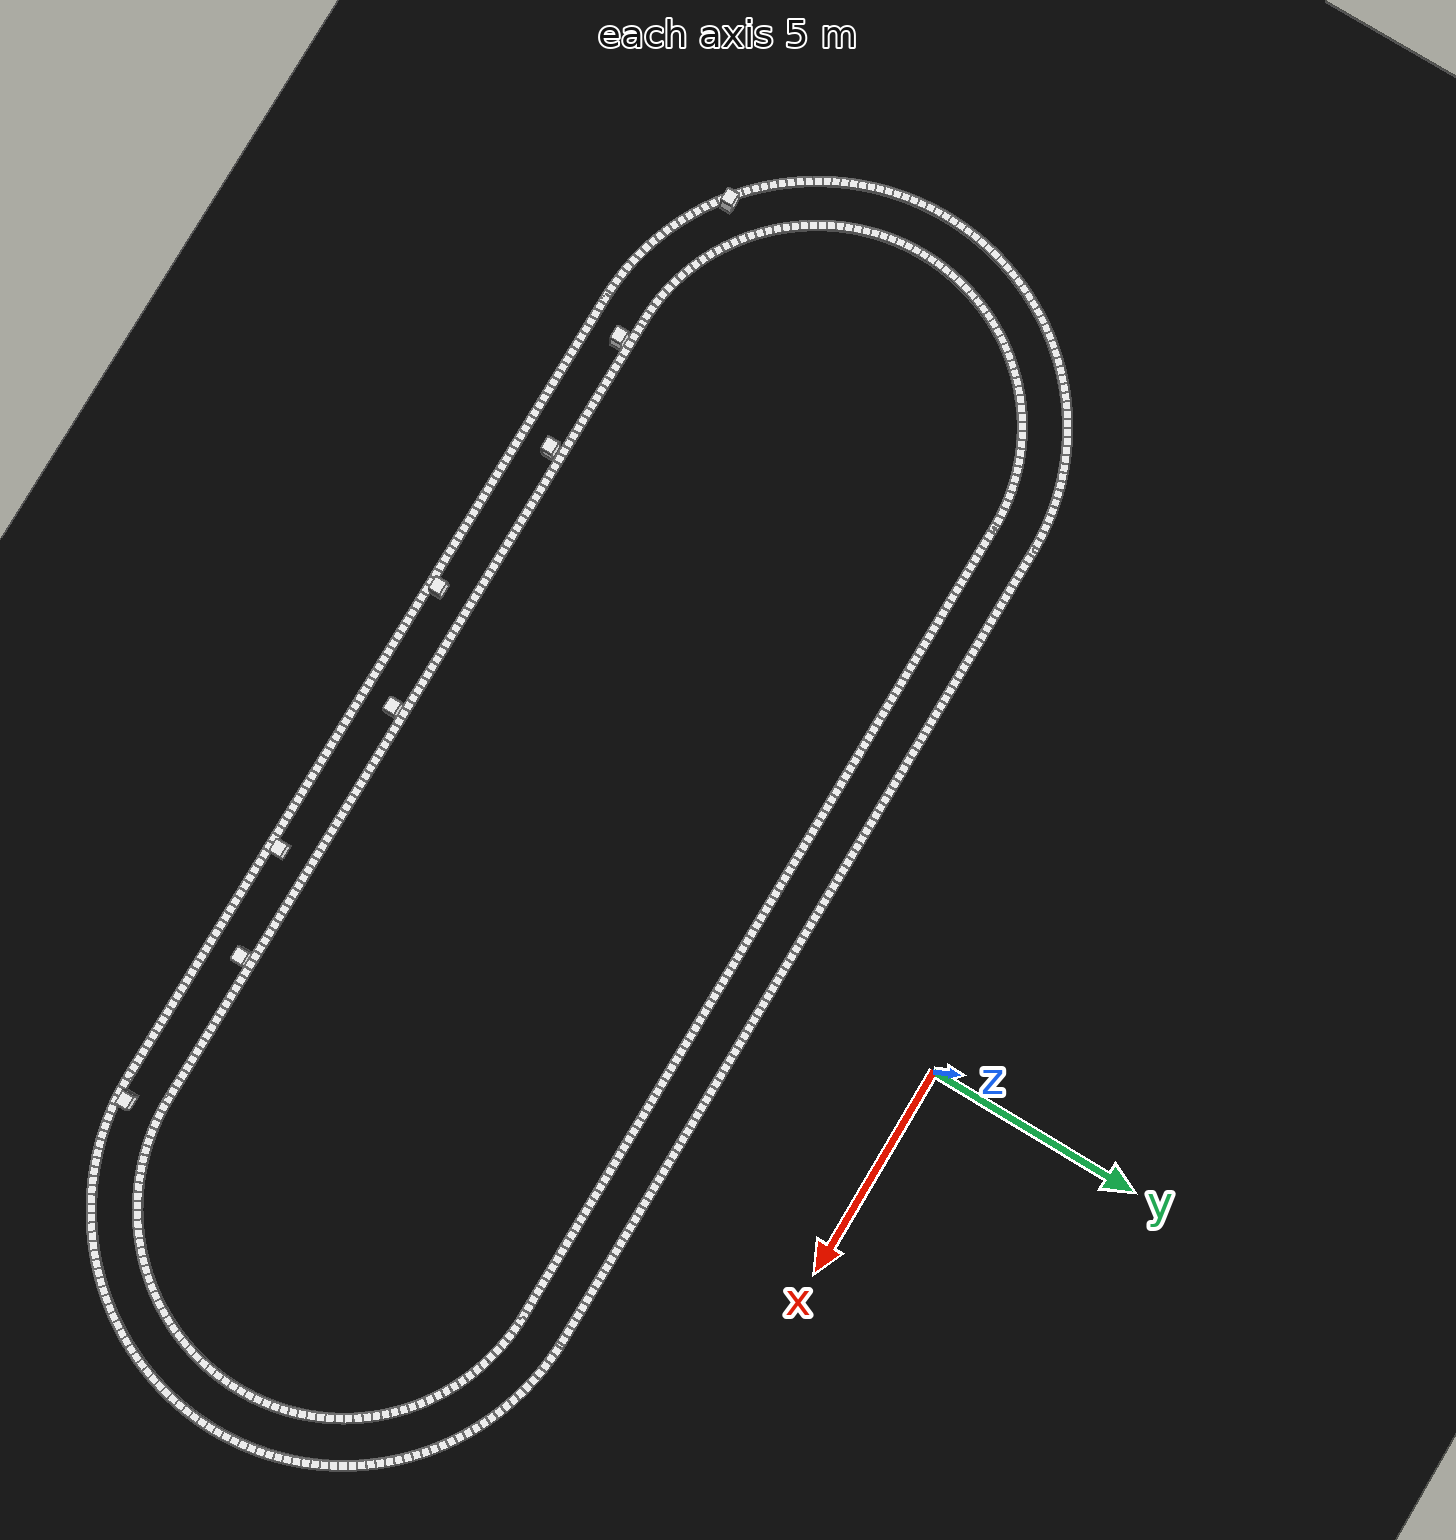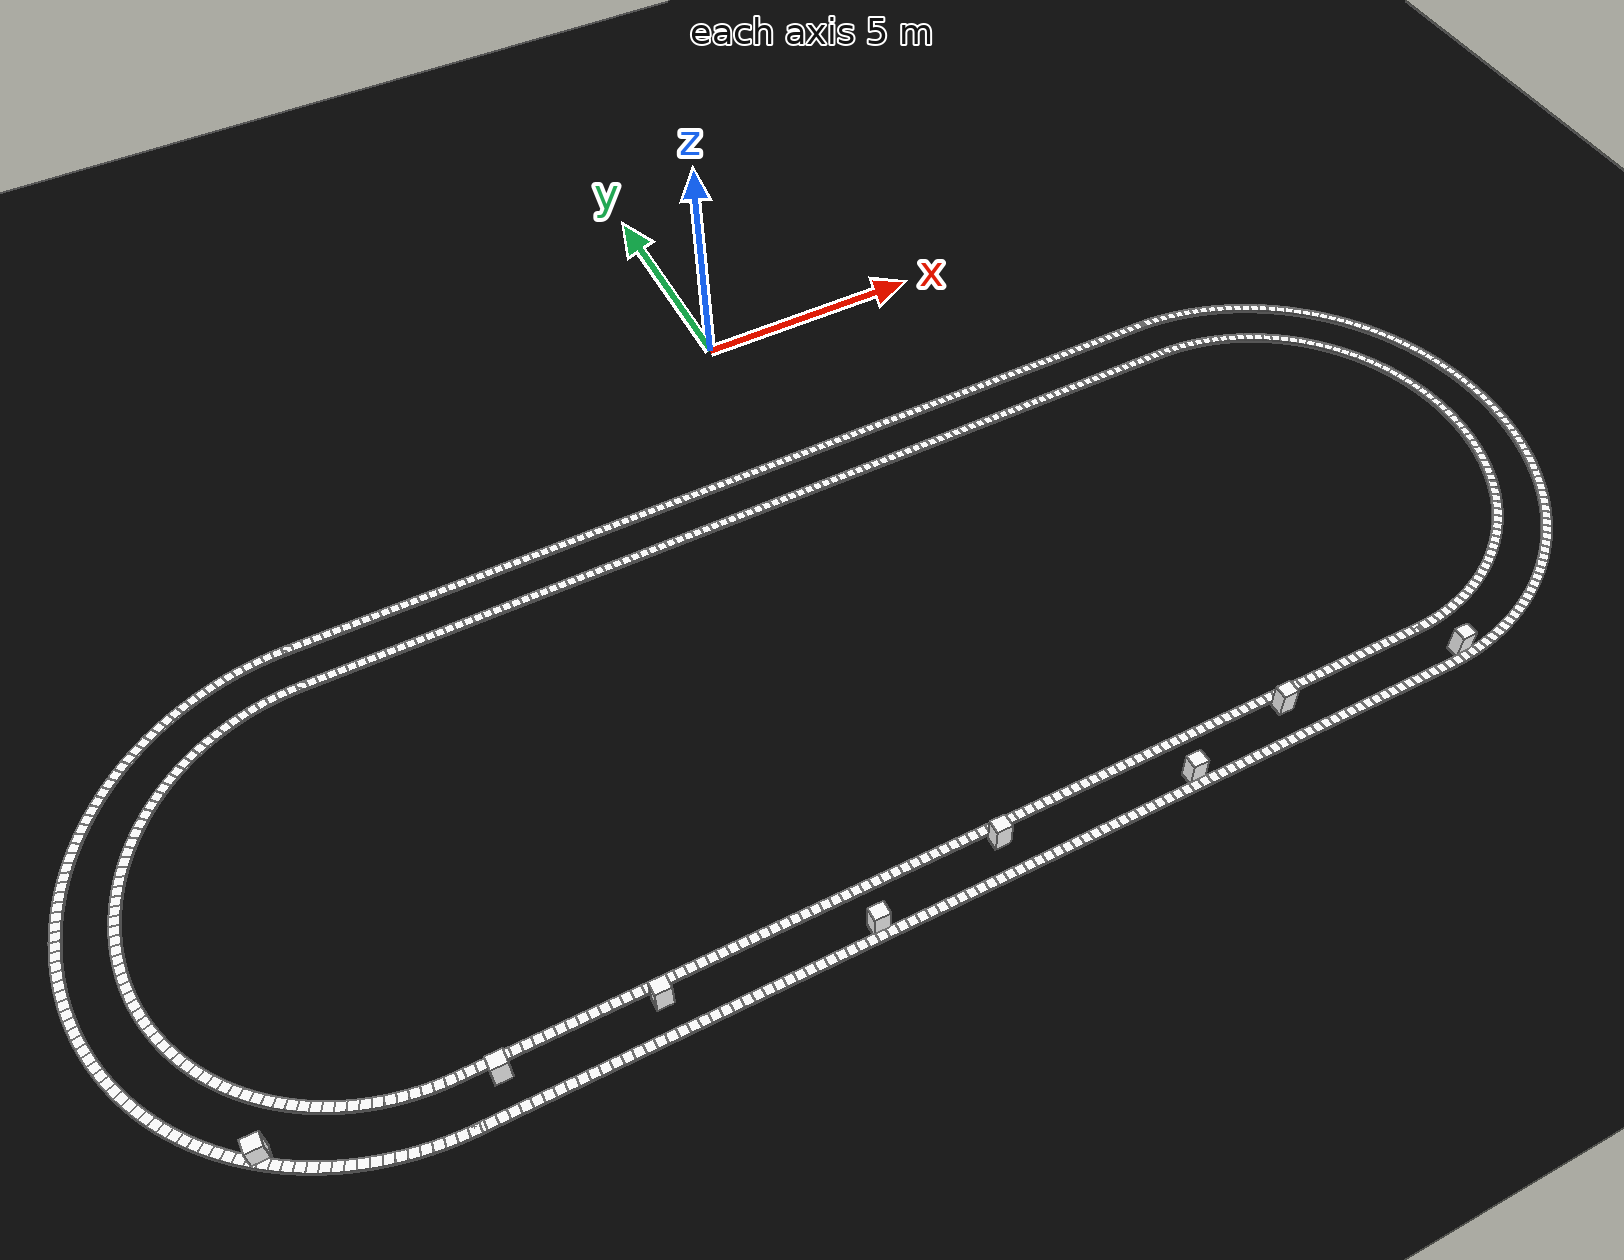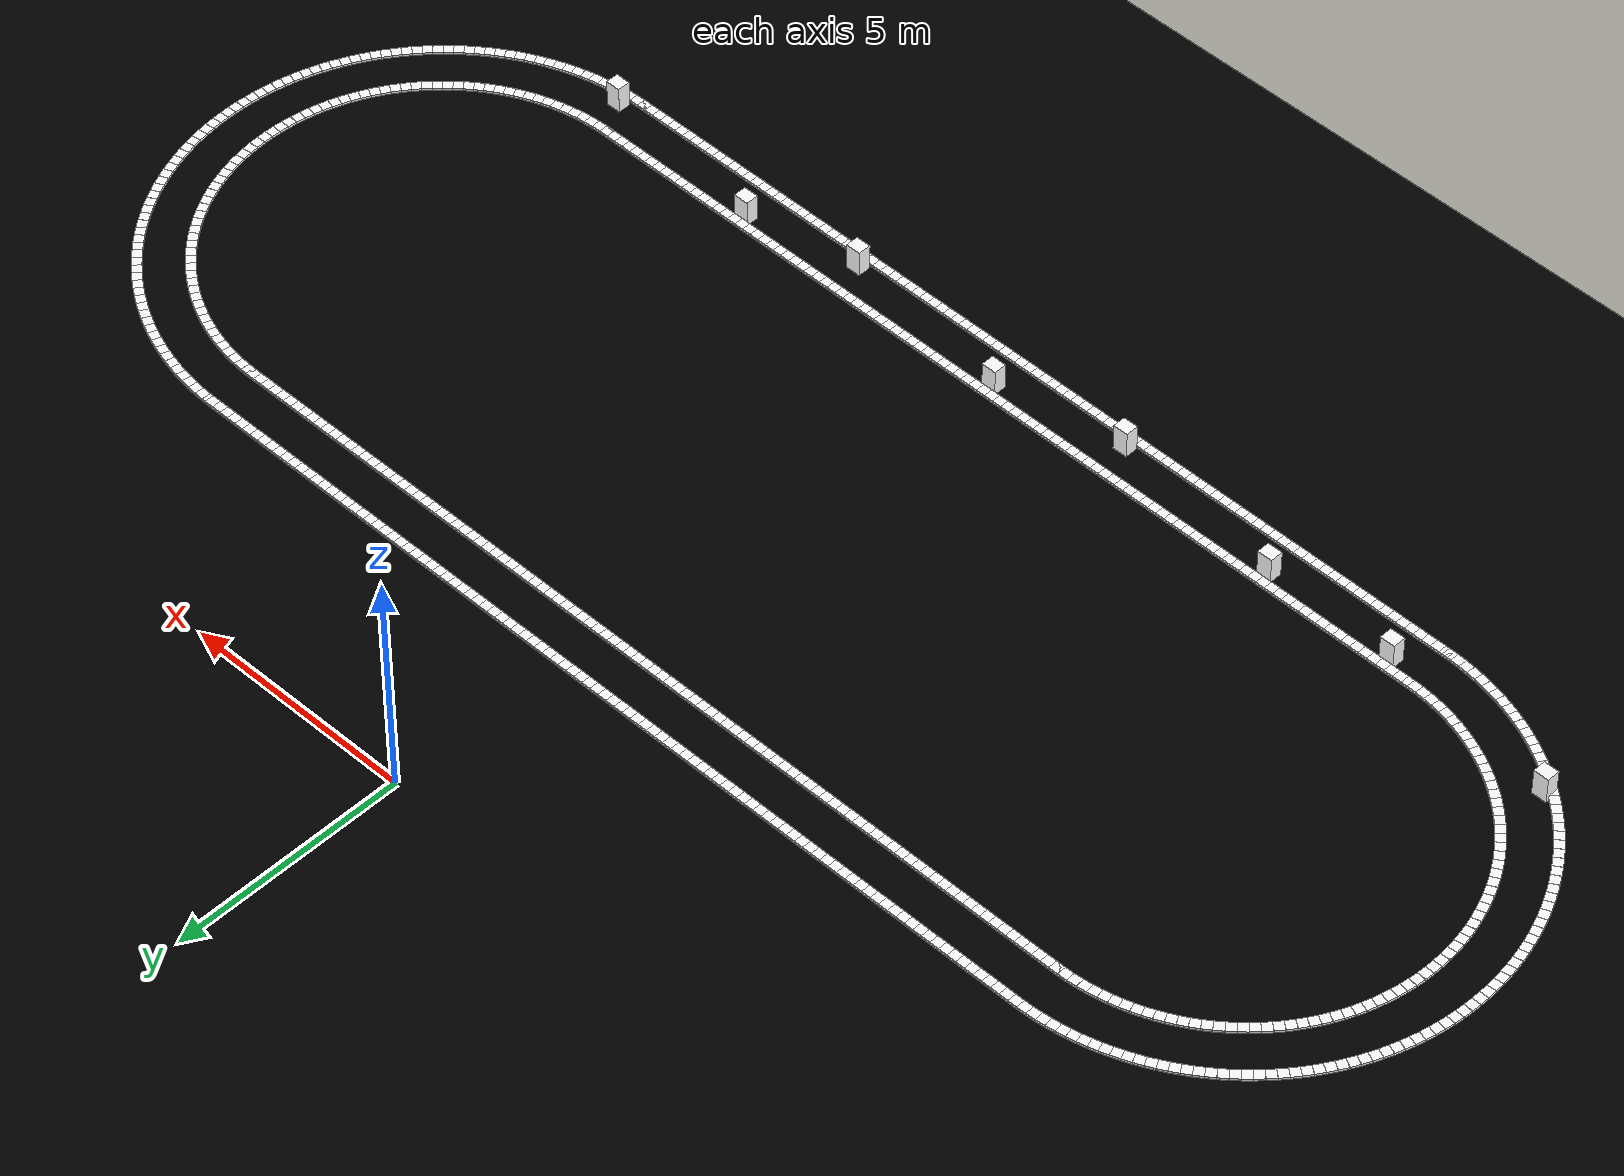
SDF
<sdf version="1.7">
 <world name="__default__">
  <gravity>0 0 -9.8</gravity>
  <magnetic_field>6e-06 2.3e-05 -4.2e-05</magnetic_field>
  <atmosphere type="adiabatic"/>
  <physics type="ode">
   <max_step_size>0.001</max_step_size>
   <real_time_factor>1</real_time_factor>
   <real_time_update_rate>1000</real_time_update_rate>
  </physics>
  <scene><ambient>0.4 0.4 0.4 1</ambient><background>0.7 0.7 0.7 1</background><shadows>1</shadows></scene>
  <spherical_coordinates>
   <surface_model>EARTH_WGS84</surface_model>
   <latitude_deg>0</latitude_deg>
   <longitude_deg>0</longitude_deg>
   <elevation>0</elevation>
   <heading_deg>0</heading_deg>
  </spherical_coordinates>
  <model name="athletics_track">
   <static>1</static>
   <link name="base">
    <collision name="plane">
     <geometry><plane><normal>0 0 1</normal><size>50 50</size></plane></geometry>
    </collision>
    <visual name="plane">
     <geometry><plane><normal>0 0 1</normal><size>50 50</size></plane></geometry>
     <material><ambient>0 0 0 1</ambient><diffuse>0 0 0 1</diffuse></material>
    </visual>
    <visual name="lane_inner_0">
     <pose>-10 4.5 0.05 0 -0 1.571</pose>
     <geometry><box><size>0.2 0.2 0.05</size></box></geometry>
     <material><ambient>1 1 1 1</ambient><diffuse>1 1 1 1</diffuse><emissive>1 1 1 1</emissive></material>
    </visual>
    <visual name="lane_inner_1">
     <pose>-10.2 4.496 0.05 0 -0 1.615</pose>
     <geometry><box><size>0.2 0.2 0.05</size></box></geometry>
     <material><ambient>1 1 1 1</ambient><diffuse>1 1 1 1</diffuse><emissive>1 1 1 1</emissive></material>
    </visual>
    <visual name="lane_inner_2">
     <pose>-10.399 4.482 0.05 0 -0 1.66</pose>
     <geometry><box><size>0.2 0.2 0.05</size></box></geometry>
     <material><ambient>1 1 1 1</ambient><diffuse>1 1 1 1</diffuse><emissive>1 1 1 1</emissive></material>
    </visual>
    <visual name="lane_inner_3">
     <pose>-10.598 4.46 0.05 0 -0 1.704</pose>
     <geometry><box><size>0.2 0.2 0.05</size></box></geometry>
     <material><ambient>1 1 1 1</ambient><diffuse>1 1 1 1</diffuse><emissive>1 1 1 1</emissive></material>
    </visual>
    <visual name="lane_inner_4">
     <pose>-10.796 4.429 0.05 0 -0 1.749</pose>
     <geometry><box><size>0.2 0.2 0.05</size></box></geometry>
     <material><ambient>1 1 1 1</ambient><diffuse>1 1 1 1</diffuse><emissive>1 1 1 1</emissive></material>
    </visual>
    <visual name="lane_inner_5">
     <pose>-10.992 4.389 0.05 0 -0 1.793</pose>
     <geometry><box><size>0.2 0.2 0.05</size></box></geometry>
     <material><ambient>1 1 1 1</ambient><diffuse>1 1 1 1</diffuse><emissive>1 1 1 1</emissive></material>
    </visual>
    <visual name="lane_inner_6">
     <pose>-11.186 4.341 0.05 0 -0 1.837</pose>
     <geometry><box><size>0.2 0.2 0.05</size></box></geometry>
     <material><ambient>1 1 1 1</ambient><diffuse>1 1 1 1</diffuse><emissive>1 1 1 1</emissive></material>
    </visual>
    <visual name="lane_inner_7">
     <pose>-11.378 4.284 0.05 0 -0 1.882</pose>
     <geometry><box><size>0.2 0.2 0.05</size></box></geometry>
     <material><ambient>1 1 1 1</ambient><diffuse>1 1 1 1</diffuse><emissive>1 1 1 1</emissive></material>
    </visual>
    <visual name="lane_inner_8">
     <pose>-11.567 4.219 0.05 0 -0 1.926</pose>
     <geometry><box><size>0.2 0.2 0.05</size></box></geometry>
     <material><ambient>1 1 1 1</ambient><diffuse>1 1 1 1</diffuse><emissive>1 1 1 1</emissive></material>
    </visual>
    <visual name="lane_inner_9">
     <pose>-11.752 4.145 0.05 0 -0 1.971</pose>
     <geometry><box><size>0.2 0.2 0.05</size></box></geometry>
     <material><ambient>1 1 1 1</ambient><diffuse>1 1 1 1</diffuse><emissive>1 1 1 1</emissive></material>
    </visual>
    <visual name="lane_inner_10">
     <pose>-11.935 4.063 0.05 0 -0 2.015</pose>
     <geometry><box><size>0.2 0.2 0.05</size></box></geometry>
     <material><ambient>1 1 1 1</ambient><diffuse>1 1 1 1</diffuse><emissive>1 1 1 1</emissive></material>
    </visual>
    <visual name="lane_inner_11">
     <pose>-12.113 3.973 0.05 0 -0 2.06</pose>
     <geometry><box><size>0.2 0.2 0.05</size></box></geometry>
     <material><ambient>1 1 1 1</ambient><diffuse>1 1 1 1</diffuse><emissive>1 1 1 1</emissive></material>
    </visual>
    <visual name="lane_inner_12">
     <pose>-12.288 3.875 0.05 0 -0 2.104</pose>
     <geometry><box><size>0.2 0.2 0.05</size></box></geometry>
     <material><ambient>1 1 1 1</ambient><diffuse>1 1 1 1</diffuse><emissive>1 1 1 1</emissive></material>
    </visual>
    <visual name="lane_inner_13">
     <pose>-12.458 3.77 0.05 0 -0 2.149</pose>
     <geometry><box><size>0.2 0.2 0.05</size></box></geometry>
     <material><ambient>1 1 1 1</ambient><diffuse>1 1 1 1</diffuse><emissive>1 1 1 1</emissive></material>
    </visual>
    <visual name="lane_inner_14">
     <pose>-12.623 3.657 0.05 0 -0 2.193</pose>
     <geometry><box><size>0.2 0.2 0.05</size></box></geometry>
     <material><ambient>1 1 1 1</ambient><diffuse>1 1 1 1</diffuse><emissive>1 1 1 1</emissive></material>
    </visual>
    <visual name="lane_inner_15">
     <pose>-12.783 3.536 0.05 0 -0 2.237</pose>
     <geometry><box><size>0.2 0.2 0.05</size></box></geometry>
     <material><ambient>1 1 1 1</ambient><diffuse>1 1 1 1</diffuse><emissive>1 1 1 1</emissive></material>
    </visual>
    <visual name="lane_inner_16">
     <pose>-12.937 3.409 0.05 0 -0 2.282</pose>
     <geometry><box><size>0.2 0.2 0.05</size></box></geometry>
     <material><ambient>1 1 1 1</ambient><diffuse>1 1 1 1</diffuse><emissive>1 1 1 1</emissive></material>
    </visual>
    <visual name="lane_inner_17">
     <pose>-13.086 3.276 0.05 0 -0 2.326</pose>
     <geometry><box><size>0.2 0.2 0.05</size></box></geometry>
     <material><ambient>1 1 1 1</ambient><diffuse>1 1 1 1</diffuse><emissive>1 1 1 1</emissive></material>
    </visual>
    <visual name="lane_inner_18">
     <pose>-13.228 3.135 0.05 0 -0 2.371</pose>
     <geometry><box><size>0.2 0.2 0.05</size></box></geometry>
     <material><ambient>1 1 1 1</ambient><diffuse>1 1 1 1</diffuse><emissive>1 1 1 1</emissive></material>
    </visual>
    <visual name="lane_inner_19">
     <pose>-13.364 2.989 0.05 0 -0 2.415</pose>
     <geometry><box><size>0.2 0.2 0.05</size></box></geometry>
     <material><ambient>1 1 1 1</ambient><diffuse>1 1 1 1</diffuse><emissive>1 1 1 1</emissive></material>
    </visual>
    <visual name="lane_inner_20">
     <pose>-13.494 2.836 0.05 0 -0 2.46</pose>
     <geometry><box><size>0.2 0.2 0.05</size></box></geometry>
     <material><ambient>1 1 1 1</ambient><diffuse>1 1 1 1</diffuse><emissive>1 1 1 1</emissive></material>
    </visual>
    <visual name="lane_inner_21">
     <pose>-13.616 2.678 0.05 0 -0 2.504</pose>
     <geometry><box><size>0.2 0.2 0.05</size></box></geometry>
     <material><ambient>1 1 1 1</ambient><diffuse>1 1 1 1</diffuse><emissive>1 1 1 1</emissive></material>
    </visual>
    <visual name="lane_inner_22">
     <pose>-13.732 2.515 0.05 0 -0 2.549</pose>
     <geometry><box><size>0.2 0.2 0.05</size></box></geometry>
     <material><ambient>1 1 1 1</ambient><diffuse>1 1 1 1</diffuse><emissive>1 1 1 1</emissive></material>
    </visual>
    <visual name="lane_inner_23">
     <pose>-13.84 2.347 0.05 0 -0 2.593</pose>
     <geometry><box><size>0.2 0.2 0.05</size></box></geometry>
     <material><ambient>1 1 1 1</ambient><diffuse>1 1 1 1</diffuse><emissive>1 1 1 1</emissive></material>
    </visual>
    <visual name="lane_inner_24">
     <pose>-13.94 2.174 0.05 0 -0 2.637</pose>
     <geometry><box><size>0.2 0.2 0.05</size></box></geometry>
     <material><ambient>1 1 1 1</ambient><diffuse>1 1 1 1</diffuse><emissive>1 1 1 1</emissive></material>
    </visual>
    <visual name="lane_inner_25">
     <pose>-14.033 1.996 0.05 0 -0 2.682</pose>
     <geometry><box><size>0.2 0.2 0.05</size></box></geometry>
     <material><ambient>1 1 1 1</ambient><diffuse>1 1 1 1</diffuse><emissive>1 1 1 1</emissive></material>
    </visual>
    <visual name="lane_inner_26">
     <pose>-14.118 1.815 0.05 0 -0 2.726</pose>
     <geometry><box><size>0.2 0.2 0.05</size></box></geometry>
     <material><ambient>1 1 1 1</ambient><diffuse>1 1 1 1</diffuse><emissive>1 1 1 1</emissive></material>
    </visual>
    <visual name="lane_inner_27">
     <pose>-14.194 1.631 0.05 0 -0 2.771</pose>
     <geometry><box><size>0.2 0.2 0.05</size></box></geometry>
     <material><ambient>1 1 1 1</ambient><diffuse>1 1 1 1</diffuse><emissive>1 1 1 1</emissive></material>
    </visual>
    <visual name="lane_inner_28">
     <pose>-14.262 1.443 0.05 0 -0 2.815</pose>
     <geometry><box><size>0.2 0.2 0.05</size></box></geometry>
     <material><ambient>1 1 1 1</ambient><diffuse>1 1 1 1</diffuse><emissive>1 1 1 1</emissive></material>
    </visual>
    <visual name="lane_inner_29">
     <pose>-14.322 1.252 0.05 0 -0 2.86</pose>
     <geometry><box><size>0.2 0.2 0.05</size></box></geometry>
     <material><ambient>1 1 1 1</ambient><diffuse>1 1 1 1</diffuse><emissive>1 1 1 1</emissive></material>
    </visual>
    <visual name="lane_inner_30">
     <pose>-14.374 1.059 0.05 0 -0 2.904</pose>
     <geometry><box><size>0.2 0.2 0.05</size></box></geometry>
     <material><ambient>1 1 1 1</ambient><diffuse>1 1 1 1</diffuse><emissive>1 1 1 1</emissive></material>
    </visual>
    <visual name="lane_inner_31">
     <pose>-14.416 0.863 0.05 0 -0 2.949</pose>
     <geometry><box><size>0.2 0.2 0.05</size></box></geometry>
     <material><ambient>1 1 1 1</ambient><diffuse>1 1 1 1</diffuse><emissive>1 1 1 1</emissive></material>
    </visual>
    <visual name="lane_inner_32">
     <pose>-14.45 0.666 0.05 0 -0 2.993</pose>
     <geometry><box><size>0.2 0.2 0.05</size></box></geometry>
     <material><ambient>1 1 1 1</ambient><diffuse>1 1 1 1</diffuse><emissive>1 1 1 1</emissive></material>
    </visual>
    <visual name="lane_inner_33">
     <pose>-14.476 0.468 0.05 0 -0 3.037</pose>
     <geometry><box><size>0.2 0.2 0.05</size></box></geometry>
     <material><ambient>1 1 1 1</ambient><diffuse>1 1 1 1</diffuse><emissive>1 1 1 1</emissive></material>
    </visual>
    <visual name="lane_inner_34">
     <pose>-14.492 0.268 0.05 0 -0 3.082</pose>
     <geometry><box><size>0.2 0.2 0.05</size></box></geometry>
     <material><ambient>1 1 1 1</ambient><diffuse>1 1 1 1</diffuse><emissive>1 1 1 1</emissive></material>
    </visual>
    <visual name="lane_inner_35">
     <pose>-14.499 0.069 0.05 0 -0 3.126</pose>
     <geometry><box><size>0.2 0.2 0.05</size></box></geometry>
     <material><ambient>1 1 1 1</ambient><diffuse>1 1 1 1</diffuse><emissive>1 1 1 1</emissive></material>
    </visual>
    <visual name="lane_inner_36">
     <pose>-14.498 -0.131 0.05 0 -0 -3.11219</pose>
     <geometry><box><size>0.2 0.2 0.05</size></box></geometry>
     <material><ambient>1 1 1 1</ambient><diffuse>1 1 1 1</diffuse><emissive>1 1 1 1</emissive></material>
    </visual>
    <visual name="lane_inner_37">
     <pose>-14.488 -0.331 0.05 0 -0 -3.06819</pose>
     <geometry><box><size>0.2 0.2 0.05</size></box></geometry>
     <material><ambient>1 1 1 1</ambient><diffuse>1 1 1 1</diffuse><emissive>1 1 1 1</emissive></material>
    </visual>
    <visual name="lane_inner_38">
     <pose>-14.469 -0.53 0.05 0 -0 -3.02318</pose>
     <geometry><box><size>0.2 0.2 0.05</size></box></geometry>
     <material><ambient>1 1 1 1</ambient><diffuse>1 1 1 1</diffuse><emissive>1 1 1 1</emissive></material>
    </visual>
    <visual name="lane_inner_39">
     <pose>-14.441 -0.728 0.05 0 -0 -2.97919</pose>
     <geometry><box><size>0.2 0.2 0.05</size></box></geometry>
     <material><ambient>1 1 1 1</ambient><diffuse>1 1 1 1</diffuse><emissive>1 1 1 1</emissive></material>
    </visual>
    <visual name="lane_inner_40">
     <pose>-14.404 -0.925 0.05 0 -0 -2.93418</pose>
     <geometry><box><size>0.2 0.2 0.05</size></box></geometry>
     <material><ambient>1 1 1 1</ambient><diffuse>1 1 1 1</diffuse><emissive>1 1 1 1</emissive></material>
    </visual>
    <visual name="lane_inner_41">
     <pose>-14.359 -1.12 0.05 0 -0 -2.89018</pose>
     <geometry><box><size>0.2 0.2 0.05</size></box></geometry>
     <material><ambient>1 1 1 1</ambient><diffuse>1 1 1 1</diffuse><emissive>1 1 1 1</emissive></material>
    </visual>
    <visual name="lane_inner_42">
     <pose>-14.304 -1.312 0.05 0 -0 -2.84619</pose>
     <geometry><box><size>0.2 0.2 0.05</size></box></geometry>
     <material><ambient>1 1 1 1</ambient><diffuse>1 1 1 1</diffuse><emissive>1 1 1 1</emissive></material>
    </visual>
    <visual name="lane_inner_43">
     <pose>-14.242 -1.502 0.05 0 -0 -2.80118</pose>
     <geometry><box><size>0.2 0.2 0.05</size></box></geometry>
     <material><ambient>1 1 1 1</ambient><diffuse>1 1 1 1</diffuse><emissive>1 1 1 1</emissive></material>
    </visual>
    <visual name="lane_inner_44">
     <pose>-14.171 -1.689 0.05 0 -0 -2.75719</pose>
     <geometry><box><size>0.2 0.2 0.05</size></box></geometry>
     <material><ambient>1 1 1 1</ambient><diffuse>1 1 1 1</diffuse><emissive>1 1 1 1</emissive></material>
    </visual>
    <visual name="lane_inner_45">
     <pose>-14.092 -1.873 0.05 0 -0 -2.71218</pose>
     <geometry><box><size>0.2 0.2 0.05</size></box></geometry>
     <material><ambient>1 1 1 1</ambient><diffuse>1 1 1 1</diffuse><emissive>1 1 1 1</emissive></material>
    </visual>
    <visual name="lane_inner_46">
     <pose>-14.005 -2.053 0.05 0 -0 -2.66818</pose>
     <geometry><box><size>0.2 0.2 0.05</size></box></geometry>
     <material><ambient>1 1 1 1</ambient><diffuse>1 1 1 1</diffuse><emissive>1 1 1 1</emissive></material>
    </visual>
    <visual name="lane_inner_47">
     <pose>-13.909 -2.229 0.05 0 -0 -2.62318</pose>
     <geometry><box><size>0.2 0.2 0.05</size></box></geometry>
     <material><ambient>1 1 1 1</ambient><diffuse>1 1 1 1</diffuse><emissive>1 1 1 1</emissive></material>
    </visual>
    <visual name="lane_inner_48">
     <pose>-13.807 -2.4 0.05 0 -0 -2.57918</pose>
     <geometry><box><size>0.2 0.2 0.05</size></box></geometry>
     <material><ambient>1 1 1 1</ambient><diffuse>1 1 1 1</diffuse><emissive>1 1 1 1</emissive></material>
    </visual>
    <visual name="lane_inner_49">
     <pose>-13.696 -2.567 0.05 0 -0 -2.53418</pose>
     <geometry><box><size>0.2 0.2 0.05</size></box></geometry>
     <material><ambient>1 1 1 1</ambient><diffuse>1 1 1 1</diffuse><emissive>1 1 1 1</emissive></material>
    </visual>
    <visual name="lane_inner_50">
     <pose>-13.578 -2.728 0.05 0 -0 -2.49018</pose>
     <geometry><box><size>0.2 0.2 0.05</size></box></geometry>
     <material><ambient>1 1 1 1</ambient><diffuse>1 1 1 1</diffuse><emissive>1 1 1 1</emissive></material>
    </visual>
    <visual name="lane_inner_51">
     <pose>-13.454 -2.885 0.05 0 -0 -2.44618</pose>
     <geometry><box><size>0.2 0.2 0.05</size></box></geometry>
     <material><ambient>1 1 1 1</ambient><diffuse>1 1 1 1</diffuse><emissive>1 1 1 1</emissive></material>
    </visual>
    <visual name="lane_inner_52">
     <pose>-13.322 -3.035 0.05 0 -0 -2.40118</pose>
     <geometry><box><size>0.2 0.2 0.05</size></box></geometry>
     <material><ambient>1 1 1 1</ambient><diffuse>1 1 1 1</diffuse><emissive>1 1 1 1</emissive></material>
    </visual>
    <visual name="lane_inner_53">
     <pose>-13.184 -3.18 0.05 0 -0 -2.35718</pose>
     <geometry><box><size>0.2 0.2 0.05</size></box></geometry>
     <material><ambient>1 1 1 1</ambient><diffuse>1 1 1 1</diffuse><emissive>1 1 1 1</emissive></material>
    </visual>
    <visual name="lane_inner_54">
     <pose>-13.04 -3.318 0.05 0 -0 -2.31218</pose>
     <geometry><box><size>0.2 0.2 0.05</size></box></geometry>
     <material><ambient>1 1 1 1</ambient><diffuse>1 1 1 1</diffuse><emissive>1 1 1 1</emissive></material>
    </visual>
    <visual name="lane_inner_55">
     <pose>-12.889 -3.45 0.05 0 -0 -2.26818</pose>
     <geometry><box><size>0.2 0.2 0.05</size></box></geometry>
     <material><ambient>1 1 1 1</ambient><diffuse>1 1 1 1</diffuse><emissive>1 1 1 1</emissive></material>
    </visual>
    <visual name="lane_inner_56">
     <pose>-12.733 -3.575 0.05 0 -0 -2.22318</pose>
     <geometry><box><size>0.2 0.2 0.05</size></box></geometry>
     <material><ambient>1 1 1 1</ambient><diffuse>1 1 1 1</diffuse><emissive>1 1 1 1</emissive></material>
    </visual>
    <visual name="lane_inner_57">
     <pose>-12.571 -3.693 0.05 0 -0 -2.17918</pose>
     <geometry><box><size>0.2 0.2 0.05</size></box></geometry>
     <material><ambient>1 1 1 1</ambient><diffuse>1 1 1 1</diffuse><emissive>1 1 1 1</emissive></material>
    </visual>
    <visual name="lane_inner_58">
     <pose>-12.405 -3.804 0.05 0 -0 -2.13418</pose>
     <geometry><box><size>0.2 0.2 0.05</size></box></geometry>
     <material><ambient>1 1 1 1</ambient><diffuse>1 1 1 1</diffuse><emissive>1 1 1 1</emissive></material>
    </visual>
    <visual name="lane_inner_59">
     <pose>-12.234 -3.907 0.05 0 -0 -2.09018</pose>
     <geometry><box><size>0.2 0.2 0.05</size></box></geometry>
     <material><ambient>1 1 1 1</ambient><diffuse>1 1 1 1</diffuse><emissive>1 1 1 1</emissive></material>
    </visual>
    <visual name="lane_inner_60">
     <pose>-12.058 -4.002 0.05 0 -0 -2.04618</pose>
     <geometry><box><size>0.2 0.2 0.05</size></box></geometry>
     <material><ambient>1 1 1 1</ambient><diffuse>1 1 1 1</diffuse><emissive>1 1 1 1</emissive></material>
    </visual>
    <visual name="lane_inner_61">
     <pose>-11.878 -4.089 0.05 0 -0 -2.00118</pose>
     <geometry><box><size>0.2 0.2 0.05</size></box></geometry>
     <material><ambient>1 1 1 1</ambient><diffuse>1 1 1 1</diffuse><emissive>1 1 1 1</emissive></material>
    </visual>
    <visual name="lane_inner_62">
     <pose>-11.694 -4.169 0.05 0 -0 -1.95718</pose>
     <geometry><box><size>0.2 0.2 0.05</size></box></geometry>
     <material><ambient>1 1 1 1</ambient><diffuse>1 1 1 1</diffuse><emissive>1 1 1 1</emissive></material>
    </visual>
    <visual name="lane_inner_63">
     <pose>-11.507 -4.24 0.05 0 -0 -1.91219</pose>
     <geometry><box><size>0.2 0.2 0.05</size></box></geometry>
     <material><ambient>1 1 1 1</ambient><diffuse>1 1 1 1</diffuse><emissive>1 1 1 1</emissive></material>
    </visual>
    <visual name="lane_inner_64">
     <pose>-11.318 -4.303 0.05 0 -0 -1.86818</pose>
     <geometry><box><size>0.2 0.2 0.05</size></box></geometry>
     <material><ambient>1 1 1 1</ambient><diffuse>1 1 1 1</diffuse><emissive>1 1 1 1</emissive></material>
    </visual>
    <visual name="lane_inner_65">
     <pose>-11.125 -4.357 0.05 0 -0 -1.82319</pose>
     <geometry><box><size>0.2 0.2 0.05</size></box></geometry>
     <material><ambient>1 1 1 1</ambient><diffuse>1 1 1 1</diffuse><emissive>1 1 1 1</emissive></material>
    </visual>
    <visual name="lane_inner_66">
     <pose>-10.93 -4.403 0.05 0 -0 -1.77919</pose>
     <geometry><box><size>0.2 0.2 0.05</size></box></geometry>
     <material><ambient>1 1 1 1</ambient><diffuse>1 1 1 1</diffuse><emissive>1 1 1 1</emissive></material>
    </visual>
    <visual name="lane_inner_67">
     <pose>-10.734 -4.44 0.05 0 -0 -1.73419</pose>
     <geometry><box><size>0.2 0.2 0.05</size></box></geometry>
     <material><ambient>1 1 1 1</ambient><diffuse>1 1 1 1</diffuse><emissive>1 1 1 1</emissive></material>
    </visual>
    <visual name="lane_inner_68">
     <pose>-10.536 -4.468 0.05 0 -0 -1.69019</pose>
     <geometry><box><size>0.2 0.2 0.05</size></box></geometry>
     <material><ambient>1 1 1 1</ambient><diffuse>1 1 1 1</diffuse><emissive>1 1 1 1</emissive></material>
    </visual>
    <visual name="lane_inner_69">
     <pose>-10.337 -4.487 0.05 0 -0 -1.64619</pose>
     <geometry><box><size>0.2 0.2 0.05</size></box></geometry>
     <material><ambient>1 1 1 1</ambient><diffuse>1 1 1 1</diffuse><emissive>1 1 1 1</emissive></material>
    </visual>
    <visual name="lane_inner_70">
     <pose>-10.137 -4.498 0.05 0 -0 -1.60119</pose>
     <geometry><box><size>0.2 0.2 0.05</size></box></geometry>
     <material><ambient>1 1 1 1</ambient><diffuse>1 1 1 1</diffuse><emissive>1 1 1 1</emissive></material>
    </visual>
    <visual name="lane_inner_71">
     <pose>10 -4.5 0.05 0 0 -1.571</pose>
     <geometry><box><size>0.2 0.2 0.05</size></box></geometry>
     <material><ambient>1 1 1 1</ambient><diffuse>1 1 1 1</diffuse><emissive>1 1 1 1</emissive></material>
    </visual>
    <visual name="lane_inner_72">
     <pose>10.2 -4.496 0.05 0 0 -1.526</pose>
     <geometry><box><size>0.2 0.2 0.05</size></box></geometry>
     <material><ambient>1 1 1 1</ambient><diffuse>1 1 1 1</diffuse><emissive>1 1 1 1</emissive></material>
    </visual>
    <visual name="lane_inner_73">
     <pose>10.399 -4.482 0.05 0 0 -1.482</pose>
     <geometry><box><size>0.2 0.2 0.05</size></box></geometry>
     <material><ambient>1 1 1 1</ambient><diffuse>1 1 1 1</diffuse><emissive>1 1 1 1</emissive></material>
    </visual>
    <visual name="lane_inner_74">
     <pose>10.598 -4.46 0.05 0 0 -1.437</pose>
     <geometry><box><size>0.2 0.2 0.05</size></box></geometry>
     <material><ambient>1 1 1 1</ambient><diffuse>1 1 1 1</diffuse><emissive>1 1 1 1</emissive></material>
    </visual>
    <visual name="lane_inner_75">
     <pose>10.796 -4.429 0.05 0 0 -1.393</pose>
     <geometry><box><size>0.2 0.2 0.05</size></box></geometry>
     <material><ambient>1 1 1 1</ambient><diffuse>1 1 1 1</diffuse><emissive>1 1 1 1</emissive></material>
    </visual>
    <visual name="lane_inner_76">
     <pose>10.992 -4.389 0.05 0 0 -1.349</pose>
     <geometry><box><size>0.2 0.2 0.05</size></box></geometry>
     <material><ambient>1 1 1 1</ambient><diffuse>1 1 1 1</diffuse><emissive>1 1 1 1</emissive></material>
    </visual>
    <visual name="lane_inner_77">
     <pose>11.186 -4.341 0.05 0 0 -1.304</pose>
     <geometry><box><size>0.2 0.2 0.05</size></box></geometry>
     <material><ambient>1 1 1 1</ambient><diffuse>1 1 1 1</diffuse><emissive>1 1 1 1</emissive></material>
    </visual>
    <visual name="lane_inner_78">
     <pose>11.378 -4.284 0.05 0 0 -1.26</pose>
     <geometry><box><size>0.2 0.2 0.05</size></box></geometry>
     <material><ambient>1 1 1 1</ambient><diffuse>1 1 1 1</diffuse><emissive>1 1 1 1</emissive></material>
    </visual>
    <visual name="lane_inner_79">
     <pose>11.567 -4.219 0.05 0 0 -1.215</pose>
     <geometry><box><size>0.2 0.2 0.05</size></box></geometry>
     <material><ambient>1 1 1 1</ambient><diffuse>1 1 1 1</diffuse><emissive>1 1 1 1</emissive></material>
    </visual>
    <visual name="lane_inner_80">
     <pose>11.752 -4.145 0.05 0 0 -1.171</pose>
     <geometry><box><size>0.2 0.2 0.05</size></box></geometry>
     <material><ambient>1 1 1 1</ambient><diffuse>1 1 1 1</diffuse><emissive>1 1 1 1</emissive></material>
    </visual>
    <visual name="lane_inner_81">
     <pose>11.935 -4.063 0.05 0 0 -1.126</pose>
     <geometry><box><size>0.2 0.2 0.05</size></box></geometry>
     <material><ambient>1 1 1 1</ambient><diffuse>1 1 1 1</diffuse><emissive>1 1 1 1</emissive></material>
    </visual>
    <visual name="lane_inner_82">
     <pose>12.113 -3.973 0.05 0 0 -1.082</pose>
     <geometry><box><size>0.2 0.2 0.05</size></box></geometry>
     <material><ambient>1 1 1 1</ambient><diffuse>1 1 1 1</diffuse><emissive>1 1 1 1</emissive></material>
    </visual>
    <visual name="lane_inner_83">
     <pose>12.288 -3.875 0.05 0 0 -1.037</pose>
     <geometry><box><size>0.2 0.2 0.05</size></box></geometry>
     <material><ambient>1 1 1 1</ambient><diffuse>1 1 1 1</diffuse><emissive>1 1 1 1</emissive></material>
    </visual>
    <visual name="lane_inner_84">
     <pose>12.458 -3.77 0.05 0 0 -0.993</pose>
     <geometry><box><size>0.2 0.2 0.05</size></box></geometry>
     <material><ambient>1 1 1 1</ambient><diffuse>1 1 1 1</diffuse><emissive>1 1 1 1</emissive></material>
    </visual>
    <visual name="lane_inner_85">
     <pose>12.623 -3.657 0.05 0 0 -0.949</pose>
     <geometry><box><size>0.2 0.2 0.05</size></box></geometry>
     <material><ambient>1 1 1 1</ambient><diffuse>1 1 1 1</diffuse><emissive>1 1 1 1</emissive></material>
    </visual>
    <visual name="lane_inner_86">
     <pose>12.783 -3.536 0.05 0 0 -0.904</pose>
     <geometry><box><size>0.2 0.2 0.05</size></box></geometry>
     <material><ambient>1 1 1 1</ambient><diffuse>1 1 1 1</diffuse><emissive>1 1 1 1</emissive></material>
    </visual>
    <visual name="lane_inner_87">
     <pose>12.937 -3.409 0.05 0 0 -0.86</pose>
     <geometry><box><size>0.2 0.2 0.05</size></box></geometry>
     <material><ambient>1 1 1 1</ambient><diffuse>1 1 1 1</diffuse><emissive>1 1 1 1</emissive></material>
    </visual>
    <visual name="lane_inner_88">
     <pose>13.086 -3.276 0.05 0 0 -0.815</pose>
     <geometry><box><size>0.2 0.2 0.05</size></box></geometry>
     <material><ambient>1 1 1 1</ambient><diffuse>1 1 1 1</diffuse><emissive>1 1 1 1</emissive></material>
    </visual>
    <visual name="lane_inner_89">
     <pose>13.228 -3.135 0.05 0 0 -0.771</pose>
     <geometry><box><size>0.2 0.2 0.05</size></box></geometry>
     <material><ambient>1 1 1 1</ambient><diffuse>1 1 1 1</diffuse><emissive>1 1 1 1</emissive></material>
    </visual>
    <visual name="lane_inner_90">
     <pose>13.364 -2.989 0.05 0 0 -0.726</pose>
     <geometry><box><size>0.2 0.2 0.05</size></box></geometry>
     <material><ambient>1 1 1 1</ambient><diffuse>1 1 1 1</diffuse><emissive>1 1 1 1</emissive></material>
    </visual>
    <visual name="lane_inner_91">
     <pose>13.494 -2.836 0.05 0 0 -0.682</pose>
     <geometry><box><size>0.2 0.2 0.05</size></box></geometry>
     <material><ambient>1 1 1 1</ambient><diffuse>1 1 1 1</diffuse><emissive>1 1 1 1</emissive></material>
    </visual>
    <visual name="lane_inner_92">
     <pose>13.616 -2.678 0.05 0 0 -0.637</pose>
     <geometry><box><size>0.2 0.2 0.05</size></box></geometry>
     <material><ambient>1 1 1 1</ambient><diffuse>1 1 1 1</diffuse><emissive>1 1 1 1</emissive></material>
    </visual>
    <visual name="lane_inner_93">
     <pose>13.732 -2.515 0.05 0 0 -0.593</pose>
     <geometry><box><size>0.2 0.2 0.05</size></box></geometry>
     <material><ambient>1 1 1 1</ambient><diffuse>1 1 1 1</diffuse><emissive>1 1 1 1</emissive></material>
    </visual>
    <visual name="lane_inner_94">
     <pose>13.84 -2.347 0.05 0 0 -0.549</pose>
     <geometry><box><size>0.2 0.2 0.05</size></box></geometry>
     <material><ambient>1 1 1 1</ambient><diffuse>1 1 1 1</diffuse><emissive>1 1 1 1</emissive></material>
    </visual>
    <visual name="lane_inner_95">
     <pose>13.94 -2.174 0.05 0 0 -0.504</pose>
     <geometry><box><size>0.2 0.2 0.05</size></box></geometry>
     <material><ambient>1 1 1 1</ambient><diffuse>1 1 1 1</diffuse><emissive>1 1 1 1</emissive></material>
    </visual>
    <visual name="lane_inner_96">
     <pose>14.033 -1.996 0.05 0 0 -0.46</pose>
     <geometry><box><size>0.2 0.2 0.05</size></box></geometry>
     <material><ambient>1 1 1 1</ambient><diffuse>1 1 1 1</diffuse><emissive>1 1 1 1</emissive></material>
    </visual>
    <visual name="lane_inner_97">
     <pose>14.118 -1.815 0.05 0 0 -0.415</pose>
     <geometry><box><size>0.2 0.2 0.05</size></box></geometry>
     <material><ambient>1 1 1 1</ambient><diffuse>1 1 1 1</diffuse><emissive>1 1 1 1</emissive></material>
    </visual>
    <visual name="lane_inner_98">
     <pose>14.194 -1.631 0.05 0 0 -0.371</pose>
     <geometry><box><size>0.2 0.2 0.05</size></box></geometry>
     <material><ambient>1 1 1 1</ambient><diffuse>1 1 1 1</diffuse><emissive>1 1 1 1</emissive></material>
    </visual>
    <visual name="lane_inner_99">
     <pose>14.262 -1.443 0.05 0 0 -0.326</pose>
     <geometry><box><size>0.2 0.2 0.05</size></box></geometry>
     <material><ambient>1 1 1 1</ambient><diffuse>1 1 1 1</diffuse><emissive>1 1 1 1</emissive></material>
    </visual>
    <visual name="lane_inner_100">
     <pose>14.322 -1.252 0.05 0 0 -0.282</pose>
     <geometry><box><size>0.2 0.2 0.05</size></box></geometry>
     <material><ambient>1 1 1 1</ambient><diffuse>1 1 1 1</diffuse><emissive>1 1 1 1</emissive></material>
    </visual>
    <visual name="lane_inner_101">
     <pose>14.374 -1.059 0.05 0 0 -0.237</pose>
     <geometry><box><size>0.2 0.2 0.05</size></box></geometry>
     <material><ambient>1 1 1 1</ambient><diffuse>1 1 1 1</diffuse><emissive>1 1 1 1</emissive></material>
    </visual>
    <visual name="lane_inner_102">
     <pose>14.416 -0.863 0.05 0 0 -0.193</pose>
     <geometry><box><size>0.2 0.2 0.05</size></box></geometry>
     <material><ambient>1 1 1 1</ambient><diffuse>1 1 1 1</diffuse><emissive>1 1 1 1</emissive></material>
    </visual>
    <visual name="lane_inner_103">
     <pose>14.45 -0.666 0.05 0 0 -0.149</pose>
     <geometry><box><size>0.2 0.2 0.05</size></box></geometry>
     <material><ambient>1 1 1 1</ambient><diffuse>1 1 1 1</diffuse><emissive>1 1 1 1</emissive></material>
    </visual>
    <visual name="lane_inner_104">
     <pose>14.476 -0.468 0.05 0 0 -0.104</pose>
     <geometry><box><size>0.2 0.2 0.05</size></box></geometry>
     <material><ambient>1 1 1 1</ambient><diffuse>1 1 1 1</diffuse><emissive>1 1 1 1</emissive></material>
    </visual>
    <visual name="lane_inner_105">
     <pose>14.492 -0.268 0.05 0 0 -0.06</pose>
     <geometry><box><size>0.2 0.2 0.05</size></box></geometry>
     <material><ambient>1 1 1 1</ambient><diffuse>1 1 1 1</diffuse><emissive>1 1 1 1</emissive></material>
    </visual>
    <visual name="lane_inner_106">
     <pose>14.499 -0.069 0.05 0 0 -0.015</pose>
     <geometry><box><size>0.2 0.2 0.05</size></box></geometry>
     <material><ambient>1 1 1 1</ambient><diffuse>1 1 1 1</diffuse><emissive>1 1 1 1</emissive></material>
    </visual>
    <visual name="lane_inner_107">
     <pose>14.498 0.131 0.05 0 -0 0.029</pose>
     <geometry><box><size>0.2 0.2 0.05</size></box></geometry>
     <material><ambient>1 1 1 1</ambient><diffuse>1 1 1 1</diffuse><emissive>1 1 1 1</emissive></material>
    </visual>
    <visual name="lane_inner_108">
     <pose>14.488 0.331 0.05 0 -0 0.074</pose>
     <geometry><box><size>0.2 0.2 0.05</size></box></geometry>
     <material><ambient>1 1 1 1</ambient><diffuse>1 1 1 1</diffuse><emissive>1 1 1 1</emissive></material>
    </visual>
    <visual name="lane_inner_109">
     <pose>14.469 0.53 0.05 0 -0 0.118</pose>
     <geometry><box><size>0.2 0.2 0.05</size></box></geometry>
     <material><ambient>1 1 1 1</ambient><diffuse>1 1 1 1</diffuse><emissive>1 1 1 1</emissive></material>
    </visual>
    <visual name="lane_inner_110">
     <pose>14.441 0.728 0.05 0 -0 0.163</pose>
     <geometry><box><size>0.2 0.2 0.05</size></box></geometry>
     <material><ambient>1 1 1 1</ambient><diffuse>1 1 1 1</diffuse><emissive>1 1 1 1</emissive></material>
    </visual>
    <visual name="lane_inner_111">
     <pose>14.404 0.925 0.05 0 -0 0.207</pose>
     <geometry><box><size>0.2 0.2 0.05</size></box></geometry>
     <material><ambient>1 1 1 1</ambient><diffuse>1 1 1 1</diffuse><emissive>1 1 1 1</emissive></material>
    </visual>
    <visual name="lane_inner_112">
     <pose>14.359 1.12 0.05 0 -0 0.251</pose>
     <geometry><box><size>0.2 0.2 0.05</size></box></geometry>
     <material><ambient>1 1 1 1</ambient><diffuse>1 1 1 1</diffuse><emissive>1 1 1 1</emissive></material>
    </visual>
    <visual name="lane_inner_113">
     <pose>14.304 1.312 0.05 0 -0 0.296</pose>
     <geometry><box><size>0.2 0.2 0.05</size></box></geometry>
     <material><ambient>1 1 1 1</ambient><diffuse>1 1 1 1</diffuse><emissive>1 1 1 1</emissive></material>
    </visual>
    <visual name="lane_inner_114">
     <pose>14.242 1.502 0.05 0 -0 0.34</pose>
     <geometry><box><size>0.2 0.2 0.05</size></box></geometry>
     <material><ambient>1 1 1 1</ambient><diffuse>1 1 1 1</diffuse><emissive>1 1 1 1</emissive></material>
    </visual>
    <visual name="lane_inner_115">
     <pose>14.171 1.689 0.05 0 -0 0.385</pose>
     <geometry><box><size>0.2 0.2 0.05</size></box></geometry>
     <material><ambient>1 1 1 1</ambient><diffuse>1 1 1 1</diffuse><emissive>1 1 1 1</emissive></material>
    </visual>
    <visual name="lane_inner_116">
     <pose>14.092 1.873 0.05 0 -0 0.429</pose>
     <geometry><box><size>0.2 0.2 0.05</size></box></geometry>
     <material><ambient>1 1 1 1</ambient><diffuse>1 1 1 1</diffuse><emissive>1 1 1 1</emissive></material>
    </visual>
    <visual name="lane_inner_117">
     <pose>14.005 2.053 0.05 0 -0 0.474</pose>
     <geometry><box><size>0.2 0.2 0.05</size></box></geometry>
     <material><ambient>1 1 1 1</ambient><diffuse>1 1 1 1</diffuse><emissive>1 1 1 1</emissive></material>
    </visual>
    <visual name="lane_inner_118">
     <pose>13.909 2.229 0.05 0 -0 0.518</pose>
     <geometry><box><size>0.2 0.2 0.05</size></box></geometry>
     <material><ambient>1 1 1 1</ambient><diffuse>1 1 1 1</diffuse><emissive>1 1 1 1</emissive></material>
    </visual>
    <visual name="lane_inner_119">
     <pose>13.807 2.4 0.05 0 -0 0.563</pose>
     <geometry><box><size>0.2 0.2 0.05</size></box></geometry>
     <material><ambient>1 1 1 1</ambient><diffuse>1 1 1 1</diffuse><emissive>1 1 1 1</emissive></material>
    </visual>
    <visual name="lane_inner_120">
     <pose>13.696 2.567 0.05 0 -0 0.607</pose>
     <geometry><box><size>0.2 0.2 0.05</size></box></geometry>
     <material><ambient>1 1 1 1</ambient><diffuse>1 1 1 1</diffuse><emissive>1 1 1 1</emissive></material>
    </visual>
    <visual name="lane_inner_121">
     <pose>13.578 2.728 0.05 0 -0 0.651</pose>
     <geometry><box><size>0.2 0.2 0.05</size></box></geometry>
     <material><ambient>1 1 1 1</ambient><diffuse>1 1 1 1</diffuse><emissive>1 1 1 1</emissive></material>
    </visual>
    <visual name="lane_inner_122">
     <pose>13.454 2.885 0.05 0 -0 0.696</pose>
     <geometry><box><size>0.2 0.2 0.05</size></box></geometry>
     <material><ambient>1 1 1 1</ambient><diffuse>1 1 1 1</diffuse><emissive>1 1 1 1</emissive></material>
    </visual>
    <visual name="lane_inner_123">
     <pose>13.322 3.035 0.05 0 -0 0.74</pose>
     <geometry><box><size>0.2 0.2 0.05</size></box></geometry>
     <material><ambient>1 1 1 1</ambient><diffuse>1 1 1 1</diffuse><emissive>1 1 1 1</emissive></material>
    </visual>
    <visual name="lane_inner_124">
     <pose>13.184 3.18 0.05 0 -0 0.785</pose>
     <geometry><box><size>0.2 0.2 0.05</size></box></geometry>
     <material><ambient>1 1 1 1</ambient><diffuse>1 1 1 1</diffuse><emissive>1 1 1 1</emissive></material>
    </visual>
    <visual name="lane_inner_125">
     <pose>13.04 3.318 0.05 0 -0 0.829</pose>
     <geometry><box><size>0.2 0.2 0.05</size></box></geometry>
     <material><ambient>1 1 1 1</ambient><diffuse>1 1 1 1</diffuse><emissive>1 1 1 1</emissive></material>
    </visual>
    <visual name="lane_inner_126">
     <pose>12.889 3.45 0.05 0 -0 0.874</pose>
     <geometry><box><size>0.2 0.2 0.05</size></box></geometry>
     <material><ambient>1 1 1 1</ambient><diffuse>1 1 1 1</diffuse><emissive>1 1 1 1</emissive></material>
    </visual>
    <visual name="lane_inner_127">
     <pose>12.733 3.575 0.05 0 -0 0.918</pose>
     <geometry><box><size>0.2 0.2 0.05</size></box></geometry>
     <material><ambient>1 1 1 1</ambient><diffuse>1 1 1 1</diffuse><emissive>1 1 1 1</emissive></material>
    </visual>
    <visual name="lane_inner_128">
     <pose>12.571 3.693 0.05 0 -0 0.963</pose>
     <geometry><box><size>0.2 0.2 0.05</size></box></geometry>
     <material><ambient>1 1 1 1</ambient><diffuse>1 1 1 1</diffuse><emissive>1 1 1 1</emissive></material>
    </visual>
    <visual name="lane_inner_129">
     <pose>12.405 3.804 0.05 0 -0 1.007</pose>
     <geometry><box><size>0.2 0.2 0.05</size></box></geometry>
     <material><ambient>1 1 1 1</ambient><diffuse>1 1 1 1</diffuse><emissive>1 1 1 1</emissive></material>
    </visual>
    <visual name="lane_inner_130">
     <pose>12.234 3.907 0.05 0 -0 1.051</pose>
     <geometry><box><size>0.2 0.2 0.05</size></box></geometry>
     <material><ambient>1 1 1 1</ambient><diffuse>1 1 1 1</diffuse><emissive>1 1 1 1</emissive></material>
    </visual>
    <visual name="lane_inner_131">
     <pose>12.058 4.002 0.05 0 -0 1.096</pose>
     <geometry><box><size>0.2 0.2 0.05</size></box></geometry>
     <material><ambient>1 1 1 1</ambient><diffuse>1 1 1 1</diffuse><emissive>1 1 1 1</emissive></material>
    </visual>
    <visual name="lane_inner_132">
     <pose>11.878 4.089 0.05 0 -0 1.14</pose>
     <geometry><box><size>0.2 0.2 0.05</size></box></geometry>
     <material><ambient>1 1 1 1</ambient><diffuse>1 1 1 1</diffuse><emissive>1 1 1 1</emissive></material>
    </visual>
    <visual name="lane_inner_133">
     <pose>11.694 4.169 0.05 0 -0 1.185</pose>
     <geometry><box><size>0.2 0.2 0.05</size></box></geometry>
     <material><ambient>1 1 1 1</ambient><diffuse>1 1 1 1</diffuse><emissive>1 1 1 1</emissive></material>
    </visual>
    <visual name="lane_inner_134">
     <pose>11.507 4.24 0.05 0 -0 1.229</pose>
     <geometry><box><size>0.2 0.2 0.05</size></box></geometry>
     <material><ambient>1 1 1 1</ambient><diffuse>1 1 1 1</diffuse><emissive>1 1 1 1</emissive></material>
    </visual>
    <visual name="lane_inner_135">
     <pose>11.318 4.303 0.05 0 -0 1.274</pose>
     <geometry><box><size>0.2 0.2 0.05</size></box></geometry>
     <material><ambient>1 1 1 1</ambient><diffuse>1 1 1 1</diffuse><emissive>1 1 1 1</emissive></material>
    </visual>
    <visual name="lane_inner_136">
     <pose>11.125 4.357 0.05 0 -0 1.318</pose>
     <geometry><box><size>0.2 0.2 0.05</size></box></geometry>
     <material><ambient>1 1 1 1</ambient><diffuse>1 1 1 1</diffuse><emissive>1 1 1 1</emissive></material>
    </visual>
    <visual name="lane_inner_137">
     <pose>10.93 4.403 0.05 0 -0 1.363</pose>
     <geometry><box><size>0.2 0.2 0.05</size></box></geometry>
     <material><ambient>1 1 1 1</ambient><diffuse>1 1 1 1</diffuse><emissive>1 1 1 1</emissive></material>
    </visual>
    <visual name="lane_inner_138">
     <pose>10.734 4.44 0.05 0 -0 1.407</pose>
     <geometry><box><size>0.2 0.2 0.05</size></box></geometry>
     <material><ambient>1 1 1 1</ambient><diffuse>1 1 1 1</diffuse><emissive>1 1 1 1</emissive></material>
    </visual>
    <visual name="lane_inner_139">
     <pose>10.536 4.468 0.05 0 -0 1.451</pose>
     <geometry><box><size>0.2 0.2 0.05</size></box></geometry>
     <material><ambient>1 1 1 1</ambient><diffuse>1 1 1 1</diffuse><emissive>1 1 1 1</emissive></material>
    </visual>
    <visual name="lane_inner_140">
     <pose>10.337 4.487 0.05 0 -0 1.496</pose>
     <geometry><box><size>0.2 0.2 0.05</size></box></geometry>
     <material><ambient>1 1 1 1</ambient><diffuse>1 1 1 1</diffuse><emissive>1 1 1 1</emissive></material>
    </visual>
    <visual name="lane_inner_141">
     <pose>10.137 4.498 0.05 0 -0 1.54</pose>
     <geometry><box><size>0.2 0.2 0.05</size></box></geometry>
     <material><ambient>1 1 1 1</ambient><diffuse>1 1 1 1</diffuse><emissive>1 1 1 1</emissive></material>
    </visual>
    <visual name="lane_inner_142">
     <pose>-10 4.5 0.05 0 -0 0</pose>
     <geometry><box><size>0.2 0.2 0.05</size></box></geometry>
     <material><ambient>1 1 1 1</ambient><diffuse>1 1 1 1</diffuse><emissive>1 1 1 1</emissive></material>
    </visual>
    <visual name="lane_inner_143">
     <pose>-9.8 4.5 0.05 0 -0 0</pose>
     <geometry><box><size>0.2 0.2 0.05</size></box></geometry>
     <material><ambient>1 1 1 1</ambient><diffuse>1 1 1 1</diffuse><emissive>1 1 1 1</emissive></material>
    </visual>
    <visual name="lane_inner_144">
     <pose>-9.6 4.5 0.05 0 -0 0</pose>
     <geometry><box><size>0.2 0.2 0.05</size></box></geometry>
     <material><ambient>1 1 1 1</ambient><diffuse>1 1 1 1</diffuse><emissive>1 1 1 1</emissive></material>
    </visual>
    <visual name="lane_inner_145">
     <pose>-9.4 4.5 0.05 0 -0 0</pose>
     <geometry><box><size>0.2 0.2 0.05</size></box></geometry>
     <material><ambient>1 1 1 1</ambient><diffuse>1 1 1 1</diffuse><emissive>1 1 1 1</emissive></material>
    </visual>
    <visual name="lane_inner_146">
     <pose>-9.2 4.5 0.05 0 -0 0</pose>
     <geometry><box><size>0.2 0.2 0.05</size></box></geometry>
     <material><ambient>1 1 1 1</ambient><diffuse>1 1 1 1</diffuse><emissive>1 1 1 1</emissive></material>
    </visual>
    <visual name="lane_inner_147">
     <pose>-9 4.5 0.05 0 -0 0</pose>
     <geometry><box><size>0.2 0.2 0.05</size></box></geometry>
     <material><ambient>1 1 1 1</ambient><diffuse>1 1 1 1</diffuse><emissive>1 1 1 1</emissive></material>
    </visual>
    <visual name="lane_inner_148">
     <pose>-8.8 4.5 0.05 0 -0 0</pose>
     <geometry><box><size>0.2 0.2 0.05</size></box></geometry>
     <material><ambient>1 1 1 1</ambient><diffuse>1 1 1 1</diffuse><emissive>1 1 1 1</emissive></material>
    </visual>
    <visual name="lane_inner_149">
     <pose>-8.6 4.5 0.05 0 -0 0</pose>
     <geometry><box><size>0.2 0.2 0.05</size></box></geometry>
     <material><ambient>1 1 1 1</ambient><diffuse>1 1 1 1</diffuse><emissive>1 1 1 1</emissive></material>
    </visual>
    <visual name="lane_inner_150">
     <pose>-8.4 4.5 0.05 0 -0 0</pose>
     <geometry><box><size>0.2 0.2 0.05</size></box></geometry>
     <material><ambient>1 1 1 1</ambient><diffuse>1 1 1 1</diffuse><emissive>1 1 1 1</emissive></material>
    </visual>
    <visual name="lane_inner_151">
     <pose>-8.2 4.5 0.05 0 -0 0</pose>
     <geometry><box><size>0.2 0.2 0.05</size></box></geometry>
     <material><ambient>1 1 1 1</ambient><diffuse>1 1 1 1</diffuse><emissive>1 1 1 1</emissive></material>
    </visual>
    <visual name="lane_inner_152">
     <pose>-8 4.5 0.05 0 -0 0</pose>
     <geometry><box><size>0.2 0.2 0.05</size></box></geometry>
     <material><ambient>1 1 1 1</ambient><diffuse>1 1 1 1</diffuse><emissive>1 1 1 1</emissive></material>
    </visual>
    <visual name="lane_inner_153">
     <pose>-7.8 4.5 0.05 0 -0 0</pose>
     <geometry><box><size>0.2 0.2 0.05</size></box></geometry>
     <material><ambient>1 1 1 1</ambient><diffuse>1 1 1 1</diffuse><emissive>1 1 1 1</emissive></material>
    </visual>
    <visual name="lane_inner_154">
     <pose>-7.6 4.5 0.05 0 -0 0</pose>
     <geometry><box><size>0.2 0.2 0.05</size></box></geometry>
     <material><ambient>1 1 1 1</ambient><diffuse>1 1 1 1</diffuse><emissive>1 1 1 1</emissive></material>
    </visual>
    <visual name="lane_inner_155">
     <pose>-7.4 4.5 0.05 0 -0 0</pose>
     <geometry><box><size>0.2 0.2 0.05</size></box></geometry>
     <material><ambient>1 1 1 1</ambient><diffuse>1 1 1 1</diffuse><emissive>1 1 1 1</emissive></material>
    </visual>
    <visual name="lane_inner_156">
     <pose>-7.2 4.5 0.05 0 -0 0</pose>
     <geometry><box><size>0.2 0.2 0.05</size></box></geometry>
     <material><ambient>1 1 1 1</ambient><diffuse>1 1 1 1</diffuse><emissive>1 1 1 1</emissive></material>
    </visual>
    <visual name="lane_inner_157">
     <pose>-7 4.5 0.05 0 -0 0</pose>
     <geometry><box><size>0.2 0.2 0.05</size></box></geometry>
     <material><ambient>1 1 1 1</ambient><diffuse>1 1 1 1</diffuse><emissive>1 1 1 1</emissive></material>
    </visual>
    <visual name="lane_inner_158">
     <pose>-6.8 4.5 0.05 0 -0 0</pose>
     <geometry><box><size>0.2 0.2 0.05</size></box></geometry>
     <material><ambient>1 1 1 1</ambient><diffuse>1 1 1 1</diffuse><emissive>1 1 1 1</emissive></material>
    </visual>
    <visual name="lane_inner_159">
     <pose>-6.6 4.5 0.05 0 -0 0</pose>
     <geometry><box><size>0.2 0.2 0.05</size></box></geometry>
     <material><ambient>1 1 1 1</ambient><diffuse>1 1 1 1</diffuse><emissive>1 1 1 1</emissive></material>
    </visual>
    <visual name="lane_inner_160">
     <pose>-6.4 4.5 0.05 0 -0 0</pose>
     <geometry><box><size>0.2 0.2 0.05</size></box></geometry>
     <material><ambient>1 1 1 1</ambient><diffuse>1 1 1 1</diffuse><emissive>1 1 1 1</emissive></material>
    </visual>
    <visual name="lane_inner_161">
     <pose>-6.2 4.5 0.05 0 -0 0</pose>
     <geometry><box><size>0.2 0.2 0.05</size></box></geometry>
     <material><ambient>1 1 1 1</ambient><diffuse>1 1 1 1</diffuse><emissive>1 1 1 1</emissive></material>
    </visual>
    <visual name="lane_inner_162">
     <pose>-6 4.5 0.05 0 -0 0</pose>
     <geometry><box><size>0.2 0.2 0.05</size></box></geometry>
     <material><ambient>1 1 1 1</ambient><diffuse>1 1 1 1</diffuse><emissive>1 1 1 1</emissive></material>
    </visual>
    <visual name="lane_inner_163">
     <pose>-5.8 4.5 0.05 0 -0 0</pose>
     <geometry><box><size>0.2 0.2 0.05</size></box></geometry>
     <material><ambient>1 1 1 1</ambient><diffuse>1 1 1 1</diffuse><emissive>1 1 1 1</emissive></material>
    </visual>
    <visual name="lane_inner_164">
     <pose>-5.6 4.5 0.05 0 -0 0</pose>
     <geometry><box><size>0.2 0.2 0.05</size></box></geometry>
     <material><ambient>1 1 1 1</ambient><diffuse>1 1 1 1</diffuse><emissive>1 1 1 1</emissive></material>
    </visual>
    <visual name="lane_inner_165">
     <pose>-5.4 4.5 0.05 0 -0 0</pose>
     <geometry><box><size>0.2 0.2 0.05</size></box></geometry>
     <material><ambient>1 1 1 1</ambient><diffuse>1 1 1 1</diffuse><emissive>1 1 1 1</emissive></material>
    </visual>
    <visual name="lane_inner_166">
     <pose>-5.2 4.5 0.05 0 -0 0</pose>
     <geometry><box><size>0.2 0.2 0.05</size></box></geometry>
     <material><ambient>1 1 1 1</ambient><diffuse>1 1 1 1</diffuse><emissive>1 1 1 1</emissive></material>
    </visual>
    <visual name="lane_inner_167">
     <pose>-5 4.5 0.05 0 -0 0</pose>
     <geometry><box><size>0.2 0.2 0.05</size></box></geometry>
     <material><ambient>1 1 1 1</ambient><diffuse>1 1 1 1</diffuse><emissive>1 1 1 1</emissive></material>
    </visual>
    <visual name="lane_inner_168">
     <pose>-4.8 4.5 0.05 0 -0 0</pose>
     <geometry><box><size>0.2 0.2 0.05</size></box></geometry>
     <material><ambient>1 1 1 1</ambient><diffuse>1 1 1 1</diffuse><emissive>1 1 1 1</emissive></material>
    </visual>
    <visual name="lane_inner_169">
     <pose>-4.6 4.5 0.05 0 -0 0</pose>
     <geometry><box><size>0.2 0.2 0.05</size></box></geometry>
     <material><ambient>1 1 1 1</ambient><diffuse>1 1 1 1</diffuse><emissive>1 1 1 1</emissive></material>
    </visual>
    <visual name="lane_inner_170">
     <pose>-4.4 4.5 0.05 0 -0 0</pose>
     <geometry><box><size>0.2 0.2 0.05</size></box></geometry>
     <material><ambient>1 1 1 1</ambient><diffuse>1 1 1 1</diffuse><emissive>1 1 1 1</emissive></material>
    </visual>
    <visual name="lane_inner_171">
     <pose>-4.2 4.5 0.05 0 -0 0</pose>
     <geometry><box><size>0.2 0.2 0.05</size></box></geometry>
     <material><ambient>1 1 1 1</ambient><diffuse>1 1 1 1</diffuse><emissive>1 1 1 1</emissive></material>
    </visual>
    <visual name="lane_inner_172">
     <pose>-4 4.5 0.05 0 -0 0</pose>
     <geometry><box><size>0.2 0.2 0.05</size></box></geometry>
     <material><ambient>1 1 1 1</ambient><diffuse>1 1 1 1</diffuse><emissive>1 1 1 1</emissive></material>
    </visual>
    <visual name="lane_inner_173">
     <pose>-3.8 4.5 0.05 0 -0 0</pose>
     <geometry><box><size>0.2 0.2 0.05</size></box></geometry>
     <material><ambient>1 1 1 1</ambient><diffuse>1 1 1 1</diffuse><emissive>1 1 1 1</emissive></material>
    </visual>
    <visual name="lane_inner_174">
     <pose>-3.6 4.5 0.05 0 -0 0</pose>
     <geometry><box><size>0.2 0.2 0.05</size></box></geometry>
     <material><ambient>1 1 1 1</ambient><diffuse>1 1 1 1</diffuse><emissive>1 1 1 1</emissive></material>
    </visual>
    <visual name="lane_inner_175">
     <pose>-3.4 4.5 0.05 0 -0 0</pose>
     <geometry><box><size>0.2 0.2 0.05</size></box></geometry>
     <material><ambient>1 1 1 1</ambient><diffuse>1 1 1 1</diffuse><emissive>1 1 1 1</emissive></material>
    </visual>
    <visual name="lane_inner_176">
     <pose>-3.2 4.5 0.05 0 -0 0</pose>
     <geometry><box><size>0.2 0.2 0.05</size></box></geometry>
     <material><ambient>1 1 1 1</ambient><diffuse>1 1 1 1</diffuse><emissive>1 1 1 1</emissive></material>
    </visual>
    <visual name="lane_inner_177">
     <pose>-3 4.5 0.05 0 -0 0</pose>
     <geometry><box><size>0.2 0.2 0.05</size></box></geometry>
     <material><ambient>1 1 1 1</ambient><diffuse>1 1 1 1</diffuse><emissive>1 1 1 1</emissive></material>
    </visual>
    <visual name="lane_inner_178">
     <pose>-2.8 4.5 0.05 0 -0 0</pose>
     <geometry><box><size>0.2 0.2 0.05</size></box></geometry>
     <material><ambient>1 1 1 1</ambient><diffuse>1 1 1 1</diffuse><emissive>1 1 1 1</emissive></material>
    </visual>
    <visual name="lane_inner_179">
     <pose>-2.6 4.5 0.05 0 -0 0</pose>
     <geometry><box><size>0.2 0.2 0.05</size></box></geometry>
     <material><ambient>1 1 1 1</ambient><diffuse>1 1 1 1</diffuse><emissive>1 1 1 1</emissive></material>
    </visual>
    <visual name="lane_inner_180">
     <pose>-2.4 4.5 0.05 0 -0 0</pose>
     <geometry><box><size>0.2 0.2 0.05</size></box></geometry>
     <material><ambient>1 1 1 1</ambient><diffuse>1 1 1 1</diffuse><emissive>1 1 1 1</emissive></material>
    </visual>
    <visual name="lane_inner_181">
     <pose>-2.2 4.5 0.05 0 -0 0</pose>
     <geometry><box><size>0.2 0.2 0.05</size></box></geometry>
     <material><ambient>1 1 1 1</ambient><diffuse>1 1 1 1</diffuse><emissive>1 1 1 1</emissive></material>
    </visual>
    <visual name="lane_inner_182">
     <pose>-2 4.5 0.05 0 -0 0</pose>
     <geometry><box><size>0.2 0.2 0.05</size></box></geometry>
     <material><ambient>1 1 1 1</ambient><diffuse>1 1 1 1</diffuse><emissive>1 1 1 1</emissive></material>
    </visual>
    <visual name="lane_inner_183">
     <pose>-1.8 4.5 0.05 0 -0 0</pose>
     <geometry><box><size>0.2 0.2 0.05</size></box></geometry>
     <material><ambient>1 1 1 1</ambient><diffuse>1 1 1 1</diffuse><emissive>1 1 1 1</emissive></material>
    </visual>
    <visual name="lane_inner_184">
     <pose>-1.6 4.5 0.05 0 -0 0</pose>
     <geometry><box><size>0.2 0.2 0.05</size></box></geometry>
     <material><ambient>1 1 1 1</ambient><diffuse>1 1 1 1</diffuse><emissive>1 1 1 1</emissive></material>
    </visual>
    <visual name="lane_inner_185">
     <pose>-1.4 4.5 0.05 0 -0 0</pose>
     <geometry><box><size>0.2 0.2 0.05</size></box></geometry>
     <material><ambient>1 1 1 1</ambient><diffuse>1 1 1 1</diffuse><emissive>1 1 1 1</emissive></material>
    </visual>
    <visual name="lane_inner_186">
     <pose>-1.2 4.5 0.05 0 -0 0</pose>
     <geometry><box><size>0.2 0.2 0.05</size></box></geometry>
     <material><ambient>1 1 1 1</ambient><diffuse>1 1 1 1</diffuse><emissive>1 1 1 1</emissive></material>
    </visual>
    <visual name="lane_inner_187">
     <pose>-1 4.5 0.05 0 -0 0</pose>
     <geometry><box><size>0.2 0.2 0.05</size></box></geometry>
     <material><ambient>1 1 1 1</ambient><diffuse>1 1 1 1</diffuse><emissive>1 1 1 1</emissive></material>
    </visual>
    <visual name="lane_inner_188">
     <pose>-0.8 4.5 0.05 0 -0 0</pose>
     <geometry><box><size>0.2 0.2 0.05</size></box></geometry>
     <material><ambient>1 1 1 1</ambient><diffuse>1 1 1 1</diffuse><emissive>1 1 1 1</emissive></material>
    </visual>
    <visual name="lane_inner_189">
     <pose>-0.6 4.5 0.05 0 -0 0</pose>
     <geometry><box><size>0.2 0.2 0.05</size></box></geometry>
     <material><ambient>1 1 1 1</ambient><diffuse>1 1 1 1</diffuse><emissive>1 1 1 1</emissive></material>
    </visual>
    <visual name="lane_inner_190">
     <pose>-0.4 4.5 0.05 0 -0 0</pose>
     <geometry><box><size>0.2 0.2 0.05</size></box></geometry>
     <material><ambient>1 1 1 1</ambient><diffuse>1 1 1 1</diffuse><emissive>1 1 1 1</emissive></material>
    </visual>
    <visual name="lane_inner_191">
     <pose>-0.2 4.5 0.05 0 -0 0</pose>
     <geometry><box><size>0.2 0.2 0.05</size></box></geometry>
     <material><ambient>1 1 1 1</ambient><diffuse>1 1 1 1</diffuse><emissive>1 1 1 1</emissive></material>
    </visual>
    <visual name="lane_inner_192">
     <pose>0 4.5 0.05 0 -0 0</pose>
     <geometry><box><size>0.2 0.2 0.05</size></box></geometry>
     <material><ambient>1 1 1 1</ambient><diffuse>1 1 1 1</diffuse><emissive>1 1 1 1</emissive></material>
    </visual>
    <visual name="lane_inner_193">
     <pose>0.2 4.5 0.05 0 -0 0</pose>
     <geometry><box><size>0.2 0.2 0.05</size></box></geometry>
     <material><ambient>1 1 1 1</ambient><diffuse>1 1 1 1</diffuse><emissive>1 1 1 1</emissive></material>
    </visual>
    <visual name="lane_inner_194">
     <pose>0.4 4.5 0.05 0 -0 0</pose>
     <geometry><box><size>0.2 0.2 0.05</size></box></geometry>
     <material><ambient>1 1 1 1</ambient><diffuse>1 1 1 1</diffuse><emissive>1 1 1 1</emissive></material>
    </visual>
    <visual name="lane_inner_195">
     <pose>0.6 4.5 0.05 0 -0 0</pose>
     <geometry><box><size>0.2 0.2 0.05</size></box></geometry>
     <material><ambient>1 1 1 1</ambient><diffuse>1 1 1 1</diffuse><emissive>1 1 1 1</emissive></material>
    </visual>
    <visual name="lane_inner_196">
     <pose>0.8 4.5 0.05 0 -0 0</pose>
     <geometry><box><size>0.2 0.2 0.05</size></box></geometry>
     <material><ambient>1 1 1 1</ambient><diffuse>1 1 1 1</diffuse><emissive>1 1 1 1</emissive></material>
    </visual>
    <visual name="lane_inner_197">
     <pose>1 4.5 0.05 0 -0 0</pose>
     <geometry><box><size>0.2 0.2 0.05</size></box></geometry>
     <material><ambient>1 1 1 1</ambient><diffuse>1 1 1 1</diffuse><emissive>1 1 1 1</emissive></material>
    </visual>
    <visual name="lane_inner_198">
     <pose>1.2 4.5 0.05 0 -0 0</pose>
     <geometry><box><size>0.2 0.2 0.05</size></box></geometry>
     <material><ambient>1 1 1 1</ambient><diffuse>1 1 1 1</diffuse><emissive>1 1 1 1</emissive></material>
    </visual>
    <visual name="lane_inner_199">
     <pose>1.4 4.5 0.05 0 -0 0</pose>
     <geometry><box><size>0.2 0.2 0.05</size></box></geometry>
     <material><ambient>1 1 1 1</ambient><diffuse>1 1 1 1</diffuse><emissive>1 1 1 1</emissive></material>
    </visual>
    <visual name="lane_inner_200">
     <pose>1.6 4.5 0.05 0 -0 0</pose>
     <geometry><box><size>0.2 0.2 0.05</size></box></geometry>
     <material><ambient>1 1 1 1</ambient><diffuse>1 1 1 1</diffuse><emissive>1 1 1 1</emissive></material>
    </visual>
    <visual name="lane_inner_201">
     <pose>1.8 4.5 0.05 0 -0 0</pose>
     <geometry><box><size>0.2 0.2 0.05</size></box></geometry>
     <material><ambient>1 1 1 1</ambient><diffuse>1 1 1 1</diffuse><emissive>1 1 1 1</emissive></material>
    </visual>
    <visual name="lane_inner_202">
     <pose>2 4.5 0.05 0 -0 0</pose>
     <geometry><box><size>0.2 0.2 0.05</size></box></geometry>
     <material><ambient>1 1 1 1</ambient><diffuse>1 1 1 1</diffuse><emissive>1 1 1 1</emissive></material>
    </visual>
    <visual name="lane_inner_203">
     <pose>2.2 4.5 0.05 0 -0 0</pose>
     <geometry><box><size>0.2 0.2 0.05</size></box></geometry>
     <material><ambient>1 1 1 1</ambient><diffuse>1 1 1 1</diffuse><emissive>1 1 1 1</emissive></material>
    </visual>
    <visual name="lane_inner_204">
     <pose>2.4 4.5 0.05 0 -0 0</pose>
     <geometry><box><size>0.2 0.2 0.05</size></box></geometry>
     <material><ambient>1 1 1 1</ambient><diffuse>1 1 1 1</diffuse><emissive>1 1 1 1</emissive></material>
    </visual>
    <visual name="lane_inner_205">
     <pose>2.6 4.5 0.05 0 -0 0</pose>
     <geometry><box><size>0.2 0.2 0.05</size></box></geometry>
     <material><ambient>1 1 1 1</ambient><diffuse>1 1 1 1</diffuse><emissive>1 1 1 1</emissive></material>
    </visual>
    <visual name="lane_inner_206">
     <pose>2.8 4.5 0.05 0 -0 0</pose>
     <geometry><box><size>0.2 0.2 0.05</size></box></geometry>
     <material><ambient>1 1 1 1</ambient><diffuse>1 1 1 1</diffuse><emissive>1 1 1 1</emissive></material>
    </visual>
    <visual name="lane_inner_207">
     <pose>3 4.5 0.05 0 -0 0</pose>
     <geometry><box><size>0.2 0.2 0.05</size></box></geometry>
     <material><ambient>1 1 1 1</ambient><diffuse>1 1 1 1</diffuse><emissive>1 1 1 1</emissive></material>
    </visual>
    <visual name="lane_inner_208">
     <pose>3.2 4.5 0.05 0 -0 0</pose>
     <geometry><box><size>0.2 0.2 0.05</size></box></geometry>
     <material><ambient>1 1 1 1</ambient><diffuse>1 1 1 1</diffuse><emissive>1 1 1 1</emissive></material>
    </visual>
    <visual name="lane_inner_209">
     <pose>3.4 4.5 0.05 0 -0 0</pose>
     <geometry><box><size>0.2 0.2 0.05</size></box></geometry>
     <material><ambient>1 1 1 1</ambient><diffuse>1 1 1 1</diffuse><emissive>1 1 1 1</emissive></material>
    </visual>
    <visual name="lane_inner_210">
     <pose>3.6 4.5 0.05 0 -0 0</pose>
     <geometry><box><size>0.2 0.2 0.05</size></box></geometry>
     <material><ambient>1 1 1 1</ambient><diffuse>1 1 1 1</diffuse><emissive>1 1 1 1</emissive></material>
    </visual>
    <visual name="lane_inner_211">
     <pose>3.8 4.5 0.05 0 -0 0</pose>
     <geometry><box><size>0.2 0.2 0.05</size></box></geometry>
     <material><ambient>1 1 1 1</ambient><diffuse>1 1 1 1</diffuse><emissive>1 1 1 1</emissive></material>
    </visual>
    <visual name="lane_inner_212">
     <pose>4 4.5 0.05 0 -0 0</pose>
     <geometry><box><size>0.2 0.2 0.05</size></box></geometry>
     <material><ambient>1 1 1 1</ambient><diffuse>1 1 1 1</diffuse><emissive>1 1 1 1</emissive></material>
    </visual>
    <visual name="lane_inner_213">
     <pose>4.2 4.5 0.05 0 -0 0</pose>
     <geometry><box><size>0.2 0.2 0.05</size></box></geometry>
     <material><ambient>1 1 1 1</ambient><diffuse>1 1 1 1</diffuse><emissive>1 1 1 1</emissive></material>
    </visual>
    <visual name="lane_inner_214">
     <pose>4.4 4.5 0.05 0 -0 0</pose>
     <geometry><box><size>0.2 0.2 0.05</size></box></geometry>
     <material><ambient>1 1 1 1</ambient><diffuse>1 1 1 1</diffuse><emissive>1 1 1 1</emissive></material>
    </visual>
    <visual name="lane_inner_215">
     <pose>4.6 4.5 0.05 0 -0 0</pose>
     <geometry><box><size>0.2 0.2 0.05</size></box></geometry>
     <material><ambient>1 1 1 1</ambient><diffuse>1 1 1 1</diffuse><emissive>1 1 1 1</emissive></material>
    </visual>
    <visual name="lane_inner_216">
     <pose>4.8 4.5 0.05 0 -0 0</pose>
     <geometry><box><size>0.2 0.2 0.05</size></box></geometry>
     <material><ambient>1 1 1 1</ambient><diffuse>1 1 1 1</diffuse><emissive>1 1 1 1</emissive></material>
    </visual>
    <visual name="lane_inner_217">
     <pose>5 4.5 0.05 0 -0 0</pose>
     <geometry><box><size>0.2 0.2 0.05</size></box></geometry>
     <material><ambient>1 1 1 1</ambient><diffuse>1 1 1 1</diffuse><emissive>1 1 1 1</emissive></material>
    </visual>
    <visual name="lane_inner_218">
     <pose>5.2 4.5 0.05 0 -0 0</pose>
     <geometry><box><size>0.2 0.2 0.05</size></box></geometry>
     <material><ambient>1 1 1 1</ambient><diffuse>1 1 1 1</diffuse><emissive>1 1 1 1</emissive></material>
    </visual>
    <visual name="lane_inner_219">
     <pose>5.4 4.5 0.05 0 -0 0</pose>
     <geometry><box><size>0.2 0.2 0.05</size></box></geometry>
     <material><ambient>1 1 1 1</ambient><diffuse>1 1 1 1</diffuse><emissive>1 1 1 1</emissive></material>
    </visual>
    <visual name="lane_inner_220">
     <pose>5.6 4.5 0.05 0 -0 0</pose>
     <geometry><box><size>0.2 0.2 0.05</size></box></geometry>
     <material><ambient>1 1 1 1</ambient><diffuse>1 1 1 1</diffuse><emissive>1 1 1 1</emissive></material>
    </visual>
    <visual name="lane_inner_221">
     <pose>5.8 4.5 0.05 0 -0 0</pose>
     <geometry><box><size>0.2 0.2 0.05</size></box></geometry>
     <material><ambient>1 1 1 1</ambient><diffuse>1 1 1 1</diffuse><emissive>1 1 1 1</emissive></material>
    </visual>
    <visual name="lane_inner_222">
     <pose>6 4.5 0.05 0 -0 0</pose>
     <geometry><box><size>0.2 0.2 0.05</size></box></geometry>
     <material><ambient>1 1 1 1</ambient><diffuse>1 1 1 1</diffuse><emissive>1 1 1 1</emissive></material>
    </visual>
    <visual name="lane_inner_223">
     <pose>6.2 4.5 0.05 0 -0 0</pose>
     <geometry><box><size>0.2 0.2 0.05</size></box></geometry>
     <material><ambient>1 1 1 1</ambient><diffuse>1 1 1 1</diffuse><emissive>1 1 1 1</emissive></material>
    </visual>
    <visual name="lane_inner_224">
     <pose>6.4 4.5 0.05 0 -0 0</pose>
     <geometry><box><size>0.2 0.2 0.05</size></box></geometry>
     <material><ambient>1 1 1 1</ambient><diffuse>1 1 1 1</diffuse><emissive>1 1 1 1</emissive></material>
    </visual>
    <visual name="lane_inner_225">
     <pose>6.6 4.5 0.05 0 -0 0</pose>
     <geometry><box><size>0.2 0.2 0.05</size></box></geometry>
     <material><ambient>1 1 1 1</ambient><diffuse>1 1 1 1</diffuse><emissive>1 1 1 1</emissive></material>
    </visual>
    <visual name="lane_inner_226">
     <pose>6.8 4.5 0.05 0 -0 0</pose>
     <geometry><box><size>0.2 0.2 0.05</size></box></geometry>
     <material><ambient>1 1 1 1</ambient><diffuse>1 1 1 1</diffuse><emissive>1 1 1 1</emissive></material>
    </visual>
    <visual name="lane_inner_227">
     <pose>7 4.5 0.05 0 -0 0</pose>
     <geometry><box><size>0.2 0.2 0.05</size></box></geometry>
     <material><ambient>1 1 1 1</ambient><diffuse>1 1 1 1</diffuse><emissive>1 1 1 1</emissive></material>
    </visual>
    <visual name="lane_inner_228">
     <pose>7.2 4.5 0.05 0 -0 0</pose>
     <geometry><box><size>0.2 0.2 0.05</size></box></geometry>
     <material><ambient>1 1 1 1</ambient><diffuse>1 1 1 1</diffuse><emissive>1 1 1 1</emissive></material>
    </visual>
    <visual name="lane_inner_229">
     <pose>7.4 4.5 0.05 0 -0 0</pose>
     <geometry><box><size>0.2 0.2 0.05</size></box></geometry>
     <material><ambient>1 1 1 1</ambient><diffuse>1 1 1 1</diffuse><emissive>1 1 1 1</emissive></material>
    </visual>
    <visual name="lane_inner_230">
     <pose>7.6 4.5 0.05 0 -0 0</pose>
     <geometry><box><size>0.2 0.2 0.05</size></box></geometry>
     <material><ambient>1 1 1 1</ambient><diffuse>1 1 1 1</diffuse><emissive>1 1 1 1</emissive></material>
    </visual>
    <visual name="lane_inner_231">
     <pose>7.8 4.5 0.05 0 -0 0</pose>
     <geometry><box><size>0.2 0.2 0.05</size></box></geometry>
     <material><ambient>1 1 1 1</ambient><diffuse>1 1 1 1</diffuse><emissive>1 1 1 1</emissive></material>
    </visual>
    <visual name="lane_inner_232">
     <pose>8 4.5 0.05 0 -0 0</pose>
     <geometry><box><size>0.2 0.2 0.05</size></box></geometry>
     <material><ambient>1 1 1 1</ambient><diffuse>1 1 1 1</diffuse><emissive>1 1 1 1</emissive></material>
    </visual>
    <visual name="lane_inner_233">
     <pose>8.2 4.5 0.05 0 -0 0</pose>
     <geometry><box><size>0.2 0.2 0.05</size></box></geometry>
     <material><ambient>1 1 1 1</ambient><diffuse>1 1 1 1</diffuse><emissive>1 1 1 1</emissive></material>
    </visual>
    <visual name="lane_inner_234">
     <pose>8.4 4.5 0.05 0 -0 0</pose>
     <geometry><box><size>0.2 0.2 0.05</size></box></geometry>
     <material><ambient>1 1 1 1</ambient><diffuse>1 1 1 1</diffuse><emissive>1 1 1 1</emissive></material>
    </visual>
    <visual name="lane_inner_235">
     <pose>8.6 4.5 0.05 0 -0 0</pose>
     <geometry><box><size>0.2 0.2 0.05</size></box></geometry>
     <material><ambient>1 1 1 1</ambient><diffuse>1 1 1 1</diffuse><emissive>1 1 1 1</emissive></material>
    </visual>
    <visual name="lane_inner_236">
     <pose>8.8 4.5 0.05 0 -0 0</pose>
     <geometry><box><size>0.2 0.2 0.05</size></box></geometry>
     <material><ambient>1 1 1 1</ambient><diffuse>1 1 1 1</diffuse><emissive>1 1 1 1</emissive></material>
    </visual>
    <visual name="lane_inner_237">
     <pose>9 4.5 0.05 0 -0 0</pose>
     <geometry><box><size>0.2 0.2 0.05</size></box></geometry>
     <material><ambient>1 1 1 1</ambient><diffuse>1 1 1 1</diffuse><emissive>1 1 1 1</emissive></material>
    </visual>
    <visual name="lane_inner_238">
     <pose>9.2 4.5 0.05 0 -0 0</pose>
     <geometry><box><size>0.2 0.2 0.05</size></box></geometry>
     <material><ambient>1 1 1 1</ambient><diffuse>1 1 1 1</diffuse><emissive>1 1 1 1</emissive></material>
    </visual>
    <visual name="lane_inner_239">
     <pose>9.4 4.5 0.05 0 -0 0</pose>
     <geometry><box><size>0.2 0.2 0.05</size></box></geometry>
     <material><ambient>1 1 1 1</ambient><diffuse>1 1 1 1</diffuse><emissive>1 1 1 1</emissive></material>
    </visual>
    <visual name="lane_inner_240">
     <pose>9.6 4.5 0.05 0 -0 0</pose>
     <geometry><box><size>0.2 0.2 0.05</size></box></geometry>
     <material><ambient>1 1 1 1</ambient><diffuse>1 1 1 1</diffuse><emissive>1 1 1 1</emissive></material>
    </visual>
    <visual name="lane_inner_241">
     <pose>9.8 4.5 0.05 0 -0 0</pose>
     <geometry><box><size>0.2 0.2 0.05</size></box></geometry>
     <material><ambient>1 1 1 1</ambient><diffuse>1 1 1 1</diffuse><emissive>1 1 1 1</emissive></material>
    </visual>
    <visual name="lane_inner_242">
     <pose>10 4.5 0.05 0 -0 0</pose>
     <geometry><box><size>0.2 0.2 0.05</size></box></geometry>
     <material><ambient>1 1 1 1</ambient><diffuse>1 1 1 1</diffuse><emissive>1 1 1 1</emissive></material>
    </visual>
    <visual name="lane_inner_243">
     <pose>10 -4.5 0.05 0 -0 -3.14119</pose>
     <geometry><box><size>0.2 0.2 0.05</size></box></geometry>
     <material><ambient>1 1 1 1</ambient><diffuse>1 1 1 1</diffuse><emissive>1 1 1 1</emissive></material>
    </visual>
    <visual name="lane_inner_244">
     <pose>9.8 -4.5 0.05 0 -0 -3.14119</pose>
     <geometry><box><size>0.2 0.2 0.05</size></box></geometry>
     <material><ambient>1 1 1 1</ambient><diffuse>1 1 1 1</diffuse><emissive>1 1 1 1</emissive></material>
    </visual>
    <visual name="lane_inner_245">
     <pose>9.6 -4.5 0.05 0 -0 -3.14119</pose>
     <geometry><box><size>0.2 0.2 0.05</size></box></geometry>
     <material><ambient>1 1 1 1</ambient><diffuse>1 1 1 1</diffuse><emissive>1 1 1 1</emissive></material>
    </visual>
    <visual name="lane_inner_246">
     <pose>9.4 -4.5 0.05 0 -0 -3.14119</pose>
     <geometry><box><size>0.2 0.2 0.05</size></box></geometry>
     <material><ambient>1 1 1 1</ambient><diffuse>1 1 1 1</diffuse><emissive>1 1 1 1</emissive></material>
    </visual>
    <visual name="lane_inner_247">
     <pose>9.2 -4.5 0.05 0 -0 -3.14119</pose>
     <geometry><box><size>0.2 0.2 0.05</size></box></geometry>
     <material><ambient>1 1 1 1</ambient><diffuse>1 1 1 1</diffuse><emissive>1 1 1 1</emissive></material>
    </visual>
    <visual name="lane_inner_248">
     <pose>9 -4.5 0.05 0 -0 -3.14119</pose>
     <geometry><box><size>0.2 0.2 0.05</size></box></geometry>
     <material><ambient>1 1 1 1</ambient><diffuse>1 1 1 1</diffuse><emissive>1 1 1 1</emissive></material>
    </visual>
    <visual name="lane_inner_249">
     <pose>8.8 -4.5 0.05 0 -0 -3.14119</pose>
     <geometry><box><size>0.2 0.2 0.05</size></box></geometry>
     <material><ambient>1 1 1 1</ambient><diffuse>1 1 1 1</diffuse><emissive>1 1 1 1</emissive></material>
    </visual>
    <visual name="lane_inner_250">
     <pose>8.6 -4.5 0.05 0 -0 -3.14119</pose>
     <geometry><box><size>0.2 0.2 0.05</size></box></geometry>
     <material><ambient>1 1 1 1</ambient><diffuse>1 1 1 1</diffuse><emissive>1 1 1 1</emissive></material>
    </visual>
    <visual name="lane_inner_251">
     <pose>8.4 -4.5 0.05 0 -0 -3.14119</pose>
     <geometry><box><size>0.2 0.2 0.05</size></box></geometry>
     <material><ambient>1 1 1 1</ambient><diffuse>1 1 1 1</diffuse><emissive>1 1 1 1</emissive></material>
    </visual>
    <visual name="lane_inner_252">
     <pose>8.2 -4.5 0.05 0 -0 -3.14119</pose>
     <geometry><box><size>0.2 0.2 0.05</size></box></geometry>
     <material><ambient>1 1 1 1</ambient><diffuse>1 1 1 1</diffuse><emissive>1 1 1 1</emissive></material>
    </visual>
    <visual name="lane_inner_253">
     <pose>8 -4.5 0.05 0 -0 -3.14119</pose>
     <geometry><box><size>0.2 0.2 0.05</size></box></geometry>
     <material><ambient>1 1 1 1</ambient><diffuse>1 1 1 1</diffuse><emissive>1 1 1 1</emissive></material>
    </visual>
    <visual name="lane_inner_254">
     <pose>7.8 -4.5 0.05 0 -0 -3.14119</pose>
     <geometry><box><size>0.2 0.2 0.05</size></box></geometry>
     <material><ambient>1 1 1 1</ambient><diffuse>1 1 1 1</diffuse><emissive>1 1 1 1</emissive></material>
    </visual>
    <visual name="lane_inner_255">
     <pose>7.6 -4.5 0.05 0 -0 -3.14119</pose>
     <geometry><box><size>0.2 0.2 0.05</size></box></geometry>
     <material><ambient>1 1 1 1</ambient><diffuse>1 1 1 1</diffuse><emissive>1 1 1 1</emissive></material>
    </visual>
    <visual name="lane_inner_256">
     <pose>7.4 -4.5 0.05 0 -0 -3.14119</pose>
     <geometry><box><size>0.2 0.2 0.05</size></box></geometry>
     <material><ambient>1 1 1 1</ambient><diffuse>1 1 1 1</diffuse><emissive>1 1 1 1</emissive></material>
    </visual>
    <visual name="lane_inner_257">
     <pose>7.2 -4.5 0.05 0 -0 -3.14119</pose>
     <geometry><box><size>0.2 0.2 0.05</size></box></geometry>
     <material><ambient>1 1 1 1</ambient><diffuse>1 1 1 1</diffuse><emissive>1 1 1 1</emissive></material>
    </visual>
    <visual name="lane_inner_258">
     <pose>7 -4.5 0.05 0 -0 -3.14119</pose>
     <geometry><box><size>0.2 0.2 0.05</size></box></geometry>
     <material><ambient>1 1 1 1</ambient><diffuse>1 1 1 1</diffuse><emissive>1 1 1 1</emissive></material>
    </visual>
    <visual name="lane_inner_259">
     <pose>6.8 -4.5 0.05 0 -0 -3.14119</pose>
     <geometry><box><size>0.2 0.2 0.05</size></box></geometry>
     <material><ambient>1 1 1 1</ambient><diffuse>1 1 1 1</diffuse><emissive>1 1 1 1</emissive></material>
    </visual>
    <visual name="lane_inner_260">
     <pose>6.6 -4.5 0.05 0 -0 -3.14119</pose>
     <geometry><box><size>0.2 0.2 0.05</size></box></geometry>
     <material><ambient>1 1 1 1</ambient><diffuse>1 1 1 1</diffuse><emissive>1 1 1 1</emissive></material>
    </visual>
    <visual name="lane_inner_261">
     <pose>6.4 -4.5 0.05 0 -0 -3.14119</pose>
     <geometry><box><size>0.2 0.2 0.05</size></box></geometry>
     <material><ambient>1 1 1 1</ambient><diffuse>1 1 1 1</diffuse><emissive>1 1 1 1</emissive></material>
    </visual>
    <visual name="lane_inner_262">
     <pose>6.2 -4.5 0.05 0 -0 -3.14119</pose>
     <geometry><box><size>0.2 0.2 0.05</size></box></geometry>
     <material><ambient>1 1 1 1</ambient><diffuse>1 1 1 1</diffuse><emissive>1 1 1 1</emissive></material>
    </visual>
    <visual name="lane_inner_263">
     <pose>6 -4.5 0.05 0 -0 -3.14119</pose>
     <geometry><box><size>0.2 0.2 0.05</size></box></geometry>
     <material><ambient>1 1 1 1</ambient><diffuse>1 1 1 1</diffuse><emissive>1 1 1 1</emissive></material>
    </visual>
    <visual name="lane_inner_264">
     <pose>5.8 -4.5 0.05 0 -0 -3.14119</pose>
     <geometry><box><size>0.2 0.2 0.05</size></box></geometry>
     <material><ambient>1 1 1 1</ambient><diffuse>1 1 1 1</diffuse><emissive>1 1 1 1</emissive></material>
    </visual>
    <visual name="lane_inner_265">
     <pose>5.6 -4.5 0.05 0 -0 -3.14119</pose>
     <geometry><box><size>0.2 0.2 0.05</size></box></geometry>
     <material><ambient>1 1 1 1</ambient><diffuse>1 1 1 1</diffuse><emissive>1 1 1 1</emissive></material>
    </visual>
    <visual name="lane_inner_266">
     <pose>5.4 -4.5 0.05 0 -0 -3.14119</pose>
     <geometry><box><size>0.2 0.2 0.05</size></box></geometry>
     <material><ambient>1 1 1 1</ambient><diffuse>1 1 1 1</diffuse><emissive>1 1 1 1</emissive></material>
    </visual>
    <visual name="lane_inner_267">
     <pose>5.2 -4.5 0.05 0 -0 -3.14119</pose>
     <geometry><box><size>0.2 0.2 0.05</size></box></geometry>
     <material><ambient>1 1 1 1</ambient><diffuse>1 1 1 1</diffuse><emissive>1 1 1 1</emissive></material>
    </visual>
    <visual name="lane_inner_268">
     <pose>5 -4.5 0.05 0 -0 -3.14119</pose>
     <geometry><box><size>0.2 0.2 0.05</size></box></geometry>
     <material><ambient>1 1 1 1</ambient><diffuse>1 1 1 1</diffuse><emissive>1 1 1 1</emissive></material>
    </visual>
    <visual name="lane_inner_269">
     <pose>4.8 -4.5 0.05 0 -0 -3.14119</pose>
     <geometry><box><size>0.2 0.2 0.05</size></box></geometry>
     <material><ambient>1 1 1 1</ambient><diffuse>1 1 1 1</diffuse><emissive>1 1 1 1</emissive></material>
    </visual>
    <visual name="lane_inner_270">
     <pose>4.6 -4.5 0.05 0 -0 -3.14119</pose>
     <geometry><box><size>0.2 0.2 0.05</size></box></geometry>
     <material><ambient>1 1 1 1</ambient><diffuse>1 1 1 1</diffuse><emissive>1 1 1 1</emissive></material>
    </visual>
    <visual name="lane_inner_271">
     <pose>4.4 -4.5 0.05 0 -0 -3.14119</pose>
     <geometry><box><size>0.2 0.2 0.05</size></box></geometry>
     <material><ambient>1 1 1 1</ambient><diffuse>1 1 1 1</diffuse><emissive>1 1 1 1</emissive></material>
    </visual>
    <visual name="lane_inner_272">
     <pose>4.2 -4.5 0.05 0 -0 -3.14119</pose>
     <geometry><box><size>0.2 0.2 0.05</size></box></geometry>
     <material><ambient>1 1 1 1</ambient><diffuse>1 1 1 1</diffuse><emissive>1 1 1 1</emissive></material>
    </visual>
    <visual name="lane_inner_273">
     <pose>4 -4.5 0.05 0 -0 -3.14119</pose>
     <geometry><box><size>0.2 0.2 0.05</size></box></geometry>
     <material><ambient>1 1 1 1</ambient><diffuse>1 1 1 1</diffuse><emissive>1 1 1 1</emissive></material>
    </visual>
    <visual name="lane_inner_274">
     <pose>3.8 -4.5 0.05 0 -0 -3.14119</pose>
     <geometry><box><size>0.2 0.2 0.05</size></box></geometry>
     <material><ambient>1 1 1 1</ambient><diffuse>1 1 1 1</diffuse><emissive>1 1 1 1</emissive></material>
    </visual>
    <visual name="lane_inner_275">
     <pose>3.6 -4.5 0.05 0 -0 -3.14119</pose>
     <geometry><box><size>0.2 0.2 0.05</size></box></geometry>
     <material><ambient>1 1 1 1</ambient><diffuse>1 1 1 1</diffuse><emissive>1 1 1 1</emissive></material>
    </visual>
    <visual name="lane_inner_276">
     <pose>3.4 -4.5 0.05 0 -0 -3.14119</pose>
     <geometry><box><size>0.2 0.2 0.05</size></box></geometry>
     <material><ambient>1 1 1 1</ambient><diffuse>1 1 1 1</diffuse><emissive>1 1 1 1</emissive></material>
    </visual>
    <visual name="lane_inner_277">
     <pose>3.2 -4.5 0.05 0 -0 -3.14119</pose>
     <geometry><box><size>0.2 0.2 0.05</size></box></geometry>
     <material><ambient>1 1 1 1</ambient><diffuse>1 1 1 1</diffuse><emissive>1 1 1 1</emissive></material>
    </visual>
    <visual name="lane_inner_278">
     <pose>3 -4.5 0.05 0 -0 -3.14119</pose>
     <geometry><box><size>0.2 0.2 0.05</size></box></geometry>
     <material><ambient>1 1 1 1</ambient><diffuse>1 1 1 1</diffuse><emissive>1 1 1 1</emissive></material>
    </visual>
    <visual name="lane_inner_279">
     <pose>2.8 -4.5 0.05 0 -0 -3.14119</pose>
     <geometry><box><size>0.2 0.2 0.05</size></box></geometry>
     <material><ambient>1 1 1 1</ambient><diffuse>1 1 1 1</diffuse><emissive>1 1 1 1</emissive></material>
    </visual>
    <visual name="lane_inner_280">
     <pose>2.6 -4.5 0.05 0 -0 -3.14119</pose>
     <geometry><box><size>0.2 0.2 0.05</size></box></geometry>
     <material><ambient>1 1 1 1</ambient><diffuse>1 1 1 1</diffuse><emissive>1 1 1 1</emissive></material>
    </visual>
    <visual name="lane_inner_281">
     <pose>2.4 -4.5 0.05 0 -0 -3.14119</pose>
     <geometry><box><size>0.2 0.2 0.05</size></box></geometry>
     <material><ambient>1 1 1 1</ambient><diffuse>1 1 1 1</diffuse><emissive>1 1 1 1</emissive></material>
    </visual>
    <visual name="lane_inner_282">
     <pose>2.2 -4.5 0.05 0 -0 -3.14119</pose>
     <geometry><box><size>0.2 0.2 0.05</size></box></geometry>
     <material><ambient>1 1 1 1</ambient><diffuse>1 1 1 1</diffuse><emissive>1 1 1 1</emissive></material>
    </visual>
    <visual name="lane_inner_283">
     <pose>2 -4.5 0.05 0 -0 -3.14119</pose>
     <geometry><box><size>0.2 0.2 0.05</size></box></geometry>
     <material><ambient>1 1 1 1</ambient><diffuse>1 1 1 1</diffuse><emissive>1 1 1 1</emissive></material>
    </visual>
    <visual name="lane_inner_284">
     <pose>1.8 -4.5 0.05 0 -0 -3.14119</pose>
     <geometry><box><size>0.2 0.2 0.05</size></box></geometry>
     <material><ambient>1 1 1 1</ambient><diffuse>1 1 1 1</diffuse><emissive>1 1 1 1</emissive></material>
    </visual>
    <visual name="lane_inner_285">
     <pose>1.6 -4.5 0.05 0 -0 -3.14119</pose>
     <geometry><box><size>0.2 0.2 0.05</size></box></geometry>
     <material><ambient>1 1 1 1</ambient><diffuse>1 1 1 1</diffuse><emissive>1 1 1 1</emissive></material>
    </visual>
    <visual name="lane_inner_286">
     <pose>1.4 -4.5 0.05 0 -0 -3.14119</pose>
     <geometry><box><size>0.2 0.2 0.05</size></box></geometry>
     <material><ambient>1 1 1 1</ambient><diffuse>1 1 1 1</diffuse><emissive>1 1 1 1</emissive></material>
    </visual>
    <visual name="lane_inner_287">
     <pose>1.2 -4.5 0.05 0 -0 -3.14119</pose>
     <geometry><box><size>0.2 0.2 0.05</size></box></geometry>
     <material><ambient>1 1 1 1</ambient><diffuse>1 1 1 1</diffuse><emissive>1 1 1 1</emissive></material>
    </visual>
    <visual name="lane_inner_288">
     <pose>1 -4.5 0.05 0 -0 -3.14119</pose>
     <geometry><box><size>0.2 0.2 0.05</size></box></geometry>
     <material><ambient>1 1 1 1</ambient><diffuse>1 1 1 1</diffuse><emissive>1 1 1 1</emissive></material>
    </visual>
    <visual name="lane_inner_289">
     <pose>0.8 -4.5 0.05 0 -0 -3.14119</pose>
     <geometry><box><size>0.2 0.2 0.05</size></box></geometry>
     <material><ambient>1 1 1 1</ambient><diffuse>1 1 1 1</diffuse><emissive>1 1 1 1</emissive></material>
    </visual>
    <visual name="lane_inner_290">
     <pose>0.6 -4.5 0.05 0 -0 -3.14119</pose>
     <geometry><box><size>0.2 0.2 0.05</size></box></geometry>
     <material><ambient>1 1 1 1</ambient><diffuse>1 1 1 1</diffuse><emissive>1 1 1 1</emissive></material>
    </visual>
    <visual name="lane_inner_291">
     <pose>0.4 -4.5 0.05 0 -0 -3.14119</pose>
     <geometry><box><size>0.2 0.2 0.05</size></box></geometry>
     <material><ambient>1 1 1 1</ambient><diffuse>1 1 1 1</diffuse><emissive>1 1 1 1</emissive></material>
    </visual>
    <visual name="lane_inner_292">
     <pose>0.2 -4.5 0.05 0 -0 -3.14119</pose>
     <geometry><box><size>0.2 0.2 0.05</size></box></geometry>
     <material><ambient>1 1 1 1</ambient><diffuse>1 1 1 1</diffuse><emissive>1 1 1 1</emissive></material>
    </visual>
    <visual name="lane_inner_293">
     <pose>0 -4.5 0.05 0 -0 -3.14119</pose>
     <geometry><box><size>0.2 0.2 0.05</size></box></geometry>
     <material><ambient>1 1 1 1</ambient><diffuse>1 1 1 1</diffuse><emissive>1 1 1 1</emissive></material>
    </visual>
    <visual name="lane_inner_294">
     <pose>-0.2 -4.5 0.05 0 -0 -3.14119</pose>
     <geometry><box><size>0.2 0.2 0.05</size></box></geometry>
     <material><ambient>1 1 1 1</ambient><diffuse>1 1 1 1</diffuse><emissive>1 1 1 1</emissive></material>
    </visual>
    <visual name="lane_inner_295">
     <pose>-0.4 -4.5 0.05 0 -0 -3.14119</pose>
     <geometry><box><size>0.2 0.2 0.05</size></box></geometry>
     <material><ambient>1 1 1 1</ambient><diffuse>1 1 1 1</diffuse><emissive>1 1 1 1</emissive></material>
    </visual>
    <visual name="lane_inner_296">
     <pose>-0.6 -4.5 0.05 0 -0 -3.14119</pose>
     <geometry><box><size>0.2 0.2 0.05</size></box></geometry>
     <material><ambient>1 1 1 1</ambient><diffuse>1 1 1 1</diffuse><emissive>1 1 1 1</emissive></material>
    </visual>
    <visual name="lane_inner_297">
     <pose>-0.8 -4.5 0.05 0 -0 -3.14119</pose>
     <geometry><box><size>0.2 0.2 0.05</size></box></geometry>
     <material><ambient>1 1 1 1</ambient><diffuse>1 1 1 1</diffuse><emissive>1 1 1 1</emissive></material>
    </visual>
    <visual name="lane_inner_298">
     <pose>-1 -4.5 0.05 0 -0 -3.14119</pose>
     <geometry><box><size>0.2 0.2 0.05</size></box></geometry>
     <material><ambient>1 1 1 1</ambient><diffuse>1 1 1 1</diffuse><emissive>1 1 1 1</emissive></material>
    </visual>
    <visual name="lane_inner_299">
     <pose>-1.2 -4.5 0.05 0 -0 -3.14119</pose>
     <geometry><box><size>0.2 0.2 0.05</size></box></geometry>
     <material><ambient>1 1 1 1</ambient><diffuse>1 1 1 1</diffuse><emissive>1 1 1 1</emissive></material>
    </visual>
    <visual name="lane_inner_300">
     <pose>-1.4 -4.5 0.05 0 -0 -3.14119</pose>
     <geometry><box><size>0.2 0.2 0.05</size></box></geometry>
     <material><ambient>1 1 1 1</ambient><diffuse>1 1 1 1</diffuse><emissive>1 1 1 1</emissive></material>
    </visual>
    <visual name="lane_inner_301">
     <pose>-1.6 -4.5 0.05 0 -0 -3.14119</pose>
     <geometry><box><size>0.2 0.2 0.05</size></box></geometry>
     <material><ambient>1 1 1 1</ambient><diffuse>1 1 1 1</diffuse><emissive>1 1 1 1</emissive></material>
    </visual>
    <visual name="lane_inner_302">
     <pose>-1.8 -4.5 0.05 0 -0 -3.14119</pose>
     <geometry><box><size>0.2 0.2 0.05</size></box></geometry>
     <material><ambient>1 1 1 1</ambient><diffuse>1 1 1 1</diffuse><emissive>1 1 1 1</emissive></material>
    </visual>
    <visual name="lane_inner_303">
     <pose>-2 -4.5 0.05 0 -0 -3.14119</pose>
     <geometry><box><size>0.2 0.2 0.05</size></box></geometry>
     <material><ambient>1 1 1 1</ambient><diffuse>1 1 1 1</diffuse><emissive>1 1 1 1</emissive></material>
    </visual>
    <visual name="lane_inner_304">
     <pose>-2.2 -4.5 0.05 0 -0 -3.14119</pose>
     <geometry><box><size>0.2 0.2 0.05</size></box></geometry>
     <material><ambient>1 1 1 1</ambient><diffuse>1 1 1 1</diffuse><emissive>1 1 1 1</emissive></material>
    </visual>
    <visual name="lane_inner_305">
     <pose>-2.4 -4.5 0.05 0 -0 -3.14119</pose>
     <geometry><box><size>0.2 0.2 0.05</size></box></geometry>
     <material><ambient>1 1 1 1</ambient><diffuse>1 1 1 1</diffuse><emissive>1 1 1 1</emissive></material>
    </visual>
    <visual name="lane_inner_306">
     <pose>-2.6 -4.5 0.05 0 -0 -3.14119</pose>
     <geometry><box><size>0.2 0.2 0.05</size></box></geometry>
     <material><ambient>1 1 1 1</ambient><diffuse>1 1 1 1</diffuse><emissive>1 1 1 1</emissive></material>
    </visual>
    <visual name="lane_inner_307">
     <pose>-2.8 -4.5 0.05 0 -0 -3.14119</pose>
     <geometry><box><size>0.2 0.2 0.05</size></box></geometry>
     <material><ambient>1 1 1 1</ambient><diffuse>1 1 1 1</diffuse><emissive>1 1 1 1</emissive></material>
    </visual>
    <visual name="lane_inner_308">
     <pose>-3 -4.5 0.05 0 -0 -3.14119</pose>
     <geometry><box><size>0.2 0.2 0.05</size></box></geometry>
     <material><ambient>1 1 1 1</ambient><diffuse>1 1 1 1</diffuse><emissive>1 1 1 1</emissive></material>
    </visual>
    <visual name="lane_inner_309">
     <pose>-3.2 -4.5 0.05 0 -0 -3.14119</pose>
     <geometry><box><size>0.2 0.2 0.05</size></box></geometry>
     <material><ambient>1 1 1 1</ambient><diffuse>1 1 1 1</diffuse><emissive>1 1 1 1</emissive></material>
    </visual>
    <visual name="lane_inner_310">
     <pose>-3.4 -4.5 0.05 0 -0 -3.14119</pose>
     <geometry><box><size>0.2 0.2 0.05</size></box></geometry>
     <material><ambient>1 1 1 1</ambient><diffuse>1 1 1 1</diffuse><emissive>1 1 1 1</emissive></material>
    </visual>
    <visual name="lane_inner_311">
     <pose>-3.6 -4.5 0.05 0 -0 -3.14119</pose>
     <geometry><box><size>0.2 0.2 0.05</size></box></geometry>
     <material><ambient>1 1 1 1</ambient><diffuse>1 1 1 1</diffuse><emissive>1 1 1 1</emissive></material>
    </visual>
    <visual name="lane_inner_312">
     <pose>-3.8 -4.5 0.05 0 -0 -3.14119</pose>
     <geometry><box><size>0.2 0.2 0.05</size></box></geometry>
     <material><ambient>1 1 1 1</ambient><diffuse>1 1 1 1</diffuse><emissive>1 1 1 1</emissive></material>
    </visual>
    <visual name="lane_inner_313">
     <pose>-4 -4.5 0.05 0 -0 -3.14119</pose>
     <geometry><box><size>0.2 0.2 0.05</size></box></geometry>
     <material><ambient>1 1 1 1</ambient><diffuse>1 1 1 1</diffuse><emissive>1 1 1 1</emissive></material>
    </visual>
    <visual name="lane_inner_314">
     <pose>-4.2 -4.5 0.05 0 -0 -3.14119</pose>
     <geometry><box><size>0.2 0.2 0.05</size></box></geometry>
     <material><ambient>1 1 1 1</ambient><diffuse>1 1 1 1</diffuse><emissive>1 1 1 1</emissive></material>
    </visual>
    <visual name="lane_inner_315">
     <pose>-4.4 -4.5 0.05 0 -0 -3.14119</pose>
     <geometry><box><size>0.2 0.2 0.05</size></box></geometry>
     <material><ambient>1 1 1 1</ambient><diffuse>1 1 1 1</diffuse><emissive>1 1 1 1</emissive></material>
    </visual>
    <visual name="lane_inner_316">
     <pose>-4.6 -4.5 0.05 0 -0 -3.14119</pose>
     <geometry><box><size>0.2 0.2 0.05</size></box></geometry>
     <material><ambient>1 1 1 1</ambient><diffuse>1 1 1 1</diffuse><emissive>1 1 1 1</emissive></material>
    </visual>
    <visual name="lane_inner_317">
     <pose>-4.8 -4.5 0.05 0 -0 -3.14119</pose>
     <geometry><box><size>0.2 0.2 0.05</size></box></geometry>
     <material><ambient>1 1 1 1</ambient><diffuse>1 1 1 1</diffuse><emissive>1 1 1 1</emissive></material>
    </visual>
    <visual name="lane_inner_318">
     <pose>-5 -4.5 0.05 0 -0 -3.14119</pose>
     <geometry><box><size>0.2 0.2 0.05</size></box></geometry>
     <material><ambient>1 1 1 1</ambient><diffuse>1 1 1 1</diffuse><emissive>1 1 1 1</emissive></material>
    </visual>
    <visual name="lane_inner_319">
     <pose>-5.2 -4.5 0.05 0 -0 -3.14119</pose>
     <geometry><box><size>0.2 0.2 0.05</size></box></geometry>
     <material><ambient>1 1 1 1</ambient><diffuse>1 1 1 1</diffuse><emissive>1 1 1 1</emissive></material>
    </visual>
    <visual name="lane_inner_320">
     <pose>-5.4 -4.5 0.05 0 -0 -3.14119</pose>
     <geometry><box><size>0.2 0.2 0.05</size></box></geometry>
     <material><ambient>1 1 1 1</ambient><diffuse>1 1 1 1</diffuse><emissive>1 1 1 1</emissive></material>
    </visual>
    <visual name="lane_inner_321">
     <pose>-5.6 -4.5 0.05 0 -0 -3.14119</pose>
     <geometry><box><size>0.2 0.2 0.05</size></box></geometry>
     <material><ambient>1 1 1 1</ambient><diffuse>1 1 1 1</diffuse><emissive>1 1 1 1</emissive></material>
    </visual>
    <visual name="lane_inner_322">
     <pose>-5.8 -4.5 0.05 0 -0 -3.14119</pose>
     <geometry><box><size>0.2 0.2 0.05</size></box></geometry>
     <material><ambient>1 1 1 1</ambient><diffuse>1 1 1 1</diffuse><emissive>1 1 1 1</emissive></material>
    </visual>
    <visual name="lane_inner_323">
     <pose>-6 -4.5 0.05 0 -0 -3.14119</pose>
     <geometry><box><size>0.2 0.2 0.05</size></box></geometry>
     <material><ambient>1 1 1 1</ambient><diffuse>1 1 1 1</diffuse><emissive>1 1 1 1</emissive></material>
    </visual>
    <visual name="lane_inner_324">
     <pose>-6.2 -4.5 0.05 0 -0 -3.14119</pose>
     <geometry><box><size>0.2 0.2 0.05</size></box></geometry>
     <material><ambient>1 1 1 1</ambient><diffuse>1 1 1 1</diffuse><emissive>1 1 1 1</emissive></material>
    </visual>
    <visual name="lane_inner_325">
     <pose>-6.4 -4.5 0.05 0 -0 -3.14119</pose>
     <geometry><box><size>0.2 0.2 0.05</size></box></geometry>
     <material><ambient>1 1 1 1</ambient><diffuse>1 1 1 1</diffuse><emissive>1 1 1 1</emissive></material>
    </visual>
    <visual name="lane_inner_326">
     <pose>-6.6 -4.5 0.05 0 -0 -3.14119</pose>
     <geometry><box><size>0.2 0.2 0.05</size></box></geometry>
     <material><ambient>1 1 1 1</ambient><diffuse>1 1 1 1</diffuse><emissive>1 1 1 1</emissive></material>
    </visual>
    <visual name="lane_inner_327">
     <pose>-6.8 -4.5 0.05 0 -0 -3.14119</pose>
     <geometry><box><size>0.2 0.2 0.05</size></box></geometry>
     <material><ambient>1 1 1 1</ambient><diffuse>1 1 1 1</diffuse><emissive>1 1 1 1</emissive></material>
    </visual>
    <visual name="lane_inner_328">
     <pose>-7 -4.5 0.05 0 -0 -3.14119</pose>
     <geometry><box><size>0.2 0.2 0.05</size></box></geometry>
     <material><ambient>1 1 1 1</ambient><diffuse>1 1 1 1</diffuse><emissive>1 1 1 1</emissive></material>
    </visual>
    <visual name="lane_inner_329">
     <pose>-7.2 -4.5 0.05 0 -0 -3.14119</pose>
     <geometry><box><size>0.2 0.2 0.05</size></box></geometry>
     <material><ambient>1 1 1 1</ambient><diffuse>1 1 1 1</diffuse><emissive>1 1 1 1</emissive></material>
    </visual>
    <visual name="lane_inner_330">
     <pose>-7.4 -4.5 0.05 0 -0 -3.14119</pose>
     <geometry><box><size>0.2 0.2 0.05</size></box></geometry>
     <material><ambient>1 1 1 1</ambient><diffuse>1 1 1 1</diffuse><emissive>1 1 1 1</emissive></material>
    </visual>
    <visual name="lane_inner_331">
     <pose>-7.6 -4.5 0.05 0 -0 -3.14119</pose>
     <geometry><box><size>0.2 0.2 0.05</size></box></geometry>
     <material><ambient>1 1 1 1</ambient><diffuse>1 1 1 1</diffuse><emissive>1 1 1 1</emissive></material>
    </visual>
    <visual name="lane_inner_332">
     <pose>-7.8 -4.5 0.05 0 -0 -3.14119</pose>
     <geometry><box><size>0.2 0.2 0.05</size></box></geometry>
     <material><ambient>1 1 1 1</ambient><diffuse>1 1 1 1</diffuse><emissive>1 1 1 1</emissive></material>
    </visual>
    <visual name="lane_inner_333">
     <pose>-8 -4.5 0.05 0 -0 -3.14119</pose>
     <geometry><box><size>0.2 0.2 0.05</size></box></geometry>
     <material><ambient>1 1 1 1</ambient><diffuse>1 1 1 1</diffuse><emissive>1 1 1 1</emissive></material>
    </visual>
    <visual name="lane_inner_334">
     <pose>-8.2 -4.5 0.05 0 -0 -3.14119</pose>
     <geometry><box><size>0.2 0.2 0.05</size></box></geometry>
     <material><ambient>1 1 1 1</ambient><diffuse>1 1 1 1</diffuse><emissive>1 1 1 1</emissive></material>
    </visual>
    <visual name="lane_inner_335">
     <pose>-8.4 -4.5 0.05 0 -0 -3.14119</pose>
     <geometry><box><size>0.2 0.2 0.05</size></box></geometry>
     <material><ambient>1 1 1 1</ambient><diffuse>1 1 1 1</diffuse><emissive>1 1 1 1</emissive></material>
    </visual>
    <visual name="lane_inner_336">
     <pose>-8.6 -4.5 0.05 0 -0 -3.14119</pose>
     <geometry><box><size>0.2 0.2 0.05</size></box></geometry>
     <material><ambient>1 1 1 1</ambient><diffuse>1 1 1 1</diffuse><emissive>1 1 1 1</emissive></material>
    </visual>
    <visual name="lane_inner_337">
     <pose>-8.8 -4.5 0.05 0 -0 -3.14119</pose>
     <geometry><box><size>0.2 0.2 0.05</size></box></geometry>
     <material><ambient>1 1 1 1</ambient><diffuse>1 1 1 1</diffuse><emissive>1 1 1 1</emissive></material>
    </visual>
    <visual name="lane_inner_338">
     <pose>-9 -4.5 0.05 0 -0 -3.14119</pose>
     <geometry><box><size>0.2 0.2 0.05</size></box></geometry>
     <material><ambient>1 1 1 1</ambient><diffuse>1 1 1 1</diffuse><emissive>1 1 1 1</emissive></material>
    </visual>
    <visual name="lane_inner_339">
     <pose>-9.2 -4.5 0.05 0 -0 -3.14119</pose>
     <geometry><box><size>0.2 0.2 0.05</size></box></geometry>
     <material><ambient>1 1 1 1</ambient><diffuse>1 1 1 1</diffuse><emissive>1 1 1 1</emissive></material>
    </visual>
    <visual name="lane_inner_340">
     <pose>-9.4 -4.5 0.05 0 -0 -3.14119</pose>
     <geometry><box><size>0.2 0.2 0.05</size></box></geometry>
     <material><ambient>1 1 1 1</ambient><diffuse>1 1 1 1</diffuse><emissive>1 1 1 1</emissive></material>
    </visual>
    <visual name="lane_inner_341">
     <pose>-9.6 -4.5 0.05 0 -0 -3.14119</pose>
     <geometry><box><size>0.2 0.2 0.05</size></box></geometry>
     <material><ambient>1 1 1 1</ambient><diffuse>1 1 1 1</diffuse><emissive>1 1 1 1</emissive></material>
    </visual>
    <visual name="lane_inner_342">
     <pose>-9.8 -4.5 0.05 0 -0 -3.14119</pose>
     <geometry><box><size>0.2 0.2 0.05</size></box></geometry>
     <material><ambient>1 1 1 1</ambient><diffuse>1 1 1 1</diffuse><emissive>1 1 1 1</emissive></material>
    </visual>
    <visual name="lane_inner_343">
     <pose>-10 -4.5 0.05 0 -0 -3.14119</pose>
     <geometry><box><size>0.2 0.2 0.05</size></box></geometry>
     <material><ambient>1 1 1 1</ambient><diffuse>1 1 1 1</diffuse><emissive>1 1 1 1</emissive></material>
    </visual>
    <visual name="lane_inner_344">
     <pose>-10 5.5 0.05 0 -0 1.571</pose>
     <geometry><box><size>0.2 0.2 0.05</size></box></geometry>
     <material><ambient>1 1 1 1</ambient><diffuse>1 1 1 1</diffuse><emissive>1 1 1 1</emissive></material>
    </visual>
    <visual name="lane_inner_345">
     <pose>-10.2 5.496 0.05 0 -0 1.607</pose>
     <geometry><box><size>0.2 0.2 0.05</size></box></geometry>
     <material><ambient>1 1 1 1</ambient><diffuse>1 1 1 1</diffuse><emissive>1 1 1 1</emissive></material>
    </visual>
    <visual name="lane_inner_346">
     <pose>-10.4 5.485 0.05 0 -0 1.644</pose>
     <geometry><box><size>0.2 0.2 0.05</size></box></geometry>
     <material><ambient>1 1 1 1</ambient><diffuse>1 1 1 1</diffuse><emissive>1 1 1 1</emissive></material>
    </visual>
    <visual name="lane_inner_347">
     <pose>-10.599 5.467 0.05 0 -0 1.68</pose>
     <geometry><box><size>0.2 0.2 0.05</size></box></geometry>
     <material><ambient>1 1 1 1</ambient><diffuse>1 1 1 1</diffuse><emissive>1 1 1 1</emissive></material>
    </visual>
    <visual name="lane_inner_348">
     <pose>-10.797 5.442 0.05 0 -0 1.716</pose>
     <geometry><box><size>0.2 0.2 0.05</size></box></geometry>
     <material><ambient>1 1 1 1</ambient><diffuse>1 1 1 1</diffuse><emissive>1 1 1 1</emissive></material>
    </visual>
    <visual name="lane_inner_349">
     <pose>-10.994 5.409 0.05 0 -0 1.753</pose>
     <geometry><box><size>0.2 0.2 0.05</size></box></geometry>
     <material><ambient>1 1 1 1</ambient><diffuse>1 1 1 1</diffuse><emissive>1 1 1 1</emissive></material>
    </visual>
    <visual name="lane_inner_350">
     <pose>-11.191 5.37 0.05 0 -0 1.789</pose>
     <geometry><box><size>0.2 0.2 0.05</size></box></geometry>
     <material><ambient>1 1 1 1</ambient><diffuse>1 1 1 1</diffuse><emissive>1 1 1 1</emissive></material>
    </visual>
    <visual name="lane_inner_351">
     <pose>-11.385 5.323 0.05 0 -0 1.825</pose>
     <geometry><box><size>0.2 0.2 0.05</size></box></geometry>
     <material><ambient>1 1 1 1</ambient><diffuse>1 1 1 1</diffuse><emissive>1 1 1 1</emissive></material>
    </visual>
    <visual name="lane_inner_352">
     <pose>-11.578 5.269 0.05 0 -0 1.862</pose>
     <geometry><box><size>0.2 0.2 0.05</size></box></geometry>
     <material><ambient>1 1 1 1</ambient><diffuse>1 1 1 1</diffuse><emissive>1 1 1 1</emissive></material>
    </visual>
    <visual name="lane_inner_353">
     <pose>-11.768 5.208 0.05 0 -0 1.898</pose>
     <geometry><box><size>0.2 0.2 0.05</size></box></geometry>
     <material><ambient>1 1 1 1</ambient><diffuse>1 1 1 1</diffuse><emissive>1 1 1 1</emissive></material>
    </visual>
    <visual name="lane_inner_354">
     <pose>-11.956 5.14 0.05 0 -0 1.934</pose>
     <geometry><box><size>0.2 0.2 0.05</size></box></geometry>
     <material><ambient>1 1 1 1</ambient><diffuse>1 1 1 1</diffuse><emissive>1 1 1 1</emissive></material>
    </visual>
    <visual name="lane_inner_355">
     <pose>-12.142 5.066 0.05 0 -0 1.971</pose>
     <geometry><box><size>0.2 0.2 0.05</size></box></geometry>
     <material><ambient>1 1 1 1</ambient><diffuse>1 1 1 1</diffuse><emissive>1 1 1 1</emissive></material>
    </visual>
    <visual name="lane_inner_356">
     <pose>-12.325 4.985 0.05 0 -0 2.007</pose>
     <geometry><box><size>0.2 0.2 0.05</size></box></geometry>
     <material><ambient>1 1 1 1</ambient><diffuse>1 1 1 1</diffuse><emissive>1 1 1 1</emissive></material>
    </visual>
    <visual name="lane_inner_357">
     <pose>-12.504 4.897 0.05 0 -0 2.044</pose>
     <geometry><box><size>0.2 0.2 0.05</size></box></geometry>
     <material><ambient>1 1 1 1</ambient><diffuse>1 1 1 1</diffuse><emissive>1 1 1 1</emissive></material>
    </visual>
    <visual name="lane_inner_358">
     <pose>-12.681 4.803 0.05 0 -0 2.08</pose>
     <geometry><box><size>0.2 0.2 0.05</size></box></geometry>
     <material><ambient>1 1 1 1</ambient><diffuse>1 1 1 1</diffuse><emissive>1 1 1 1</emissive></material>
    </visual>
    <visual name="lane_inner_359">
     <pose>-12.853 4.702 0.05 0 -0 2.116</pose>
     <geometry><box><size>0.2 0.2 0.05</size></box></geometry>
     <material><ambient>1 1 1 1</ambient><diffuse>1 1 1 1</diffuse><emissive>1 1 1 1</emissive></material>
    </visual>
    <visual name="lane_inner_360">
     <pose>-13.022 4.595 0.05 0 -0 2.153</pose>
     <geometry><box><size>0.2 0.2 0.05</size></box></geometry>
     <material><ambient>1 1 1 1</ambient><diffuse>1 1 1 1</diffuse><emissive>1 1 1 1</emissive></material>
    </visual>
    <visual name="lane_inner_361">
     <pose>-13.188 4.482 0.05 0 -0 2.189</pose>
     <geometry><box><size>0.2 0.2 0.05</size></box></geometry>
     <material><ambient>1 1 1 1</ambient><diffuse>1 1 1 1</diffuse><emissive>1 1 1 1</emissive></material>
    </visual>
    <visual name="lane_inner_362">
     <pose>-13.348 4.363 0.05 0 -0 2.225</pose>
     <geometry><box><size>0.2 0.2 0.05</size></box></geometry>
     <material><ambient>1 1 1 1</ambient><diffuse>1 1 1 1</diffuse><emissive>1 1 1 1</emissive></material>
    </visual>
    <visual name="lane_inner_363">
     <pose>-13.505 4.239 0.05 0 -0 2.262</pose>
     <geometry><box><size>0.2 0.2 0.05</size></box></geometry>
     <material><ambient>1 1 1 1</ambient><diffuse>1 1 1 1</diffuse><emissive>1 1 1 1</emissive></material>
    </visual>
    <visual name="lane_inner_364">
     <pose>-13.657 4.108 0.05 0 -0 2.298</pose>
     <geometry><box><size>0.2 0.2 0.05</size></box></geometry>
     <material><ambient>1 1 1 1</ambient><diffuse>1 1 1 1</diffuse><emissive>1 1 1 1</emissive></material>
    </visual>
    <visual name="lane_inner_365">
     <pose>-13.804 3.973 0.05 0 -0 2.334</pose>
     <geometry><box><size>0.2 0.2 0.05</size></box></geometry>
     <material><ambient>1 1 1 1</ambient><diffuse>1 1 1 1</diffuse><emissive>1 1 1 1</emissive></material>
    </visual>
    <visual name="lane_inner_366">
     <pose>-13.945 3.832 0.05 0 -0 2.371</pose>
     <geometry><box><size>0.2 0.2 0.05</size></box></geometry>
     <material><ambient>1 1 1 1</ambient><diffuse>1 1 1 1</diffuse><emissive>1 1 1 1</emissive></material>
    </visual>
    <visual name="lane_inner_367">
     <pose>-14.082 3.686 0.05 0 -0 2.407</pose>
     <geometry><box><size>0.2 0.2 0.05</size></box></geometry>
     <material><ambient>1 1 1 1</ambient><diffuse>1 1 1 1</diffuse><emissive>1 1 1 1</emissive></material>
    </visual>
    <visual name="lane_inner_368">
     <pose>-14.213 3.535 0.05 0 -0 2.444</pose>
     <geometry><box><size>0.2 0.2 0.05</size></box></geometry>
     <material><ambient>1 1 1 1</ambient><diffuse>1 1 1 1</diffuse><emissive>1 1 1 1</emissive></material>
    </visual>
    <visual name="lane_inner_369">
     <pose>-14.339 3.38 0.05 0 -0 2.48</pose>
     <geometry><box><size>0.2 0.2 0.05</size></box></geometry>
     <material><ambient>1 1 1 1</ambient><diffuse>1 1 1 1</diffuse><emissive>1 1 1 1</emissive></material>
    </visual>
    <visual name="lane_inner_370">
     <pose>-14.459 3.22 0.05 0 -0 2.516</pose>
     <geometry><box><size>0.2 0.2 0.05</size></box></geometry>
     <material><ambient>1 1 1 1</ambient><diffuse>1 1 1 1</diffuse><emissive>1 1 1 1</emissive></material>
    </visual>
    <visual name="lane_inner_371">
     <pose>-14.573 3.055 0.05 0 -0 2.553</pose>
     <geometry><box><size>0.2 0.2 0.05</size></box></geometry>
     <material><ambient>1 1 1 1</ambient><diffuse>1 1 1 1</diffuse><emissive>1 1 1 1</emissive></material>
    </visual>
    <visual name="lane_inner_372">
     <pose>-14.681 2.887 0.05 0 -0 2.589</pose>
     <geometry><box><size>0.2 0.2 0.05</size></box></geometry>
     <material><ambient>1 1 1 1</ambient><diffuse>1 1 1 1</diffuse><emissive>1 1 1 1</emissive></material>
    </visual>
    <visual name="lane_inner_373">
     <pose>-14.783 2.715 0.05 0 -0 2.625</pose>
     <geometry><box><size>0.2 0.2 0.05</size></box></geometry>
     <material><ambient>1 1 1 1</ambient><diffuse>1 1 1 1</diffuse><emissive>1 1 1 1</emissive></material>
    </visual>
    <visual name="lane_inner_374">
     <pose>-14.879 2.539 0.05 0 -0 2.662</pose>
     <geometry><box><size>0.2 0.2 0.05</size></box></geometry>
     <material><ambient>1 1 1 1</ambient><diffuse>1 1 1 1</diffuse><emissive>1 1 1 1</emissive></material>
    </visual>
    <visual name="lane_inner_375">
     <pose>-14.968 2.36 0.05 0 -0 2.698</pose>
     <geometry><box><size>0.2 0.2 0.05</size></box></geometry>
     <material><ambient>1 1 1 1</ambient><diffuse>1 1 1 1</diffuse><emissive>1 1 1 1</emissive></material>
    </visual>
    <visual name="lane_inner_376">
     <pose>-15.05 2.178 0.05 0 -0 2.734</pose>
     <geometry><box><size>0.2 0.2 0.05</size></box></geometry>
     <material><ambient>1 1 1 1</ambient><diffuse>1 1 1 1</diffuse><emissive>1 1 1 1</emissive></material>
    </visual>
    <visual name="lane_inner_377">
     <pose>-15.126 1.993 0.05 0 -0 2.771</pose>
     <geometry><box><size>0.2 0.2 0.05</size></box></geometry>
     <material><ambient>1 1 1 1</ambient><diffuse>1 1 1 1</diffuse><emissive>1 1 1 1</emissive></material>
    </visual>
    <visual name="lane_inner_378">
     <pose>-15.195 1.805 0.05 0 -0 2.807</pose>
     <geometry><box><size>0.2 0.2 0.05</size></box></geometry>
     <material><ambient>1 1 1 1</ambient><diffuse>1 1 1 1</diffuse><emissive>1 1 1 1</emissive></material>
    </visual>
    <visual name="lane_inner_379">
     <pose>-15.257 1.615 0.05 0 -0 2.844</pose>
     <geometry><box><size>0.2 0.2 0.05</size></box></geometry>
     <material><ambient>1 1 1 1</ambient><diffuse>1 1 1 1</diffuse><emissive>1 1 1 1</emissive></material>
    </visual>
    <visual name="lane_inner_380">
     <pose>-15.313 1.423 0.05 0 -0 2.88</pose>
     <geometry><box><size>0.2 0.2 0.05</size></box></geometry>
     <material><ambient>1 1 1 1</ambient><diffuse>1 1 1 1</diffuse><emissive>1 1 1 1</emissive></material>
    </visual>
    <visual name="lane_inner_381">
     <pose>-15.361 1.229 0.05 0 -0 2.916</pose>
     <geometry><box><size>0.2 0.2 0.05</size></box></geometry>
     <material><ambient>1 1 1 1</ambient><diffuse>1 1 1 1</diffuse><emissive>1 1 1 1</emissive></material>
    </visual>
    <visual name="lane_inner_382">
     <pose>-15.402 1.033 0.05 0 -0 2.953</pose>
     <geometry><box><size>0.2 0.2 0.05</size></box></geometry>
     <material><ambient>1 1 1 1</ambient><diffuse>1 1 1 1</diffuse><emissive>1 1 1 1</emissive></material>
    </visual>
    <visual name="lane_inner_383">
     <pose>-15.436 0.836 0.05 0 -0 2.989</pose>
     <geometry><box><size>0.2 0.2 0.05</size></box></geometry>
     <material><ambient>1 1 1 1</ambient><diffuse>1 1 1 1</diffuse><emissive>1 1 1 1</emissive></material>
    </visual>
    <visual name="lane_inner_384">
     <pose>-15.463 0.638 0.05 0 -0 3.025</pose>
     <geometry><box><size>0.2 0.2 0.05</size></box></geometry>
     <material><ambient>1 1 1 1</ambient><diffuse>1 1 1 1</diffuse><emissive>1 1 1 1</emissive></material>
    </visual>
    <visual name="lane_inner_385">
     <pose>-15.482 0.439 0.05 0 -0 3.062</pose>
     <geometry><box><size>0.2 0.2 0.05</size></box></geometry>
     <material><ambient>1 1 1 1</ambient><diffuse>1 1 1 1</diffuse><emissive>1 1 1 1</emissive></material>
    </visual>
    <visual name="lane_inner_386">
     <pose>-15.495 0.239 0.05 0 -0 3.098</pose>
     <geometry><box><size>0.2 0.2 0.05</size></box></geometry>
     <material><ambient>1 1 1 1</ambient><diffuse>1 1 1 1</diffuse><emissive>1 1 1 1</emissive></material>
    </visual>
    <visual name="lane_inner_387">
     <pose>-15.5 0.039 0.05 0 -0 3.134</pose>
     <geometry><box><size>0.2 0.2 0.05</size></box></geometry>
     <material><ambient>1 1 1 1</ambient><diffuse>1 1 1 1</diffuse><emissive>1 1 1 1</emissive></material>
    </visual>
    <visual name="lane_inner_388">
     <pose>-15.498 -0.161 0.05 0 -0 -3.11219</pose>
     <geometry><box><size>0.2 0.2 0.05</size></box></geometry>
     <material><ambient>1 1 1 1</ambient><diffuse>1 1 1 1</diffuse><emissive>1 1 1 1</emissive></material>
    </visual>
    <visual name="lane_inner_389">
     <pose>-15.488 -0.36 0.05 0 -0 -3.07619</pose>
     <geometry><box><size>0.2 0.2 0.05</size></box></geometry>
     <material><ambient>1 1 1 1</ambient><diffuse>1 1 1 1</diffuse><emissive>1 1 1 1</emissive></material>
    </visual>
    <visual name="lane_inner_390">
     <pose>-15.471 -0.56 0.05 0 -0 -3.03918</pose>
     <geometry><box><size>0.2 0.2 0.05</size></box></geometry>
     <material><ambient>1 1 1 1</ambient><diffuse>1 1 1 1</diffuse><emissive>1 1 1 1</emissive></material>
    </visual>
    <visual name="lane_inner_391">
     <pose>-15.447 -0.758 0.05 0 -0 -3.00319</pose>
     <geometry><box><size>0.2 0.2 0.05</size></box></geometry>
     <material><ambient>1 1 1 1</ambient><diffuse>1 1 1 1</diffuse><emissive>1 1 1 1</emissive></material>
    </visual>
    <visual name="lane_inner_392">
     <pose>-15.416 -0.956 0.05 0 -0 -2.96719</pose>
     <geometry><box><size>0.2 0.2 0.05</size></box></geometry>
     <material><ambient>1 1 1 1</ambient><diffuse>1 1 1 1</diffuse><emissive>1 1 1 1</emissive></material>
    </visual>
    <visual name="lane_inner_393">
     <pose>-15.378 -1.152 0.05 0 -0 -2.93018</pose>
     <geometry><box><size>0.2 0.2 0.05</size></box></geometry>
     <material><ambient>1 1 1 1</ambient><diffuse>1 1 1 1</diffuse><emissive>1 1 1 1</emissive></material>
    </visual>
    <visual name="lane_inner_394">
     <pose>-15.333 -1.347 0.05 0 -0 -2.89418</pose>
     <geometry><box><size>0.2 0.2 0.05</size></box></geometry>
     <material><ambient>1 1 1 1</ambient><diffuse>1 1 1 1</diffuse><emissive>1 1 1 1</emissive></material>
    </visual>
    <visual name="lane_inner_395">
     <pose>-15.28 -1.54 0.05 0 -0 -2.85819</pose>
     <geometry><box><size>0.2 0.2 0.05</size></box></geometry>
     <material><ambient>1 1 1 1</ambient><diffuse>1 1 1 1</diffuse><emissive>1 1 1 1</emissive></material>
    </visual>
    <visual name="lane_inner_396">
     <pose>-15.221 -1.731 0.05 0 -0 -2.82118</pose>
     <geometry><box><size>0.2 0.2 0.05</size></box></geometry>
     <material><ambient>1 1 1 1</ambient><diffuse>1 1 1 1</diffuse><emissive>1 1 1 1</emissive></material>
    </visual>
    <visual name="lane_inner_397">
     <pose>-15.154 -1.919 0.05 0 -0 -2.78518</pose>
     <geometry><box><size>0.2 0.2 0.05</size></box></geometry>
     <material><ambient>1 1 1 1</ambient><diffuse>1 1 1 1</diffuse><emissive>1 1 1 1</emissive></material>
    </visual>
    <visual name="lane_inner_398">
     <pose>-15.081 -2.105 0.05 0 -0 -2.74919</pose>
     <geometry><box><size>0.2 0.2 0.05</size></box></geometry>
     <material><ambient>1 1 1 1</ambient><diffuse>1 1 1 1</diffuse><emissive>1 1 1 1</emissive></material>
    </visual>
    <visual name="lane_inner_399">
     <pose>-15.001 -2.289 0.05 0 -0 -2.71218</pose>
     <geometry><box><size>0.2 0.2 0.05</size></box></geometry>
     <material><ambient>1 1 1 1</ambient><diffuse>1 1 1 1</diffuse><emissive>1 1 1 1</emissive></material>
    </visual>
    <visual name="lane_inner_400">
     <pose>-14.915 -2.469 0.05 0 -0 -2.67618</pose>
     <geometry><box><size>0.2 0.2 0.05</size></box></geometry>
     <material><ambient>1 1 1 1</ambient><diffuse>1 1 1 1</diffuse><emissive>1 1 1 1</emissive></material>
    </visual>
    <visual name="lane_inner_401">
     <pose>-14.822 -2.646 0.05 0 -0 -2.63918</pose>
     <geometry><box><size>0.2 0.2 0.05</size></box></geometry>
     <material><ambient>1 1 1 1</ambient><diffuse>1 1 1 1</diffuse><emissive>1 1 1 1</emissive></material>
    </visual>
    <visual name="lane_inner_402">
     <pose>-14.722 -2.82 0.05 0 -0 -2.60318</pose>
     <geometry><box><size>0.2 0.2 0.05</size></box></geometry>
     <material><ambient>1 1 1 1</ambient><diffuse>1 1 1 1</diffuse><emissive>1 1 1 1</emissive></material>
    </visual>
    <visual name="lane_inner_403">
     <pose>-14.617 -2.99 0.05 0 -0 -2.56718</pose>
     <geometry><box><size>0.2 0.2 0.05</size></box></geometry>
     <material><ambient>1 1 1 1</ambient><diffuse>1 1 1 1</diffuse><emissive>1 1 1 1</emissive></material>
    </visual>
    <visual name="lane_inner_404">
     <pose>-14.505 -3.155 0.05 0 -0 -2.53018</pose>
     <geometry><box><size>0.2 0.2 0.05</size></box></geometry>
     <material><ambient>1 1 1 1</ambient><diffuse>1 1 1 1</diffuse><emissive>1 1 1 1</emissive></material>
    </visual>
    <visual name="lane_inner_405">
     <pose>-14.387 -3.317 0.05 0 -0 -2.49418</pose>
     <geometry><box><size>0.2 0.2 0.05</size></box></geometry>
     <material><ambient>1 1 1 1</ambient><diffuse>1 1 1 1</diffuse><emissive>1 1 1 1</emissive></material>
    </visual>
    <visual name="lane_inner_406">
     <pose>-14.264 -3.474 0.05 0 -0 -2.45818</pose>
     <geometry><box><size>0.2 0.2 0.05</size></box></geometry>
     <material><ambient>1 1 1 1</ambient><diffuse>1 1 1 1</diffuse><emissive>1 1 1 1</emissive></material>
    </visual>
    <visual name="lane_inner_407">
     <pose>-14.135 -3.627 0.05 0 -0 -2.42118</pose>
     <geometry><box><size>0.2 0.2 0.05</size></box></geometry>
     <material><ambient>1 1 1 1</ambient><diffuse>1 1 1 1</diffuse><emissive>1 1 1 1</emissive></material>
    </visual>
    <visual name="lane_inner_408">
     <pose>-14 -3.775 0.05 0 -0 -2.38518</pose>
     <geometry><box><size>0.2 0.2 0.05</size></box></geometry>
     <material><ambient>1 1 1 1</ambient><diffuse>1 1 1 1</diffuse><emissive>1 1 1 1</emissive></material>
    </visual>
    <visual name="lane_inner_409">
     <pose>-13.86 -3.918 0.05 0 -0 -2.34918</pose>
     <geometry><box><size>0.2 0.2 0.05</size></box></geometry>
     <material><ambient>1 1 1 1</ambient><diffuse>1 1 1 1</diffuse><emissive>1 1 1 1</emissive></material>
    </visual>
    <visual name="lane_inner_410">
     <pose>-13.715 -4.056 0.05 0 -0 -2.31218</pose>
     <geometry><box><size>0.2 0.2 0.05</size></box></geometry>
     <material><ambient>1 1 1 1</ambient><diffuse>1 1 1 1</diffuse><emissive>1 1 1 1</emissive></material>
    </visual>
    <visual name="lane_inner_411">
     <pose>-13.565 -4.188 0.05 0 -0 -2.27618</pose>
     <geometry><box><size>0.2 0.2 0.05</size></box></geometry>
     <material><ambient>1 1 1 1</ambient><diffuse>1 1 1 1</diffuse><emissive>1 1 1 1</emissive></material>
    </visual>
    <visual name="lane_inner_412">
     <pose>-13.411 -4.315 0.05 0 -0 -2.23918</pose>
     <geometry><box><size>0.2 0.2 0.05</size></box></geometry>
     <material><ambient>1 1 1 1</ambient><diffuse>1 1 1 1</diffuse><emissive>1 1 1 1</emissive></material>
    </visual>
    <visual name="lane_inner_413">
     <pose>-13.251 -4.436 0.05 0 -0 -2.20318</pose>
     <geometry><box><size>0.2 0.2 0.05</size></box></geometry>
     <material><ambient>1 1 1 1</ambient><diffuse>1 1 1 1</diffuse><emissive>1 1 1 1</emissive></material>
    </visual>
    <visual name="lane_inner_414">
     <pose>-13.088 -4.551 0.05 0 -0 -2.16718</pose>
     <geometry><box><size>0.2 0.2 0.05</size></box></geometry>
     <material><ambient>1 1 1 1</ambient><diffuse>1 1 1 1</diffuse><emissive>1 1 1 1</emissive></material>
    </visual>
    <visual name="lane_inner_415">
     <pose>-12.92 -4.661 0.05 0 -0 -2.13018</pose>
     <geometry><box><size>0.2 0.2 0.05</size></box></geometry>
     <material><ambient>1 1 1 1</ambient><diffuse>1 1 1 1</diffuse><emissive>1 1 1 1</emissive></material>
    </visual>
    <visual name="lane_inner_416">
     <pose>-12.749 -4.764 0.05 0 -0 -2.09418</pose>
     <geometry><box><size>0.2 0.2 0.05</size></box></geometry>
     <material><ambient>1 1 1 1</ambient><diffuse>1 1 1 1</diffuse><emissive>1 1 1 1</emissive></material>
    </visual>
    <visual name="lane_inner_417">
     <pose>-12.574 -4.86 0.05 0 -0 -2.05818</pose>
     <geometry><box><size>0.2 0.2 0.05</size></box></geometry>
     <material><ambient>1 1 1 1</ambient><diffuse>1 1 1 1</diffuse><emissive>1 1 1 1</emissive></material>
    </visual>
    <visual name="lane_inner_418">
     <pose>-12.396 -4.951 0.05 0 -0 -2.02119</pose>
     <geometry><box><size>0.2 0.2 0.05</size></box></geometry>
     <material><ambient>1 1 1 1</ambient><diffuse>1 1 1 1</diffuse><emissive>1 1 1 1</emissive></material>
    </visual>
    <visual name="lane_inner_419">
     <pose>-12.214 -5.035 0.05 0 -0 -1.98518</pose>
     <geometry><box><size>0.2 0.2 0.05</size></box></geometry>
     <material><ambient>1 1 1 1</ambient><diffuse>1 1 1 1</diffuse><emissive>1 1 1 1</emissive></material>
    </visual>
    <visual name="lane_inner_420">
     <pose>-12.03 -5.112 0.05 0 -0 -1.94918</pose>
     <geometry><box><size>0.2 0.2 0.05</size></box></geometry>
     <material><ambient>1 1 1 1</ambient><diffuse>1 1 1 1</diffuse><emissive>1 1 1 1</emissive></material>
    </visual>
    <visual name="lane_inner_421">
     <pose>-11.842 -5.182 0.05 0 -0 -1.91219</pose>
     <geometry><box><size>0.2 0.2 0.05</size></box></geometry>
     <material><ambient>1 1 1 1</ambient><diffuse>1 1 1 1</diffuse><emissive>1 1 1 1</emissive></material>
    </visual>
    <visual name="lane_inner_422">
     <pose>-11.653 -5.246 0.05 0 -0 -1.87618</pose>
     <geometry><box><size>0.2 0.2 0.05</size></box></geometry>
     <material><ambient>1 1 1 1</ambient><diffuse>1 1 1 1</diffuse><emissive>1 1 1 1</emissive></material>
    </visual>
    <visual name="lane_inner_423">
     <pose>-11.461 -5.302 0.05 0 -0 -1.83919</pose>
     <geometry><box><size>0.2 0.2 0.05</size></box></geometry>
     <material><ambient>1 1 1 1</ambient><diffuse>1 1 1 1</diffuse><emissive>1 1 1 1</emissive></material>
    </visual>
    <visual name="lane_inner_424">
     <pose>-11.267 -5.352 0.05 0 -0 -1.80319</pose>
     <geometry><box><size>0.2 0.2 0.05</size></box></geometry>
     <material><ambient>1 1 1 1</ambient><diffuse>1 1 1 1</diffuse><emissive>1 1 1 1</emissive></material>
    </visual>
    <visual name="lane_inner_425">
     <pose>-11.072 -5.395 0.05 0 -0 -1.76719</pose>
     <geometry><box><size>0.2 0.2 0.05</size></box></geometry>
     <material><ambient>1 1 1 1</ambient><diffuse>1 1 1 1</diffuse><emissive>1 1 1 1</emissive></material>
    </visual>
    <visual name="lane_inner_426">
     <pose>-10.875 -5.43 0.05 0 -0 -1.73019</pose>
     <geometry><box><size>0.2 0.2 0.05</size></box></geometry>
     <material><ambient>1 1 1 1</ambient><diffuse>1 1 1 1</diffuse><emissive>1 1 1 1</emissive></material>
    </visual>
    <visual name="lane_inner_427">
     <pose>-10.677 -5.458 0.05 0 -0 -1.69419</pose>
     <geometry><box><size>0.2 0.2 0.05</size></box></geometry>
     <material><ambient>1 1 1 1</ambient><diffuse>1 1 1 1</diffuse><emissive>1 1 1 1</emissive></material>
    </visual>
    <visual name="lane_inner_428">
     <pose>-10.478 -5.479 0.05 0 -0 -1.65819</pose>
     <geometry><box><size>0.2 0.2 0.05</size></box></geometry>
     <material><ambient>1 1 1 1</ambient><diffuse>1 1 1 1</diffuse><emissive>1 1 1 1</emissive></material>
    </visual>
    <visual name="lane_inner_429">
     <pose>-10.279 -5.493 0.05 0 -0 -1.62119</pose>
     <geometry><box><size>0.2 0.2 0.05</size></box></geometry>
     <material><ambient>1 1 1 1</ambient><diffuse>1 1 1 1</diffuse><emissive>1 1 1 1</emissive></material>
    </visual>
    <visual name="lane_inner_430">
     <pose>-10.079 -5.499 0.05 0 -0 -1.58519</pose>
     <geometry><box><size>0.2 0.2 0.05</size></box></geometry>
     <material><ambient>1 1 1 1</ambient><diffuse>1 1 1 1</diffuse><emissive>1 1 1 1</emissive></material>
    </visual>
    <visual name="lane_inner_431">
     <pose>10 -5.5 0.05 0 0 -1.571</pose>
     <geometry><box><size>0.2 0.2 0.05</size></box></geometry>
     <material><ambient>1 1 1 1</ambient><diffuse>1 1 1 1</diffuse><emissive>1 1 1 1</emissive></material>
    </visual>
    <visual name="lane_inner_432">
     <pose>10.2 -5.496 0.05 0 0 -1.534</pose>
     <geometry><box><size>0.2 0.2 0.05</size></box></geometry>
     <material><ambient>1 1 1 1</ambient><diffuse>1 1 1 1</diffuse><emissive>1 1 1 1</emissive></material>
    </visual>
    <visual name="lane_inner_433">
     <pose>10.4 -5.485 0.05 0 0 -1.498</pose>
     <geometry><box><size>0.2 0.2 0.05</size></box></geometry>
     <material><ambient>1 1 1 1</ambient><diffuse>1 1 1 1</diffuse><emissive>1 1 1 1</emissive></material>
    </visual>
    <visual name="lane_inner_434">
     <pose>10.599 -5.467 0.05 0 0 -1.462</pose>
     <geometry><box><size>0.2 0.2 0.05</size></box></geometry>
     <material><ambient>1 1 1 1</ambient><diffuse>1 1 1 1</diffuse><emissive>1 1 1 1</emissive></material>
    </visual>
    <visual name="lane_inner_435">
     <pose>10.797 -5.442 0.05 0 0 -1.425</pose>
     <geometry><box><size>0.2 0.2 0.05</size></box></geometry>
     <material><ambient>1 1 1 1</ambient><diffuse>1 1 1 1</diffuse><emissive>1 1 1 1</emissive></material>
    </visual>
    <visual name="lane_inner_436">
     <pose>10.994 -5.409 0.05 0 0 -1.389</pose>
     <geometry><box><size>0.2 0.2 0.05</size></box></geometry>
     <material><ambient>1 1 1 1</ambient><diffuse>1 1 1 1</diffuse><emissive>1 1 1 1</emissive></material>
    </visual>
    <visual name="lane_inner_437">
     <pose>11.191 -5.37 0.05 0 0 -1.353</pose>
     <geometry><box><size>0.2 0.2 0.05</size></box></geometry>
     <material><ambient>1 1 1 1</ambient><diffuse>1 1 1 1</diffuse><emissive>1 1 1 1</emissive></material>
    </visual>
    <visual name="lane_inner_438">
     <pose>11.385 -5.323 0.05 0 0 -1.316</pose>
     <geometry><box><size>0.2 0.2 0.05</size></box></geometry>
     <material><ambient>1 1 1 1</ambient><diffuse>1 1 1 1</diffuse><emissive>1 1 1 1</emissive></material>
    </visual>
    <visual name="lane_inner_439">
     <pose>11.578 -5.269 0.05 0 0 -1.28</pose>
     <geometry><box><size>0.2 0.2 0.05</size></box></geometry>
     <material><ambient>1 1 1 1</ambient><diffuse>1 1 1 1</diffuse><emissive>1 1 1 1</emissive></material>
    </visual>
    <visual name="lane_inner_440">
     <pose>11.768 -5.208 0.05 0 0 -1.244</pose>
     <geometry><box><size>0.2 0.2 0.05</size></box></geometry>
     <material><ambient>1 1 1 1</ambient><diffuse>1 1 1 1</diffuse><emissive>1 1 1 1</emissive></material>
    </visual>
    <visual name="lane_inner_441">
     <pose>11.956 -5.14 0.05 0 0 -1.207</pose>
     <geometry><box><size>0.2 0.2 0.05</size></box></geometry>
     <material><ambient>1 1 1 1</ambient><diffuse>1 1 1 1</diffuse><emissive>1 1 1 1</emissive></material>
    </visual>
    <visual name="lane_inner_442">
     <pose>12.142 -5.066 0.05 0 0 -1.171</pose>
     <geometry><box><size>0.2 0.2 0.05</size></box></geometry>
     <material><ambient>1 1 1 1</ambient><diffuse>1 1 1 1</diffuse><emissive>1 1 1 1</emissive></material>
    </visual>
    <visual name="lane_inner_443">
     <pose>12.325 -4.985 0.05 0 0 -1.134</pose>
     <geometry><box><size>0.2 0.2 0.05</size></box></geometry>
     <material><ambient>1 1 1 1</ambient><diffuse>1 1 1 1</diffuse><emissive>1 1 1 1</emissive></material>
    </visual>
    <visual name="lane_inner_444">
     <pose>12.504 -4.897 0.05 0 0 -1.098</pose>
     <geometry><box><size>0.2 0.2 0.05</size></box></geometry>
     <material><ambient>1 1 1 1</ambient><diffuse>1 1 1 1</diffuse><emissive>1 1 1 1</emissive></material>
    </visual>
    <visual name="lane_inner_445">
     <pose>12.681 -4.803 0.05 0 0 -1.062</pose>
     <geometry><box><size>0.2 0.2 0.05</size></box></geometry>
     <material><ambient>1 1 1 1</ambient><diffuse>1 1 1 1</diffuse><emissive>1 1 1 1</emissive></material>
    </visual>
    <visual name="lane_inner_446">
     <pose>12.853 -4.702 0.05 0 0 -1.025</pose>
     <geometry><box><size>0.2 0.2 0.05</size></box></geometry>
     <material><ambient>1 1 1 1</ambient><diffuse>1 1 1 1</diffuse><emissive>1 1 1 1</emissive></material>
    </visual>
    <visual name="lane_inner_447">
     <pose>13.022 -4.595 0.05 0 0 -0.989</pose>
     <geometry><box><size>0.2 0.2 0.05</size></box></geometry>
     <material><ambient>1 1 1 1</ambient><diffuse>1 1 1 1</diffuse><emissive>1 1 1 1</emissive></material>
    </visual>
    <visual name="lane_inner_448">
     <pose>13.188 -4.482 0.05 0 0 -0.953</pose>
     <geometry><box><size>0.2 0.2 0.05</size></box></geometry>
     <material><ambient>1 1 1 1</ambient><diffuse>1 1 1 1</diffuse><emissive>1 1 1 1</emissive></material>
    </visual>
    <visual name="lane_inner_449">
     <pose>13.348 -4.363 0.05 0 0 -0.916</pose>
     <geometry><box><size>0.2 0.2 0.05</size></box></geometry>
     <material><ambient>1 1 1 1</ambient><diffuse>1 1 1 1</diffuse><emissive>1 1 1 1</emissive></material>
    </visual>
    <visual name="lane_inner_450">
     <pose>13.505 -4.239 0.05 0 0 -0.88</pose>
     <geometry><box><size>0.2 0.2 0.05</size></box></geometry>
     <material><ambient>1 1 1 1</ambient><diffuse>1 1 1 1</diffuse><emissive>1 1 1 1</emissive></material>
    </visual>
    <visual name="lane_inner_451">
     <pose>13.657 -4.108 0.05 0 0 -0.844</pose>
     <geometry><box><size>0.2 0.2 0.05</size></box></geometry>
     <material><ambient>1 1 1 1</ambient><diffuse>1 1 1 1</diffuse><emissive>1 1 1 1</emissive></material>
    </visual>
    <visual name="lane_inner_452">
     <pose>13.804 -3.973 0.05 0 0 -0.807</pose>
     <geometry><box><size>0.2 0.2 0.05</size></box></geometry>
     <material><ambient>1 1 1 1</ambient><diffuse>1 1 1 1</diffuse><emissive>1 1 1 1</emissive></material>
    </visual>
    <visual name="lane_inner_453">
     <pose>13.945 -3.832 0.05 0 0 -0.771</pose>
     <geometry><box><size>0.2 0.2 0.05</size></box></geometry>
     <material><ambient>1 1 1 1</ambient><diffuse>1 1 1 1</diffuse><emissive>1 1 1 1</emissive></material>
    </visual>
    <visual name="lane_inner_454">
     <pose>14.082 -3.686 0.05 0 0 -0.734</pose>
     <geometry><box><size>0.2 0.2 0.05</size></box></geometry>
     <material><ambient>1 1 1 1</ambient><diffuse>1 1 1 1</diffuse><emissive>1 1 1 1</emissive></material>
    </visual>
    <visual name="lane_inner_455">
     <pose>14.213 -3.535 0.05 0 0 -0.698</pose>
     <geometry><box><size>0.2 0.2 0.05</size></box></geometry>
     <material><ambient>1 1 1 1</ambient><diffuse>1 1 1 1</diffuse><emissive>1 1 1 1</emissive></material>
    </visual>
    <visual name="lane_inner_456">
     <pose>14.339 -3.38 0.05 0 0 -0.662</pose>
     <geometry><box><size>0.2 0.2 0.05</size></box></geometry>
     <material><ambient>1 1 1 1</ambient><diffuse>1 1 1 1</diffuse><emissive>1 1 1 1</emissive></material>
    </visual>
    <visual name="lane_inner_457">
     <pose>14.459 -3.22 0.05 0 0 -0.625</pose>
     <geometry><box><size>0.2 0.2 0.05</size></box></geometry>
     <material><ambient>1 1 1 1</ambient><diffuse>1 1 1 1</diffuse><emissive>1 1 1 1</emissive></material>
    </visual>
    <visual name="lane_inner_458">
     <pose>14.573 -3.055 0.05 0 0 -0.589</pose>
     <geometry><box><size>0.2 0.2 0.05</size></box></geometry>
     <material><ambient>1 1 1 1</ambient><diffuse>1 1 1 1</diffuse><emissive>1 1 1 1</emissive></material>
    </visual>
    <visual name="lane_inner_459">
     <pose>14.681 -2.887 0.05 0 0 -0.553</pose>
     <geometry><box><size>0.2 0.2 0.05</size></box></geometry>
     <material><ambient>1 1 1 1</ambient><diffuse>1 1 1 1</diffuse><emissive>1 1 1 1</emissive></material>
    </visual>
    <visual name="lane_inner_460">
     <pose>14.783 -2.715 0.05 0 0 -0.516</pose>
     <geometry><box><size>0.2 0.2 0.05</size></box></geometry>
     <material><ambient>1 1 1 1</ambient><diffuse>1 1 1 1</diffuse><emissive>1 1 1 1</emissive></material>
    </visual>
    <visual name="lane_inner_461">
     <pose>14.879 -2.539 0.05 0 0 -0.48</pose>
     <geometry><box><size>0.2 0.2 0.05</size></box></geometry>
     <material><ambient>1 1 1 1</ambient><diffuse>1 1 1 1</diffuse><emissive>1 1 1 1</emissive></material>
    </visual>
    <visual name="lane_inner_462">
     <pose>14.968 -2.36 0.05 0 0 -0.444</pose>
     <geometry><box><size>0.2 0.2 0.05</size></box></geometry>
     <material><ambient>1 1 1 1</ambient><diffuse>1 1 1 1</diffuse><emissive>1 1 1 1</emissive></material>
    </visual>
    <visual name="lane_inner_463">
     <pose>15.05 -2.178 0.05 0 0 -0.407</pose>
     <geometry><box><size>0.2 0.2 0.05</size></box></geometry>
     <material><ambient>1 1 1 1</ambient><diffuse>1 1 1 1</diffuse><emissive>1 1 1 1</emissive></material>
    </visual>
    <visual name="lane_inner_464">
     <pose>15.126 -1.993 0.05 0 0 -0.371</pose>
     <geometry><box><size>0.2 0.2 0.05</size></box></geometry>
     <material><ambient>1 1 1 1</ambient><diffuse>1 1 1 1</diffuse><emissive>1 1 1 1</emissive></material>
    </visual>
    <visual name="lane_inner_465">
     <pose>15.195 -1.805 0.05 0 0 -0.334</pose>
     <geometry><box><size>0.2 0.2 0.05</size></box></geometry>
     <material><ambient>1 1 1 1</ambient><diffuse>1 1 1 1</diffuse><emissive>1 1 1 1</emissive></material>
    </visual>
    <visual name="lane_inner_466">
     <pose>15.257 -1.615 0.05 0 0 -0.298</pose>
     <geometry><box><size>0.2 0.2 0.05</size></box></geometry>
     <material><ambient>1 1 1 1</ambient><diffuse>1 1 1 1</diffuse><emissive>1 1 1 1</emissive></material>
    </visual>
    <visual name="lane_inner_467">
     <pose>15.313 -1.423 0.05 0 0 -0.262</pose>
     <geometry><box><size>0.2 0.2 0.05</size></box></geometry>
     <material><ambient>1 1 1 1</ambient><diffuse>1 1 1 1</diffuse><emissive>1 1 1 1</emissive></material>
    </visual>
    <visual name="lane_inner_468">
     <pose>15.361 -1.229 0.05 0 0 -0.225</pose>
     <geometry><box><size>0.2 0.2 0.05</size></box></geometry>
     <material><ambient>1 1 1 1</ambient><diffuse>1 1 1 1</diffuse><emissive>1 1 1 1</emissive></material>
    </visual>
    <visual name="lane_inner_469">
     <pose>15.402 -1.033 0.05 0 0 -0.189</pose>
     <geometry><box><size>0.2 0.2 0.05</size></box></geometry>
     <material><ambient>1 1 1 1</ambient><diffuse>1 1 1 1</diffuse><emissive>1 1 1 1</emissive></material>
    </visual>
    <visual name="lane_inner_470">
     <pose>15.436 -0.836 0.05 0 0 -0.153</pose>
     <geometry><box><size>0.2 0.2 0.05</size></box></geometry>
     <material><ambient>1 1 1 1</ambient><diffuse>1 1 1 1</diffuse><emissive>1 1 1 1</emissive></material>
    </visual>
    <visual name="lane_inner_471">
     <pose>15.463 -0.638 0.05 0 0 -0.116</pose>
     <geometry><box><size>0.2 0.2 0.05</size></box></geometry>
     <material><ambient>1 1 1 1</ambient><diffuse>1 1 1 1</diffuse><emissive>1 1 1 1</emissive></material>
    </visual>
    <visual name="lane_inner_472">
     <pose>15.482 -0.439 0.05 0 0 -0.08</pose>
     <geometry><box><size>0.2 0.2 0.05</size></box></geometry>
     <material><ambient>1 1 1 1</ambient><diffuse>1 1 1 1</diffuse><emissive>1 1 1 1</emissive></material>
    </visual>
    <visual name="lane_inner_473">
     <pose>15.495 -0.239 0.05 0 0 -0.044</pose>
     <geometry><box><size>0.2 0.2 0.05</size></box></geometry>
     <material><ambient>1 1 1 1</ambient><diffuse>1 1 1 1</diffuse><emissive>1 1 1 1</emissive></material>
    </visual>
    <visual name="lane_inner_474">
     <pose>15.5 -0.039 0.05 0 0 -0.007</pose>
     <geometry><box><size>0.2 0.2 0.05</size></box></geometry>
     <material><ambient>1 1 1 1</ambient><diffuse>1 1 1 1</diffuse><emissive>1 1 1 1</emissive></material>
    </visual>
    <visual name="lane_inner_475">
     <pose>15.498 0.161 0.05 0 -0 0.029</pose>
     <geometry><box><size>0.2 0.2 0.05</size></box></geometry>
     <material><ambient>1 1 1 1</ambient><diffuse>1 1 1 1</diffuse><emissive>1 1 1 1</emissive></material>
    </visual>
    <visual name="lane_inner_476">
     <pose>15.488 0.36 0.05 0 -0 0.066</pose>
     <geometry><box><size>0.2 0.2 0.05</size></box></geometry>
     <material><ambient>1 1 1 1</ambient><diffuse>1 1 1 1</diffuse><emissive>1 1 1 1</emissive></material>
    </visual>
    <visual name="lane_inner_477">
     <pose>15.471 0.56 0.05 0 -0 0.102</pose>
     <geometry><box><size>0.2 0.2 0.05</size></box></geometry>
     <material><ambient>1 1 1 1</ambient><diffuse>1 1 1 1</diffuse><emissive>1 1 1 1</emissive></material>
    </visual>
    <visual name="lane_inner_478">
     <pose>15.447 0.758 0.05 0 -0 0.138</pose>
     <geometry><box><size>0.2 0.2 0.05</size></box></geometry>
     <material><ambient>1 1 1 1</ambient><diffuse>1 1 1 1</diffuse><emissive>1 1 1 1</emissive></material>
    </visual>
    <visual name="lane_inner_479">
     <pose>15.416 0.956 0.05 0 -0 0.175</pose>
     <geometry><box><size>0.2 0.2 0.05</size></box></geometry>
     <material><ambient>1 1 1 1</ambient><diffuse>1 1 1 1</diffuse><emissive>1 1 1 1</emissive></material>
    </visual>
    <visual name="lane_inner_480">
     <pose>15.378 1.152 0.05 0 -0 0.211</pose>
     <geometry><box><size>0.2 0.2 0.05</size></box></geometry>
     <material><ambient>1 1 1 1</ambient><diffuse>1 1 1 1</diffuse><emissive>1 1 1 1</emissive></material>
    </visual>
    <visual name="lane_inner_481">
     <pose>15.333 1.347 0.05 0 -0 0.247</pose>
     <geometry><box><size>0.2 0.2 0.05</size></box></geometry>
     <material><ambient>1 1 1 1</ambient><diffuse>1 1 1 1</diffuse><emissive>1 1 1 1</emissive></material>
    </visual>
    <visual name="lane_inner_482">
     <pose>15.28 1.54 0.05 0 -0 0.284</pose>
     <geometry><box><size>0.2 0.2 0.05</size></box></geometry>
     <material><ambient>1 1 1 1</ambient><diffuse>1 1 1 1</diffuse><emissive>1 1 1 1</emissive></material>
    </visual>
    <visual name="lane_inner_483">
     <pose>15.221 1.731 0.05 0 -0 0.32</pose>
     <geometry><box><size>0.2 0.2 0.05</size></box></geometry>
     <material><ambient>1 1 1 1</ambient><diffuse>1 1 1 1</diffuse><emissive>1 1 1 1</emissive></material>
    </visual>
    <visual name="lane_inner_484">
     <pose>15.154 1.919 0.05 0 -0 0.356</pose>
     <geometry><box><size>0.2 0.2 0.05</size></box></geometry>
     <material><ambient>1 1 1 1</ambient><diffuse>1 1 1 1</diffuse><emissive>1 1 1 1</emissive></material>
    </visual>
    <visual name="lane_inner_485">
     <pose>15.081 2.105 0.05 0 -0 0.393</pose>
     <geometry><box><size>0.2 0.2 0.05</size></box></geometry>
     <material><ambient>1 1 1 1</ambient><diffuse>1 1 1 1</diffuse><emissive>1 1 1 1</emissive></material>
    </visual>
    <visual name="lane_inner_486">
     <pose>15.001 2.289 0.05 0 -0 0.429</pose>
     <geometry><box><size>0.2 0.2 0.05</size></box></geometry>
     <material><ambient>1 1 1 1</ambient><diffuse>1 1 1 1</diffuse><emissive>1 1 1 1</emissive></material>
    </visual>
    <visual name="lane_inner_487">
     <pose>14.915 2.469 0.05 0 -0 0.466</pose>
     <geometry><box><size>0.2 0.2 0.05</size></box></geometry>
     <material><ambient>1 1 1 1</ambient><diffuse>1 1 1 1</diffuse><emissive>1 1 1 1</emissive></material>
    </visual>
    <visual name="lane_inner_488">
     <pose>14.822 2.646 0.05 0 -0 0.502</pose>
     <geometry><box><size>0.2 0.2 0.05</size></box></geometry>
     <material><ambient>1 1 1 1</ambient><diffuse>1 1 1 1</diffuse><emissive>1 1 1 1</emissive></material>
    </visual>
    <visual name="lane_inner_489">
     <pose>14.722 2.82 0.05 0 -0 0.538</pose>
     <geometry><box><size>0.2 0.2 0.05</size></box></geometry>
     <material><ambient>1 1 1 1</ambient><diffuse>1 1 1 1</diffuse><emissive>1 1 1 1</emissive></material>
    </visual>
    <visual name="lane_inner_490">
     <pose>14.617 2.99 0.05 0 -0 0.575</pose>
     <geometry><box><size>0.2 0.2 0.05</size></box></geometry>
     <material><ambient>1 1 1 1</ambient><diffuse>1 1 1 1</diffuse><emissive>1 1 1 1</emissive></material>
    </visual>
    <visual name="lane_inner_491">
     <pose>14.505 3.155 0.05 0 -0 0.611</pose>
     <geometry><box><size>0.2 0.2 0.05</size></box></geometry>
     <material><ambient>1 1 1 1</ambient><diffuse>1 1 1 1</diffuse><emissive>1 1 1 1</emissive></material>
    </visual>
    <visual name="lane_inner_492">
     <pose>14.387 3.317 0.05 0 -0 0.647</pose>
     <geometry><box><size>0.2 0.2 0.05</size></box></geometry>
     <material><ambient>1 1 1 1</ambient><diffuse>1 1 1 1</diffuse><emissive>1 1 1 1</emissive></material>
    </visual>
    <visual name="lane_inner_493">
     <pose>14.264 3.474 0.05 0 -0 0.684</pose>
     <geometry><box><size>0.2 0.2 0.05</size></box></geometry>
     <material><ambient>1 1 1 1</ambient><diffuse>1 1 1 1</diffuse><emissive>1 1 1 1</emissive></material>
    </visual>
    <visual name="lane_inner_494">
     <pose>14.135 3.627 0.05 0 -0 0.72</pose>
     <geometry><box><size>0.2 0.2 0.05</size></box></geometry>
     <material><ambient>1 1 1 1</ambient><diffuse>1 1 1 1</diffuse><emissive>1 1 1 1</emissive></material>
    </visual>
    <visual name="lane_inner_495">
     <pose>14 3.775 0.05 0 -0 0.756</pose>
     <geometry><box><size>0.2 0.2 0.05</size></box></geometry>
     <material><ambient>1 1 1 1</ambient><diffuse>1 1 1 1</diffuse><emissive>1 1 1 1</emissive></material>
    </visual>
    <visual name="lane_inner_496">
     <pose>13.86 3.918 0.05 0 -0 0.793</pose>
     <geometry><box><size>0.2 0.2 0.05</size></box></geometry>
     <material><ambient>1 1 1 1</ambient><diffuse>1 1 1 1</diffuse><emissive>1 1 1 1</emissive></material>
    </visual>
    <visual name="lane_inner_497">
     <pose>13.715 4.056 0.05 0 -0 0.829</pose>
     <geometry><box><size>0.2 0.2 0.05</size></box></geometry>
     <material><ambient>1 1 1 1</ambient><diffuse>1 1 1 1</diffuse><emissive>1 1 1 1</emissive></material>
    </visual>
    <visual name="lane_inner_498">
     <pose>13.565 4.188 0.05 0 -0 0.866</pose>
     <geometry><box><size>0.2 0.2 0.05</size></box></geometry>
     <material><ambient>1 1 1 1</ambient><diffuse>1 1 1 1</diffuse><emissive>1 1 1 1</emissive></material>
    </visual>
    <visual name="lane_inner_499">
     <pose>13.411 4.315 0.05 0 -0 0.902</pose>
     <geometry><box><size>0.2 0.2 0.05</size></box></geometry>
     <material><ambient>1 1 1 1</ambient><diffuse>1 1 1 1</diffuse><emissive>1 1 1 1</emissive></material>
    </visual>
    <visual name="lane_inner_500">
     <pose>13.251 4.436 0.05 0 -0 0.938</pose>
     <geometry><box><size>0.2 0.2 0.05</size></box></geometry>
     <material><ambient>1 1 1 1</ambient><diffuse>1 1 1 1</diffuse><emissive>1 1 1 1</emissive></material>
    </visual>
    <visual name="lane_inner_501">
     <pose>13.088 4.551 0.05 0 -0 0.975</pose>
     <geometry><box><size>0.2 0.2 0.05</size></box></geometry>
     <material><ambient>1 1 1 1</ambient><diffuse>1 1 1 1</diffuse><emissive>1 1 1 1</emissive></material>
    </visual>
    <visual name="lane_inner_502">
     <pose>12.92 4.661 0.05 0 -0 1.011</pose>
     <geometry><box><size>0.2 0.2 0.05</size></box></geometry>
     <material><ambient>1 1 1 1</ambient><diffuse>1 1 1 1</diffuse><emissive>1 1 1 1</emissive></material>
    </visual>
    <visual name="lane_inner_503">
     <pose>12.749 4.764 0.05 0 -0 1.047</pose>
     <geometry><box><size>0.2 0.2 0.05</size></box></geometry>
     <material><ambient>1 1 1 1</ambient><diffuse>1 1 1 1</diffuse><emissive>1 1 1 1</emissive></material>
    </visual>
    <visual name="lane_inner_504">
     <pose>12.574 4.86 0.05 0 -0 1.084</pose>
     <geometry><box><size>0.2 0.2 0.05</size></box></geometry>
     <material><ambient>1 1 1 1</ambient><diffuse>1 1 1 1</diffuse><emissive>1 1 1 1</emissive></material>
    </visual>
    <visual name="lane_inner_505">
     <pose>12.396 4.951 0.05 0 -0 1.12</pose>
     <geometry><box><size>0.2 0.2 0.05</size></box></geometry>
     <material><ambient>1 1 1 1</ambient><diffuse>1 1 1 1</diffuse><emissive>1 1 1 1</emissive></material>
    </visual>
    <visual name="lane_inner_506">
     <pose>12.214 5.035 0.05 0 -0 1.156</pose>
     <geometry><box><size>0.2 0.2 0.05</size></box></geometry>
     <material><ambient>1 1 1 1</ambient><diffuse>1 1 1 1</diffuse><emissive>1 1 1 1</emissive></material>
    </visual>
    <visual name="lane_inner_507">
     <pose>12.03 5.112 0.05 0 -0 1.193</pose>
     <geometry><box><size>0.2 0.2 0.05</size></box></geometry>
     <material><ambient>1 1 1 1</ambient><diffuse>1 1 1 1</diffuse><emissive>1 1 1 1</emissive></material>
    </visual>
    <visual name="lane_inner_508">
     <pose>11.842 5.182 0.05 0 -0 1.229</pose>
     <geometry><box><size>0.2 0.2 0.05</size></box></geometry>
     <material><ambient>1 1 1 1</ambient><diffuse>1 1 1 1</diffuse><emissive>1 1 1 1</emissive></material>
    </visual>
    <visual name="lane_inner_509">
     <pose>11.653 5.246 0.05 0 -0 1.266</pose>
     <geometry><box><size>0.2 0.2 0.05</size></box></geometry>
     <material><ambient>1 1 1 1</ambient><diffuse>1 1 1 1</diffuse><emissive>1 1 1 1</emissive></material>
    </visual>
    <visual name="lane_inner_510">
     <pose>11.461 5.302 0.05 0 -0 1.302</pose>
     <geometry><box><size>0.2 0.2 0.05</size></box></geometry>
     <material><ambient>1 1 1 1</ambient><diffuse>1 1 1 1</diffuse><emissive>1 1 1 1</emissive></material>
    </visual>
    <visual name="lane_inner_511">
     <pose>11.267 5.352 0.05 0 -0 1.338</pose>
     <geometry><box><size>0.2 0.2 0.05</size></box></geometry>
     <material><ambient>1 1 1 1</ambient><diffuse>1 1 1 1</diffuse><emissive>1 1 1 1</emissive></material>
    </visual>
    <visual name="lane_inner_512">
     <pose>11.072 5.395 0.05 0 -0 1.375</pose>
     <geometry><box><size>0.2 0.2 0.05</size></box></geometry>
     <material><ambient>1 1 1 1</ambient><diffuse>1 1 1 1</diffuse><emissive>1 1 1 1</emissive></material>
    </visual>
    <visual name="lane_inner_513">
     <pose>10.875 5.43 0.05 0 -0 1.411</pose>
     <geometry><box><size>0.2 0.2 0.05</size></box></geometry>
     <material><ambient>1 1 1 1</ambient><diffuse>1 1 1 1</diffuse><emissive>1 1 1 1</emissive></material>
    </visual>
    <visual name="lane_inner_514">
     <pose>10.677 5.458 0.05 0 -0 1.447</pose>
     <geometry><box><size>0.2 0.2 0.05</size></box></geometry>
     <material><ambient>1 1 1 1</ambient><diffuse>1 1 1 1</diffuse><emissive>1 1 1 1</emissive></material>
    </visual>
    <visual name="lane_inner_515">
     <pose>10.478 5.479 0.05 0 -0 1.484</pose>
     <geometry><box><size>0.2 0.2 0.05</size></box></geometry>
     <material><ambient>1 1 1 1</ambient><diffuse>1 1 1 1</diffuse><emissive>1 1 1 1</emissive></material>
    </visual>
    <visual name="lane_inner_516">
     <pose>10.279 5.493 0.05 0 -0 1.52</pose>
     <geometry><box><size>0.2 0.2 0.05</size></box></geometry>
     <material><ambient>1 1 1 1</ambient><diffuse>1 1 1 1</diffuse><emissive>1 1 1 1</emissive></material>
    </visual>
    <visual name="lane_inner_517">
     <pose>10.079 5.499 0.05 0 -0 1.556</pose>
     <geometry><box><size>0.2 0.2 0.05</size></box></geometry>
     <material><ambient>1 1 1 1</ambient><diffuse>1 1 1 1</diffuse><emissive>1 1 1 1</emissive></material>
    </visual>
    <visual name="lane_inner_518">
     <pose>-10 5.5 0.05 0 -0 0</pose>
     <geometry><box><size>0.2 0.2 0.05</size></box></geometry>
     <material><ambient>1 1 1 1</ambient><diffuse>1 1 1 1</diffuse><emissive>1 1 1 1</emissive></material>
    </visual>
    <visual name="lane_inner_519">
     <pose>-9.8 5.5 0.05 0 -0 0</pose>
     <geometry><box><size>0.2 0.2 0.05</size></box></geometry>
     <material><ambient>1 1 1 1</ambient><diffuse>1 1 1 1</diffuse><emissive>1 1 1 1</emissive></material>
    </visual>
    <visual name="lane_inner_520">
     <pose>-9.6 5.5 0.05 0 -0 0</pose>
     <geometry><box><size>0.2 0.2 0.05</size></box></geometry>
     <material><ambient>1 1 1 1</ambient><diffuse>1 1 1 1</diffuse><emissive>1 1 1 1</emissive></material>
    </visual>
    <visual name="lane_inner_521">
     <pose>-9.4 5.5 0.05 0 -0 0</pose>
     <geometry><box><size>0.2 0.2 0.05</size></box></geometry>
     <material><ambient>1 1 1 1</ambient><diffuse>1 1 1 1</diffuse><emissive>1 1 1 1</emissive></material>
    </visual>
    <visual name="lane_inner_522">
     <pose>-9.2 5.5 0.05 0 -0 0</pose>
     <geometry><box><size>0.2 0.2 0.05</size></box></geometry>
     <material><ambient>1 1 1 1</ambient><diffuse>1 1 1 1</diffuse><emissive>1 1 1 1</emissive></material>
    </visual>
    <visual name="lane_inner_523">
     <pose>-9 5.5 0.05 0 -0 0</pose>
     <geometry><box><size>0.2 0.2 0.05</size></box></geometry>
     <material><ambient>1 1 1 1</ambient><diffuse>1 1 1 1</diffuse><emissive>1 1 1 1</emissive></material>
    </visual>
    <visual name="lane_inner_524">
     <pose>-8.8 5.5 0.05 0 -0 0</pose>
     <geometry><box><size>0.2 0.2 0.05</size></box></geometry>
     <material><ambient>1 1 1 1</ambient><diffuse>1 1 1 1</diffuse><emissive>1 1 1 1</emissive></material>
    </visual>
    <visual name="lane_inner_525">
     <pose>-8.6 5.5 0.05 0 -0 0</pose>
     <geometry><box><size>0.2 0.2 0.05</size></box></geometry>
     <material><ambient>1 1 1 1</ambient><diffuse>1 1 1 1</diffuse><emissive>1 1 1 1</emissive></material>
    </visual>
    <visual name="lane_inner_526">
     <pose>-8.4 5.5 0.05 0 -0 0</pose>
     <geometry><box><size>0.2 0.2 0.05</size></box></geometry>
     <material><ambient>1 1 1 1</ambient><diffuse>1 1 1 1</diffuse><emissive>1 1 1 1</emissive></material>
    </visual>
    <visual name="lane_inner_527">
     <pose>-8.2 5.5 0.05 0 -0 0</pose>
     <geometry><box><size>0.2 0.2 0.05</size></box></geometry>
     <material><ambient>1 1 1 1</ambient><diffuse>1 1 1 1</diffuse><emissive>1 1 1 1</emissive></material>
    </visual>
    <visual name="lane_inner_528">
     <pose>-8 5.5 0.05 0 -0 0</pose>
     <geometry><box><size>0.2 0.2 0.05</size></box></geometry>
     <material><ambient>1 1 1 1</ambient><diffuse>1 1 1 1</diffuse><emissive>1 1 1 1</emissive></material>
    </visual>
    <visual name="lane_inner_529">
     <pose>-7.8 5.5 0.05 0 -0 0</pose>
     <geometry><box><size>0.2 0.2 0.05</size></box></geometry>
     <material><ambient>1 1 1 1</ambient><diffuse>1 1 1 1</diffuse><emissive>1 1 1 1</emissive></material>
    </visual>
    <visual name="lane_inner_530">
     <pose>-7.6 5.5 0.05 0 -0 0</pose>
     <geometry><box><size>0.2 0.2 0.05</size></box></geometry>
     <material><ambient>1 1 1 1</ambient><diffuse>1 1 1 1</diffuse><emissive>1 1 1 1</emissive></material>
    </visual>
    <visual name="lane_inner_531">
     <pose>-7.4 5.5 0.05 0 -0 0</pose>
     <geometry><box><size>0.2 0.2 0.05</size></box></geometry>
     <material><ambient>1 1 1 1</ambient><diffuse>1 1 1 1</diffuse><emissive>1 1 1 1</emissive></material>
    </visual>
    <visual name="lane_inner_532">
     <pose>-7.2 5.5 0.05 0 -0 0</pose>
     <geometry><box><size>0.2 0.2 0.05</size></box></geometry>
     <material><ambient>1 1 1 1</ambient><diffuse>1 1 1 1</diffuse><emissive>1 1 1 1</emissive></material>
    </visual>
    <visual name="lane_inner_533">
     <pose>-7 5.5 0.05 0 -0 0</pose>
     <geometry><box><size>0.2 0.2 0.05</size></box></geometry>
     <material><ambient>1 1 1 1</ambient><diffuse>1 1 1 1</diffuse><emissive>1 1 1 1</emissive></material>
    </visual>
    <visual name="lane_inner_534">
     <pose>-6.8 5.5 0.05 0 -0 0</pose>
     <geometry><box><size>0.2 0.2 0.05</size></box></geometry>
     <material><ambient>1 1 1 1</ambient><diffuse>1 1 1 1</diffuse><emissive>1 1 1 1</emissive></material>
    </visual>
    <visual name="lane_inner_535">
     <pose>-6.6 5.5 0.05 0 -0 0</pose>
     <geometry><box><size>0.2 0.2 0.05</size></box></geometry>
     <material><ambient>1 1 1 1</ambient><diffuse>1 1 1 1</diffuse><emissive>1 1 1 1</emissive></material>
    </visual>
    <visual name="lane_inner_536">
     <pose>-6.4 5.5 0.05 0 -0 0</pose>
     <geometry><box><size>0.2 0.2 0.05</size></box></geometry>
     <material><ambient>1 1 1 1</ambient><diffuse>1 1 1 1</diffuse><emissive>1 1 1 1</emissive></material>
    </visual>
    <visual name="lane_inner_537">
     <pose>-6.2 5.5 0.05 0 -0 0</pose>
     <geometry><box><size>0.2 0.2 0.05</size></box></geometry>
     <material><ambient>1 1 1 1</ambient><diffuse>1 1 1 1</diffuse><emissive>1 1 1 1</emissive></material>
    </visual>
    <visual name="lane_inner_538">
     <pose>-6 5.5 0.05 0 -0 0</pose>
     <geometry><box><size>0.2 0.2 0.05</size></box></geometry>
     <material><ambient>1 1 1 1</ambient><diffuse>1 1 1 1</diffuse><emissive>1 1 1 1</emissive></material>
    </visual>
    <visual name="lane_inner_539">
     <pose>-5.8 5.5 0.05 0 -0 0</pose>
     <geometry><box><size>0.2 0.2 0.05</size></box></geometry>
     <material><ambient>1 1 1 1</ambient><diffuse>1 1 1 1</diffuse><emissive>1 1 1 1</emissive></material>
    </visual>
    <visual name="lane_inner_540">
     <pose>-5.6 5.5 0.05 0 -0 0</pose>
     <geometry><box><size>0.2 0.2 0.05</size></box></geometry>
     <material><ambient>1 1 1 1</ambient><diffuse>1 1 1 1</diffuse><emissive>1 1 1 1</emissive></material>
    </visual>
    <visual name="lane_inner_541">
     <pose>-5.4 5.5 0.05 0 -0 0</pose>
     <geometry><box><size>0.2 0.2 0.05</size></box></geometry>
     <material><ambient>1 1 1 1</ambient><diffuse>1 1 1 1</diffuse><emissive>1 1 1 1</emissive></material>
    </visual>
    <visual name="lane_inner_542">
     <pose>-5.2 5.5 0.05 0 -0 0</pose>
     <geometry><box><size>0.2 0.2 0.05</size></box></geometry>
     <material><ambient>1 1 1 1</ambient><diffuse>1 1 1 1</diffuse><emissive>1 1 1 1</emissive></material>
    </visual>
    <visual name="lane_inner_543">
     <pose>-5 5.5 0.05 0 -0 0</pose>
     <geometry><box><size>0.2 0.2 0.05</size></box></geometry>
     <material><ambient>1 1 1 1</ambient><diffuse>1 1 1 1</diffuse><emissive>1 1 1 1</emissive></material>
    </visual>
    <visual name="lane_inner_544">
     <pose>-4.8 5.5 0.05 0 -0 0</pose>
     <geometry><box><size>0.2 0.2 0.05</size></box></geometry>
     <material><ambient>1 1 1 1</ambient><diffuse>1 1 1 1</diffuse><emissive>1 1 1 1</emissive></material>
    </visual>
    <visual name="lane_inner_545">
     <pose>-4.6 5.5 0.05 0 -0 0</pose>
     <geometry><box><size>0.2 0.2 0.05</size></box></geometry>
     <material><ambient>1 1 1 1</ambient><diffuse>1 1 1 1</diffuse><emissive>1 1 1 1</emissive></material>
    </visual>
    <visual name="lane_inner_546">
     <pose>-4.4 5.5 0.05 0 -0 0</pose>
     <geometry><box><size>0.2 0.2 0.05</size></box></geometry>
     <material><ambient>1 1 1 1</ambient><diffuse>1 1 1 1</diffuse><emissive>1 1 1 1</emissive></material>
    </visual>
    <visual name="lane_inner_547">
     <pose>-4.2 5.5 0.05 0 -0 0</pose>
     <geometry><box><size>0.2 0.2 0.05</size></box></geometry>
     <material><ambient>1 1 1 1</ambient><diffuse>1 1 1 1</diffuse><emissive>1 1 1 1</emissive></material>
    </visual>
    <visual name="lane_inner_548">
     <pose>-4 5.5 0.05 0 -0 0</pose>
     <geometry><box><size>0.2 0.2 0.05</size></box></geometry>
     <material><ambient>1 1 1 1</ambient><diffuse>1 1 1 1</diffuse><emissive>1 1 1 1</emissive></material>
    </visual>
    <visual name="lane_inner_549">
     <pose>-3.8 5.5 0.05 0 -0 0</pose>
     <geometry><box><size>0.2 0.2 0.05</size></box></geometry>
     <material><ambient>1 1 1 1</ambient><diffuse>1 1 1 1</diffuse><emissive>1 1 1 1</emissive></material>
    </visual>
    <visual name="lane_inner_550">
     <pose>-3.6 5.5 0.05 0 -0 0</pose>
     <geometry><box><size>0.2 0.2 0.05</size></box></geometry>
     <material><ambient>1 1 1 1</ambient><diffuse>1 1 1 1</diffuse><emissive>1 1 1 1</emissive></material>
    </visual>
    <visual name="lane_inner_551">
     <pose>-3.4 5.5 0.05 0 -0 0</pose>
     <geometry><box><size>0.2 0.2 0.05</size></box></geometry>
     <material><ambient>1 1 1 1</ambient><diffuse>1 1 1 1</diffuse><emissive>1 1 1 1</emissive></material>
    </visual>
    <visual name="lane_inner_552">
     <pose>-3.2 5.5 0.05 0 -0 0</pose>
     <geometry><box><size>0.2 0.2 0.05</size></box></geometry>
     <material><ambient>1 1 1 1</ambient><diffuse>1 1 1 1</diffuse><emissive>1 1 1 1</emissive></material>
    </visual>
    <visual name="lane_inner_553">
     <pose>-3 5.5 0.05 0 -0 0</pose>
     <geometry><box><size>0.2 0.2 0.05</size></box></geometry>
     <material><ambient>1 1 1 1</ambient><diffuse>1 1 1 1</diffuse><emissive>1 1 1 1</emissive></material>
    </visual>
    <visual name="lane_inner_554">
     <pose>-2.8 5.5 0.05 0 -0 0</pose>
     <geometry><box><size>0.2 0.2 0.05</size></box></geometry>
     <material><ambient>1 1 1 1</ambient><diffuse>1 1 1 1</diffuse><emissive>1 1 1 1</emissive></material>
    </visual>
    <visual name="lane_inner_555">
     <pose>-2.6 5.5 0.05 0 -0 0</pose>
     <geometry><box><size>0.2 0.2 0.05</size></box></geometry>
     <material><ambient>1 1 1 1</ambient><diffuse>1 1 1 1</diffuse><emissive>1 1 1 1</emissive></material>
    </visual>
    <visual name="lane_inner_556">
     <pose>-2.4 5.5 0.05 0 -0 0</pose>
     <geometry><box><size>0.2 0.2 0.05</size></box></geometry>
     <material><ambient>1 1 1 1</ambient><diffuse>1 1 1 1</diffuse><emissive>1 1 1 1</emissive></material>
    </visual>
    <visual name="lane_inner_557">
     <pose>-2.2 5.5 0.05 0 -0 0</pose>
     <geometry><box><size>0.2 0.2 0.05</size></box></geometry>
     <material><ambient>1 1 1 1</ambient><diffuse>1 1 1 1</diffuse><emissive>1 1 1 1</emissive></material>
    </visual>
    <visual name="lane_inner_558">
     <pose>-2 5.5 0.05 0 -0 0</pose>
     <geometry><box><size>0.2 0.2 0.05</size></box></geometry>
     <material><ambient>1 1 1 1</ambient><diffuse>1 1 1 1</diffuse><emissive>1 1 1 1</emissive></material>
    </visual>
    <visual name="lane_inner_559">
     <pose>-1.8 5.5 0.05 0 -0 0</pose>
     <geometry><box><size>0.2 0.2 0.05</size></box></geometry>
     <material><ambient>1 1 1 1</ambient><diffuse>1 1 1 1</diffuse><emissive>1 1 1 1</emissive></material>
    </visual>
    <visual name="lane_inner_560">
     <pose>-1.6 5.5 0.05 0 -0 0</pose>
     <geometry><box><size>0.2 0.2 0.05</size></box></geometry>
     <material><ambient>1 1 1 1</ambient><diffuse>1 1 1 1</diffuse><emissive>1 1 1 1</emissive></material>
    </visual>
    <visual name="lane_inner_561">
     <pose>-1.4 5.5 0.05 0 -0 0</pose>
     <geometry><box><size>0.2 0.2 0.05</size></box></geometry>
     <material><ambient>1 1 1 1</ambient><diffuse>1 1 1 1</diffuse><emissive>1 1 1 1</emissive></material>
    </visual>
    <visual name="lane_inner_562">
     <pose>-1.2 5.5 0.05 0 -0 0</pose>
     <geometry><box><size>0.2 0.2 0.05</size></box></geometry>
     <material><ambient>1 1 1 1</ambient><diffuse>1 1 1 1</diffuse><emissive>1 1 1 1</emissive></material>
    </visual>
    <visual name="lane_inner_563">
     <pose>-1 5.5 0.05 0 -0 0</pose>
     <geometry><box><size>0.2 0.2 0.05</size></box></geometry>
     <material><ambient>1 1 1 1</ambient><diffuse>1 1 1 1</diffuse><emissive>1 1 1 1</emissive></material>
    </visual>
    <visual name="lane_inner_564">
     <pose>-0.8 5.5 0.05 0 -0 0</pose>
     <geometry><box><size>0.2 0.2 0.05</size></box></geometry>
     <material><ambient>1 1 1 1</ambient><diffuse>1 1 1 1</diffuse><emissive>1 1 1 1</emissive></material>
    </visual>
    <visual name="lane_inner_565">
     <pose>-0.6 5.5 0.05 0 -0 0</pose>
     <geometry><box><size>0.2 0.2 0.05</size></box></geometry>
     <material><ambient>1 1 1 1</ambient><diffuse>1 1 1 1</diffuse><emissive>1 1 1 1</emissive></material>
    </visual>
    <visual name="lane_inner_566">
     <pose>-0.4 5.5 0.05 0 -0 0</pose>
     <geometry><box><size>0.2 0.2 0.05</size></box></geometry>
     <material><ambient>1 1 1 1</ambient><diffuse>1 1 1 1</diffuse><emissive>1 1 1 1</emissive></material>
    </visual>
    <visual name="lane_inner_567">
     <pose>-0.2 5.5 0.05 0 -0 0</pose>
     <geometry><box><size>0.2 0.2 0.05</size></box></geometry>
     <material><ambient>1 1 1 1</ambient><diffuse>1 1 1 1</diffuse><emissive>1 1 1 1</emissive></material>
    </visual>
    <visual name="lane_inner_568">
     <pose>0 5.5 0.05 0 -0 0</pose>
     <geometry><box><size>0.2 0.2 0.05</size></box></geometry>
     <material><ambient>1 1 1 1</ambient><diffuse>1 1 1 1</diffuse><emissive>1 1 1 1</emissive></material>
    </visual>
    <visual name="lane_inner_569">
     <pose>0.2 5.5 0.05 0 -0 0</pose>
     <geometry><box><size>0.2 0.2 0.05</size></box></geometry>
     <material><ambient>1 1 1 1</ambient><diffuse>1 1 1 1</diffuse><emissive>1 1 1 1</emissive></material>
    </visual>
    <visual name="lane_inner_570">
     <pose>0.4 5.5 0.05 0 -0 0</pose>
     <geometry><box><size>0.2 0.2 0.05</size></box></geometry>
     <material><ambient>1 1 1 1</ambient><diffuse>1 1 1 1</diffuse><emissive>1 1 1 1</emissive></material>
    </visual>
    <visual name="lane_inner_571">
     <pose>0.6 5.5 0.05 0 -0 0</pose>
     <geometry><box><size>0.2 0.2 0.05</size></box></geometry>
     <material><ambient>1 1 1 1</ambient><diffuse>1 1 1 1</diffuse><emissive>1 1 1 1</emissive></material>
    </visual>
    <visual name="lane_inner_572">
     <pose>0.8 5.5 0.05 0 -0 0</pose>
     <geometry><box><size>0.2 0.2 0.05</size></box></geometry>
     <material><ambient>1 1 1 1</ambient><diffuse>1 1 1 1</diffuse><emissive>1 1 1 1</emissive></material>
    </visual>
    <visual name="lane_inner_573">
     <pose>1 5.5 0.05 0 -0 0</pose>
     <geometry><box><size>0.2 0.2 0.05</size></box></geometry>
     <material><ambient>1 1 1 1</ambient><diffuse>1 1 1 1</diffuse><emissive>1 1 1 1</emissive></material>
    </visual>
    <visual name="lane_inner_574">
     <pose>1.2 5.5 0.05 0 -0 0</pose>
     <geometry><box><size>0.2 0.2 0.05</size></box></geometry>
     <material><ambient>1 1 1 1</ambient><diffuse>1 1 1 1</diffuse><emissive>1 1 1 1</emissive></material>
    </visual>
    <visual name="lane_inner_575">
     <pose>1.4 5.5 0.05 0 -0 0</pose>
     <geometry><box><size>0.2 0.2 0.05</size></box></geometry>
     <material><ambient>1 1 1 1</ambient><diffuse>1 1 1 1</diffuse><emissive>1 1 1 1</emissive></material>
    </visual>
    <visual name="lane_inner_576">
     <pose>1.6 5.5 0.05 0 -0 0</pose>
     <geometry><box><size>0.2 0.2 0.05</size></box></geometry>
     <material><ambient>1 1 1 1</ambient><diffuse>1 1 1 1</diffuse><emissive>1 1 1 1</emissive></material>
    </visual>
    <visual name="lane_inner_577">
     <pose>1.8 5.5 0.05 0 -0 0</pose>
     <geometry><box><size>0.2 0.2 0.05</size></box></geometry>
     <material><ambient>1 1 1 1</ambient><diffuse>1 1 1 1</diffuse><emissive>1 1 1 1</emissive></material>
    </visual>
    <visual name="lane_inner_578">
     <pose>2 5.5 0.05 0 -0 0</pose>
     <geometry><box><size>0.2 0.2 0.05</size></box></geometry>
     <material><ambient>1 1 1 1</ambient><diffuse>1 1 1 1</diffuse><emissive>1 1 1 1</emissive></material>
    </visual>
    <visual name="lane_inner_579">
     <pose>2.2 5.5 0.05 0 -0 0</pose>
     <geometry><box><size>0.2 0.2 0.05</size></box></geometry>
     <material><ambient>1 1 1 1</ambient><diffuse>1 1 1 1</diffuse><emissive>1 1 1 1</emissive></material>
    </visual>
    <visual name="lane_inner_580">
     <pose>2.4 5.5 0.05 0 -0 0</pose>
     <geometry><box><size>0.2 0.2 0.05</size></box></geometry>
     <material><ambient>1 1 1 1</ambient><diffuse>1 1 1 1</diffuse><emissive>1 1 1 1</emissive></material>
    </visual>
    <visual name="lane_inner_581">
     <pose>2.6 5.5 0.05 0 -0 0</pose>
     <geometry><box><size>0.2 0.2 0.05</size></box></geometry>
     <material><ambient>1 1 1 1</ambient><diffuse>1 1 1 1</diffuse><emissive>1 1 1 1</emissive></material>
    </visual>
    <visual name="lane_inner_582">
     <pose>2.8 5.5 0.05 0 -0 0</pose>
     <geometry><box><size>0.2 0.2 0.05</size></box></geometry>
     <material><ambient>1 1 1 1</ambient><diffuse>1 1 1 1</diffuse><emissive>1 1 1 1</emissive></material>
    </visual>
    <visual name="lane_inner_583">
     <pose>3 5.5 0.05 0 -0 0</pose>
     <geometry><box><size>0.2 0.2 0.05</size></box></geometry>
     <material><ambient>1 1 1 1</ambient><diffuse>1 1 1 1</diffuse><emissive>1 1 1 1</emissive></material>
    </visual>
    <visual name="lane_inner_584">
     <pose>3.2 5.5 0.05 0 -0 0</pose>
     <geometry><box><size>0.2 0.2 0.05</size></box></geometry>
     <material><ambient>1 1 1 1</ambient><diffuse>1 1 1 1</diffuse><emissive>1 1 1 1</emissive></material>
    </visual>
    <visual name="lane_inner_585">
     <pose>3.4 5.5 0.05 0 -0 0</pose>
     <geometry><box><size>0.2 0.2 0.05</size></box></geometry>
     <material><ambient>1 1 1 1</ambient><diffuse>1 1 1 1</diffuse><emissive>1 1 1 1</emissive></material>
    </visual>
    <visual name="lane_inner_586">
     <pose>3.6 5.5 0.05 0 -0 0</pose>
     <geometry><box><size>0.2 0.2 0.05</size></box></geometry>
     <material><ambient>1 1 1 1</ambient><diffuse>1 1 1 1</diffuse><emissive>1 1 1 1</emissive></material>
    </visual>
    <visual name="lane_inner_587">
     <pose>3.8 5.5 0.05 0 -0 0</pose>
     <geometry><box><size>0.2 0.2 0.05</size></box></geometry>
     <material><ambient>1 1 1 1</ambient><diffuse>1 1 1 1</diffuse><emissive>1 1 1 1</emissive></material>
    </visual>
    <visual name="lane_inner_588">
     <pose>4 5.5 0.05 0 -0 0</pose>
     <geometry><box><size>0.2 0.2 0.05</size></box></geometry>
     <material><ambient>1 1 1 1</ambient><diffuse>1 1 1 1</diffuse><emissive>1 1 1 1</emissive></material>
    </visual>
    <visual name="lane_inner_589">
     <pose>4.2 5.5 0.05 0 -0 0</pose>
     <geometry><box><size>0.2 0.2 0.05</size></box></geometry>
     <material><ambient>1 1 1 1</ambient><diffuse>1 1 1 1</diffuse><emissive>1 1 1 1</emissive></material>
    </visual>
    <visual name="lane_inner_590">
     <pose>4.4 5.5 0.05 0 -0 0</pose>
     <geometry><box><size>0.2 0.2 0.05</size></box></geometry>
     <material><ambient>1 1 1 1</ambient><diffuse>1 1 1 1</diffuse><emissive>1 1 1 1</emissive></material>
    </visual>
    <visual name="lane_inner_591">
     <pose>4.6 5.5 0.05 0 -0 0</pose>
     <geometry><box><size>0.2 0.2 0.05</size></box></geometry>
     <material><ambient>1 1 1 1</ambient><diffuse>1 1 1 1</diffuse><emissive>1 1 1 1</emissive></material>
    </visual>
    <visual name="lane_inner_592">
     <pose>4.8 5.5 0.05 0 -0 0</pose>
     <geometry><box><size>0.2 0.2 0.05</size></box></geometry>
     <material><ambient>1 1 1 1</ambient><diffuse>1 1 1 1</diffuse><emissive>1 1 1 1</emissive></material>
    </visual>
    <visual name="lane_inner_593">
     <pose>5 5.5 0.05 0 -0 0</pose>
     <geometry><box><size>0.2 0.2 0.05</size></box></geometry>
     <material><ambient>1 1 1 1</ambient><diffuse>1 1 1 1</diffuse><emissive>1 1 1 1</emissive></material>
    </visual>
    <visual name="lane_inner_594">
     <pose>5.2 5.5 0.05 0 -0 0</pose>
     <geometry><box><size>0.2 0.2 0.05</size></box></geometry>
     <material><ambient>1 1 1 1</ambient><diffuse>1 1 1 1</diffuse><emissive>1 1 1 1</emissive></material>
    </visual>
    <visual name="lane_inner_595">
     <pose>5.4 5.5 0.05 0 -0 0</pose>
     <geometry><box><size>0.2 0.2 0.05</size></box></geometry>
     <material><ambient>1 1 1 1</ambient><diffuse>1 1 1 1</diffuse><emissive>1 1 1 1</emissive></material>
    </visual>
    <visual name="lane_inner_596">
     <pose>5.6 5.5 0.05 0 -0 0</pose>
     <geometry><box><size>0.2 0.2 0.05</size></box></geometry>
     <material><ambient>1 1 1 1</ambient><diffuse>1 1 1 1</diffuse><emissive>1 1 1 1</emissive></material>
    </visual>
    <visual name="lane_inner_597">
     <pose>5.8 5.5 0.05 0 -0 0</pose>
     <geometry><box><size>0.2 0.2 0.05</size></box></geometry>
     <material><ambient>1 1 1 1</ambient><diffuse>1 1 1 1</diffuse><emissive>1 1 1 1</emissive></material>
    </visual>
    <visual name="lane_inner_598">
     <pose>6 5.5 0.05 0 -0 0</pose>
     <geometry><box><size>0.2 0.2 0.05</size></box></geometry>
     <material><ambient>1 1 1 1</ambient><diffuse>1 1 1 1</diffuse><emissive>1 1 1 1</emissive></material>
    </visual>
    <visual name="lane_inner_599">
     <pose>6.2 5.5 0.05 0 -0 0</pose>
     <geometry><box><size>0.2 0.2 0.05</size></box></geometry>
     <material><ambient>1 1 1 1</ambient><diffuse>1 1 1 1</diffuse><emissive>1 1 1 1</emissive></material>
    </visual>
    <visual name="lane_inner_600">
     <pose>6.4 5.5 0.05 0 -0 0</pose>
     <geometry><box><size>0.2 0.2 0.05</size></box></geometry>
     <material><ambient>1 1 1 1</ambient><diffuse>1 1 1 1</diffuse><emissive>1 1 1 1</emissive></material>
    </visual>
    <visual name="lane_inner_601">
     <pose>6.6 5.5 0.05 0 -0 0</pose>
     <geometry><box><size>0.2 0.2 0.05</size></box></geometry>
     <material><ambient>1 1 1 1</ambient><diffuse>1 1 1 1</diffuse><emissive>1 1 1 1</emissive></material>
    </visual>
    <visual name="lane_inner_602">
     <pose>6.8 5.5 0.05 0 -0 0</pose>
     <geometry><box><size>0.2 0.2 0.05</size></box></geometry>
     <material><ambient>1 1 1 1</ambient><diffuse>1 1 1 1</diffuse><emissive>1 1 1 1</emissive></material>
    </visual>
    <visual name="lane_inner_603">
     <pose>7 5.5 0.05 0 -0 0</pose>
     <geometry><box><size>0.2 0.2 0.05</size></box></geometry>
     <material><ambient>1 1 1 1</ambient><diffuse>1 1 1 1</diffuse><emissive>1 1 1 1</emissive></material>
    </visual>
    <visual name="lane_inner_604">
     <pose>7.2 5.5 0.05 0 -0 0</pose>
     <geometry><box><size>0.2 0.2 0.05</size></box></geometry>
     <material><ambient>1 1 1 1</ambient><diffuse>1 1 1 1</diffuse><emissive>1 1 1 1</emissive></material>
    </visual>
    <visual name="lane_inner_605">
     <pose>7.4 5.5 0.05 0 -0 0</pose>
     <geometry><box><size>0.2 0.2 0.05</size></box></geometry>
     <material><ambient>1 1 1 1</ambient><diffuse>1 1 1 1</diffuse><emissive>1 1 1 1</emissive></material>
    </visual>
    <visual name="lane_inner_606">
     <pose>7.6 5.5 0.05 0 -0 0</pose>
     <geometry><box><size>0.2 0.2 0.05</size></box></geometry>
     <material><ambient>1 1 1 1</ambient><diffuse>1 1 1 1</diffuse><emissive>1 1 1 1</emissive></material>
    </visual>
    <visual name="lane_inner_607">
     <pose>7.8 5.5 0.05 0 -0 0</pose>
     <geometry><box><size>0.2 0.2 0.05</size></box></geometry>
     <material><ambient>1 1 1 1</ambient><diffuse>1 1 1 1</diffuse><emissive>1 1 1 1</emissive></material>
    </visual>
    <visual name="lane_inner_608">
     <pose>8 5.5 0.05 0 -0 0</pose>
     <geometry><box><size>0.2 0.2 0.05</size></box></geometry>
     <material><ambient>1 1 1 1</ambient><diffuse>1 1 1 1</diffuse><emissive>1 1 1 1</emissive></material>
    </visual>
    <visual name="lane_inner_609">
     <pose>8.2 5.5 0.05 0 -0 0</pose>
     <geometry><box><size>0.2 0.2 0.05</size></box></geometry>
     <material><ambient>1 1 1 1</ambient><diffuse>1 1 1 1</diffuse><emissive>1 1 1 1</emissive></material>
    </visual>
    <visual name="lane_inner_610">
     <pose>8.4 5.5 0.05 0 -0 0</pose>
     <geometry><box><size>0.2 0.2 0.05</size></box></geometry>
     <material><ambient>1 1 1 1</ambient><diffuse>1 1 1 1</diffuse><emissive>1 1 1 1</emissive></material>
    </visual>
    <visual name="lane_inner_611">
     <pose>8.6 5.5 0.05 0 -0 0</pose>
     <geometry><box><size>0.2 0.2 0.05</size></box></geometry>
     <material><ambient>1 1 1 1</ambient><diffuse>1 1 1 1</diffuse><emissive>1 1 1 1</emissive></material>
    </visual>
    <visual name="lane_inner_612">
     <pose>8.8 5.5 0.05 0 -0 0</pose>
     <geometry><box><size>0.2 0.2 0.05</size></box></geometry>
     <material><ambient>1 1 1 1</ambient><diffuse>1 1 1 1</diffuse><emissive>1 1 1 1</emissive></material>
    </visual>
    <visual name="lane_inner_613">
     <pose>9 5.5 0.05 0 -0 0</pose>
     <geometry><box><size>0.2 0.2 0.05</size></box></geometry>
     <material><ambient>1 1 1 1</ambient><diffuse>1 1 1 1</diffuse><emissive>1 1 1 1</emissive></material>
    </visual>
    <visual name="lane_inner_614">
     <pose>9.2 5.5 0.05 0 -0 0</pose>
     <geometry><box><size>0.2 0.2 0.05</size></box></geometry>
     <material><ambient>1 1 1 1</ambient><diffuse>1 1 1 1</diffuse><emissive>1 1 1 1</emissive></material>
    </visual>
    <visual name="lane_inner_615">
     <pose>9.4 5.5 0.05 0 -0 0</pose>
     <geometry><box><size>0.2 0.2 0.05</size></box></geometry>
     <material><ambient>1 1 1 1</ambient><diffuse>1 1 1 1</diffuse><emissive>1 1 1 1</emissive></material>
    </visual>
    <visual name="lane_inner_616">
     <pose>9.6 5.5 0.05 0 -0 0</pose>
     <geometry><box><size>0.2 0.2 0.05</size></box></geometry>
     <material><ambient>1 1 1 1</ambient><diffuse>1 1 1 1</diffuse><emissive>1 1 1 1</emissive></material>
    </visual>
    <visual name="lane_inner_617">
     <pose>9.8 5.5 0.05 0 -0 0</pose>
     <geometry><box><size>0.2 0.2 0.05</size></box></geometry>
     <material><ambient>1 1 1 1</ambient><diffuse>1 1 1 1</diffuse><emissive>1 1 1 1</emissive></material>
    </visual>
    <visual name="lane_inner_618">
     <pose>10 5.5 0.05 0 -0 0</pose>
     <geometry><box><size>0.2 0.2 0.05</size></box></geometry>
     <material><ambient>1 1 1 1</ambient><diffuse>1 1 1 1</diffuse><emissive>1 1 1 1</emissive></material>
    </visual>
    <visual name="lane_inner_619">
     <pose>10 -5.5 0.05 0 -0 -3.14119</pose>
     <geometry><box><size>0.2 0.2 0.05</size></box></geometry>
     <material><ambient>1 1 1 1</ambient><diffuse>1 1 1 1</diffuse><emissive>1 1 1 1</emissive></material>
    </visual>
    <visual name="lane_inner_620">
     <pose>9.8 -5.5 0.05 0 -0 -3.14119</pose>
     <geometry><box><size>0.2 0.2 0.05</size></box></geometry>
     <material><ambient>1 1 1 1</ambient><diffuse>1 1 1 1</diffuse><emissive>1 1 1 1</emissive></material>
    </visual>
    <visual name="lane_inner_621">
     <pose>9.6 -5.5 0.05 0 -0 -3.14119</pose>
     <geometry><box><size>0.2 0.2 0.05</size></box></geometry>
     <material><ambient>1 1 1 1</ambient><diffuse>1 1 1 1</diffuse><emissive>1 1 1 1</emissive></material>
    </visual>
    <visual name="lane_inner_622">
     <pose>9.4 -5.5 0.05 0 -0 -3.14119</pose>
     <geometry><box><size>0.2 0.2 0.05</size></box></geometry>
     <material><ambient>1 1 1 1</ambient><diffuse>1 1 1 1</diffuse><emissive>1 1 1 1</emissive></material>
    </visual>
    <visual name="lane_inner_623">
     <pose>9.2 -5.5 0.05 0 -0 -3.14119</pose>
     <geometry><box><size>0.2 0.2 0.05</size></box></geometry>
     <material><ambient>1 1 1 1</ambient><diffuse>1 1 1 1</diffuse><emissive>1 1 1 1</emissive></material>
    </visual>
    <visual name="lane_inner_624">
     <pose>9 -5.5 0.05 0 -0 -3.14119</pose>
     <geometry><box><size>0.2 0.2 0.05</size></box></geometry>
     <material><ambient>1 1 1 1</ambient><diffuse>1 1 1 1</diffuse><emissive>1 1 1 1</emissive></material>
    </visual>
    <visual name="lane_inner_625">
     <pose>8.8 -5.5 0.05 0 -0 -3.14119</pose>
     <geometry><box><size>0.2 0.2 0.05</size></box></geometry>
     <material><ambient>1 1 1 1</ambient><diffuse>1 1 1 1</diffuse><emissive>1 1 1 1</emissive></material>
    </visual>
    <visual name="lane_inner_626">
     <pose>8.6 -5.5 0.05 0 -0 -3.14119</pose>
     <geometry><box><size>0.2 0.2 0.05</size></box></geometry>
     <material><ambient>1 1 1 1</ambient><diffuse>1 1 1 1</diffuse><emissive>1 1 1 1</emissive></material>
    </visual>
    <visual name="lane_inner_627">
     <pose>8.4 -5.5 0.05 0 -0 -3.14119</pose>
     <geometry><box><size>0.2 0.2 0.05</size></box></geometry>
     <material><ambient>1 1 1 1</ambient><diffuse>1 1 1 1</diffuse><emissive>1 1 1 1</emissive></material>
    </visual>
    <visual name="lane_inner_628">
     <pose>8.2 -5.5 0.05 0 -0 -3.14119</pose>
     <geometry><box><size>0.2 0.2 0.05</size></box></geometry>
     <material><ambient>1 1 1 1</ambient><diffuse>1 1 1 1</diffuse><emissive>1 1 1 1</emissive></material>
    </visual>
    <visual name="lane_inner_629">
     <pose>8 -5.5 0.05 0 -0 -3.14119</pose>
     <geometry><box><size>0.2 0.2 0.05</size></box></geometry>
     <material><ambient>1 1 1 1</ambient><diffuse>1 1 1 1</diffuse><emissive>1 1 1 1</emissive></material>
    </visual>
    <visual name="lane_inner_630">
     <pose>7.8 -5.5 0.05 0 -0 -3.14119</pose>
     <geometry><box><size>0.2 0.2 0.05</size></box></geometry>
     <material><ambient>1 1 1 1</ambient><diffuse>1 1 1 1</diffuse><emissive>1 1 1 1</emissive></material>
    </visual>
    <visual name="lane_inner_631">
     <pose>7.6 -5.5 0.05 0 -0 -3.14119</pose>
     <geometry><box><size>0.2 0.2 0.05</size></box></geometry>
     <material><ambient>1 1 1 1</ambient><diffuse>1 1 1 1</diffuse><emissive>1 1 1 1</emissive></material>
    </visual>
    <visual name="lane_inner_632">
     <pose>7.4 -5.5 0.05 0 -0 -3.14119</pose>
     <geometry><box><size>0.2 0.2 0.05</size></box></geometry>
     <material><ambient>1 1 1 1</ambient><diffuse>1 1 1 1</diffuse><emissive>1 1 1 1</emissive></material>
    </visual>
    <visual name="lane_inner_633">
     <pose>7.2 -5.5 0.05 0 -0 -3.14119</pose>
     <geometry><box><size>0.2 0.2 0.05</size></box></geometry>
     <material><ambient>1 1 1 1</ambient><diffuse>1 1 1 1</diffuse><emissive>1 1 1 1</emissive></material>
    </visual>
    <visual name="lane_inner_634">
     <pose>7 -5.5 0.05 0 -0 -3.14119</pose>
     <geometry><box><size>0.2 0.2 0.05</size></box></geometry>
     <material><ambient>1 1 1 1</ambient><diffuse>1 1 1 1</diffuse><emissive>1 1 1 1</emissive></material>
    </visual>
    <visual name="lane_inner_635">
     <pose>6.8 -5.5 0.05 0 -0 -3.14119</pose>
     <geometry><box><size>0.2 0.2 0.05</size></box></geometry>
     <material><ambient>1 1 1 1</ambient><diffuse>1 1 1 1</diffuse><emissive>1 1 1 1</emissive></material>
    </visual>
    <visual name="lane_inner_636">
     <pose>6.6 -5.5 0.05 0 -0 -3.14119</pose>
     <geometry><box><size>0.2 0.2 0.05</size></box></geometry>
     <material><ambient>1 1 1 1</ambient><diffuse>1 1 1 1</diffuse><emissive>1 1 1 1</emissive></material>
    </visual>
    <visual name="lane_inner_637">
     <pose>6.4 -5.5 0.05 0 -0 -3.14119</pose>
     <geometry><box><size>0.2 0.2 0.05</size></box></geometry>
     <material><ambient>1 1 1 1</ambient><diffuse>1 1 1 1</diffuse><emissive>1 1 1 1</emissive></material>
    </visual>
    <visual name="lane_inner_638">
     <pose>6.2 -5.5 0.05 0 -0 -3.14119</pose>
     <geometry><box><size>0.2 0.2 0.05</size></box></geometry>
     <material><ambient>1 1 1 1</ambient><diffuse>1 1 1 1</diffuse><emissive>1 1 1 1</emissive></material>
    </visual>
    <visual name="lane_inner_639">
     <pose>6 -5.5 0.05 0 -0 -3.14119</pose>
     <geometry><box><size>0.2 0.2 0.05</size></box></geometry>
     <material><ambient>1 1 1 1</ambient><diffuse>1 1 1 1</diffuse><emissive>1 1 1 1</emissive></material>
    </visual>
    <visual name="lane_inner_640">
     <pose>5.8 -5.5 0.05 0 -0 -3.14119</pose>
     <geometry><box><size>0.2 0.2 0.05</size></box></geometry>
     <material><ambient>1 1 1 1</ambient><diffuse>1 1 1 1</diffuse><emissive>1 1 1 1</emissive></material>
    </visual>
    <visual name="lane_inner_641">
     <pose>5.6 -5.5 0.05 0 -0 -3.14119</pose>
     <geometry><box><size>0.2 0.2 0.05</size></box></geometry>
     <material><ambient>1 1 1 1</ambient><diffuse>1 1 1 1</diffuse><emissive>1 1 1 1</emissive></material>
    </visual>
    <visual name="lane_inner_642">
     <pose>5.4 -5.5 0.05 0 -0 -3.14119</pose>
     <geometry><box><size>0.2 0.2 0.05</size></box></geometry>
     <material><ambient>1 1 1 1</ambient><diffuse>1 1 1 1</diffuse><emissive>1 1 1 1</emissive></material>
    </visual>
    <visual name="lane_inner_643">
     <pose>5.2 -5.5 0.05 0 -0 -3.14119</pose>
     <geometry><box><size>0.2 0.2 0.05</size></box></geometry>
     <material><ambient>1 1 1 1</ambient><diffuse>1 1 1 1</diffuse><emissive>1 1 1 1</emissive></material>
    </visual>
    <visual name="lane_inner_644">
     <pose>5 -5.5 0.05 0 -0 -3.14119</pose>
     <geometry><box><size>0.2 0.2 0.05</size></box></geometry>
     <material><ambient>1 1 1 1</ambient><diffuse>1 1 1 1</diffuse><emissive>1 1 1 1</emissive></material>
    </visual>
    <visual name="lane_inner_645">
     <pose>4.8 -5.5 0.05 0 -0 -3.14119</pose>
     <geometry><box><size>0.2 0.2 0.05</size></box></geometry>
     <material><ambient>1 1 1 1</ambient><diffuse>1 1 1 1</diffuse><emissive>1 1 1 1</emissive></material>
    </visual>
    <visual name="lane_inner_646">
     <pose>4.6 -5.5 0.05 0 -0 -3.14119</pose>
     <geometry><box><size>0.2 0.2 0.05</size></box></geometry>
     <material><ambient>1 1 1 1</ambient><diffuse>1 1 1 1</diffuse><emissive>1 1 1 1</emissive></material>
    </visual>
    <visual name="lane_inner_647">
     <pose>4.4 -5.5 0.05 0 -0 -3.14119</pose>
     <geometry><box><size>0.2 0.2 0.05</size></box></geometry>
     <material><ambient>1 1 1 1</ambient><diffuse>1 1 1 1</diffuse><emissive>1 1 1 1</emissive></material>
    </visual>
    <visual name="lane_inner_648">
     <pose>4.2 -5.5 0.05 0 -0 -3.14119</pose>
     <geometry><box><size>0.2 0.2 0.05</size></box></geometry>
     <material><ambient>1 1 1 1</ambient><diffuse>1 1 1 1</diffuse><emissive>1 1 1 1</emissive></material>
    </visual>
    <visual name="lane_inner_649">
     <pose>4 -5.5 0.05 0 -0 -3.14119</pose>
     <geometry><box><size>0.2 0.2 0.05</size></box></geometry>
     <material><ambient>1 1 1 1</ambient><diffuse>1 1 1 1</diffuse><emissive>1 1 1 1</emissive></material>
    </visual>
    <visual name="lane_inner_650">
     <pose>3.8 -5.5 0.05 0 -0 -3.14119</pose>
     <geometry><box><size>0.2 0.2 0.05</size></box></geometry>
     <material><ambient>1 1 1 1</ambient><diffuse>1 1 1 1</diffuse><emissive>1 1 1 1</emissive></material>
    </visual>
    <visual name="lane_inner_651">
     <pose>3.6 -5.5 0.05 0 -0 -3.14119</pose>
     <geometry><box><size>0.2 0.2 0.05</size></box></geometry>
     <material><ambient>1 1 1 1</ambient><diffuse>1 1 1 1</diffuse><emissive>1 1 1 1</emissive></material>
    </visual>
    <visual name="lane_inner_652">
     <pose>3.4 -5.5 0.05 0 -0 -3.14119</pose>
     <geometry><box><size>0.2 0.2 0.05</size></box></geometry>
     <material><ambient>1 1 1 1</ambient><diffuse>1 1 1 1</diffuse><emissive>1 1 1 1</emissive></material>
    </visual>
    <visual name="lane_inner_653">
     <pose>3.2 -5.5 0.05 0 -0 -3.14119</pose>
     <geometry><box><size>0.2 0.2 0.05</size></box></geometry>
     <material><ambient>1 1 1 1</ambient><diffuse>1 1 1 1</diffuse><emissive>1 1 1 1</emissive></material>
    </visual>
    <visual name="lane_inner_654">
     <pose>3 -5.5 0.05 0 -0 -3.14119</pose>
     <geometry><box><size>0.2 0.2 0.05</size></box></geometry>
     <material><ambient>1 1 1 1</ambient><diffuse>1 1 1 1</diffuse><emissive>1 1 1 1</emissive></material>
    </visual>
    <visual name="lane_inner_655">
     <pose>2.8 -5.5 0.05 0 -0 -3.14119</pose>
     <geometry><box><size>0.2 0.2 0.05</size></box></geometry>
     <material><ambient>1 1 1 1</ambient><diffuse>1 1 1 1</diffuse><emissive>1 1 1 1</emissive></material>
    </visual>
    <visual name="lane_inner_656">
     <pose>2.6 -5.5 0.05 0 -0 -3.14119</pose>
     <geometry><box><size>0.2 0.2 0.05</size></box></geometry>
     <material><ambient>1 1 1 1</ambient><diffuse>1 1 1 1</diffuse><emissive>1 1 1 1</emissive></material>
    </visual>
    <visual name="lane_inner_657">
     <pose>2.4 -5.5 0.05 0 -0 -3.14119</pose>
     <geometry><box><size>0.2 0.2 0.05</size></box></geometry>
     <material><ambient>1 1 1 1</ambient><diffuse>1 1 1 1</diffuse><emissive>1 1 1 1</emissive></material>
    </visual>
    <visual name="lane_inner_658">
     <pose>2.2 -5.5 0.05 0 -0 -3.14119</pose>
     <geometry><box><size>0.2 0.2 0.05</size></box></geometry>
     <material><ambient>1 1 1 1</ambient><diffuse>1 1 1 1</diffuse><emissive>1 1 1 1</emissive></material>
    </visual>
    <visual name="lane_inner_659">
     <pose>2 -5.5 0.05 0 -0 -3.14119</pose>
     <geometry><box><size>0.2 0.2 0.05</size></box></geometry>
     <material><ambient>1 1 1 1</ambient><diffuse>1 1 1 1</diffuse><emissive>1 1 1 1</emissive></material>
    </visual>
    <visual name="lane_inner_660">
     <pose>1.8 -5.5 0.05 0 -0 -3.14119</pose>
     <geometry><box><size>0.2 0.2 0.05</size></box></geometry>
     <material><ambient>1 1 1 1</ambient><diffuse>1 1 1 1</diffuse><emissive>1 1 1 1</emissive></material>
    </visual>
    <visual name="lane_inner_661">
     <pose>1.6 -5.5 0.05 0 -0 -3.14119</pose>
     <geometry><box><size>0.2 0.2 0.05</size></box></geometry>
     <material><ambient>1 1 1 1</ambient><diffuse>1 1 1 1</diffuse><emissive>1 1 1 1</emissive></material>
    </visual>
    <visual name="lane_inner_662">
     <pose>1.4 -5.5 0.05 0 -0 -3.14119</pose>
     <geometry><box><size>0.2 0.2 0.05</size></box></geometry>
     <material><ambient>1 1 1 1</ambient><diffuse>1 1 1 1</diffuse><emissive>1 1 1 1</emissive></material>
    </visual>
    <visual name="lane_inner_663">
     <pose>1.2 -5.5 0.05 0 -0 -3.14119</pose>
     <geometry><box><size>0.2 0.2 0.05</size></box></geometry>
     <material><ambient>1 1 1 1</ambient><diffuse>1 1 1 1</diffuse><emissive>1 1 1 1</emissive></material>
    </visual>
    <visual name="lane_inner_664">
     <pose>1 -5.5 0.05 0 -0 -3.14119</pose>
     <geometry><box><size>0.2 0.2 0.05</size></box></geometry>
     <material><ambient>1 1 1 1</ambient><diffuse>1 1 1 1</diffuse><emissive>1 1 1 1</emissive></material>
    </visual>
    <visual name="lane_inner_665">
     <pose>0.8 -5.5 0.05 0 -0 -3.14119</pose>
     <geometry><box><size>0.2 0.2 0.05</size></box></geometry>
     <material><ambient>1 1 1 1</ambient><diffuse>1 1 1 1</diffuse><emissive>1 1 1 1</emissive></material>
    </visual>
    <visual name="lane_inner_666">
     <pose>0.6 -5.5 0.05 0 -0 -3.14119</pose>
     <geometry><box><size>0.2 0.2 0.05</size></box></geometry>
     <material><ambient>1 1 1 1</ambient><diffuse>1 1 1 1</diffuse><emissive>1 1 1 1</emissive></material>
    </visual>
    <visual name="lane_inner_667">
     <pose>0.4 -5.5 0.05 0 -0 -3.14119</pose>
     <geometry><box><size>0.2 0.2 0.05</size></box></geometry>
     <material><ambient>1 1 1 1</ambient><diffuse>1 1 1 1</diffuse><emissive>1 1 1 1</emissive></material>
    </visual>
    <visual name="lane_inner_668">
     <pose>0.2 -5.5 0.05 0 -0 -3.14119</pose>
     <geometry><box><size>0.2 0.2 0.05</size></box></geometry>
     <material><ambient>1 1 1 1</ambient><diffuse>1 1 1 1</diffuse><emissive>1 1 1 1</emissive></material>
    </visual>
    <visual name="lane_inner_669">
     <pose>0 -5.5 0.05 0 -0 -3.14119</pose>
     <geometry><box><size>0.2 0.2 0.05</size></box></geometry>
     <material><ambient>1 1 1 1</ambient><diffuse>1 1 1 1</diffuse><emissive>1 1 1 1</emissive></material>
    </visual>
    <visual name="lane_inner_670">
     <pose>-0.2 -5.5 0.05 0 -0 -3.14119</pose>
     <geometry><box><size>0.2 0.2 0.05</size></box></geometry>
     <material><ambient>1 1 1 1</ambient><diffuse>1 1 1 1</diffuse><emissive>1 1 1 1</emissive></material>
    </visual>
    <visual name="lane_inner_671">
     <pose>-0.4 -5.5 0.05 0 -0 -3.14119</pose>
     <geometry><box><size>0.2 0.2 0.05</size></box></geometry>
     <material><ambient>1 1 1 1</ambient><diffuse>1 1 1 1</diffuse><emissive>1 1 1 1</emissive></material>
    </visual>
    <visual name="lane_inner_672">
     <pose>-0.6 -5.5 0.05 0 -0 -3.14119</pose>
     <geometry><box><size>0.2 0.2 0.05</size></box></geometry>
     <material><ambient>1 1 1 1</ambient><diffuse>1 1 1 1</diffuse><emissive>1 1 1 1</emissive></material>
    </visual>
    <visual name="lane_inner_673">
     <pose>-0.8 -5.5 0.05 0 -0 -3.14119</pose>
     <geometry><box><size>0.2 0.2 0.05</size></box></geometry>
     <material><ambient>1 1 1 1</ambient><diffuse>1 1 1 1</diffuse><emissive>1 1 1 1</emissive></material>
    </visual>
    <visual name="lane_inner_674">
     <pose>-1 -5.5 0.05 0 -0 -3.14119</pose>
     <geometry><box><size>0.2 0.2 0.05</size></box></geometry>
     <material><ambient>1 1 1 1</ambient><diffuse>1 1 1 1</diffuse><emissive>1 1 1 1</emissive></material>
    </visual>
    <visual name="lane_inner_675">
     <pose>-1.2 -5.5 0.05 0 -0 -3.14119</pose>
     <geometry><box><size>0.2 0.2 0.05</size></box></geometry>
     <material><ambient>1 1 1 1</ambient><diffuse>1 1 1 1</diffuse><emissive>1 1 1 1</emissive></material>
    </visual>
    <visual name="lane_inner_676">
     <pose>-1.4 -5.5 0.05 0 -0 -3.14119</pose>
     <geometry><box><size>0.2 0.2 0.05</size></box></geometry>
     <material><ambient>1 1 1 1</ambient><diffuse>1 1 1 1</diffuse><emissive>1 1 1 1</emissive></material>
    </visual>
    <visual name="lane_inner_677">
     <pose>-1.6 -5.5 0.05 0 -0 -3.14119</pose>
     <geometry><box><size>0.2 0.2 0.05</size></box></geometry>
     <material><ambient>1 1 1 1</ambient><diffuse>1 1 1 1</diffuse><emissive>1 1 1 1</emissive></material>
    </visual>
    <visual name="lane_inner_678">
     <pose>-1.8 -5.5 0.05 0 -0 -3.14119</pose>
     <geometry><box><size>0.2 0.2 0.05</size></box></geometry>
     <material><ambient>1 1 1 1</ambient><diffuse>1 1 1 1</diffuse><emissive>1 1 1 1</emissive></material>
    </visual>
    <visual name="lane_inner_679">
     <pose>-2 -5.5 0.05 0 -0 -3.14119</pose>
     <geometry><box><size>0.2 0.2 0.05</size></box></geometry>
     <material><ambient>1 1 1 1</ambient><diffuse>1 1 1 1</diffuse><emissive>1 1 1 1</emissive></material>
    </visual>
    <visual name="lane_inner_680">
     <pose>-2.2 -5.5 0.05 0 -0 -3.14119</pose>
     <geometry><box><size>0.2 0.2 0.05</size></box></geometry>
     <material><ambient>1 1 1 1</ambient><diffuse>1 1 1 1</diffuse><emissive>1 1 1 1</emissive></material>
    </visual>
    <visual name="lane_inner_681">
     <pose>-2.4 -5.5 0.05 0 -0 -3.14119</pose>
     <geometry><box><size>0.2 0.2 0.05</size></box></geometry>
     <material><ambient>1 1 1 1</ambient><diffuse>1 1 1 1</diffuse><emissive>1 1 1 1</emissive></material>
    </visual>
    <visual name="lane_inner_682">
     <pose>-2.6 -5.5 0.05 0 -0 -3.14119</pose>
     <geometry><box><size>0.2 0.2 0.05</size></box></geometry>
     <material><ambient>1 1 1 1</ambient><diffuse>1 1 1 1</diffuse><emissive>1 1 1 1</emissive></material>
    </visual>
    <visual name="lane_inner_683">
     <pose>-2.8 -5.5 0.05 0 -0 -3.14119</pose>
     <geometry><box><size>0.2 0.2 0.05</size></box></geometry>
     <material><ambient>1 1 1 1</ambient><diffuse>1 1 1 1</diffuse><emissive>1 1 1 1</emissive></material>
    </visual>
    <visual name="lane_inner_684">
     <pose>-3 -5.5 0.05 0 -0 -3.14119</pose>
     <geometry><box><size>0.2 0.2 0.05</size></box></geometry>
     <material><ambient>1 1 1 1</ambient><diffuse>1 1 1 1</diffuse><emissive>1 1 1 1</emissive></material>
    </visual>
    <visual name="lane_inner_685">
     <pose>-3.2 -5.5 0.05 0 -0 -3.14119</pose>
     <geometry><box><size>0.2 0.2 0.05</size></box></geometry>
     <material><ambient>1 1 1 1</ambient><diffuse>1 1 1 1</diffuse><emissive>1 1 1 1</emissive></material>
    </visual>
    <visual name="lane_inner_686">
     <pose>-3.4 -5.5 0.05 0 -0 -3.14119</pose>
     <geometry><box><size>0.2 0.2 0.05</size></box></geometry>
     <material><ambient>1 1 1 1</ambient><diffuse>1 1 1 1</diffuse><emissive>1 1 1 1</emissive></material>
    </visual>
    <visual name="lane_inner_687">
     <pose>-3.6 -5.5 0.05 0 -0 -3.14119</pose>
     <geometry><box><size>0.2 0.2 0.05</size></box></geometry>
     <material><ambient>1 1 1 1</ambient><diffuse>1 1 1 1</diffuse><emissive>1 1 1 1</emissive></material>
    </visual>
    <visual name="lane_inner_688">
     <pose>-3.8 -5.5 0.05 0 -0 -3.14119</pose>
     <geometry><box><size>0.2 0.2 0.05</size></box></geometry>
     <material><ambient>1 1 1 1</ambient><diffuse>1 1 1 1</diffuse><emissive>1 1 1 1</emissive></material>
    </visual>
    <visual name="lane_inner_689">
     <pose>-4 -5.5 0.05 0 -0 -3.14119</pose>
     <geometry><box><size>0.2 0.2 0.05</size></box></geometry>
     <material><ambient>1 1 1 1</ambient><diffuse>1 1 1 1</diffuse><emissive>1 1 1 1</emissive></material>
    </visual>
    <visual name="lane_inner_690">
     <pose>-4.2 -5.5 0.05 0 -0 -3.14119</pose>
     <geometry><box><size>0.2 0.2 0.05</size></box></geometry>
     <material><ambient>1 1 1 1</ambient><diffuse>1 1 1 1</diffuse><emissive>1 1 1 1</emissive></material>
    </visual>
    <visual name="lane_inner_691">
     <pose>-4.4 -5.5 0.05 0 -0 -3.14119</pose>
     <geometry><box><size>0.2 0.2 0.05</size></box></geometry>
     <material><ambient>1 1 1 1</ambient><diffuse>1 1 1 1</diffuse><emissive>1 1 1 1</emissive></material>
    </visual>
    <visual name="lane_inner_692">
     <pose>-4.6 -5.5 0.05 0 -0 -3.14119</pose>
     <geometry><box><size>0.2 0.2 0.05</size></box></geometry>
     <material><ambient>1 1 1 1</ambient><diffuse>1 1 1 1</diffuse><emissive>1 1 1 1</emissive></material>
    </visual>
    <visual name="lane_inner_693">
     <pose>-4.8 -5.5 0.05 0 -0 -3.14119</pose>
     <geometry><box><size>0.2 0.2 0.05</size></box></geometry>
     <material><ambient>1 1 1 1</ambient><diffuse>1 1 1 1</diffuse><emissive>1 1 1 1</emissive></material>
    </visual>
    <visual name="lane_inner_694">
     <pose>-5 -5.5 0.05 0 -0 -3.14119</pose>
     <geometry><box><size>0.2 0.2 0.05</size></box></geometry>
     <material><ambient>1 1 1 1</ambient><diffuse>1 1 1 1</diffuse><emissive>1 1 1 1</emissive></material>
    </visual>
    <visual name="lane_inner_695">
     <pose>-5.2 -5.5 0.05 0 -0 -3.14119</pose>
     <geometry><box><size>0.2 0.2 0.05</size></box></geometry>
     <material><ambient>1 1 1 1</ambient><diffuse>1 1 1 1</diffuse><emissive>1 1 1 1</emissive></material>
    </visual>
    <visual name="lane_inner_696">
     <pose>-5.4 -5.5 0.05 0 -0 -3.14119</pose>
     <geometry><box><size>0.2 0.2 0.05</size></box></geometry>
     <material><ambient>1 1 1 1</ambient><diffuse>1 1 1 1</diffuse><emissive>1 1 1 1</emissive></material>
    </visual>
    <visual name="lane_inner_697">
     <pose>-5.6 -5.5 0.05 0 -0 -3.14119</pose>
     <geometry><box><size>0.2 0.2 0.05</size></box></geometry>
     <material><ambient>1 1 1 1</ambient><diffuse>1 1 1 1</diffuse><emissive>1 1 1 1</emissive></material>
    </visual>
    <visual name="lane_inner_698">
     <pose>-5.8 -5.5 0.05 0 -0 -3.14119</pose>
     <geometry><box><size>0.2 0.2 0.05</size></box></geometry>
     <material><ambient>1 1 1 1</ambient><diffuse>1 1 1 1</diffuse><emissive>1 1 1 1</emissive></material>
    </visual>
    <visual name="lane_inner_699">
     <pose>-6 -5.5 0.05 0 -0 -3.14119</pose>
     <geometry><box><size>0.2 0.2 0.05</size></box></geometry>
     <material><ambient>1 1 1 1</ambient><diffuse>1 1 1 1</diffuse><emissive>1 1 1 1</emissive></material>
    </visual>
    <visual name="lane_inner_700">
     <pose>-6.2 -5.5 0.05 0 -0 -3.14119</pose>
     <geometry><box><size>0.2 0.2 0.05</size></box></geometry>
     <material><ambient>1 1 1 1</ambient><diffuse>1 1 1 1</diffuse><emissive>1 1 1 1</emissive></material>
    </visual>
    <visual name="lane_inner_701">
     <pose>-6.4 -5.5 0.05 0 -0 -3.14119</pose>
     <geometry><box><size>0.2 0.2 0.05</size></box></geometry>
     <material><ambient>1 1 1 1</ambient><diffuse>1 1 1 1</diffuse><emissive>1 1 1 1</emissive></material>
    </visual>
    <visual name="lane_inner_702">
     <pose>-6.6 -5.5 0.05 0 -0 -3.14119</pose>
     <geometry><box><size>0.2 0.2 0.05</size></box></geometry>
     <material><ambient>1 1 1 1</ambient><diffuse>1 1 1 1</diffuse><emissive>1 1 1 1</emissive></material>
    </visual>
    <visual name="lane_inner_703">
     <pose>-6.8 -5.5 0.05 0 -0 -3.14119</pose>
     <geometry><box><size>0.2 0.2 0.05</size></box></geometry>
     <material><ambient>1 1 1 1</ambient><diffuse>1 1 1 1</diffuse><emissive>1 1 1 1</emissive></material>
    </visual>
    <visual name="lane_inner_704">
     <pose>-7 -5.5 0.05 0 -0 -3.14119</pose>
     <geometry><box><size>0.2 0.2 0.05</size></box></geometry>
     <material><ambient>1 1 1 1</ambient><diffuse>1 1 1 1</diffuse><emissive>1 1 1 1</emissive></material>
    </visual>
    <visual name="lane_inner_705">
     <pose>-7.2 -5.5 0.05 0 -0 -3.14119</pose>
     <geometry><box><size>0.2 0.2 0.05</size></box></geometry>
     <material><ambient>1 1 1 1</ambient><diffuse>1 1 1 1</diffuse><emissive>1 1 1 1</emissive></material>
    </visual>
    <visual name="lane_inner_706">
     <pose>-7.4 -5.5 0.05 0 -0 -3.14119</pose>
     <geometry><box><size>0.2 0.2 0.05</size></box></geometry>
     <material><ambient>1 1 1 1</ambient><diffuse>1 1 1 1</diffuse><emissive>1 1 1 1</emissive></material>
    </visual>
    <visual name="lane_inner_707">
     <pose>-7.6 -5.5 0.05 0 -0 -3.14119</pose>
     <geometry><box><size>0.2 0.2 0.05</size></box></geometry>
     <material><ambient>1 1 1 1</ambient><diffuse>1 1 1 1</diffuse><emissive>1 1 1 1</emissive></material>
    </visual>
    <visual name="lane_inner_708">
     <pose>-7.8 -5.5 0.05 0 -0 -3.14119</pose>
     <geometry><box><size>0.2 0.2 0.05</size></box></geometry>
     <material><ambient>1 1 1 1</ambient><diffuse>1 1 1 1</diffuse><emissive>1 1 1 1</emissive></material>
    </visual>
    <visual name="lane_inner_709">
     <pose>-8 -5.5 0.05 0 -0 -3.14119</pose>
     <geometry><box><size>0.2 0.2 0.05</size></box></geometry>
     <material><ambient>1 1 1 1</ambient><diffuse>1 1 1 1</diffuse><emissive>1 1 1 1</emissive></material>
    </visual>
    <visual name="lane_inner_710">
     <pose>-8.2 -5.5 0.05 0 -0 -3.14119</pose>
     <geometry><box><size>0.2 0.2 0.05</size></box></geometry>
     <material><ambient>1 1 1 1</ambient><diffuse>1 1 1 1</diffuse><emissive>1 1 1 1</emissive></material>
    </visual>
    <visual name="lane_inner_711">
     <pose>-8.4 -5.5 0.05 0 -0 -3.14119</pose>
     <geometry><box><size>0.2 0.2 0.05</size></box></geometry>
     <material><ambient>1 1 1 1</ambient><diffuse>1 1 1 1</diffuse><emissive>1 1 1 1</emissive></material>
    </visual>
    <visual name="lane_inner_712">
     <pose>-8.6 -5.5 0.05 0 -0 -3.14119</pose>
     <geometry><box><size>0.2 0.2 0.05</size></box></geometry>
     <material><ambient>1 1 1 1</ambient><diffuse>1 1 1 1</diffuse><emissive>1 1 1 1</emissive></material>
    </visual>
    <visual name="lane_inner_713">
     <pose>-8.8 -5.5 0.05 0 -0 -3.14119</pose>
     <geometry><box><size>0.2 0.2 0.05</size></box></geometry>
     <material><ambient>1 1 1 1</ambient><diffuse>1 1 1 1</diffuse><emissive>1 1 1 1</emissive></material>
    </visual>
    <visual name="lane_inner_714">
     <pose>-9 -5.5 0.05 0 -0 -3.14119</pose>
     <geometry><box><size>0.2 0.2 0.05</size></box></geometry>
     <material><ambient>1 1 1 1</ambient><diffuse>1 1 1 1</diffuse><emissive>1 1 1 1</emissive></material>
    </visual>
    <visual name="lane_inner_715">
     <pose>-9.2 -5.5 0.05 0 -0 -3.14119</pose>
     <geometry><box><size>0.2 0.2 0.05</size></box></geometry>
     <material><ambient>1 1 1 1</ambient><diffuse>1 1 1 1</diffuse><emissive>1 1 1 1</emissive></material>
    </visual>
    <visual name="lane_inner_716">
     <pose>-9.4 -5.5 0.05 0 -0 -3.14119</pose>
     <geometry><box><size>0.2 0.2 0.05</size></box></geometry>
     <material><ambient>1 1 1 1</ambient><diffuse>1 1 1 1</diffuse><emissive>1 1 1 1</emissive></material>
    </visual>
    <visual name="lane_inner_717">
     <pose>-9.6 -5.5 0.05 0 -0 -3.14119</pose>
     <geometry><box><size>0.2 0.2 0.05</size></box></geometry>
     <material><ambient>1 1 1 1</ambient><diffuse>1 1 1 1</diffuse><emissive>1 1 1 1</emissive></material>
    </visual>
    <visual name="lane_inner_718">
     <pose>-9.8 -5.5 0.05 0 -0 -3.14119</pose>
     <geometry><box><size>0.2 0.2 0.05</size></box></geometry>
     <material><ambient>1 1 1 1</ambient><diffuse>1 1 1 1</diffuse><emissive>1 1 1 1</emissive></material>
    </visual>
    <visual name="lane_inner_719">
     <pose>-10 -5.5 0.05 0 -0 -3.14119</pose>
     <geometry><box><size>0.2 0.2 0.05</size></box></geometry>
     <material><ambient>1 1 1 1</ambient><diffuse>1 1 1 1</diffuse><emissive>1 1 1 1</emissive></material>
    </visual>
    <visual name="lane_outer_0">
     <pose>-10 5.5 0.05 0 -0 1.571</pose>
     <geometry><box><size>0.2 0.2 0.05</size></box></geometry>
     <material><ambient>1 1 1 1</ambient><diffuse>1 1 1 1</diffuse><emissive>1 1 1 1</emissive></material>
    </visual>
    <visual name="lane_outer_1">
     <pose>-10.2 5.496 0.05 0 -0 1.607</pose>
     <geometry><box><size>0.2 0.2 0.05</size></box></geometry>
     <material><ambient>1 1 1 1</ambient><diffuse>1 1 1 1</diffuse><emissive>1 1 1 1</emissive></material>
    </visual>
    <visual name="lane_outer_2">
     <pose>-10.4 5.485 0.05 0 -0 1.644</pose>
     <geometry><box><size>0.2 0.2 0.05</size></box></geometry>
     <material><ambient>1 1 1 1</ambient><diffuse>1 1 1 1</diffuse><emissive>1 1 1 1</emissive></material>
    </visual>
    <visual name="lane_outer_3">
     <pose>-10.599 5.467 0.05 0 -0 1.68</pose>
     <geometry><box><size>0.2 0.2 0.05</size></box></geometry>
     <material><ambient>1 1 1 1</ambient><diffuse>1 1 1 1</diffuse><emissive>1 1 1 1</emissive></material>
    </visual>
    <visual name="lane_outer_4">
     <pose>-10.797 5.442 0.05 0 -0 1.716</pose>
     <geometry><box><size>0.2 0.2 0.05</size></box></geometry>
     <material><ambient>1 1 1 1</ambient><diffuse>1 1 1 1</diffuse><emissive>1 1 1 1</emissive></material>
    </visual>
    <visual name="lane_outer_5">
     <pose>-10.994 5.409 0.05 0 -0 1.753</pose>
     <geometry><box><size>0.2 0.2 0.05</size></box></geometry>
     <material><ambient>1 1 1 1</ambient><diffuse>1 1 1 1</diffuse><emissive>1 1 1 1</emissive></material>
    </visual>
    <visual name="lane_outer_6">
     <pose>-11.191 5.37 0.05 0 -0 1.789</pose>
     <geometry><box><size>0.2 0.2 0.05</size></box></geometry>
     <material><ambient>1 1 1 1</ambient><diffuse>1 1 1 1</diffuse><emissive>1 1 1 1</emissive></material>
    </visual>
    <visual name="lane_outer_7">
     <pose>-11.385 5.323 0.05 0 -0 1.825</pose>
     <geometry><box><size>0.2 0.2 0.05</size></box></geometry>
     <material><ambient>1 1 1 1</ambient><diffuse>1 1 1 1</diffuse><emissive>1 1 1 1</emissive></material>
    </visual>
    <visual name="lane_outer_8">
     <pose>-11.578 5.269 0.05 0 -0 1.862</pose>
     <geometry><box><size>0.2 0.2 0.05</size></box></geometry>
     <material><ambient>1 1 1 1</ambient><diffuse>1 1 1 1</diffuse><emissive>1 1 1 1</emissive></material>
    </visual>
    <visual name="lane_outer_9">
     <pose>-11.768 5.208 0.05 0 -0 1.898</pose>
     <geometry><box><size>0.2 0.2 0.05</size></box></geometry>
     <material><ambient>1 1 1 1</ambient><diffuse>1 1 1 1</diffuse><emissive>1 1 1 1</emissive></material>
    </visual>
    <visual name="lane_outer_10">
     <pose>-11.956 5.14 0.05 0 -0 1.934</pose>
     <geometry><box><size>0.2 0.2 0.05</size></box></geometry>
     <material><ambient>1 1 1 1</ambient><diffuse>1 1 1 1</diffuse><emissive>1 1 1 1</emissive></material>
    </visual>
    <visual name="lane_outer_11">
     <pose>-12.142 5.066 0.05 0 -0 1.971</pose>
     <geometry><box><size>0.2 0.2 0.05</size></box></geometry>
     <material><ambient>1 1 1 1</ambient><diffuse>1 1 1 1</diffuse><emissive>1 1 1 1</emissive></material>
    </visual>
    <visual name="lane_outer_12">
     <pose>-12.325 4.985 0.05 0 -0 2.007</pose>
     <geometry><box><size>0.2 0.2 0.05</size></box></geometry>
     <material><ambient>1 1 1 1</ambient><diffuse>1 1 1 1</diffuse><emissive>1 1 1 1</emissive></material>
    </visual>
    <visual name="lane_outer_13">
     <pose>-12.504 4.897 0.05 0 -0 2.044</pose>
     <geometry><box><size>0.2 0.2 0.05</size></box></geometry>
     <material><ambient>1 1 1 1</ambient><diffuse>1 1 1 1</diffuse><emissive>1 1 1 1</emissive></material>
    </visual>
    <visual name="lane_outer_14">
     <pose>-12.681 4.803 0.05 0 -0 2.08</pose>
     <geometry><box><size>0.2 0.2 0.05</size></box></geometry>
     <material><ambient>1 1 1 1</ambient><diffuse>1 1 1 1</diffuse><emissive>1 1 1 1</emissive></material>
    </visual>
    <visual name="lane_outer_15">
     <pose>-12.853 4.702 0.05 0 -0 2.116</pose>
     <geometry><box><size>0.2 0.2 0.05</size></box></geometry>
     <material><ambient>1 1 1 1</ambient><diffuse>1 1 1 1</diffuse><emissive>1 1 1 1</emissive></material>
    </visual>
    <visual name="lane_outer_16">
     <pose>-13.022 4.595 0.05 0 -0 2.153</pose>
     <geometry><box><size>0.2 0.2 0.05</size></box></geometry>
     <material><ambient>1 1 1 1</ambient><diffuse>1 1 1 1</diffuse><emissive>1 1 1 1</emissive></material>
    </visual>
    <visual name="lane_outer_17">
     <pose>-13.188 4.482 0.05 0 -0 2.189</pose>
     <geometry><box><size>0.2 0.2 0.05</size></box></geometry>
     <material><ambient>1 1 1 1</ambient><diffuse>1 1 1 1</diffuse><emissive>1 1 1 1</emissive></material>
    </visual>
    <visual name="lane_outer_18">
     <pose>-13.348 4.363 0.05 0 -0 2.225</pose>
     <geometry><box><size>0.2 0.2 0.05</size></box></geometry>
     <material><ambient>1 1 1 1</ambient><diffuse>1 1 1 1</diffuse><emissive>1 1 1 1</emissive></material>
    </visual>
    <visual name="lane_outer_19">
     <pose>-13.505 4.239 0.05 0 -0 2.262</pose>
     <geometry><box><size>0.2 0.2 0.05</size></box></geometry>
     <material><ambient>1 1 1 1</ambient><diffuse>1 1 1 1</diffuse><emissive>1 1 1 1</emissive></material>
    </visual>
    <visual name="lane_outer_20">
     <pose>-13.657 4.108 0.05 0 -0 2.298</pose>
     <geometry><box><size>0.2 0.2 0.05</size></box></geometry>
     <material><ambient>1 1 1 1</ambient><diffuse>1 1 1 1</diffuse><emissive>1 1 1 1</emissive></material>
    </visual>
    <visual name="lane_outer_21">
     <pose>-13.804 3.973 0.05 0 -0 2.334</pose>
     <geometry><box><size>0.2 0.2 0.05</size></box></geometry>
     <material><ambient>1 1 1 1</ambient><diffuse>1 1 1 1</diffuse><emissive>1 1 1 1</emissive></material>
    </visual>
    <visual name="lane_outer_22">
     <pose>-13.945 3.832 0.05 0 -0 2.371</pose>
     <geometry><box><size>0.2 0.2 0.05</size></box></geometry>
     <material><ambient>1 1 1 1</ambient><diffuse>1 1 1 1</diffuse><emissive>1 1 1 1</emissive></material>
    </visual>
    <visual name="lane_outer_23">
     <pose>-14.082 3.686 0.05 0 -0 2.407</pose>
     <geometry><box><size>0.2 0.2 0.05</size></box></geometry>
     <material><ambient>1 1 1 1</ambient><diffuse>1 1 1 1</diffuse><emissive>1 1 1 1</emissive></material>
    </visual>
    <visual name="lane_outer_24">
     <pose>-14.213 3.535 0.05 0 -0 2.444</pose>
     <geometry><box><size>0.2 0.2 0.05</size></box></geometry>
     <material><ambient>1 1 1 1</ambient><diffuse>1 1 1 1</diffuse><emissive>1 1 1 1</emissive></material>
    </visual>
    <visual name="lane_outer_25">
     <pose>-14.339 3.38 0.05 0 -0 2.48</pose>
     <geometry><box><size>0.2 0.2 0.05</size></box></geometry>
     <material><ambient>1 1 1 1</ambient><diffuse>1 1 1 1</diffuse><emissive>1 1 1 1</emissive></material>
    </visual>
    <visual name="lane_outer_26">
     <pose>-14.459 3.22 0.05 0 -0 2.516</pose>
     <geometry><box><size>0.2 0.2 0.05</size></box></geometry>
     <material><ambient>1 1 1 1</ambient><diffuse>1 1 1 1</diffuse><emissive>1 1 1 1</emissive></material>
    </visual>
    <visual name="lane_outer_27">
     <pose>-14.573 3.055 0.05 0 -0 2.553</pose>
     <geometry><box><size>0.2 0.2 0.05</size></box></geometry>
     <material><ambient>1 1 1 1</ambient><diffuse>1 1 1 1</diffuse><emissive>1 1 1 1</emissive></material>
    </visual>
    <visual name="lane_outer_28">
     <pose>-14.681 2.887 0.05 0 -0 2.589</pose>
     <geometry><box><size>0.2 0.2 0.05</size></box></geometry>
     <material><ambient>1 1 1 1</ambient><diffuse>1 1 1 1</diffuse><emissive>1 1 1 1</emissive></material>
    </visual>
    <visual name="lane_outer_29">
     <pose>-14.783 2.715 0.05 0 -0 2.625</pose>
     <geometry><box><size>0.2 0.2 0.05</size></box></geometry>
     <material><ambient>1 1 1 1</ambient><diffuse>1 1 1 1</diffuse><emissive>1 1 1 1</emissive></material>
    </visual>
    <visual name="lane_outer_30">
     <pose>-14.879 2.539 0.05 0 -0 2.662</pose>
     <geometry><box><size>0.2 0.2 0.05</size></box></geometry>
     <material><ambient>1 1 1 1</ambient><diffuse>1 1 1 1</diffuse><emissive>1 1 1 1</emissive></material>
    </visual>
    <visual name="lane_outer_31">
     <pose>-14.968 2.36 0.05 0 -0 2.698</pose>
     <geometry><box><size>0.2 0.2 0.05</size></box></geometry>
     <material><ambient>1 1 1 1</ambient><diffuse>1 1 1 1</diffuse><emissive>1 1 1 1</emissive></material>
    </visual>
    <visual name="lane_outer_32">
     <pose>-15.05 2.178 0.05 0 -0 2.734</pose>
     <geometry><box><size>0.2 0.2 0.05</size></box></geometry>
     <material><ambient>1 1 1 1</ambient><diffuse>1 1 1 1</diffuse><emissive>1 1 1 1</emissive></material>
    </visual>
    <visual name="lane_outer_33">
     <pose>-15.126 1.993 0.05 0 -0 2.771</pose>
     <geometry><box><size>0.2 0.2 0.05</size></box></geometry>
     <material><ambient>1 1 1 1</ambient><diffuse>1 1 1 1</diffuse><emissive>1 1 1 1</emissive></material>
    </visual>
    <visual name="lane_outer_34">
     <pose>-15.195 1.805 0.05 0 -0 2.807</pose>
     <geometry><box><size>0.2 0.2 0.05</size></box></geometry>
     <material><ambient>1 1 1 1</ambient><diffuse>1 1 1 1</diffuse><emissive>1 1 1 1</emissive></material>
    </visual>
    <visual name="lane_outer_35">
     <pose>-15.257 1.615 0.05 0 -0 2.844</pose>
     <geometry><box><size>0.2 0.2 0.05</size></box></geometry>
     <material><ambient>1 1 1 1</ambient><diffuse>1 1 1 1</diffuse><emissive>1 1 1 1</emissive></material>
    </visual>
    <visual name="lane_outer_36">
     <pose>-15.313 1.423 0.05 0 -0 2.88</pose>
     <geometry><box><size>0.2 0.2 0.05</size></box></geometry>
     <material><ambient>1 1 1 1</ambient><diffuse>1 1 1 1</diffuse><emissive>1 1 1 1</emissive></material>
    </visual>
    <visual name="lane_outer_37">
     <pose>-15.361 1.229 0.05 0 -0 2.916</pose>
     <geometry><box><size>0.2 0.2 0.05</size></box></geometry>
     <material><ambient>1 1 1 1</ambient><diffuse>1 1 1 1</diffuse><emissive>1 1 1 1</emissive></material>
    </visual>
    <visual name="lane_outer_38">
     <pose>-15.402 1.033 0.05 0 -0 2.953</pose>
     <geometry><box><size>0.2 0.2 0.05</size></box></geometry>
     <material><ambient>1 1 1 1</ambient><diffuse>1 1 1 1</diffuse><emissive>1 1 1 1</emissive></material>
    </visual>
    <visual name="lane_outer_39">
     <pose>-15.436 0.836 0.05 0 -0 2.989</pose>
     <geometry><box><size>0.2 0.2 0.05</size></box></geometry>
     <material><ambient>1 1 1 1</ambient><diffuse>1 1 1 1</diffuse><emissive>1 1 1 1</emissive></material>
    </visual>
    <visual name="lane_outer_40">
     <pose>-15.463 0.638 0.05 0 -0 3.025</pose>
     <geometry><box><size>0.2 0.2 0.05</size></box></geometry>
     <material><ambient>1 1 1 1</ambient><diffuse>1 1 1 1</diffuse><emissive>1 1 1 1</emissive></material>
    </visual>
    <visual name="lane_outer_41">
     <pose>-15.482 0.439 0.05 0 -0 3.062</pose>
     <geometry><box><size>0.2 0.2 0.05</size></box></geometry>
     <material><ambient>1 1 1 1</ambient><diffuse>1 1 1 1</diffuse><emissive>1 1 1 1</emissive></material>
    </visual>
    <visual name="lane_outer_42">
     <pose>-15.495 0.239 0.05 0 -0 3.098</pose>
     <geometry><box><size>0.2 0.2 0.05</size></box></geometry>
     <material><ambient>1 1 1 1</ambient><diffuse>1 1 1 1</diffuse><emissive>1 1 1 1</emissive></material>
    </visual>
    <visual name="lane_outer_43">
     <pose>-15.5 0.039 0.05 0 -0 3.134</pose>
     <geometry><box><size>0.2 0.2 0.05</size></box></geometry>
     <material><ambient>1 1 1 1</ambient><diffuse>1 1 1 1</diffuse><emissive>1 1 1 1</emissive></material>
    </visual>
    <visual name="lane_outer_44">
     <pose>-15.498 -0.161 0.05 0 -0 -3.11219</pose>
     <geometry><box><size>0.2 0.2 0.05</size></box></geometry>
     <material><ambient>1 1 1 1</ambient><diffuse>1 1 1 1</diffuse><emissive>1 1 1 1</emissive></material>
    </visual>
    <visual name="lane_outer_45">
     <pose>-15.488 -0.36 0.05 0 -0 -3.07619</pose>
     <geometry><box><size>0.2 0.2 0.05</size></box></geometry>
     <material><ambient>1 1 1 1</ambient><diffuse>1 1 1 1</diffuse><emissive>1 1 1 1</emissive></material>
    </visual>
    <visual name="lane_outer_46">
     <pose>-15.471 -0.56 0.05 0 -0 -3.03918</pose>
     <geometry><box><size>0.2 0.2 0.05</size></box></geometry>
     <material><ambient>1 1 1 1</ambient><diffuse>1 1 1 1</diffuse><emissive>1 1 1 1</emissive></material>
    </visual>
    <visual name="lane_outer_47">
     <pose>-15.447 -0.758 0.05 0 -0 -3.00319</pose>
     <geometry><box><size>0.2 0.2 0.05</size></box></geometry>
     <material><ambient>1 1 1 1</ambient><diffuse>1 1 1 1</diffuse><emissive>1 1 1 1</emissive></material>
    </visual>
    <visual name="lane_outer_48">
     <pose>-15.416 -0.956 0.05 0 -0 -2.96719</pose>
     <geometry><box><size>0.2 0.2 0.05</size></box></geometry>
     <material><ambient>1 1 1 1</ambient><diffuse>1 1 1 1</diffuse><emissive>1 1 1 1</emissive></material>
    </visual>
    <visual name="lane_outer_49">
     <pose>-15.378 -1.152 0.05 0 -0 -2.93018</pose>
     <geometry><box><size>0.2 0.2 0.05</size></box></geometry>
     <material><ambient>1 1 1 1</ambient><diffuse>1 1 1 1</diffuse><emissive>1 1 1 1</emissive></material>
    </visual>
    <visual name="lane_outer_50">
     <pose>-15.333 -1.347 0.05 0 -0 -2.89418</pose>
     <geometry><box><size>0.2 0.2 0.05</size></box></geometry>
     <material><ambient>1 1 1 1</ambient><diffuse>1 1 1 1</diffuse><emissive>1 1 1 1</emissive></material>
    </visual>
    <visual name="lane_outer_51">
     <pose>-15.28 -1.54 0.05 0 -0 -2.85819</pose>
     <geometry><box><size>0.2 0.2 0.05</size></box></geometry>
     <material><ambient>1 1 1 1</ambient><diffuse>1 1 1 1</diffuse><emissive>1 1 1 1</emissive></material>
    </visual>
    <visual name="lane_outer_52">
     <pose>-15.221 -1.731 0.05 0 -0 -2.82118</pose>
     <geometry><box><size>0.2 0.2 0.05</size></box></geometry>
     <material><ambient>1 1 1 1</ambient><diffuse>1 1 1 1</diffuse><emissive>1 1 1 1</emissive></material>
    </visual>
    <visual name="lane_outer_53">
     <pose>-15.154 -1.919 0.05 0 -0 -2.78518</pose>
     <geometry><box><size>0.2 0.2 0.05</size></box></geometry>
     <material><ambient>1 1 1 1</ambient><diffuse>1 1 1 1</diffuse><emissive>1 1 1 1</emissive></material>
    </visual>
    <visual name="lane_outer_54">
     <pose>-15.081 -2.105 0.05 0 -0 -2.74919</pose>
     <geometry><box><size>0.2 0.2 0.05</size></box></geometry>
     <material><ambient>1 1 1 1</ambient><diffuse>1 1 1 1</diffuse><emissive>1 1 1 1</emissive></material>
    </visual>
    <visual name="lane_outer_55">
     <pose>-15.001 -2.289 0.05 0 -0 -2.71218</pose>
     <geometry><box><size>0.2 0.2 0.05</size></box></geometry>
     <material><ambient>1 1 1 1</ambient><diffuse>1 1 1 1</diffuse><emissive>1 1 1 1</emissive></material>
    </visual>
    <visual name="lane_outer_56">
     <pose>-14.915 -2.469 0.05 0 -0 -2.67618</pose>
     <geometry><box><size>0.2 0.2 0.05</size></box></geometry>
     <material><ambient>1 1 1 1</ambient><diffuse>1 1 1 1</diffuse><emissive>1 1 1 1</emissive></material>
    </visual>
    <visual name="lane_outer_57">
     <pose>-14.822 -2.646 0.05 0 -0 -2.63918</pose>
     <geometry><box><size>0.2 0.2 0.05</size></box></geometry>
     <material><ambient>1 1 1 1</ambient><diffuse>1 1 1 1</diffuse><emissive>1 1 1 1</emissive></material>
    </visual>
    <visual name="lane_outer_58">
     <pose>-14.722 -2.82 0.05 0 -0 -2.60318</pose>
     <geometry><box><size>0.2 0.2 0.05</size></box></geometry>
     <material><ambient>1 1 1 1</ambient><diffuse>1 1 1 1</diffuse><emissive>1 1 1 1</emissive></material>
    </visual>
    <visual name="lane_outer_59">
     <pose>-14.617 -2.99 0.05 0 -0 -2.56718</pose>
     <geometry><box><size>0.2 0.2 0.05</size></box></geometry>
     <material><ambient>1 1 1 1</ambient><diffuse>1 1 1 1</diffuse><emissive>1 1 1 1</emissive></material>
    </visual>
    <visual name="lane_outer_60">
     <pose>-14.505 -3.155 0.05 0 -0 -2.53018</pose>
     <geometry><box><size>0.2 0.2 0.05</size></box></geometry>
     <material><ambient>1 1 1 1</ambient><diffuse>1 1 1 1</diffuse><emissive>1 1 1 1</emissive></material>
    </visual>
    <visual name="lane_outer_61">
     <pose>-14.387 -3.317 0.05 0 -0 -2.49418</pose>
     <geometry><box><size>0.2 0.2 0.05</size></box></geometry>
     <material><ambient>1 1 1 1</ambient><diffuse>1 1 1 1</diffuse><emissive>1 1 1 1</emissive></material>
    </visual>
    <visual name="lane_outer_62">
     <pose>-14.264 -3.474 0.05 0 -0 -2.45818</pose>
     <geometry><box><size>0.2 0.2 0.05</size></box></geometry>
     <material><ambient>1 1 1 1</ambient><diffuse>1 1 1 1</diffuse><emissive>1 1 1 1</emissive></material>
    </visual>
    <visual name="lane_outer_63">
     <pose>-14.135 -3.627 0.05 0 -0 -2.42118</pose>
     <geometry><box><size>0.2 0.2 0.05</size></box></geometry>
     <material><ambient>1 1 1 1</ambient><diffuse>1 1 1 1</diffuse><emissive>1 1 1 1</emissive></material>
    </visual>
    <visual name="lane_outer_64">
     <pose>-14 -3.775 0.05 0 -0 -2.38518</pose>
     <geometry><box><size>0.2 0.2 0.05</size></box></geometry>
     <material><ambient>1 1 1 1</ambient><diffuse>1 1 1 1</diffuse><emissive>1 1 1 1</emissive></material>
    </visual>
    <visual name="lane_outer_65">
     <pose>-13.86 -3.918 0.05 0 -0 -2.34918</pose>
     <geometry><box><size>0.2 0.2 0.05</size></box></geometry>
     <material><ambient>1 1 1 1</ambient><diffuse>1 1 1 1</diffuse><emissive>1 1 1 1</emissive></material>
    </visual>
    <visual name="lane_outer_66">
     <pose>-13.715 -4.056 0.05 0 -0 -2.31218</pose>
     <geometry><box><size>0.2 0.2 0.05</size></box></geometry>
     <material><ambient>1 1 1 1</ambient><diffuse>1 1 1 1</diffuse><emissive>1 1 1 1</emissive></material>
    </visual>
    <visual name="lane_outer_67">
     <pose>-13.565 -4.188 0.05 0 -0 -2.27618</pose>
     <geometry><box><size>0.2 0.2 0.05</size></box></geometry>
     <material><ambient>1 1 1 1</ambient><diffuse>1 1 1 1</diffuse><emissive>1 1 1 1</emissive></material>
    </visual>
    <visual name="lane_outer_68">
     <pose>-13.411 -4.315 0.05 0 -0 -2.23918</pose>
     <geometry><box><size>0.2 0.2 0.05</size></box></geometry>
     <material><ambient>1 1 1 1</ambient><diffuse>1 1 1 1</diffuse><emissive>1 1 1 1</emissive></material>
    </visual>
    <visual name="lane_outer_69">
     <pose>-13.251 -4.436 0.05 0 -0 -2.20318</pose>
     <geometry><box><size>0.2 0.2 0.05</size></box></geometry>
     <material><ambient>1 1 1 1</ambient><diffuse>1 1 1 1</diffuse><emissive>1 1 1 1</emissive></material>
    </visual>
    <visual name="lane_outer_70">
     <pose>-13.088 -4.551 0.05 0 -0 -2.16718</pose>
     <geometry><box><size>0.2 0.2 0.05</size></box></geometry>
     <material><ambient>1 1 1 1</ambient><diffuse>1 1 1 1</diffuse><emissive>1 1 1 1</emissive></material>
    </visual>
    <visual name="lane_outer_71">
     <pose>-12.92 -4.661 0.05 0 -0 -2.13018</pose>
     <geometry><box><size>0.2 0.2 0.05</size></box></geometry>
     <material><ambient>1 1 1 1</ambient><diffuse>1 1 1 1</diffuse><emissive>1 1 1 1</emissive></material>
    </visual>
    <visual name="lane_outer_72">
     <pose>-12.749 -4.764 0.05 0 -0 -2.09418</pose>
     <geometry><box><size>0.2 0.2 0.05</size></box></geometry>
     <material><ambient>1 1 1 1</ambient><diffuse>1 1 1 1</diffuse><emissive>1 1 1 1</emissive></material>
    </visual>
    <visual name="lane_outer_73">
     <pose>-12.574 -4.86 0.05 0 -0 -2.05818</pose>
     <geometry><box><size>0.2 0.2 0.05</size></box></geometry>
     <material><ambient>1 1 1 1</ambient><diffuse>1 1 1 1</diffuse><emissive>1 1 1 1</emissive></material>
    </visual>
    <visual name="lane_outer_74">
     <pose>-12.396 -4.951 0.05 0 -0 -2.02119</pose>
     <geometry><box><size>0.2 0.2 0.05</size></box></geometry>
     <material><ambient>1 1 1 1</ambient><diffuse>1 1 1 1</diffuse><emissive>1 1 1 1</emissive></material>
    </visual>
    <visual name="lane_outer_75">
     <pose>-12.214 -5.035 0.05 0 -0 -1.98518</pose>
     <geometry><box><size>0.2 0.2 0.05</size></box></geometry>
     <material><ambient>1 1 1 1</ambient><diffuse>1 1 1 1</diffuse><emissive>1 1 1 1</emissive></material>
    </visual>
    <visual name="lane_outer_76">
     <pose>-12.03 -5.112 0.05 0 -0 -1.94918</pose>
     <geometry><box><size>0.2 0.2 0.05</size></box></geometry>
     <material><ambient>1 1 1 1</ambient><diffuse>1 1 1 1</diffuse><emissive>1 1 1 1</emissive></material>
    </visual>
    <visual name="lane_outer_77">
     <pose>-11.842 -5.182 0.05 0 -0 -1.91219</pose>
     <geometry><box><size>0.2 0.2 0.05</size></box></geometry>
     <material><ambient>1 1 1 1</ambient><diffuse>1 1 1 1</diffuse><emissive>1 1 1 1</emissive></material>
    </visual>
    <visual name="lane_outer_78">
     <pose>-11.653 -5.246 0.05 0 -0 -1.87618</pose>
     <geometry><box><size>0.2 0.2 0.05</size></box></geometry>
     <material><ambient>1 1 1 1</ambient><diffuse>1 1 1 1</diffuse><emissive>1 1 1 1</emissive></material>
    </visual>
    <visual name="lane_outer_79">
     <pose>-11.461 -5.302 0.05 0 -0 -1.83919</pose>
     <geometry><box><size>0.2 0.2 0.05</size></box></geometry>
     <material><ambient>1 1 1 1</ambient><diffuse>1 1 1 1</diffuse><emissive>1 1 1 1</emissive></material>
    </visual>
    <visual name="lane_outer_80">
     <pose>-11.267 -5.352 0.05 0 -0 -1.80319</pose>
     <geometry><box><size>0.2 0.2 0.05</size></box></geometry>
     <material><ambient>1 1 1 1</ambient><diffuse>1 1 1 1</diffuse><emissive>1 1 1 1</emissive></material>
    </visual>
    <visual name="lane_outer_81">
     <pose>-11.072 -5.395 0.05 0 -0 -1.76719</pose>
     <geometry><box><size>0.2 0.2 0.05</size></box></geometry>
     <material><ambient>1 1 1 1</ambient><diffuse>1 1 1 1</diffuse><emissive>1 1 1 1</emissive></material>
    </visual>
    <visual name="lane_outer_82">
     <pose>-10.875 -5.43 0.05 0 -0 -1.73019</pose>
     <geometry><box><size>0.2 0.2 0.05</size></box></geometry>
     <material><ambient>1 1 1 1</ambient><diffuse>1 1 1 1</diffuse><emissive>1 1 1 1</emissive></material>
    </visual>
    <visual name="lane_outer_83">
     <pose>-10.677 -5.458 0.05 0 -0 -1.69419</pose>
     <geometry><box><size>0.2 0.2 0.05</size></box></geometry>
     <material><ambient>1 1 1 1</ambient><diffuse>1 1 1 1</diffuse><emissive>1 1 1 1</emissive></material>
    </visual>
    <visual name="lane_outer_84">
     <pose>-10.478 -5.479 0.05 0 -0 -1.65819</pose>
     <geometry><box><size>0.2 0.2 0.05</size></box></geometry>
     <material><ambient>1 1 1 1</ambient><diffuse>1 1 1 1</diffuse><emissive>1 1 1 1</emissive></material>
    </visual>
    <visual name="lane_outer_85">
     <pose>-10.279 -5.493 0.05 0 -0 -1.62119</pose>
     <geometry><box><size>0.2 0.2 0.05</size></box></geometry>
     <material><ambient>1 1 1 1</ambient><diffuse>1 1 1 1</diffuse><emissive>1 1 1 1</emissive></material>
    </visual>
    <visual name="lane_outer_86">
     <pose>-10.079 -5.499 0.05 0 -0 -1.58519</pose>
     <geometry><box><size>0.2 0.2 0.05</size></box></geometry>
     <material><ambient>1 1 1 1</ambient><diffuse>1 1 1 1</diffuse><emissive>1 1 1 1</emissive></material>
    </visual>
    <visual name="lane_outer_87">
     <pose>10 -5.5 0.05 0 0 -1.571</pose>
     <geometry><box><size>0.2 0.2 0.05</size></box></geometry>
     <material><ambient>1 1 1 1</ambient><diffuse>1 1 1 1</diffuse><emissive>1 1 1 1</emissive></material>
    </visual>
    <visual name="lane_outer_88">
     <pose>10.2 -5.496 0.05 0 0 -1.534</pose>
     <geometry><box><size>0.2 0.2 0.05</size></box></geometry>
     <material><ambient>1 1 1 1</ambient><diffuse>1 1 1 1</diffuse><emissive>1 1 1 1</emissive></material>
    </visual>
    <visual name="lane_outer_89">
     <pose>10.4 -5.485 0.05 0 0 -1.498</pose>
     <geometry><box><size>0.2 0.2 0.05</size></box></geometry>
     <material><ambient>1 1 1 1</ambient><diffuse>1 1 1 1</diffuse><emissive>1 1 1 1</emissive></material>
    </visual>
    <visual name="lane_outer_90">
     <pose>10.599 -5.467 0.05 0 0 -1.462</pose>
     <geometry><box><size>0.2 0.2 0.05</size></box></geometry>
     <material><ambient>1 1 1 1</ambient><diffuse>1 1 1 1</diffuse><emissive>1 1 1 1</emissive></material>
    </visual>
    <visual name="lane_outer_91">
     <pose>10.797 -5.442 0.05 0 0 -1.425</pose>
     <geometry><box><size>0.2 0.2 0.05</size></box></geometry>
     <material><ambient>1 1 1 1</ambient><diffuse>1 1 1 1</diffuse><emissive>1 1 1 1</emissive></material>
    </visual>
    <visual name="lane_outer_92">
     <pose>10.994 -5.409 0.05 0 0 -1.389</pose>
     <geometry><box><size>0.2 0.2 0.05</size></box></geometry>
     <material><ambient>1 1 1 1</ambient><diffuse>1 1 1 1</diffuse><emissive>1 1 1 1</emissive></material>
    </visual>
    <visual name="lane_outer_93">
     <pose>11.191 -5.37 0.05 0 0 -1.353</pose>
     <geometry><box><size>0.2 0.2 0.05</size></box></geometry>
     <material><ambient>1 1 1 1</ambient><diffuse>1 1 1 1</diffuse><emissive>1 1 1 1</emissive></material>
    </visual>
    <visual name="lane_outer_94">
     <pose>11.385 -5.323 0.05 0 0 -1.316</pose>
     <geometry><box><size>0.2 0.2 0.05</size></box></geometry>
     <material><ambient>1 1 1 1</ambient><diffuse>1 1 1 1</diffuse><emissive>1 1 1 1</emissive></material>
    </visual>
    <visual name="lane_outer_95">
     <pose>11.578 -5.269 0.05 0 0 -1.28</pose>
     <geometry><box><size>0.2 0.2 0.05</size></box></geometry>
     <material><ambient>1 1 1 1</ambient><diffuse>1 1 1 1</diffuse><emissive>1 1 1 1</emissive></material>
    </visual>
    <visual name="lane_outer_96">
     <pose>11.768 -5.208 0.05 0 0 -1.244</pose>
     <geometry><box><size>0.2 0.2 0.05</size></box></geometry>
     <material><ambient>1 1 1 1</ambient><diffuse>1 1 1 1</diffuse><emissive>1 1 1 1</emissive></material>
    </visual>
    <visual name="lane_outer_97">
     <pose>11.956 -5.14 0.05 0 0 -1.207</pose>
     <geometry><box><size>0.2 0.2 0.05</size></box></geometry>
     <material><ambient>1 1 1 1</ambient><diffuse>1 1 1 1</diffuse><emissive>1 1 1 1</emissive></material>
    </visual>
    <visual name="lane_outer_98">
     <pose>12.142 -5.066 0.05 0 0 -1.171</pose>
     <geometry><box><size>0.2 0.2 0.05</size></box></geometry>
     <material><ambient>1 1 1 1</ambient><diffuse>1 1 1 1</diffuse><emissive>1 1 1 1</emissive></material>
    </visual>
    <visual name="lane_outer_99">
     <pose>12.325 -4.985 0.05 0 0 -1.134</pose>
     <geometry><box><size>0.2 0.2 0.05</size></box></geometry>
     <material><ambient>1 1 1 1</ambient><diffuse>1 1 1 1</diffuse><emissive>1 1 1 1</emissive></material>
    </visual>
    <visual name="lane_outer_100">
     <pose>12.504 -4.897 0.05 0 0 -1.098</pose>
     <geometry><box><size>0.2 0.2 0.05</size></box></geometry>
     <material><ambient>1 1 1 1</ambient><diffuse>1 1 1 1</diffuse><emissive>1 1 1 1</emissive></material>
    </visual>
    <visual name="lane_outer_101">
     <pose>12.681 -4.803 0.05 0 0 -1.062</pose>
     <geometry><box><size>0.2 0.2 0.05</size></box></geometry>
     <material><ambient>1 1 1 1</ambient><diffuse>1 1 1 1</diffuse><emissive>1 1 1 1</emissive></material>
    </visual>
    <visual name="lane_outer_102">
     <pose>12.853 -4.702 0.05 0 0 -1.025</pose>
     <geometry><box><size>0.2 0.2 0.05</size></box></geometry>
     <material><ambient>1 1 1 1</ambient><diffuse>1 1 1 1</diffuse><emissive>1 1 1 1</emissive></material>
    </visual>
    <visual name="lane_outer_103">
     <pose>13.022 -4.595 0.05 0 0 -0.989</pose>
     <geometry><box><size>0.2 0.2 0.05</size></box></geometry>
     <material><ambient>1 1 1 1</ambient><diffuse>1 1 1 1</diffuse><emissive>1 1 1 1</emissive></material>
    </visual>
    <visual name="lane_outer_104">
     <pose>13.188 -4.482 0.05 0 0 -0.953</pose>
     <geometry><box><size>0.2 0.2 0.05</size></box></geometry>
     <material><ambient>1 1 1 1</ambient><diffuse>1 1 1 1</diffuse><emissive>1 1 1 1</emissive></material>
    </visual>
    <visual name="lane_outer_105">
     <pose>13.348 -4.363 0.05 0 0 -0.916</pose>
     <geometry><box><size>0.2 0.2 0.05</size></box></geometry>
     <material><ambient>1 1 1 1</ambient><diffuse>1 1 1 1</diffuse><emissive>1 1 1 1</emissive></material>
    </visual>
    <visual name="lane_outer_106">
     <pose>13.505 -4.239 0.05 0 0 -0.88</pose>
     <geometry><box><size>0.2 0.2 0.05</size></box></geometry>
     <material><ambient>1 1 1 1</ambient><diffuse>1 1 1 1</diffuse><emissive>1 1 1 1</emissive></material>
    </visual>
    <visual name="lane_outer_107">
     <pose>13.657 -4.108 0.05 0 0 -0.844</pose>
     <geometry><box><size>0.2 0.2 0.05</size></box></geometry>
     <material><ambient>1 1 1 1</ambient><diffuse>1 1 1 1</diffuse><emissive>1 1 1 1</emissive></material>
    </visual>
    <visual name="lane_outer_108">
     <pose>13.804 -3.973 0.05 0 0 -0.807</pose>
     <geometry><box><size>0.2 0.2 0.05</size></box></geometry>
     <material><ambient>1 1 1 1</ambient><diffuse>1 1 1 1</diffuse><emissive>1 1 1 1</emissive></material>
    </visual>
    <visual name="lane_outer_109">
     <pose>13.945 -3.832 0.05 0 0 -0.771</pose>
     <geometry><box><size>0.2 0.2 0.05</size></box></geometry>
     <material><ambient>1 1 1 1</ambient><diffuse>1 1 1 1</diffuse><emissive>1 1 1 1</emissive></material>
    </visual>
    <visual name="lane_outer_110">
     <pose>14.082 -3.686 0.05 0 0 -0.734</pose>
     <geometry><box><size>0.2 0.2 0.05</size></box></geometry>
     <material><ambient>1 1 1 1</ambient><diffuse>1 1 1 1</diffuse><emissive>1 1 1 1</emissive></material>
    </visual>
    <visual name="lane_outer_111">
     <pose>14.213 -3.535 0.05 0 0 -0.698</pose>
     <geometry><box><size>0.2 0.2 0.05</size></box></geometry>
     <material><ambient>1 1 1 1</ambient><diffuse>1 1 1 1</diffuse><emissive>1 1 1 1</emissive></material>
    </visual>
    <visual name="lane_outer_112">
     <pose>14.339 -3.38 0.05 0 0 -0.662</pose>
     <geometry><box><size>0.2 0.2 0.05</size></box></geometry>
     <material><ambient>1 1 1 1</ambient><diffuse>1 1 1 1</diffuse><emissive>1 1 1 1</emissive></material>
    </visual>
    <visual name="lane_outer_113">
     <pose>14.459 -3.22 0.05 0 0 -0.625</pose>
     <geometry><box><size>0.2 0.2 0.05</size></box></geometry>
     <material><ambient>1 1 1 1</ambient><diffuse>1 1 1 1</diffuse><emissive>1 1 1 1</emissive></material>
    </visual>
    <visual name="lane_outer_114">
     <pose>14.573 -3.055 0.05 0 0 -0.589</pose>
     <geometry><box><size>0.2 0.2 0.05</size></box></geometry>
     <material><ambient>1 1 1 1</ambient><diffuse>1 1 1 1</diffuse><emissive>1 1 1 1</emissive></material>
    </visual>
    <visual name="lane_outer_115">
     <pose>14.681 -2.887 0.05 0 0 -0.553</pose>
     <geometry><box><size>0.2 0.2 0.05</size></box></geometry>
     <material><ambient>1 1 1 1</ambient><diffuse>1 1 1 1</diffuse><emissive>1 1 1 1</emissive></material>
    </visual>
    <visual name="lane_outer_116">
     <pose>14.783 -2.715 0.05 0 0 -0.516</pose>
     <geometry><box><size>0.2 0.2 0.05</size></box></geometry>
     <material><ambient>1 1 1 1</ambient><diffuse>1 1 1 1</diffuse><emissive>1 1 1 1</emissive></material>
    </visual>
    <visual name="lane_outer_117">
     <pose>14.879 -2.539 0.05 0 0 -0.48</pose>
     <geometry><box><size>0.2 0.2 0.05</size></box></geometry>
     <material><ambient>1 1 1 1</ambient><diffuse>1 1 1 1</diffuse><emissive>1 1 1 1</emissive></material>
    </visual>
    <visual name="lane_outer_118">
     <pose>14.968 -2.36 0.05 0 0 -0.444</pose>
     <geometry><box><size>0.2 0.2 0.05</size></box></geometry>
     <material><ambient>1 1 1 1</ambient><diffuse>1 1 1 1</diffuse><emissive>1 1 1 1</emissive></material>
    </visual>
    <visual name="lane_outer_119">
     <pose>15.05 -2.178 0.05 0 0 -0.407</pose>
     <geometry><box><size>0.2 0.2 0.05</size></box></geometry>
     <material><ambient>1 1 1 1</ambient><diffuse>1 1 1 1</diffuse><emissive>1 1 1 1</emissive></material>
    </visual>
    <visual name="lane_outer_120">
     <pose>15.126 -1.993 0.05 0 0 -0.371</pose>
     <geometry><box><size>0.2 0.2 0.05</size></box></geometry>
     <material><ambient>1 1 1 1</ambient><diffuse>1 1 1 1</diffuse><emissive>1 1 1 1</emissive></material>
    </visual>
    <visual name="lane_outer_121">
     <pose>15.195 -1.805 0.05 0 0 -0.334</pose>
     <geometry><box><size>0.2 0.2 0.05</size></box></geometry>
     <material><ambient>1 1 1 1</ambient><diffuse>1 1 1 1</diffuse><emissive>1 1 1 1</emissive></material>
    </visual>
    <visual name="lane_outer_122">
     <pose>15.257 -1.615 0.05 0 0 -0.298</pose>
     <geometry><box><size>0.2 0.2 0.05</size></box></geometry>
     <material><ambient>1 1 1 1</ambient><diffuse>1 1 1 1</diffuse><emissive>1 1 1 1</emissive></material>
    </visual>
    <visual name="lane_outer_123">
     <pose>15.313 -1.423 0.05 0 0 -0.262</pose>
     <geometry><box><size>0.2 0.2 0.05</size></box></geometry>
     <material><ambient>1 1 1 1</ambient><diffuse>1 1 1 1</diffuse><emissive>1 1 1 1</emissive></material>
    </visual>
    <visual name="lane_outer_124">
     <pose>15.361 -1.229 0.05 0 0 -0.225</pose>
     <geometry><box><size>0.2 0.2 0.05</size></box></geometry>
     <material><ambient>1 1 1 1</ambient><diffuse>1 1 1 1</diffuse><emissive>1 1 1 1</emissive></material>
    </visual>
    <visual name="lane_outer_125">
     <pose>15.402 -1.033 0.05 0 0 -0.189</pose>
     <geometry><box><size>0.2 0.2 0.05</size></box></geometry>
     <material><ambient>1 1 1 1</ambient><diffuse>1 1 1 1</diffuse><emissive>1 1 1 1</emissive></material>
    </visual>
    <visual name="lane_outer_126">
     <pose>15.436 -0.836 0.05 0 0 -0.153</pose>
     <geometry><box><size>0.2 0.2 0.05</size></box></geometry>
     <material><ambient>1 1 1 1</ambient><diffuse>1 1 1 1</diffuse><emissive>1 1 1 1</emissive></material>
    </visual>
    <visual name="lane_outer_127">
     <pose>15.463 -0.638 0.05 0 0 -0.116</pose>
     <geometry><box><size>0.2 0.2 0.05</size></box></geometry>
     <material><ambient>1 1 1 1</ambient><diffuse>1 1 1 1</diffuse><emissive>1 1 1 1</emissive></material>
    </visual>
    <visual name="lane_outer_128">
     <pose>15.482 -0.439 0.05 0 0 -0.08</pose>
     <geometry><box><size>0.2 0.2 0.05</size></box></geometry>
     <material><ambient>1 1 1 1</ambient><diffuse>1 1 1 1</diffuse><emissive>1 1 1 1</emissive></material>
    </visual>
    <visual name="lane_outer_129">
     <pose>15.495 -0.239 0.05 0 0 -0.044</pose>
     <geometry><box><size>0.2 0.2 0.05</size></box></geometry>
     <material><ambient>1 1 1 1</ambient><diffuse>1 1 1 1</diffuse><emissive>1 1 1 1</emissive></material>
    </visual>
    <visual name="lane_outer_130">
     <pose>15.5 -0.039 0.05 0 0 -0.007</pose>
     <geometry><box><size>0.2 0.2 0.05</size></box></geometry>
     <material><ambient>1 1 1 1</ambient><diffuse>1 1 1 1</diffuse><emissive>1 1 1 1</emissive></material>
    </visual>
    <visual name="lane_outer_131">
     <pose>15.498 0.161 0.05 0 -0 0.029</pose>
     <geometry><box><size>0.2 0.2 0.05</size></box></geometry>
     <material><ambient>1 1 1 1</ambient><diffuse>1 1 1 1</diffuse><emissive>1 1 1 1</emissive></material>
    </visual>
    <visual name="lane_outer_132">
     <pose>15.488 0.36 0.05 0 -0 0.066</pose>
     <geometry><box><size>0.2 0.2 0.05</size></box></geometry>
     <material><ambient>1 1 1 1</ambient><diffuse>1 1 1 1</diffuse><emissive>1 1 1 1</emissive></material>
    </visual>
    <visual name="lane_outer_133">
     <pose>15.471 0.56 0.05 0 -0 0.102</pose>
     <geometry><box><size>0.2 0.2 0.05</size></box></geometry>
     <material><ambient>1 1 1 1</ambient><diffuse>1 1 1 1</diffuse><emissive>1 1 1 1</emissive></material>
    </visual>
    <visual name="lane_outer_134">
     <pose>15.447 0.758 0.05 0 -0 0.138</pose>
     <geometry><box><size>0.2 0.2 0.05</size></box></geometry>
     <material><ambient>1 1 1 1</ambient><diffuse>1 1 1 1</diffuse><emissive>1 1 1 1</emissive></material>
    </visual>
    <visual name="lane_outer_135">
     <pose>15.416 0.956 0.05 0 -0 0.175</pose>
     <geometry><box><size>0.2 0.2 0.05</size></box></geometry>
     <material><ambient>1 1 1 1</ambient><diffuse>1 1 1 1</diffuse><emissive>1 1 1 1</emissive></material>
    </visual>
    <visual name="lane_outer_136">
     <pose>15.378 1.152 0.05 0 -0 0.211</pose>
     <geometry><box><size>0.2 0.2 0.05</size></box></geometry>
     <material><ambient>1 1 1 1</ambient><diffuse>1 1 1 1</diffuse><emissive>1 1 1 1</emissive></material>
    </visual>
    <visual name="lane_outer_137">
     <pose>15.333 1.347 0.05 0 -0 0.247</pose>
     <geometry><box><size>0.2 0.2 0.05</size></box></geometry>
     <material><ambient>1 1 1 1</ambient><diffuse>1 1 1 1</diffuse><emissive>1 1 1 1</emissive></material>
    </visual>
    <visual name="lane_outer_138">
     <pose>15.28 1.54 0.05 0 -0 0.284</pose>
     <geometry><box><size>0.2 0.2 0.05</size></box></geometry>
     <material><ambient>1 1 1 1</ambient><diffuse>1 1 1 1</diffuse><emissive>1 1 1 1</emissive></material>
    </visual>
    <visual name="lane_outer_139">
     <pose>15.221 1.731 0.05 0 -0 0.32</pose>
     <geometry><box><size>0.2 0.2 0.05</size></box></geometry>
     <material><ambient>1 1 1 1</ambient><diffuse>1 1 1 1</diffuse><emissive>1 1 1 1</emissive></material>
    </visual>
    <visual name="lane_outer_140">
     <pose>15.154 1.919 0.05 0 -0 0.356</pose>
     <geometry><box><size>0.2 0.2 0.05</size></box></geometry>
     <material><ambient>1 1 1 1</ambient><diffuse>1 1 1 1</diffuse><emissive>1 1 1 1</emissive></material>
    </visual>
    <visual name="lane_outer_141">
     <pose>15.081 2.105 0.05 0 -0 0.393</pose>
     <geometry><box><size>0.2 0.2 0.05</size></box></geometry>
     <material><ambient>1 1 1 1</ambient><diffuse>1 1 1 1</diffuse><emissive>1 1 1 1</emissive></material>
    </visual>
    <visual name="lane_outer_142">
     <pose>15.001 2.289 0.05 0 -0 0.429</pose>
     <geometry><box><size>0.2 0.2 0.05</size></box></geometry>
     <material><ambient>1 1 1 1</ambient><diffuse>1 1 1 1</diffuse><emissive>1 1 1 1</emissive></material>
    </visual>
    <visual name="lane_outer_143">
     <pose>14.915 2.469 0.05 0 -0 0.466</pose>
     <geometry><box><size>0.2 0.2 0.05</size></box></geometry>
     <material><ambient>1 1 1 1</ambient><diffuse>1 1 1 1</diffuse><emissive>1 1 1 1</emissive></material>
    </visual>
    <visual name="lane_outer_144">
     <pose>14.822 2.646 0.05 0 -0 0.502</pose>
     <geometry><box><size>0.2 0.2 0.05</size></box></geometry>
     <material><ambient>1 1 1 1</ambient><diffuse>1 1 1 1</diffuse><emissive>1 1 1 1</emissive></material>
    </visual>
    <visual name="lane_outer_145">
     <pose>14.722 2.82 0.05 0 -0 0.538</pose>
     <geometry><box><size>0.2 0.2 0.05</size></box></geometry>
     <material><ambient>1 1 1 1</ambient><diffuse>1 1 1 1</diffuse><emissive>1 1 1 1</emissive></material>
    </visual>
    <visual name="lane_outer_146">
     <pose>14.617 2.99 0.05 0 -0 0.575</pose>
     <geometry><box><size>0.2 0.2 0.05</size></box></geometry>
     <material><ambient>1 1 1 1</ambient><diffuse>1 1 1 1</diffuse><emissive>1 1 1 1</emissive></material>
    </visual>
    <visual name="lane_outer_147">
     <pose>14.505 3.155 0.05 0 -0 0.611</pose>
     <geometry><box><size>0.2 0.2 0.05</size></box></geometry>
     <material><ambient>1 1 1 1</ambient><diffuse>1 1 1 1</diffuse><emissive>1 1 1 1</emissive></material>
    </visual>
    <visual name="lane_outer_148">
     <pose>14.387 3.317 0.05 0 -0 0.647</pose>
     <geometry><box><size>0.2 0.2 0.05</size></box></geometry>
     <material><ambient>1 1 1 1</ambient><diffuse>1 1 1 1</diffuse><emissive>1 1 1 1</emissive></material>
    </visual>
    <visual name="lane_outer_149">
     <pose>14.264 3.474 0.05 0 -0 0.684</pose>
     <geometry><box><size>0.2 0.2 0.05</size></box></geometry>
     <material><ambient>1 1 1 1</ambient><diffuse>1 1 1 1</diffuse><emissive>1 1 1 1</emissive></material>
    </visual>
    <visual name="lane_outer_150">
     <pose>14.135 3.627 0.05 0 -0 0.72</pose>
     <geometry><box><size>0.2 0.2 0.05</size></box></geometry>
     <material><ambient>1 1 1 1</ambient><diffuse>1 1 1 1</diffuse><emissive>1 1 1 1</emissive></material>
    </visual>
    <visual name="lane_outer_151">
     <pose>14 3.775 0.05 0 -0 0.756</pose>
     <geometry><box><size>0.2 0.2 0.05</size></box></geometry>
     <material><ambient>1 1 1 1</ambient><diffuse>1 1 1 1</diffuse><emissive>1 1 1 1</emissive></material>
    </visual>
    <visual name="lane_outer_152">
     <pose>13.86 3.918 0.05 0 -0 0.793</pose>
     <geometry><box><size>0.2 0.2 0.05</size></box></geometry>
     <material><ambient>1 1 1 1</ambient><diffuse>1 1 1 1</diffuse><emissive>1 1 1 1</emissive></material>
    </visual>
    <visual name="lane_outer_153">
     <pose>13.715 4.056 0.05 0 -0 0.829</pose>
     <geometry><box><size>0.2 0.2 0.05</size></box></geometry>
     <material><ambient>1 1 1 1</ambient><diffuse>1 1 1 1</diffuse><emissive>1 1 1 1</emissive></material>
    </visual>
    <visual name="lane_outer_154">
     <pose>13.565 4.188 0.05 0 -0 0.866</pose>
     <geometry><box><size>0.2 0.2 0.05</size></box></geometry>
     <material><ambient>1 1 1 1</ambient><diffuse>1 1 1 1</diffuse><emissive>1 1 1 1</emissive></material>
    </visual>
    <visual name="lane_outer_155">
     <pose>13.411 4.315 0.05 0 -0 0.902</pose>
     <geometry><box><size>0.2 0.2 0.05</size></box></geometry>
     <material><ambient>1 1 1 1</ambient><diffuse>1 1 1 1</diffuse><emissive>1 1 1 1</emissive></material>
    </visual>
    <visual name="lane_outer_156">
     <pose>13.251 4.436 0.05 0 -0 0.938</pose>
     <geometry><box><size>0.2 0.2 0.05</size></box></geometry>
     <material><ambient>1 1 1 1</ambient><diffuse>1 1 1 1</diffuse><emissive>1 1 1 1</emissive></material>
    </visual>
    <visual name="lane_outer_157">
     <pose>13.088 4.551 0.05 0 -0 0.975</pose>
     <geometry><box><size>0.2 0.2 0.05</size></box></geometry>
     <material><ambient>1 1 1 1</ambient><diffuse>1 1 1 1</diffuse><emissive>1 1 1 1</emissive></material>
    </visual>
    <visual name="lane_outer_158">
     <pose>12.92 4.661 0.05 0 -0 1.011</pose>
     <geometry><box><size>0.2 0.2 0.05</size></box></geometry>
     <material><ambient>1 1 1 1</ambient><diffuse>1 1 1 1</diffuse><emissive>1 1 1 1</emissive></material>
    </visual>
    <visual name="lane_outer_159">
     <pose>12.749 4.764 0.05 0 -0 1.047</pose>
     <geometry><box><size>0.2 0.2 0.05</size></box></geometry>
     <material><ambient>1 1 1 1</ambient><diffuse>1 1 1 1</diffuse><emissive>1 1 1 1</emissive></material>
    </visual>
    <visual name="lane_outer_160">
     <pose>12.574 4.86 0.05 0 -0 1.084</pose>
     <geometry><box><size>0.2 0.2 0.05</size></box></geometry>
     <material><ambient>1 1 1 1</ambient><diffuse>1 1 1 1</diffuse><emissive>1 1 1 1</emissive></material>
    </visual>
    <visual name="lane_outer_161">
     <pose>12.396 4.951 0.05 0 -0 1.12</pose>
     <geometry><box><size>0.2 0.2 0.05</size></box></geometry>
     <material><ambient>1 1 1 1</ambient><diffuse>1 1 1 1</diffuse><emissive>1 1 1 1</emissive></material>
    </visual>
    <visual name="lane_outer_162">
     <pose>12.214 5.035 0.05 0 -0 1.156</pose>
     <geometry><box><size>0.2 0.2 0.05</size></box></geometry>
     <material><ambient>1 1 1 1</ambient><diffuse>1 1 1 1</diffuse><emissive>1 1 1 1</emissive></material>
    </visual>
    <visual name="lane_outer_163">
     <pose>12.03 5.112 0.05 0 -0 1.193</pose>
     <geometry><box><size>0.2 0.2 0.05</size></box></geometry>
     <material><ambient>1 1 1 1</ambient><diffuse>1 1 1 1</diffuse><emissive>1 1 1 1</emissive></material>
    </visual>
    <visual name="lane_outer_164">
     <pose>11.842 5.182 0.05 0 -0 1.229</pose>
     <geometry><box><size>0.2 0.2 0.05</size></box></geometry>
     <material><ambient>1 1 1 1</ambient><diffuse>1 1 1 1</diffuse><emissive>1 1 1 1</emissive></material>
    </visual>
    <visual name="lane_outer_165">
     <pose>11.653 5.246 0.05 0 -0 1.266</pose>
     <geometry><box><size>0.2 0.2 0.05</size></box></geometry>
     <material><ambient>1 1 1 1</ambient><diffuse>1 1 1 1</diffuse><emissive>1 1 1 1</emissive></material>
    </visual>
    <visual name="lane_outer_166">
     <pose>11.461 5.302 0.05 0 -0 1.302</pose>
     <geometry><box><size>0.2 0.2 0.05</size></box></geometry>
     <material><ambient>1 1 1 1</ambient><diffuse>1 1 1 1</diffuse><emissive>1 1 1 1</emissive></material>
    </visual>
    <visual name="lane_outer_167">
     <pose>11.267 5.352 0.05 0 -0 1.338</pose>
     <geometry><box><size>0.2 0.2 0.05</size></box></geometry>
     <material><ambient>1 1 1 1</ambient><diffuse>1 1 1 1</diffuse><emissive>1 1 1 1</emissive></material>
    </visual>
    <visual name="lane_outer_168">
     <pose>11.072 5.395 0.05 0 -0 1.375</pose>
     <geometry><box><size>0.2 0.2 0.05</size></box></geometry>
     <material><ambient>1 1 1 1</ambient><diffuse>1 1 1 1</diffuse><emissive>1 1 1 1</emissive></material>
    </visual>
    <visual name="lane_outer_169">
     <pose>10.875 5.43 0.05 0 -0 1.411</pose>
     <geometry><box><size>0.2 0.2 0.05</size></box></geometry>
     <material><ambient>1 1 1 1</ambient><diffuse>1 1 1 1</diffuse><emissive>1 1 1 1</emissive></material>
    </visual>
    <visual name="lane_outer_170">
     <pose>10.677 5.458 0.05 0 -0 1.447</pose>
     <geometry><box><size>0.2 0.2 0.05</size></box></geometry>
     <material><ambient>1 1 1 1</ambient><diffuse>1 1 1 1</diffuse><emissive>1 1 1 1</emissive></material>
    </visual>
    <visual name="lane_outer_171">
     <pose>10.478 5.479 0.05 0 -0 1.484</pose>
     <geometry><box><size>0.2 0.2 0.05</size></box></geometry>
     <material><ambient>1 1 1 1</ambient><diffuse>1 1 1 1</diffuse><emissive>1 1 1 1</emissive></material>
    </visual>
    <visual name="lane_outer_172">
     <pose>10.279 5.493 0.05 0 -0 1.52</pose>
     <geometry><box><size>0.2 0.2 0.05</size></box></geometry>
     <material><ambient>1 1 1 1</ambient><diffuse>1 1 1 1</diffuse><emissive>1 1 1 1</emissive></material>
    </visual>
    <visual name="lane_outer_173">
     <pose>10.079 5.499 0.05 0 -0 1.556</pose>
     <geometry><box><size>0.2 0.2 0.05</size></box></geometry>
     <material><ambient>1 1 1 1</ambient><diffuse>1 1 1 1</diffuse><emissive>1 1 1 1</emissive></material>
    </visual>
    <visual name="lane_outer_174">
     <pose>-10 5.5 0.05 0 -0 0</pose>
     <geometry><box><size>0.2 0.2 0.05</size></box></geometry>
     <material><ambient>1 1 1 1</ambient><diffuse>1 1 1 1</diffuse><emissive>1 1 1 1</emissive></material>
    </visual>
    <visual name="lane_outer_175">
     <pose>-9.8 5.5 0.05 0 -0 0</pose>
     <geometry><box><size>0.2 0.2 0.05</size></box></geometry>
     <material><ambient>1 1 1 1</ambient><diffuse>1 1 1 1</diffuse><emissive>1 1 1 1</emissive></material>
    </visual>
    <visual name="lane_outer_176">
     <pose>-9.6 5.5 0.05 0 -0 0</pose>
     <geometry><box><size>0.2 0.2 0.05</size></box></geometry>
     <material><ambient>1 1 1 1</ambient><diffuse>1 1 1 1</diffuse><emissive>1 1 1 1</emissive></material>
    </visual>
    <visual name="lane_outer_177">
     <pose>-9.4 5.5 0.05 0 -0 0</pose>
     <geometry><box><size>0.2 0.2 0.05</size></box></geometry>
     <material><ambient>1 1 1 1</ambient><diffuse>1 1 1 1</diffuse><emissive>1 1 1 1</emissive></material>
    </visual>
    <visual name="lane_outer_178">
     <pose>-9.2 5.5 0.05 0 -0 0</pose>
     <geometry><box><size>0.2 0.2 0.05</size></box></geometry>
     <material><ambient>1 1 1 1</ambient><diffuse>1 1 1 1</diffuse><emissive>1 1 1 1</emissive></material>
    </visual>
    <visual name="lane_outer_179">
     <pose>-9 5.5 0.05 0 -0 0</pose>
     <geometry><box><size>0.2 0.2 0.05</size></box></geometry>
     <material><ambient>1 1 1 1</ambient><diffuse>1 1 1 1</diffuse><emissive>1 1 1 1</emissive></material>
    </visual>
    <visual name="lane_outer_180">
     <pose>-8.8 5.5 0.05 0 -0 0</pose>
     <geometry><box><size>0.2 0.2 0.05</size></box></geometry>
     <material><ambient>1 1 1 1</ambient><diffuse>1 1 1 1</diffuse><emissive>1 1 1 1</emissive></material>
    </visual>
    <visual name="lane_outer_181">
     <pose>-8.6 5.5 0.05 0 -0 0</pose>
     <geometry><box><size>0.2 0.2 0.05</size></box></geometry>
     <material><ambient>1 1 1 1</ambient><diffuse>1 1 1 1</diffuse><emissive>1 1 1 1</emissive></material>
    </visual>
    <visual name="lane_outer_182">
     <pose>-8.4 5.5 0.05 0 -0 0</pose>
     <geometry><box><size>0.2 0.2 0.05</size></box></geometry>
     <material><ambient>1 1 1 1</ambient><diffuse>1 1 1 1</diffuse><emissive>1 1 1 1</emissive></material>
    </visual>
    <visual name="lane_outer_183">
     <pose>-8.2 5.5 0.05 0 -0 0</pose>
     <geometry><box><size>0.2 0.2 0.05</size></box></geometry>
     <material><ambient>1 1 1 1</ambient><diffuse>1 1 1 1</diffuse><emissive>1 1 1 1</emissive></material>
    </visual>
    <visual name="lane_outer_184">
     <pose>-8 5.5 0.05 0 -0 0</pose>
     <geometry><box><size>0.2 0.2 0.05</size></box></geometry>
     <material><ambient>1 1 1 1</ambient><diffuse>1 1 1 1</diffuse><emissive>1 1 1 1</emissive></material>
    </visual>
    <visual name="lane_outer_185">
     <pose>-7.8 5.5 0.05 0 -0 0</pose>
     <geometry><box><size>0.2 0.2 0.05</size></box></geometry>
     <material><ambient>1 1 1 1</ambient><diffuse>1 1 1 1</diffuse><emissive>1 1 1 1</emissive></material>
    </visual>
    <visual name="lane_outer_186">
     <pose>-7.6 5.5 0.05 0 -0 0</pose>
     <geometry><box><size>0.2 0.2 0.05</size></box></geometry>
     <material><ambient>1 1 1 1</ambient><diffuse>1 1 1 1</diffuse><emissive>1 1 1 1</emissive></material>
    </visual>
    <visual name="lane_outer_187">
     <pose>-7.4 5.5 0.05 0 -0 0</pose>
     <geometry><box><size>0.2 0.2 0.05</size></box></geometry>
     <material><ambient>1 1 1 1</ambient><diffuse>1 1 1 1</diffuse><emissive>1 1 1 1</emissive></material>
    </visual>
    <visual name="lane_outer_188">
     <pose>-7.2 5.5 0.05 0 -0 0</pose>
     <geometry><box><size>0.2 0.2 0.05</size></box></geometry>
     <material><ambient>1 1 1 1</ambient><diffuse>1 1 1 1</diffuse><emissive>1 1 1 1</emissive></material>
    </visual>
    <visual name="lane_outer_189">
     <pose>-7 5.5 0.05 0 -0 0</pose>
     <geometry><box><size>0.2 0.2 0.05</size></box></geometry>
     <material><ambient>1 1 1 1</ambient><diffuse>1 1 1 1</diffuse><emissive>1 1 1 1</emissive></material>
    </visual>
    <visual name="lane_outer_190">
     <pose>-6.8 5.5 0.05 0 -0 0</pose>
     <geometry><box><size>0.2 0.2 0.05</size></box></geometry>
     <material><ambient>1 1 1 1</ambient><diffuse>1 1 1 1</diffuse><emissive>1 1 1 1</emissive></material>
    </visual>
    <visual name="lane_outer_191">
     <pose>-6.6 5.5 0.05 0 -0 0</pose>
     <geometry><box><size>0.2 0.2 0.05</size></box></geometry>
     <material><ambient>1 1 1 1</ambient><diffuse>1 1 1 1</diffuse><emissive>1 1 1 1</emissive></material>
    </visual>
    <visual name="lane_outer_192">
     <pose>-6.4 5.5 0.05 0 -0 0</pose>
     <geometry><box><size>0.2 0.2 0.05</size></box></geometry>
     <material><ambient>1 1 1 1</ambient><diffuse>1 1 1 1</diffuse><emissive>1 1 1 1</emissive></material>
    </visual>
    <visual name="lane_outer_193">
     <pose>-6.2 5.5 0.05 0 -0 0</pose>
     <geometry><box><size>0.2 0.2 0.05</size></box></geometry>
     <material><ambient>1 1 1 1</ambient><diffuse>1 1 1 1</diffuse><emissive>1 1 1 1</emissive></material>
    </visual>
    <visual name="lane_outer_194">
     <pose>-6 5.5 0.05 0 -0 0</pose>
     <geometry><box><size>0.2 0.2 0.05</size></box></geometry>
     <material><ambient>1 1 1 1</ambient><diffuse>1 1 1 1</diffuse><emissive>1 1 1 1</emissive></material>
    </visual>
    <visual name="lane_outer_195">
     <pose>-5.8 5.5 0.05 0 -0 0</pose>
     <geometry><box><size>0.2 0.2 0.05</size></box></geometry>
     <material><ambient>1 1 1 1</ambient><diffuse>1 1 1 1</diffuse><emissive>1 1 1 1</emissive></material>
    </visual>
    <visual name="lane_outer_196">
     <pose>-5.6 5.5 0.05 0 -0 0</pose>
     <geometry><box><size>0.2 0.2 0.05</size></box></geometry>
     <material><ambient>1 1 1 1</ambient><diffuse>1 1 1 1</diffuse><emissive>1 1 1 1</emissive></material>
    </visual>
    <visual name="lane_outer_197">
     <pose>-5.4 5.5 0.05 0 -0 0</pose>
     <geometry><box><size>0.2 0.2 0.05</size></box></geometry>
     <material><ambient>1 1 1 1</ambient><diffuse>1 1 1 1</diffuse><emissive>1 1 1 1</emissive></material>
    </visual>
    <visual name="lane_outer_198">
     <pose>-5.2 5.5 0.05 0 -0 0</pose>
     <geometry><box><size>0.2 0.2 0.05</size></box></geometry>
     <material><ambient>1 1 1 1</ambient><diffuse>1 1 1 1</diffuse><emissive>1 1 1 1</emissive></material>
    </visual>
    <visual name="lane_outer_199">
     <pose>-5 5.5 0.05 0 -0 0</pose>
     <geometry><box><size>0.2 0.2 0.05</size></box></geometry>
     <material><ambient>1 1 1 1</ambient><diffuse>1 1 1 1</diffuse><emissive>1 1 1 1</emissive></material>
    </visual>
    <visual name="lane_outer_200">
     <pose>-4.8 5.5 0.05 0 -0 0</pose>
     <geometry><box><size>0.2 0.2 0.05</size></box></geometry>
     <material><ambient>1 1 1 1</ambient><diffuse>1 1 1 1</diffuse><emissive>1 1 1 1</emissive></material>
    </visual>
    <visual name="lane_outer_201">
     <pose>-4.6 5.5 0.05 0 -0 0</pose>
     <geometry><box><size>0.2 0.2 0.05</size></box></geometry>
     <material><ambient>1 1 1 1</ambient><diffuse>1 1 1 1</diffuse><emissive>1 1 1 1</emissive></material>
    </visual>
    <visual name="lane_outer_202">
     <pose>-4.4 5.5 0.05 0 -0 0</pose>
     <geometry><box><size>0.2 0.2 0.05</size></box></geometry>
     <material><ambient>1 1 1 1</ambient><diffuse>1 1 1 1</diffuse><emissive>1 1 1 1</emissive></material>
    </visual>
    <visual name="lane_outer_203">
     <pose>-4.2 5.5 0.05 0 -0 0</pose>
     <geometry><box><size>0.2 0.2 0.05</size></box></geometry>
     <material><ambient>1 1 1 1</ambient><diffuse>1 1 1 1</diffuse><emissive>1 1 1 1</emissive></material>
    </visual>
    <visual name="lane_outer_204">
     <pose>-4 5.5 0.05 0 -0 0</pose>
     <geometry><box><size>0.2 0.2 0.05</size></box></geometry>
     <material><ambient>1 1 1 1</ambient><diffuse>1 1 1 1</diffuse><emissive>1 1 1 1</emissive></material>
    </visual>
    <visual name="lane_outer_205">
     <pose>-3.8 5.5 0.05 0 -0 0</pose>
     <geometry><box><size>0.2 0.2 0.05</size></box></geometry>
     <material><ambient>1 1 1 1</ambient><diffuse>1 1 1 1</diffuse><emissive>1 1 1 1</emissive></material>
    </visual>
    <visual name="lane_outer_206">
     <pose>-3.6 5.5 0.05 0 -0 0</pose>
     <geometry><box><size>0.2 0.2 0.05</size></box></geometry>
     <material><ambient>1 1 1 1</ambient><diffuse>1 1 1 1</diffuse><emissive>1 1 1 1</emissive></material>
    </visual>
    <visual name="lane_outer_207">
     <pose>-3.4 5.5 0.05 0 -0 0</pose>
     <geometry><box><size>0.2 0.2 0.05</size></box></geometry>
     <material><ambient>1 1 1 1</ambient><diffuse>1 1 1 1</diffuse><emissive>1 1 1 1</emissive></material>
    </visual>
    <visual name="lane_outer_208">
     <pose>-3.2 5.5 0.05 0 -0 0</pose>
     <geometry><box><size>0.2 0.2 0.05</size></box></geometry>
     <material><ambient>1 1 1 1</ambient><diffuse>1 1 1 1</diffuse><emissive>1 1 1 1</emissive></material>
    </visual>
    <visual name="lane_outer_209">
     <pose>-3 5.5 0.05 0 -0 0</pose>
     <geometry><box><size>0.2 0.2 0.05</size></box></geometry>
     <material><ambient>1 1 1 1</ambient><diffuse>1 1 1 1</diffuse><emissive>1 1 1 1</emissive></material>
    </visual>
    <visual name="lane_outer_210">
     <pose>-2.8 5.5 0.05 0 -0 0</pose>
     <geometry><box><size>0.2 0.2 0.05</size></box></geometry>
     <material><ambient>1 1 1 1</ambient><diffuse>1 1 1 1</diffuse><emissive>1 1 1 1</emissive></material>
    </visual>
    <visual name="lane_outer_211">
     <pose>-2.6 5.5 0.05 0 -0 0</pose>
     <geometry><box><size>0.2 0.2 0.05</size></box></geometry>
     <material><ambient>1 1 1 1</ambient><diffuse>1 1 1 1</diffuse><emissive>1 1 1 1</emissive></material>
    </visual>
    <visual name="lane_outer_212">
     <pose>-2.4 5.5 0.05 0 -0 0</pose>
     <geometry><box><size>0.2 0.2 0.05</size></box></geometry>
     <material><ambient>1 1 1 1</ambient><diffuse>1 1 1 1</diffuse><emissive>1 1 1 1</emissive></material>
    </visual>
    <visual name="lane_outer_213">
     <pose>-2.2 5.5 0.05 0 -0 0</pose>
     <geometry><box><size>0.2 0.2 0.05</size></box></geometry>
     <material><ambient>1 1 1 1</ambient><diffuse>1 1 1 1</diffuse><emissive>1 1 1 1</emissive></material>
    </visual>
    <visual name="lane_outer_214">
     <pose>-2 5.5 0.05 0 -0 0</pose>
     <geometry><box><size>0.2 0.2 0.05</size></box></geometry>
     <material><ambient>1 1 1 1</ambient><diffuse>1 1 1 1</diffuse><emissive>1 1 1 1</emissive></material>
    </visual>
    <visual name="lane_outer_215">
     <pose>-1.8 5.5 0.05 0 -0 0</pose>
     <geometry><box><size>0.2 0.2 0.05</size></box></geometry>
     <material><ambient>1 1 1 1</ambient><diffuse>1 1 1 1</diffuse><emissive>1 1 1 1</emissive></material>
    </visual>
    <visual name="lane_outer_216">
     <pose>-1.6 5.5 0.05 0 -0 0</pose>
     <geometry><box><size>0.2 0.2 0.05</size></box></geometry>
     <material><ambient>1 1 1 1</ambient><diffuse>1 1 1 1</diffuse><emissive>1 1 1 1</emissive></material>
    </visual>
    <visual name="lane_outer_217">
     <pose>-1.4 5.5 0.05 0 -0 0</pose>
     <geometry><box><size>0.2 0.2 0.05</size></box></geometry>
     <material><ambient>1 1 1 1</ambient><diffuse>1 1 1 1</diffuse><emissive>1 1 1 1</emissive></material>
    </visual>
    <visual name="lane_outer_218">
     <pose>-1.2 5.5 0.05 0 -0 0</pose>
     <geometry><box><size>0.2 0.2 0.05</size></box></geometry>
     <material><ambient>1 1 1 1</ambient><diffuse>1 1 1 1</diffuse><emissive>1 1 1 1</emissive></material>
    </visual>
    <visual name="lane_outer_219">
     <pose>-1 5.5 0.05 0 -0 0</pose>
     <geometry><box><size>0.2 0.2 0.05</size></box></geometry>
     <material><ambient>1 1 1 1</ambient><diffuse>1 1 1 1</diffuse><emissive>1 1 1 1</emissive></material>
    </visual>
    <visual name="lane_outer_220">
     <pose>-0.8 5.5 0.05 0 -0 0</pose>
     <geometry><box><size>0.2 0.2 0.05</size></box></geometry>
     <material><ambient>1 1 1 1</ambient><diffuse>1 1 1 1</diffuse><emissive>1 1 1 1</emissive></material>
    </visual>
    <visual name="lane_outer_221">
     <pose>-0.6 5.5 0.05 0 -0 0</pose>
     <geometry><box><size>0.2 0.2 0.05</size></box></geometry>
     <material><ambient>1 1 1 1</ambient><diffuse>1 1 1 1</diffuse><emissive>1 1 1 1</emissive></material>
    </visual>
    <visual name="lane_outer_222">
     <pose>-0.4 5.5 0.05 0 -0 0</pose>
     <geometry><box><size>0.2 0.2 0.05</size></box></geometry>
     <material><ambient>1 1 1 1</ambient><diffuse>1 1 1 1</diffuse><emissive>1 1 1 1</emissive></material>
    </visual>
    <visual name="lane_outer_223">
     <pose>-0.2 5.5 0.05 0 -0 0</pose>
     <geometry><box><size>0.2 0.2 0.05</size></box></geometry>
     <material><ambient>1 1 1 1</ambient><diffuse>1 1 1 1</diffuse><emissive>1 1 1 1</emissive></material>
    </visual>
    <visual name="lane_outer_224">
     <pose>0 5.5 0.05 0 -0 0</pose>
     <geometry><box><size>0.2 0.2 0.05</size></box></geometry>
     <material><ambient>1 1 1 1</ambient><diffuse>1 1 1 1</diffuse><emissive>1 1 1 1</emissive></material>
    </visual>
    <visual name="lane_outer_225">
     <pose>0.2 5.5 0.05 0 -0 0</pose>
     <geometry><box><size>0.2 0.2 0.05</size></box></geometry>
     <material><ambient>1 1 1 1</ambient><diffuse>1 1 1 1</diffuse><emissive>1 1 1 1</emissive></material>
    </visual>
    <visual name="lane_outer_226">
     <pose>0.4 5.5 0.05 0 -0 0</pose>
     <geometry><box><size>0.2 0.2 0.05</size></box></geometry>
     <material><ambient>1 1 1 1</ambient><diffuse>1 1 1 1</diffuse><emissive>1 1 1 1</emissive></material>
    </visual>
    <visual name="lane_outer_227">
     <pose>0.6 5.5 0.05 0 -0 0</pose>
     <geometry><box><size>0.2 0.2 0.05</size></box></geometry>
     <material><ambient>1 1 1 1</ambient><diffuse>1 1 1 1</diffuse><emissive>1 1 1 1</emissive></material>
    </visual>
    <visual name="lane_outer_228">
     <pose>0.8 5.5 0.05 0 -0 0</pose>
     <geometry><box><size>0.2 0.2 0.05</size></box></geometry>
     <material><ambient>1 1 1 1</ambient><diffuse>1 1 1 1</diffuse><emissive>1 1 1 1</emissive></material>
    </visual>
    <visual name="lane_outer_229">
     <pose>1 5.5 0.05 0 -0 0</pose>
     <geometry><box><size>0.2 0.2 0.05</size></box></geometry>
     <material><ambient>1 1 1 1</ambient><diffuse>1 1 1 1</diffuse><emissive>1 1 1 1</emissive></material>
    </visual>
    <visual name="lane_outer_230">
     <pose>1.2 5.5 0.05 0 -0 0</pose>
     <geometry><box><size>0.2 0.2 0.05</size></box></geometry>
     <material><ambient>1 1 1 1</ambient><diffuse>1 1 1 1</diffuse><emissive>1 1 1 1</emissive></material>
    </visual>
    <visual name="lane_outer_231">
     <pose>1.4 5.5 0.05 0 -0 0</pose>
     <geometry><box><size>0.2 0.2 0.05</size></box></geometry>
     <material><ambient>1 1 1 1</ambient><diffuse>1 1 1 1</diffuse><emissive>1 1 1 1</emissive></material>
    </visual>
    <visual name="lane_outer_232">
     <pose>1.6 5.5 0.05 0 -0 0</pose>
     <geometry><box><size>0.2 0.2 0.05</size></box></geometry>
     <material><ambient>1 1 1 1</ambient><diffuse>1 1 1 1</diffuse><emissive>1 1 1 1</emissive></material>
    </visual>
    <visual name="lane_outer_233">
     <pose>1.8 5.5 0.05 0 -0 0</pose>
     <geometry><box><size>0.2 0.2 0.05</size></box></geometry>
     <material><ambient>1 1 1 1</ambient><diffuse>1 1 1 1</diffuse><emissive>1 1 1 1</emissive></material>
    </visual>
    <visual name="lane_outer_234">
     <pose>2 5.5 0.05 0 -0 0</pose>
     <geometry><box><size>0.2 0.2 0.05</size></box></geometry>
     <material><ambient>1 1 1 1</ambient><diffuse>1 1 1 1</diffuse><emissive>1 1 1 1</emissive></material>
    </visual>
    <visual name="lane_outer_235">
     <pose>2.2 5.5 0.05 0 -0 0</pose>
     <geometry><box><size>0.2 0.2 0.05</size></box></geometry>
     <material><ambient>1 1 1 1</ambient><diffuse>1 1 1 1</diffuse><emissive>1 1 1 1</emissive></material>
    </visual>
    <visual name="lane_outer_236">
     <pose>2.4 5.5 0.05 0 -0 0</pose>
     <geometry><box><size>0.2 0.2 0.05</size></box></geometry>
     <material><ambient>1 1 1 1</ambient><diffuse>1 1 1 1</diffuse><emissive>1 1 1 1</emissive></material>
    </visual>
    <visual name="lane_outer_237">
     <pose>2.6 5.5 0.05 0 -0 0</pose>
     <geometry><box><size>0.2 0.2 0.05</size></box></geometry>
     <material><ambient>1 1 1 1</ambient><diffuse>1 1 1 1</diffuse><emissive>1 1 1 1</emissive></material>
    </visual>
    <visual name="lane_outer_238">
     <pose>2.8 5.5 0.05 0 -0 0</pose>
     <geometry><box><size>0.2 0.2 0.05</size></box></geometry>
     <material><ambient>1 1 1 1</ambient><diffuse>1 1 1 1</diffuse><emissive>1 1 1 1</emissive></material>
    </visual>
    <visual name="lane_outer_239">
     <pose>3 5.5 0.05 0 -0 0</pose>
     <geometry><box><size>0.2 0.2 0.05</size></box></geometry>
     <material><ambient>1 1 1 1</ambient><diffuse>1 1 1 1</diffuse><emissive>1 1 1 1</emissive></material>
    </visual>
    <visual name="lane_outer_240">
     <pose>3.2 5.5 0.05 0 -0 0</pose>
     <geometry><box><size>0.2 0.2 0.05</size></box></geometry>
     <material><ambient>1 1 1 1</ambient><diffuse>1 1 1 1</diffuse><emissive>1 1 1 1</emissive></material>
    </visual>
    <visual name="lane_outer_241">
     <pose>3.4 5.5 0.05 0 -0 0</pose>
     <geometry><box><size>0.2 0.2 0.05</size></box></geometry>
     <material><ambient>1 1 1 1</ambient><diffuse>1 1 1 1</diffuse><emissive>1 1 1 1</emissive></material>
    </visual>
    <visual name="lane_outer_242">
     <pose>3.6 5.5 0.05 0 -0 0</pose>
     <geometry><box><size>0.2 0.2 0.05</size></box></geometry>
     <material><ambient>1 1 1 1</ambient><diffuse>1 1 1 1</diffuse><emissive>1 1 1 1</emissive></material>
    </visual>
    <visual name="lane_outer_243">
     <pose>3.8 5.5 0.05 0 -0 0</pose>
     <geometry><box><size>0.2 0.2 0.05</size></box></geometry>
     <material><ambient>1 1 1 1</ambient><diffuse>1 1 1 1</diffuse><emissive>1 1 1 1</emissive></material>
    </visual>
    <visual name="lane_outer_244">
     <pose>4 5.5 0.05 0 -0 0</pose>
     <geometry><box><size>0.2 0.2 0.05</size></box></geometry>
     <material><ambient>1 1 1 1</ambient><diffuse>1 1 1 1</diffuse><emissive>1 1 1 1</emissive></material>
    </visual>
    <visual name="lane_outer_245">
     <pose>4.2 5.5 0.05 0 -0 0</pose>
     <geometry><box><size>0.2 0.2 0.05</size></box></geometry>
     <material><ambient>1 1 1 1</ambient><diffuse>1 1 1 1</diffuse><emissive>1 1 1 1</emissive></material>
    </visual>
    <visual name="lane_outer_246">
     <pose>4.4 5.5 0.05 0 -0 0</pose>
     <geometry><box><size>0.2 0.2 0.05</size></box></geometry>
     <material><ambient>1 1 1 1</ambient><diffuse>1 1 1 1</diffuse><emissive>1 1 1 1</emissive></material>
    </visual>
    <visual name="lane_outer_247">
     <pose>4.6 5.5 0.05 0 -0 0</pose>
     <geometry><box><size>0.2 0.2 0.05</size></box></geometry>
     <material><ambient>1 1 1 1</ambient><diffuse>1 1 1 1</diffuse><emissive>1 1 1 1</emissive></material>
    </visual>
    <visual name="lane_outer_248">
     <pose>4.8 5.5 0.05 0 -0 0</pose>
     <geometry><box><size>0.2 0.2 0.05</size></box></geometry>
     <material><ambient>1 1 1 1</ambient><diffuse>1 1 1 1</diffuse><emissive>1 1 1 1</emissive></material>
    </visual>
    <visual name="lane_outer_249">
     <pose>5 5.5 0.05 0 -0 0</pose>
     <geometry><box><size>0.2 0.2 0.05</size></box></geometry>
     <material><ambient>1 1 1 1</ambient><diffuse>1 1 1 1</diffuse><emissive>1 1 1 1</emissive></material>
    </visual>
    <visual name="lane_outer_250">
     <pose>5.2 5.5 0.05 0 -0 0</pose>
     <geometry><box><size>0.2 0.2 0.05</size></box></geometry>
     <material><ambient>1 1 1 1</ambient><diffuse>1 1 1 1</diffuse><emissive>1 1 1 1</emissive></material>
    </visual>
    <visual name="lane_outer_251">
     <pose>5.4 5.5 0.05 0 -0 0</pose>
     <geometry><box><size>0.2 0.2 0.05</size></box></geometry>
     <material><ambient>1 1 1 1</ambient><diffuse>1 1 1 1</diffuse><emissive>1 1 1 1</emissive></material>
    </visual>
    <visual name="lane_outer_252">
     <pose>5.6 5.5 0.05 0 -0 0</pose>
     <geometry><box><size>0.2 0.2 0.05</size></box></geometry>
     <material><ambient>1 1 1 1</ambient><diffuse>1 1 1 1</diffuse><emissive>1 1 1 1</emissive></material>
    </visual>
    <visual name="lane_outer_253">
     <pose>5.8 5.5 0.05 0 -0 0</pose>
     <geometry><box><size>0.2 0.2 0.05</size></box></geometry>
     <material><ambient>1 1 1 1</ambient><diffuse>1 1 1 1</diffuse><emissive>1 1 1 1</emissive></material>
    </visual>
    <visual name="lane_outer_254">
     <pose>6 5.5 0.05 0 -0 0</pose>
     <geometry><box><size>0.2 0.2 0.05</size></box></geometry>
     <material><ambient>1 1 1 1</ambient><diffuse>1 1 1 1</diffuse><emissive>1 1 1 1</emissive></material>
    </visual>
    <visual name="lane_outer_255">
     <pose>6.2 5.5 0.05 0 -0 0</pose>
     <geometry><box><size>0.2 0.2 0.05</size></box></geometry>
     <material><ambient>1 1 1 1</ambient><diffuse>1 1 1 1</diffuse><emissive>1 1 1 1</emissive></material>
    </visual>
    <visual name="lane_outer_256">
     <pose>6.4 5.5 0.05 0 -0 0</pose>
     <geometry><box><size>0.2 0.2 0.05</size></box></geometry>
     <material><ambient>1 1 1 1</ambient><diffuse>1 1 1 1</diffuse><emissive>1 1 1 1</emissive></material>
    </visual>
    <visual name="lane_outer_257">
     <pose>6.6 5.5 0.05 0 -0 0</pose>
     <geometry><box><size>0.2 0.2 0.05</size></box></geometry>
     <material><ambient>1 1 1 1</ambient><diffuse>1 1 1 1</diffuse><emissive>1 1 1 1</emissive></material>
    </visual>
    <visual name="lane_outer_258">
     <pose>6.8 5.5 0.05 0 -0 0</pose>
     <geometry><box><size>0.2 0.2 0.05</size></box></geometry>
     <material><ambient>1 1 1 1</ambient><diffuse>1 1 1 1</diffuse><emissive>1 1 1 1</emissive></material>
    </visual>
    <visual name="lane_outer_259">
     <pose>7 5.5 0.05 0 -0 0</pose>
     <geometry><box><size>0.2 0.2 0.05</size></box></geometry>
     <material><ambient>1 1 1 1</ambient><diffuse>1 1 1 1</diffuse><emissive>1 1 1 1</emissive></material>
    </visual>
    <visual name="lane_outer_260">
     <pose>7.2 5.5 0.05 0 -0 0</pose>
     <geometry><box><size>0.2 0.2 0.05</size></box></geometry>
     <material><ambient>1 1 1 1</ambient><diffuse>1 1 1 1</diffuse><emissive>1 1 1 1</emissive></material>
    </visual>
    <visual name="lane_outer_261">
     <pose>7.4 5.5 0.05 0 -0 0</pose>
     <geometry><box><size>0.2 0.2 0.05</size></box></geometry>
     <material><ambient>1 1 1 1</ambient><diffuse>1 1 1 1</diffuse><emissive>1 1 1 1</emissive></material>
    </visual>
    <visual name="lane_outer_262">
     <pose>7.6 5.5 0.05 0 -0 0</pose>
     <geometry><box><size>0.2 0.2 0.05</size></box></geometry>
     <material><ambient>1 1 1 1</ambient><diffuse>1 1 1 1</diffuse><emissive>1 1 1 1</emissive></material>
    </visual>
    <visual name="lane_outer_263">
     <pose>7.8 5.5 0.05 0 -0 0</pose>
     <geometry><box><size>0.2 0.2 0.05</size></box></geometry>
     <material><ambient>1 1 1 1</ambient><diffuse>1 1 1 1</diffuse><emissive>1 1 1 1</emissive></material>
    </visual>
    <visual name="lane_outer_264">
     <pose>8 5.5 0.05 0 -0 0</pose>
     <geometry><box><size>0.2 0.2 0.05</size></box></geometry>
     <material><ambient>1 1 1 1</ambient><diffuse>1 1 1 1</diffuse><emissive>1 1 1 1</emissive></material>
    </visual>
    <visual name="lane_outer_265">
     <pose>8.2 5.5 0.05 0 -0 0</pose>
     <geometry><box><size>0.2 0.2 0.05</size></box></geometry>
     <material><ambient>1 1 1 1</ambient><diffuse>1 1 1 1</diffuse><emissive>1 1 1 1</emissive></material>
    </visual>
    <visual name="lane_outer_266">
     <pose>8.4 5.5 0.05 0 -0 0</pose>
     <geometry><box><size>0.2 0.2 0.05</size></box></geometry>
     <material><ambient>1 1 1 1</ambient><diffuse>1 1 1 1</diffuse><emissive>1 1 1 1</emissive></material>
    </visual>
    <visual name="lane_outer_267">
     <pose>8.6 5.5 0.05 0 -0 0</pose>
     <geometry><box><size>0.2 0.2 0.05</size></box></geometry>
     <material><ambient>1 1 1 1</ambient><diffuse>1 1 1 1</diffuse><emissive>1 1 1 1</emissive></material>
    </visual>
    <visual name="lane_outer_268">
     <pose>8.8 5.5 0.05 0 -0 0</pose>
     <geometry><box><size>0.2 0.2 0.05</size></box></geometry>
     <material><ambient>1 1 1 1</ambient><diffuse>1 1 1 1</diffuse><emissive>1 1 1 1</emissive></material>
    </visual>
    <visual name="lane_outer_269">
     <pose>9 5.5 0.05 0 -0 0</pose>
     <geometry><box><size>0.2 0.2 0.05</size></box></geometry>
     <material><ambient>1 1 1 1</ambient><diffuse>1 1 1 1</diffuse><emissive>1 1 1 1</emissive></material>
    </visual>
    <visual name="lane_outer_270">
     <pose>9.2 5.5 0.05 0 -0 0</pose>
     <geometry><box><size>0.2 0.2 0.05</size></box></geometry>
     <material><ambient>1 1 1 1</ambient><diffuse>1 1 1 1</diffuse><emissive>1 1 1 1</emissive></material>
    </visual>
    <visual name="lane_outer_271">
     <pose>9.4 5.5 0.05 0 -0 0</pose>
     <geometry><box><size>0.2 0.2 0.05</size></box></geometry>
     <material><ambient>1 1 1 1</ambient><diffuse>1 1 1 1</diffuse><emissive>1 1 1 1</emissive></material>
    </visual>
    <visual name="lane_outer_272">
     <pose>9.6 5.5 0.05 0 -0 0</pose>
     <geometry><box><size>0.2 0.2 0.05</size></box></geometry>
     <material><ambient>1 1 1 1</ambient><diffuse>1 1 1 1</diffuse><emissive>1 1 1 1</emissive></material>
    </visual>
    <visual name="lane_outer_273">
     <pose>9.8 5.5 0.05 0 -0 0</pose>
     <geometry><box><size>0.2 0.2 0.05</size></box></geometry>
     <material><ambient>1 1 1 1</ambient><diffuse>1 1 1 1</diffuse><emissive>1 1 1 1</emissive></material>
    </visual>
    <visual name="lane_outer_274">
     <pose>10 5.5 0.05 0 -0 0</pose>
     <geometry><box><size>0.2 0.2 0.05</size></box></geometry>
     <material><ambient>1 1 1 1</ambient><diffuse>1 1 1 1</diffuse><emissive>1 1 1 1</emissive></material>
    </visual>
    <visual name="lane_outer_275">
     <pose>10 -5.5 0.05 0 -0 -3.14119</pose>
     <geometry><box><size>0.2 0.2 0.05</size></box></geometry>
     <material><ambient>1 1 1 1</ambient><diffuse>1 1 1 1</diffuse><emissive>1 1 1 1</emissive></material>
    </visual>
    <visual name="lane_outer_276">
     <pose>9.8 -5.5 0.05 0 -0 -3.14119</pose>
     <geometry><box><size>0.2 0.2 0.05</size></box></geometry>
     <material><ambient>1 1 1 1</ambient><diffuse>1 1 1 1</diffuse><emissive>1 1 1 1</emissive></material>
    </visual>
    <visual name="lane_outer_277">
     <pose>9.6 -5.5 0.05 0 -0 -3.14119</pose>
     <geometry><box><size>0.2 0.2 0.05</size></box></geometry>
     <material><ambient>1 1 1 1</ambient><diffuse>1 1 1 1</diffuse><emissive>1 1 1 1</emissive></material>
    </visual>
    <visual name="lane_outer_278">
     <pose>9.4 -5.5 0.05 0 -0 -3.14119</pose>
     <geometry><box><size>0.2 0.2 0.05</size></box></geometry>
     <material><ambient>1 1 1 1</ambient><diffuse>1 1 1 1</diffuse><emissive>1 1 1 1</emissive></material>
    </visual>
    <visual name="lane_outer_279">
     <pose>9.2 -5.5 0.05 0 -0 -3.14119</pose>
     <geometry><box><size>0.2 0.2 0.05</size></box></geometry>
     <material><ambient>1 1 1 1</ambient><diffuse>1 1 1 1</diffuse><emissive>1 1 1 1</emissive></material>
    </visual>
    <visual name="lane_outer_280">
     <pose>9 -5.5 0.05 0 -0 -3.14119</pose>
     <geometry><box><size>0.2 0.2 0.05</size></box></geometry>
     <material><ambient>1 1 1 1</ambient><diffuse>1 1 1 1</diffuse><emissive>1 1 1 1</emissive></material>
    </visual>
    <visual name="lane_outer_281">
     <pose>8.8 -5.5 0.05 0 -0 -3.14119</pose>
     <geometry><box><size>0.2 0.2 0.05</size></box></geometry>
     <material><ambient>1 1 1 1</ambient><diffuse>1 1 1 1</diffuse><emissive>1 1 1 1</emissive></material>
    </visual>
    <visual name="lane_outer_282">
     <pose>8.6 -5.5 0.05 0 -0 -3.14119</pose>
     <geometry><box><size>0.2 0.2 0.05</size></box></geometry>
     <material><ambient>1 1 1 1</ambient><diffuse>1 1 1 1</diffuse><emissive>1 1 1 1</emissive></material>
    </visual>
    <visual name="lane_outer_283">
     <pose>8.4 -5.5 0.05 0 -0 -3.14119</pose>
     <geometry><box><size>0.2 0.2 0.05</size></box></geometry>
     <material><ambient>1 1 1 1</ambient><diffuse>1 1 1 1</diffuse><emissive>1 1 1 1</emissive></material>
    </visual>
    <visual name="lane_outer_284">
     <pose>8.2 -5.5 0.05 0 -0 -3.14119</pose>
     <geometry><box><size>0.2 0.2 0.05</size></box></geometry>
     <material><ambient>1 1 1 1</ambient><diffuse>1 1 1 1</diffuse><emissive>1 1 1 1</emissive></material>
    </visual>
    <visual name="lane_outer_285">
     <pose>8 -5.5 0.05 0 -0 -3.14119</pose>
     <geometry><box><size>0.2 0.2 0.05</size></box></geometry>
     <material><ambient>1 1 1 1</ambient><diffuse>1 1 1 1</diffuse><emissive>1 1 1 1</emissive></material>
    </visual>
    <visual name="lane_outer_286">
     <pose>7.8 -5.5 0.05 0 -0 -3.14119</pose>
     <geometry><box><size>0.2 0.2 0.05</size></box></geometry>
     <material><ambient>1 1 1 1</ambient><diffuse>1 1 1 1</diffuse><emissive>1 1 1 1</emissive></material>
    </visual>
    <visual name="lane_outer_287">
     <pose>7.6 -5.5 0.05 0 -0 -3.14119</pose>
     <geometry><box><size>0.2 0.2 0.05</size></box></geometry>
     <material><ambient>1 1 1 1</ambient><diffuse>1 1 1 1</diffuse><emissive>1 1 1 1</emissive></material>
    </visual>
    <visual name="lane_outer_288">
     <pose>7.4 -5.5 0.05 0 -0 -3.14119</pose>
     <geometry><box><size>0.2 0.2 0.05</size></box></geometry>
     <material><ambient>1 1 1 1</ambient><diffuse>1 1 1 1</diffuse><emissive>1 1 1 1</emissive></material>
    </visual>
    <visual name="lane_outer_289">
     <pose>7.2 -5.5 0.05 0 -0 -3.14119</pose>
     <geometry><box><size>0.2 0.2 0.05</size></box></geometry>
     <material><ambient>1 1 1 1</ambient><diffuse>1 1 1 1</diffuse><emissive>1 1 1 1</emissive></material>
    </visual>
    <visual name="lane_outer_290">
     <pose>7 -5.5 0.05 0 -0 -3.14119</pose>
     <geometry><box><size>0.2 0.2 0.05</size></box></geometry>
     <material><ambient>1 1 1 1</ambient><diffuse>1 1 1 1</diffuse><emissive>1 1 1 1</emissive></material>
    </visual>
    <visual name="lane_outer_291">
     <pose>6.8 -5.5 0.05 0 -0 -3.14119</pose>
     <geometry><box><size>0.2 0.2 0.05</size></box></geometry>
     <material><ambient>1 1 1 1</ambient><diffuse>1 1 1 1</diffuse><emissive>1 1 1 1</emissive></material>
    </visual>
    <visual name="lane_outer_292">
     <pose>6.6 -5.5 0.05 0 -0 -3.14119</pose>
     <geometry><box><size>0.2 0.2 0.05</size></box></geometry>
     <material><ambient>1 1 1 1</ambient><diffuse>1 1 1 1</diffuse><emissive>1 1 1 1</emissive></material>
    </visual>
    <visual name="lane_outer_293">
     <pose>6.4 -5.5 0.05 0 -0 -3.14119</pose>
     <geometry><box><size>0.2 0.2 0.05</size></box></geometry>
     <material><ambient>1 1 1 1</ambient><diffuse>1 1 1 1</diffuse><emissive>1 1 1 1</emissive></material>
    </visual>
    <visual name="lane_outer_294">
     <pose>6.2 -5.5 0.05 0 -0 -3.14119</pose>
     <geometry><box><size>0.2 0.2 0.05</size></box></geometry>
     <material><ambient>1 1 1 1</ambient><diffuse>1 1 1 1</diffuse><emissive>1 1 1 1</emissive></material>
    </visual>
    <visual name="lane_outer_295">
     <pose>6 -5.5 0.05 0 -0 -3.14119</pose>
     <geometry><box><size>0.2 0.2 0.05</size></box></geometry>
     <material><ambient>1 1 1 1</ambient><diffuse>1 1 1 1</diffuse><emissive>1 1 1 1</emissive></material>
    </visual>
    <visual name="lane_outer_296">
     <pose>5.8 -5.5 0.05 0 -0 -3.14119</pose>
     <geometry><box><size>0.2 0.2 0.05</size></box></geometry>
     <material><ambient>1 1 1 1</ambient><diffuse>1 1 1 1</diffuse><emissive>1 1 1 1</emissive></material>
    </visual>
    <visual name="lane_outer_297">
     <pose>5.6 -5.5 0.05 0 -0 -3.14119</pose>
     <geometry><box><size>0.2 0.2 0.05</size></box></geometry>
     <material><ambient>1 1 1 1</ambient><diffuse>1 1 1 1</diffuse><emissive>1 1 1 1</emissive></material>
    </visual>
    <visual name="lane_outer_298">
     <pose>5.4 -5.5 0.05 0 -0 -3.14119</pose>
     <geometry><box><size>0.2 0.2 0.05</size></box></geometry>
     <material><ambient>1 1 1 1</ambient><diffuse>1 1 1 1</diffuse><emissive>1 1 1 1</emissive></material>
    </visual>
    <visual name="lane_outer_299">
     <pose>5.2 -5.5 0.05 0 -0 -3.14119</pose>
     <geometry><box><size>0.2 0.2 0.05</size></box></geometry>
     <material><ambient>1 1 1 1</ambient><diffuse>1 1 1 1</diffuse><emissive>1 1 1 1</emissive></material>
    </visual>
    <visual name="lane_outer_300">
     <pose>5 -5.5 0.05 0 -0 -3.14119</pose>
     <geometry><box><size>0.2 0.2 0.05</size></box></geometry>
     <material><ambient>1 1 1 1</ambient><diffuse>1 1 1 1</diffuse><emissive>1 1 1 1</emissive></material>
    </visual>
    <visual name="lane_outer_301">
     <pose>4.8 -5.5 0.05 0 -0 -3.14119</pose>
     <geometry><box><size>0.2 0.2 0.05</size></box></geometry>
     <material><ambient>1 1 1 1</ambient><diffuse>1 1 1 1</diffuse><emissive>1 1 1 1</emissive></material>
    </visual>
    <visual name="lane_outer_302">
     <pose>4.6 -5.5 0.05 0 -0 -3.14119</pose>
     <geometry><box><size>0.2 0.2 0.05</size></box></geometry>
     <material><ambient>1 1 1 1</ambient><diffuse>1 1 1 1</diffuse><emissive>1 1 1 1</emissive></material>
    </visual>
    <visual name="lane_outer_303">
     <pose>4.4 -5.5 0.05 0 -0 -3.14119</pose>
     <geometry><box><size>0.2 0.2 0.05</size></box></geometry>
     <material><ambient>1 1 1 1</ambient><diffuse>1 1 1 1</diffuse><emissive>1 1 1 1</emissive></material>
    </visual>
    <visual name="lane_outer_304">
     <pose>4.2 -5.5 0.05 0 -0 -3.14119</pose>
     <geometry><box><size>0.2 0.2 0.05</size></box></geometry>
     <material><ambient>1 1 1 1</ambient><diffuse>1 1 1 1</diffuse><emissive>1 1 1 1</emissive></material>
    </visual>
    <visual name="lane_outer_305">
     <pose>4 -5.5 0.05 0 -0 -3.14119</pose>
     <geometry><box><size>0.2 0.2 0.05</size></box></geometry>
     <material><ambient>1 1 1 1</ambient><diffuse>1 1 1 1</diffuse><emissive>1 1 1 1</emissive></material>
    </visual>
    <visual name="lane_outer_306">
     <pose>3.8 -5.5 0.05 0 -0 -3.14119</pose>
     <geometry><box><size>0.2 0.2 0.05</size></box></geometry>
     <material><ambient>1 1 1 1</ambient><diffuse>1 1 1 1</diffuse><emissive>1 1 1 1</emissive></material>
    </visual>
    <visual name="lane_outer_307">
     <pose>3.6 -5.5 0.05 0 -0 -3.14119</pose>
     <geometry><box><size>0.2 0.2 0.05</size></box></geometry>
     <material><ambient>1 1 1 1</ambient><diffuse>1 1 1 1</diffuse><emissive>1 1 1 1</emissive></material>
    </visual>
    <visual name="lane_outer_308">
     <pose>3.4 -5.5 0.05 0 -0 -3.14119</pose>
     <geometry><box><size>0.2 0.2 0.05</size></box></geometry>
     <material><ambient>1 1 1 1</ambient><diffuse>1 1 1 1</diffuse><emissive>1 1 1 1</emissive></material>
    </visual>
    <visual name="lane_outer_309">
     <pose>3.2 -5.5 0.05 0 -0 -3.14119</pose>
     <geometry><box><size>0.2 0.2 0.05</size></box></geometry>
     <material><ambient>1 1 1 1</ambient><diffuse>1 1 1 1</diffuse><emissive>1 1 1 1</emissive></material>
    </visual>
    <visual name="lane_outer_310">
     <pose>3 -5.5 0.05 0 -0 -3.14119</pose>
     <geometry><box><size>0.2 0.2 0.05</size></box></geometry>
     <material><ambient>1 1 1 1</ambient><diffuse>1 1 1 1</diffuse><emissive>1 1 1 1</emissive></material>
    </visual>
    <visual name="lane_outer_311">
     <pose>2.8 -5.5 0.05 0 -0 -3.14119</pose>
     <geometry><box><size>0.2 0.2 0.05</size></box></geometry>
     <material><ambient>1 1 1 1</ambient><diffuse>1 1 1 1</diffuse><emissive>1 1 1 1</emissive></material>
    </visual>
    <visual name="lane_outer_312">
     <pose>2.6 -5.5 0.05 0 -0 -3.14119</pose>
     <geometry><box><size>0.2 0.2 0.05</size></box></geometry>
     <material><ambient>1 1 1 1</ambient><diffuse>1 1 1 1</diffuse><emissive>1 1 1 1</emissive></material>
    </visual>
    <visual name="lane_outer_313">
     <pose>2.4 -5.5 0.05 0 -0 -3.14119</pose>
     <geometry><box><size>0.2 0.2 0.05</size></box></geometry>
     <material><ambient>1 1 1 1</ambient><diffuse>1 1 1 1</diffuse><emissive>1 1 1 1</emissive></material>
    </visual>
    <visual name="lane_outer_314">
     <pose>2.2 -5.5 0.05 0 -0 -3.14119</pose>
     <geometry><box><size>0.2 0.2 0.05</size></box></geometry>
     <material><ambient>1 1 1 1</ambient><diffuse>1 1 1 1</diffuse><emissive>1 1 1 1</emissive></material>
    </visual>
    <visual name="lane_outer_315">
     <pose>2 -5.5 0.05 0 -0 -3.14119</pose>
     <geometry><box><size>0.2 0.2 0.05</size></box></geometry>
     <material><ambient>1 1 1 1</ambient><diffuse>1 1 1 1</diffuse><emissive>1 1 1 1</emissive></material>
    </visual>
    <visual name="lane_outer_316">
     <pose>1.8 -5.5 0.05 0 -0 -3.14119</pose>
     <geometry><box><size>0.2 0.2 0.05</size></box></geometry>
     <material><ambient>1 1 1 1</ambient><diffuse>1 1 1 1</diffuse><emissive>1 1 1 1</emissive></material>
    </visual>
    <visual name="lane_outer_317">
     <pose>1.6 -5.5 0.05 0 -0 -3.14119</pose>
     <geometry><box><size>0.2 0.2 0.05</size></box></geometry>
     <material><ambient>1 1 1 1</ambient><diffuse>1 1 1 1</diffuse><emissive>1 1 1 1</emissive></material>
    </visual>
    <visual name="lane_outer_318">
     <pose>1.4 -5.5 0.05 0 -0 -3.14119</pose>
     <geometry><box><size>0.2 0.2 0.05</size></box></geometry>
     <material><ambient>1 1 1 1</ambient><diffuse>1 1 1 1</diffuse><emissive>1 1 1 1</emissive></material>
    </visual>
    <visual name="lane_outer_319">
     <pose>1.2 -5.5 0.05 0 -0 -3.14119</pose>
     <geometry><box><size>0.2 0.2 0.05</size></box></geometry>
     <material><ambient>1 1 1 1</ambient><diffuse>1 1 1 1</diffuse><emissive>1 1 1 1</emissive></material>
    </visual>
    <visual name="lane_outer_320">
     <pose>1 -5.5 0.05 0 -0 -3.14119</pose>
     <geometry><box><size>0.2 0.2 0.05</size></box></geometry>
     <material><ambient>1 1 1 1</ambient><diffuse>1 1 1 1</diffuse><emissive>1 1 1 1</emissive></material>
    </visual>
    <visual name="lane_outer_321">
     <pose>0.8 -5.5 0.05 0 -0 -3.14119</pose>
     <geometry><box><size>0.2 0.2 0.05</size></box></geometry>
     <material><ambient>1 1 1 1</ambient><diffuse>1 1 1 1</diffuse><emissive>1 1 1 1</emissive></material>
    </visual>
    <visual name="lane_outer_322">
     <pose>0.6 -5.5 0.05 0 -0 -3.14119</pose>
     <geometry><box><size>0.2 0.2 0.05</size></box></geometry>
     <material><ambient>1 1 1 1</ambient><diffuse>1 1 1 1</diffuse><emissive>1 1 1 1</emissive></material>
    </visual>
    <visual name="lane_outer_323">
     <pose>0.4 -5.5 0.05 0 -0 -3.14119</pose>
     <geometry><box><size>0.2 0.2 0.05</size></box></geometry>
     <material><ambient>1 1 1 1</ambient><diffuse>1 1 1 1</diffuse><emissive>1 1 1 1</emissive></material>
    </visual>
    <visual name="lane_outer_324">
     <pose>0.2 -5.5 0.05 0 -0 -3.14119</pose>
     <geometry><box><size>0.2 0.2 0.05</size></box></geometry>
     <material><ambient>1 1 1 1</ambient><diffuse>1 1 1 1</diffuse><emissive>1 1 1 1</emissive></material>
    </visual>
    <visual name="lane_outer_325">
     <pose>0 -5.5 0.05 0 -0 -3.14119</pose>
     <geometry><box><size>0.2 0.2 0.05</size></box></geometry>
     <material><ambient>1 1 1 1</ambient><diffuse>1 1 1 1</diffuse><emissive>1 1 1 1</emissive></material>
    </visual>
    <visual name="lane_outer_326">
     <pose>-0.2 -5.5 0.05 0 -0 -3.14119</pose>
     <geometry><box><size>0.2 0.2 0.05</size></box></geometry>
     <material><ambient>1 1 1 1</ambient><diffuse>1 1 1 1</diffuse><emissive>1 1 1 1</emissive></material>
    </visual>
    <visual name="lane_outer_327">
     <pose>-0.4 -5.5 0.05 0 -0 -3.14119</pose>
     <geometry><box><size>0.2 0.2 0.05</size></box></geometry>
     <material><ambient>1 1 1 1</ambient><diffuse>1 1 1 1</diffuse><emissive>1 1 1 1</emissive></material>
    </visual>
    <visual name="lane_outer_328">
     <pose>-0.6 -5.5 0.05 0 -0 -3.14119</pose>
     <geometry><box><size>0.2 0.2 0.05</size></box></geometry>
     <material><ambient>1 1 1 1</ambient><diffuse>1 1 1 1</diffuse><emissive>1 1 1 1</emissive></material>
    </visual>
    <visual name="lane_outer_329">
     <pose>-0.8 -5.5 0.05 0 -0 -3.14119</pose>
     <geometry><box><size>0.2 0.2 0.05</size></box></geometry>
     <material><ambient>1 1 1 1</ambient><diffuse>1 1 1 1</diffuse><emissive>1 1 1 1</emissive></material>
    </visual>
    <visual name="lane_outer_330">
     <pose>-1 -5.5 0.05 0 -0 -3.14119</pose>
     <geometry><box><size>0.2 0.2 0.05</size></box></geometry>
     <material><ambient>1 1 1 1</ambient><diffuse>1 1 1 1</diffuse><emissive>1 1 1 1</emissive></material>
    </visual>
    <visual name="lane_outer_331">
     <pose>-1.2 -5.5 0.05 0 -0 -3.14119</pose>
     <geometry><box><size>0.2 0.2 0.05</size></box></geometry>
     <material><ambient>1 1 1 1</ambient><diffuse>1 1 1 1</diffuse><emissive>1 1 1 1</emissive></material>
    </visual>
    <visual name="lane_outer_332">
     <pose>-1.4 -5.5 0.05 0 -0 -3.14119</pose>
     <geometry><box><size>0.2 0.2 0.05</size></box></geometry>
     <material><ambient>1 1 1 1</ambient><diffuse>1 1 1 1</diffuse><emissive>1 1 1 1</emissive></material>
    </visual>
    <visual name="lane_outer_333">
     <pose>-1.6 -5.5 0.05 0 -0 -3.14119</pose>
     <geometry><box><size>0.2 0.2 0.05</size></box></geometry>
     <material><ambient>1 1 1 1</ambient><diffuse>1 1 1 1</diffuse><emissive>1 1 1 1</emissive></material>
    </visual>
    <visual name="lane_outer_334">
     <pose>-1.8 -5.5 0.05 0 -0 -3.14119</pose>
     <geometry><box><size>0.2 0.2 0.05</size></box></geometry>
     <material><ambient>1 1 1 1</ambient><diffuse>1 1 1 1</diffuse><emissive>1 1 1 1</emissive></material>
    </visual>
    <visual name="lane_outer_335">
     <pose>-2 -5.5 0.05 0 -0 -3.14119</pose>
     <geometry><box><size>0.2 0.2 0.05</size></box></geometry>
     <material><ambient>1 1 1 1</ambient><diffuse>1 1 1 1</diffuse><emissive>1 1 1 1</emissive></material>
    </visual>
    <visual name="lane_outer_336">
     <pose>-2.2 -5.5 0.05 0 -0 -3.14119</pose>
     <geometry><box><size>0.2 0.2 0.05</size></box></geometry>
     <material><ambient>1 1 1 1</ambient><diffuse>1 1 1 1</diffuse><emissive>1 1 1 1</emissive></material>
    </visual>
    <visual name="lane_outer_337">
     <pose>-2.4 -5.5 0.05 0 -0 -3.14119</pose>
     <geometry><box><size>0.2 0.2 0.05</size></box></geometry>
     <material><ambient>1 1 1 1</ambient><diffuse>1 1 1 1</diffuse><emissive>1 1 1 1</emissive></material>
    </visual>
    <visual name="lane_outer_338">
     <pose>-2.6 -5.5 0.05 0 -0 -3.14119</pose>
     <geometry><box><size>0.2 0.2 0.05</size></box></geometry>
     <material><ambient>1 1 1 1</ambient><diffuse>1 1 1 1</diffuse><emissive>1 1 1 1</emissive></material>
    </visual>
    <visual name="lane_outer_339">
     <pose>-2.8 -5.5 0.05 0 -0 -3.14119</pose>
     <geometry><box><size>0.2 0.2 0.05</size></box></geometry>
     <material><ambient>1 1 1 1</ambient><diffuse>1 1 1 1</diffuse><emissive>1 1 1 1</emissive></material>
    </visual>
    <visual name="lane_outer_340">
     <pose>-3 -5.5 0.05 0 -0 -3.14119</pose>
     <geometry><box><size>0.2 0.2 0.05</size></box></geometry>
     <material><ambient>1 1 1 1</ambient><diffuse>1 1 1 1</diffuse><emissive>1 1 1 1</emissive></material>
    </visual>
    <visual name="lane_outer_341">
     <pose>-3.2 -5.5 0.05 0 -0 -3.14119</pose>
     <geometry><box><size>0.2 0.2 0.05</size></box></geometry>
     <material><ambient>1 1 1 1</ambient><diffuse>1 1 1 1</diffuse><emissive>1 1 1 1</emissive></material>
    </visual>
    <visual name="lane_outer_342">
     <pose>-3.4 -5.5 0.05 0 -0 -3.14119</pose>
     <geometry><box><size>0.2 0.2 0.05</size></box></geometry>
     <material><ambient>1 1 1 1</ambient><diffuse>1 1 1 1</diffuse><emissive>1 1 1 1</emissive></material>
    </visual>
    <visual name="lane_outer_343">
     <pose>-3.6 -5.5 0.05 0 -0 -3.14119</pose>
     <geometry><box><size>0.2 0.2 0.05</size></box></geometry>
     <material><ambient>1 1 1 1</ambient><diffuse>1 1 1 1</diffuse><emissive>1 1 1 1</emissive></material>
    </visual>
    <visual name="lane_outer_344">
     <pose>-3.8 -5.5 0.05 0 -0 -3.14119</pose>
     <geometry><box><size>0.2 0.2 0.05</size></box></geometry>
     <material><ambient>1 1 1 1</ambient><diffuse>1 1 1 1</diffuse><emissive>1 1 1 1</emissive></material>
    </visual>
    <visual name="lane_outer_345">
     <pose>-4 -5.5 0.05 0 -0 -3.14119</pose>
     <geometry><box><size>0.2 0.2 0.05</size></box></geometry>
     <material><ambient>1 1 1 1</ambient><diffuse>1 1 1 1</diffuse><emissive>1 1 1 1</emissive></material>
    </visual>
    <visual name="lane_outer_346">
     <pose>-4.2 -5.5 0.05 0 -0 -3.14119</pose>
     <geometry><box><size>0.2 0.2 0.05</size></box></geometry>
     <material><ambient>1 1 1 1</ambient><diffuse>1 1 1 1</diffuse><emissive>1 1 1 1</emissive></material>
    </visual>
    <visual name="lane_outer_347">
     <pose>-4.4 -5.5 0.05 0 -0 -3.14119</pose>
     <geometry><box><size>0.2 0.2 0.05</size></box></geometry>
     <material><ambient>1 1 1 1</ambient><diffuse>1 1 1 1</diffuse><emissive>1 1 1 1</emissive></material>
    </visual>
    <visual name="lane_outer_348">
     <pose>-4.6 -5.5 0.05 0 -0 -3.14119</pose>
     <geometry><box><size>0.2 0.2 0.05</size></box></geometry>
     <material><ambient>1 1 1 1</ambient><diffuse>1 1 1 1</diffuse><emissive>1 1 1 1</emissive></material>
    </visual>
    <visual name="lane_outer_349">
     <pose>-4.8 -5.5 0.05 0 -0 -3.14119</pose>
     <geometry><box><size>0.2 0.2 0.05</size></box></geometry>
     <material><ambient>1 1 1 1</ambient><diffuse>1 1 1 1</diffuse><emissive>1 1 1 1</emissive></material>
    </visual>
    <visual name="lane_outer_350">
     <pose>-5 -5.5 0.05 0 -0 -3.14119</pose>
     <geometry><box><size>0.2 0.2 0.05</size></box></geometry>
     <material><ambient>1 1 1 1</ambient><diffuse>1 1 1 1</diffuse><emissive>1 1 1 1</emissive></material>
    </visual>
    <visual name="lane_outer_351">
     <pose>-5.2 -5.5 0.05 0 -0 -3.14119</pose>
     <geometry><box><size>0.2 0.2 0.05</size></box></geometry>
     <material><ambient>1 1 1 1</ambient><diffuse>1 1 1 1</diffuse><emissive>1 1 1 1</emissive></material>
    </visual>
    <visual name="lane_outer_352">
     <pose>-5.4 -5.5 0.05 0 -0 -3.14119</pose>
     <geometry><box><size>0.2 0.2 0.05</size></box></geometry>
     <material><ambient>1 1 1 1</ambient><diffuse>1 1 1 1</diffuse><emissive>1 1 1 1</emissive></material>
    </visual>
    <visual name="lane_outer_353">
     <pose>-5.6 -5.5 0.05 0 -0 -3.14119</pose>
     <geometry><box><size>0.2 0.2 0.05</size></box></geometry>
     <material><ambient>1 1 1 1</ambient><diffuse>1 1 1 1</diffuse><emissive>1 1 1 1</emissive></material>
    </visual>
    <visual name="lane_outer_354">
     <pose>-5.8 -5.5 0.05 0 -0 -3.14119</pose>
     <geometry><box><size>0.2 0.2 0.05</size></box></geometry>
     <material><ambient>1 1 1 1</ambient><diffuse>1 1 1 1</diffuse><emissive>1 1 1 1</emissive></material>
    </visual>
    <visual name="lane_outer_355">
     <pose>-6 -5.5 0.05 0 -0 -3.14119</pose>
     <geometry><box><size>0.2 0.2 0.05</size></box></geometry>
     <material><ambient>1 1 1 1</ambient><diffuse>1 1 1 1</diffuse><emissive>1 1 1 1</emissive></material>
    </visual>
    <visual name="lane_outer_356">
     <pose>-6.2 -5.5 0.05 0 -0 -3.14119</pose>
     <geometry><box><size>0.2 0.2 0.05</size></box></geometry>
     <material><ambient>1 1 1 1</ambient><diffuse>1 1 1 1</diffuse><emissive>1 1 1 1</emissive></material>
    </visual>
    <visual name="lane_outer_357">
     <pose>-6.4 -5.5 0.05 0 -0 -3.14119</pose>
     <geometry><box><size>0.2 0.2 0.05</size></box></geometry>
     <material><ambient>1 1 1 1</ambient><diffuse>1 1 1 1</diffuse><emissive>1 1 1 1</emissive></material>
    </visual>
    <visual name="lane_outer_358">
     <pose>-6.6 -5.5 0.05 0 -0 -3.14119</pose>
     <geometry><box><size>0.2 0.2 0.05</size></box></geometry>
     <material><ambient>1 1 1 1</ambient><diffuse>1 1 1 1</diffuse><emissive>1 1 1 1</emissive></material>
    </visual>
    <visual name="lane_outer_359">
     <pose>-6.8 -5.5 0.05 0 -0 -3.14119</pose>
     <geometry><box><size>0.2 0.2 0.05</size></box></geometry>
     <material><ambient>1 1 1 1</ambient><diffuse>1 1 1 1</diffuse><emissive>1 1 1 1</emissive></material>
    </visual>
    <visual name="lane_outer_360">
     <pose>-7 -5.5 0.05 0 -0 -3.14119</pose>
     <geometry><box><size>0.2 0.2 0.05</size></box></geometry>
     <material><ambient>1 1 1 1</ambient><diffuse>1 1 1 1</diffuse><emissive>1 1 1 1</emissive></material>
    </visual>
    <visual name="lane_outer_361">
     <pose>-7.2 -5.5 0.05 0 -0 -3.14119</pose>
     <geometry><box><size>0.2 0.2 0.05</size></box></geometry>
     <material><ambient>1 1 1 1</ambient><diffuse>1 1 1 1</diffuse><emissive>1 1 1 1</emissive></material>
    </visual>
    <visual name="lane_outer_362">
     <pose>-7.4 -5.5 0.05 0 -0 -3.14119</pose>
     <geometry><box><size>0.2 0.2 0.05</size></box></geometry>
     <material><ambient>1 1 1 1</ambient><diffuse>1 1 1 1</diffuse><emissive>1 1 1 1</emissive></material>
    </visual>
    <visual name="lane_outer_363">
     <pose>-7.6 -5.5 0.05 0 -0 -3.14119</pose>
     <geometry><box><size>0.2 0.2 0.05</size></box></geometry>
     <material><ambient>1 1 1 1</ambient><diffuse>1 1 1 1</diffuse><emissive>1 1 1 1</emissive></material>
    </visual>
    <visual name="lane_outer_364">
     <pose>-7.8 -5.5 0.05 0 -0 -3.14119</pose>
     <geometry><box><size>0.2 0.2 0.05</size></box></geometry>
     <material><ambient>1 1 1 1</ambient><diffuse>1 1 1 1</diffuse><emissive>1 1 1 1</emissive></material>
    </visual>
    <visual name="lane_outer_365">
     <pose>-8 -5.5 0.05 0 -0 -3.14119</pose>
     <geometry><box><size>0.2 0.2 0.05</size></box></geometry>
     <material><ambient>1 1 1 1</ambient><diffuse>1 1 1 1</diffuse><emissive>1 1 1 1</emissive></material>
    </visual>
    <visual name="lane_outer_366">
     <pose>-8.2 -5.5 0.05 0 -0 -3.14119</pose>
     <geometry><box><size>0.2 0.2 0.05</size></box></geometry>
     <material><ambient>1 1 1 1</ambient><diffuse>1 1 1 1</diffuse><emissive>1 1 1 1</emissive></material>
    </visual>
    <visual name="lane_outer_367">
     <pose>-8.4 -5.5 0.05 0 -0 -3.14119</pose>
     <geometry><box><size>0.2 0.2 0.05</size></box></geometry>
     <material><ambient>1 1 1 1</ambient><diffuse>1 1 1 1</diffuse><emissive>1 1 1 1</emissive></material>
    </visual>
    <visual name="lane_outer_368">
     <pose>-8.6 -5.5 0.05 0 -0 -3.14119</pose>
     <geometry><box><size>0.2 0.2 0.05</size></box></geometry>
     <material><ambient>1 1 1 1</ambient><diffuse>1 1 1 1</diffuse><emissive>1 1 1 1</emissive></material>
    </visual>
    <visual name="lane_outer_369">
     <pose>-8.8 -5.5 0.05 0 -0 -3.14119</pose>
     <geometry><box><size>0.2 0.2 0.05</size></box></geometry>
     <material><ambient>1 1 1 1</ambient><diffuse>1 1 1 1</diffuse><emissive>1 1 1 1</emissive></material>
    </visual>
    <visual name="lane_outer_370">
     <pose>-9 -5.5 0.05 0 -0 -3.14119</pose>
     <geometry><box><size>0.2 0.2 0.05</size></box></geometry>
     <material><ambient>1 1 1 1</ambient><diffuse>1 1 1 1</diffuse><emissive>1 1 1 1</emissive></material>
    </visual>
    <visual name="lane_outer_371">
     <pose>-9.2 -5.5 0.05 0 -0 -3.14119</pose>
     <geometry><box><size>0.2 0.2 0.05</size></box></geometry>
     <material><ambient>1 1 1 1</ambient><diffuse>1 1 1 1</diffuse><emissive>1 1 1 1</emissive></material>
    </visual>
    <visual name="lane_outer_372">
     <pose>-9.4 -5.5 0.05 0 -0 -3.14119</pose>
     <geometry><box><size>0.2 0.2 0.05</size></box></geometry>
     <material><ambient>1 1 1 1</ambient><diffuse>1 1 1 1</diffuse><emissive>1 1 1 1</emissive></material>
    </visual>
    <visual name="lane_outer_373">
     <pose>-9.6 -5.5 0.05 0 -0 -3.14119</pose>
     <geometry><box><size>0.2 0.2 0.05</size></box></geometry>
     <material><ambient>1 1 1 1</ambient><diffuse>1 1 1 1</diffuse><emissive>1 1 1 1</emissive></material>
    </visual>
    <visual name="lane_outer_374">
     <pose>-9.8 -5.5 0.05 0 -0 -3.14119</pose>
     <geometry><box><size>0.2 0.2 0.05</size></box></geometry>
     <material><ambient>1 1 1 1</ambient><diffuse>1 1 1 1</diffuse><emissive>1 1 1 1</emissive></material>
    </visual>
    <visual name="lane_outer_375">
     <pose>-10 -5.5 0.05 0 -0 -3.14119</pose>
     <geometry><box><size>0.2 0.2 0.05</size></box></geometry>
     <material><ambient>1 1 1 1</ambient><diffuse>1 1 1 1</diffuse><emissive>1 1 1 1</emissive></material>
    </visual>
    <visual name="lane_outer_376">
     <pose>-10 4.5 0.05 0 -0 1.571</pose>
     <geometry><box><size>0.2 0.2 0.05</size></box></geometry>
     <material><ambient>1 1 1 1</ambient><diffuse>1 1 1 1</diffuse><emissive>1 1 1 1</emissive></material>
    </visual>
    <visual name="lane_outer_377">
     <pose>-10.2 4.496 0.05 0 -0 1.615</pose>
     <geometry><box><size>0.2 0.2 0.05</size></box></geometry>
     <material><ambient>1 1 1 1</ambient><diffuse>1 1 1 1</diffuse><emissive>1 1 1 1</emissive></material>
    </visual>
    <visual name="lane_outer_378">
     <pose>-10.399 4.482 0.05 0 -0 1.66</pose>
     <geometry><box><size>0.2 0.2 0.05</size></box></geometry>
     <material><ambient>1 1 1 1</ambient><diffuse>1 1 1 1</diffuse><emissive>1 1 1 1</emissive></material>
    </visual>
    <visual name="lane_outer_379">
     <pose>-10.598 4.46 0.05 0 -0 1.704</pose>
     <geometry><box><size>0.2 0.2 0.05</size></box></geometry>
     <material><ambient>1 1 1 1</ambient><diffuse>1 1 1 1</diffuse><emissive>1 1 1 1</emissive></material>
    </visual>
    <visual name="lane_outer_380">
     <pose>-10.796 4.429 0.05 0 -0 1.749</pose>
     <geometry><box><size>0.2 0.2 0.05</size></box></geometry>
     <material><ambient>1 1 1 1</ambient><diffuse>1 1 1 1</diffuse><emissive>1 1 1 1</emissive></material>
    </visual>
    <visual name="lane_outer_381">
     <pose>-10.992 4.389 0.05 0 -0 1.793</pose>
     <geometry><box><size>0.2 0.2 0.05</size></box></geometry>
     <material><ambient>1 1 1 1</ambient><diffuse>1 1 1 1</diffuse><emissive>1 1 1 1</emissive></material>
    </visual>
    <visual name="lane_outer_382">
     <pose>-11.186 4.341 0.05 0 -0 1.837</pose>
     <geometry><box><size>0.2 0.2 0.05</size></box></geometry>
     <material><ambient>1 1 1 1</ambient><diffuse>1 1 1 1</diffuse><emissive>1 1 1 1</emissive></material>
    </visual>
    <visual name="lane_outer_383">
     <pose>-11.378 4.284 0.05 0 -0 1.882</pose>
     <geometry><box><size>0.2 0.2 0.05</size></box></geometry>
     <material><ambient>1 1 1 1</ambient><diffuse>1 1 1 1</diffuse><emissive>1 1 1 1</emissive></material>
    </visual>
    <visual name="lane_outer_384">
     <pose>-11.567 4.219 0.05 0 -0 1.926</pose>
     <geometry><box><size>0.2 0.2 0.05</size></box></geometry>
     <material><ambient>1 1 1 1</ambient><diffuse>1 1 1 1</diffuse><emissive>1 1 1 1</emissive></material>
    </visual>
    <visual name="lane_outer_385">
     <pose>-11.752 4.145 0.05 0 -0 1.971</pose>
     <geometry><box><size>0.2 0.2 0.05</size></box></geometry>
     <material><ambient>1 1 1 1</ambient><diffuse>1 1 1 1</diffuse><emissive>1 1 1 1</emissive></material>
    </visual>
    <visual name="lane_outer_386">
     <pose>-11.935 4.063 0.05 0 -0 2.015</pose>
     <geometry><box><size>0.2 0.2 0.05</size></box></geometry>
     <material><ambient>1 1 1 1</ambient><diffuse>1 1 1 1</diffuse><emissive>1 1 1 1</emissive></material>
    </visual>
    <visual name="lane_outer_387">
     <pose>-12.113 3.973 0.05 0 -0 2.06</pose>
     <geometry><box><size>0.2 0.2 0.05</size></box></geometry>
     <material><ambient>1 1 1 1</ambient><diffuse>1 1 1 1</diffuse><emissive>1 1 1 1</emissive></material>
    </visual>
    <visual name="lane_outer_388">
     <pose>-12.288 3.875 0.05 0 -0 2.104</pose>
     <geometry><box><size>0.2 0.2 0.05</size></box></geometry>
     <material><ambient>1 1 1 1</ambient><diffuse>1 1 1 1</diffuse><emissive>1 1 1 1</emissive></material>
    </visual>
    <visual name="lane_outer_389">
     <pose>-12.458 3.77 0.05 0 -0 2.149</pose>
     <geometry><box><size>0.2 0.2 0.05</size></box></geometry>
     <material><ambient>1 1 1 1</ambient><diffuse>1 1 1 1</diffuse><emissive>1 1 1 1</emissive></material>
    </visual>
    <visual name="lane_outer_390">
     <pose>-12.623 3.657 0.05 0 -0 2.193</pose>
     <geometry><box><size>0.2 0.2 0.05</size></box></geometry>
     <material><ambient>1 1 1 1</ambient><diffuse>1 1 1 1</diffuse><emissive>1 1 1 1</emissive></material>
    </visual>
    <visual name="lane_outer_391">
     <pose>-12.783 3.536 0.05 0 -0 2.237</pose>
     <geometry><box><size>0.2 0.2 0.05</size></box></geometry>
     <material><ambient>1 1 1 1</ambient><diffuse>1 1 1 1</diffuse><emissive>1 1 1 1</emissive></material>
    </visual>
    <visual name="lane_outer_392">
     <pose>-12.937 3.409 0.05 0 -0 2.282</pose>
     <geometry><box><size>0.2 0.2 0.05</size></box></geometry>
     <material><ambient>1 1 1 1</ambient><diffuse>1 1 1 1</diffuse><emissive>1 1 1 1</emissive></material>
    </visual>
    <visual name="lane_outer_393">
     <pose>-13.086 3.276 0.05 0 -0 2.326</pose>
     <geometry><box><size>0.2 0.2 0.05</size></box></geometry>
     <material><ambient>1 1 1 1</ambient><diffuse>1 1 1 1</diffuse><emissive>1 1 1 1</emissive></material>
    </visual>
    <visual name="lane_outer_394">
     <pose>-13.228 3.135 0.05 0 -0 2.371</pose>
     <geometry><box><size>0.2 0.2 0.05</size></box></geometry>
     <material><ambient>1 1 1 1</ambient><diffuse>1 1 1 1</diffuse><emissive>1 1 1 1</emissive></material>
    </visual>
    <visual name="lane_outer_395">
     <pose>-13.364 2.989 0.05 0 -0 2.415</pose>
     <geometry><box><size>0.2 0.2 0.05</size></box></geometry>
     <material><ambient>1 1 1 1</ambient><diffuse>1 1 1 1</diffuse><emissive>1 1 1 1</emissive></material>
    </visual>
    <visual name="lane_outer_396">
     <pose>-13.494 2.836 0.05 0 -0 2.46</pose>
     <geometry><box><size>0.2 0.2 0.05</size></box></geometry>
     <material><ambient>1 1 1 1</ambient><diffuse>1 1 1 1</diffuse><emissive>1 1 1 1</emissive></material>
    </visual>
    <visual name="lane_outer_397">
     <pose>-13.616 2.678 0.05 0 -0 2.504</pose>
     <geometry><box><size>0.2 0.2 0.05</size></box></geometry>
     <material><ambient>1 1 1 1</ambient><diffuse>1 1 1 1</diffuse><emissive>1 1 1 1</emissive></material>
    </visual>
    <visual name="lane_outer_398">
     <pose>-13.732 2.515 0.05 0 -0 2.549</pose>
     <geometry><box><size>0.2 0.2 0.05</size></box></geometry>
     <material><ambient>1 1 1 1</ambient><diffuse>1 1 1 1</diffuse><emissive>1 1 1 1</emissive></material>
    </visual>
    <visual name="lane_outer_399">
     <pose>-13.84 2.347 0.05 0 -0 2.593</pose>
     <geometry><box><size>0.2 0.2 0.05</size></box></geometry>
     <material><ambient>1 1 1 1</ambient><diffuse>1 1 1 1</diffuse><emissive>1 1 1 1</emissive></material>
    </visual>
    <visual name="lane_outer_400">
     <pose>-13.94 2.174 0.05 0 -0 2.637</pose>
     <geometry><box><size>0.2 0.2 0.05</size></box></geometry>
     <material><ambient>1 1 1 1</ambient><diffuse>1 1 1 1</diffuse><emissive>1 1 1 1</emissive></material>
    </visual>
    <visual name="lane_outer_401">
     <pose>-14.033 1.996 0.05 0 -0 2.682</pose>
     <geometry><box><size>0.2 0.2 0.05</size></box></geometry>
     <material><ambient>1 1 1 1</ambient><diffuse>1 1 1 1</diffuse><emissive>1 1 1 1</emissive></material>
    </visual>
    <visual name="lane_outer_402">
     <pose>-14.118 1.815 0.05 0 -0 2.726</pose>
     <geometry><box><size>0.2 0.2 0.05</size></box></geometry>
     <material><ambient>1 1 1 1</ambient><diffuse>1 1 1 1</diffuse><emissive>1 1 1 1</emissive></material>
    </visual>
    <visual name="lane_outer_403">
     <pose>-14.194 1.631 0.05 0 -0 2.771</pose>
     <geometry><box><size>0.2 0.2 0.05</size></box></geometry>
     <material><ambient>1 1 1 1</ambient><diffuse>1 1 1 1</diffuse><emissive>1 1 1 1</emissive></material>
    </visual>
    <visual name="lane_outer_404">
     <pose>-14.262 1.443 0.05 0 -0 2.815</pose>
     <geometry><box><size>0.2 0.2 0.05</size></box></geometry>
     <material><ambient>1 1 1 1</ambient><diffuse>1 1 1 1</diffuse><emissive>1 1 1 1</emissive></material>
    </visual>
    <visual name="lane_outer_405">
     <pose>-14.322 1.252 0.05 0 -0 2.86</pose>
     <geometry><box><size>0.2 0.2 0.05</size></box></geometry>
     <material><ambient>1 1 1 1</ambient><diffuse>1 1 1 1</diffuse><emissive>1 1 1 1</emissive></material>
    </visual>
    <visual name="lane_outer_406">
     <pose>-14.374 1.059 0.05 0 -0 2.904</pose>
     <geometry><box><size>0.2 0.2 0.05</size></box></geometry>
     <material><ambient>1 1 1 1</ambient><diffuse>1 1 1 1</diffuse><emissive>1 1 1 1</emissive></material>
    </visual>
    <visual name="lane_outer_407">
     <pose>-14.416 0.863 0.05 0 -0 2.949</pose>
     <geometry><box><size>0.2 0.2 0.05</size></box></geometry>
     <material><ambient>1 1 1 1</ambient><diffuse>1 1 1 1</diffuse><emissive>1 1 1 1</emissive></material>
    </visual>
    <visual name="lane_outer_408">
     <pose>-14.45 0.666 0.05 0 -0 2.993</pose>
     <geometry><box><size>0.2 0.2 0.05</size></box></geometry>
     <material><ambient>1 1 1 1</ambient><diffuse>1 1 1 1</diffuse><emissive>1 1 1 1</emissive></material>
    </visual>
    <visual name="lane_outer_409">
     <pose>-14.476 0.468 0.05 0 -0 3.037</pose>
     <geometry><box><size>0.2 0.2 0.05</size></box></geometry>
     <material><ambient>1 1 1 1</ambient><diffuse>1 1 1 1</diffuse><emissive>1 1 1 1</emissive></material>
    </visual>
    <visual name="lane_outer_410">
     <pose>-14.492 0.268 0.05 0 -0 3.082</pose>
     <geometry><box><size>0.2 0.2 0.05</size></box></geometry>
     <material><ambient>1 1 1 1</ambient><diffuse>1 1 1 1</diffuse><emissive>1 1 1 1</emissive></material>
    </visual>
    <visual name="lane_outer_411">
     <pose>-14.499 0.069 0.05 0 -0 3.126</pose>
     <geometry><box><size>0.2 0.2 0.05</size></box></geometry>
     <material><ambient>1 1 1 1</ambient><diffuse>1 1 1 1</diffuse><emissive>1 1 1 1</emissive></material>
    </visual>
    <visual name="lane_outer_412">
     <pose>-14.498 -0.131 0.05 0 -0 -3.11219</pose>
     <geometry><box><size>0.2 0.2 0.05</size></box></geometry>
     <material><ambient>1 1 1 1</ambient><diffuse>1 1 1 1</diffuse><emissive>1 1 1 1</emissive></material>
    </visual>
    <visual name="lane_outer_413">
     <pose>-14.488 -0.331 0.05 0 -0 -3.06819</pose>
     <geometry><box><size>0.2 0.2 0.05</size></box></geometry>
     <material><ambient>1 1 1 1</ambient><diffuse>1 1 1 1</diffuse><emissive>1 1 1 1</emissive></material>
    </visual>
    <visual name="lane_outer_414">
     <pose>-14.469 -0.53 0.05 0 -0 -3.02318</pose>
     <geometry><box><size>0.2 0.2 0.05</size></box></geometry>
     <material><ambient>1 1 1 1</ambient><diffuse>1 1 1 1</diffuse><emissive>1 1 1 1</emissive></material>
    </visual>
    <visual name="lane_outer_415">
     <pose>-14.441 -0.728 0.05 0 -0 -2.97919</pose>
     <geometry><box><size>0.2 0.2 0.05</size></box></geometry>
     <material><ambient>1 1 1 1</ambient><diffuse>1 1 1 1</diffuse><emissive>1 1 1 1</emissive></material>
    </visual>
    <visual name="lane_outer_416">
     <pose>-14.404 -0.925 0.05 0 -0 -2.93418</pose>
     <geometry><box><size>0.2 0.2 0.05</size></box></geometry>
     <material><ambient>1 1 1 1</ambient><diffuse>1 1 1 1</diffuse><emissive>1 1 1 1</emissive></material>
    </visual>
    <visual name="lane_outer_417">
     <pose>-14.359 -1.12 0.05 0 -0 -2.89018</pose>
     <geometry><box><size>0.2 0.2 0.05</size></box></geometry>
     <material><ambient>1 1 1 1</ambient><diffuse>1 1 1 1</diffuse><emissive>1 1 1 1</emissive></material>
    </visual>
    <visual name="lane_outer_418">
     <pose>-14.304 -1.312 0.05 0 -0 -2.84619</pose>
     <geometry><box><size>0.2 0.2 0.05</size></box></geometry>
     <material><ambient>1 1 1 1</ambient><diffuse>1 1 1 1</diffuse><emissive>1 1 1 1</emissive></material>
    </visual>
    <visual name="lane_outer_419">
     <pose>-14.242 -1.502 0.05 0 -0 -2.80118</pose>
     <geometry><box><size>0.2 0.2 0.05</size></box></geometry>
     <material><ambient>1 1 1 1</ambient><diffuse>1 1 1 1</diffuse><emissive>1 1 1 1</emissive></material>
    </visual>
    <visual name="lane_outer_420">
     <pose>-14.171 -1.689 0.05 0 -0 -2.75719</pose>
     <geometry><box><size>0.2 0.2 0.05</size></box></geometry>
     <material><ambient>1 1 1 1</ambient><diffuse>1 1 1 1</diffuse><emissive>1 1 1 1</emissive></material>
    </visual>
    <visual name="lane_outer_421">
     <pose>-14.092 -1.873 0.05 0 -0 -2.71218</pose>
     <geometry><box><size>0.2 0.2 0.05</size></box></geometry>
     <material><ambient>1 1 1 1</ambient><diffuse>1 1 1 1</diffuse><emissive>1 1 1 1</emissive></material>
    </visual>
    <visual name="lane_outer_422">
     <pose>-14.005 -2.053 0.05 0 -0 -2.66818</pose>
     <geometry><box><size>0.2 0.2 0.05</size></box></geometry>
     <material><ambient>1 1 1 1</ambient><diffuse>1 1 1 1</diffuse><emissive>1 1 1 1</emissive></material>
    </visual>
    <visual name="lane_outer_423">
     <pose>-13.909 -2.229 0.05 0 -0 -2.62318</pose>
     <geometry><box><size>0.2 0.2 0.05</size></box></geometry>
     <material><ambient>1 1 1 1</ambient><diffuse>1 1 1 1</diffuse><emissive>1 1 1 1</emissive></material>
    </visual>
    <visual name="lane_outer_424">
     <pose>-13.807 -2.4 0.05 0 -0 -2.57918</pose>
     <geometry><box><size>0.2 0.2 0.05</size></box></geometry>
     <material><ambient>1 1 1 1</ambient><diffuse>1 1 1 1</diffuse><emissive>1 1 1 1</emissive></material>
    </visual>
    <visual name="lane_outer_425">
     <pose>-13.696 -2.567 0.05 0 -0 -2.53418</pose>
     <geometry><box><size>0.2 0.2 0.05</size></box></geometry>
     <material><ambient>1 1 1 1</ambient><diffuse>1 1 1 1</diffuse><emissive>1 1 1 1</emissive></material>
    </visual>
    <visual name="lane_outer_426">
     <pose>-13.578 -2.728 0.05 0 -0 -2.49018</pose>
     <geometry><box><size>0.2 0.2 0.05</size></box></geometry>
     <material><ambient>1 1 1 1</ambient><diffuse>1 1 1 1</diffuse><emissive>1 1 1 1</emissive></material>
    </visual>
    <visual name="lane_outer_427">
     <pose>-13.454 -2.885 0.05 0 -0 -2.44618</pose>
     <geometry><box><size>0.2 0.2 0.05</size></box></geometry>
     <material><ambient>1 1 1 1</ambient><diffuse>1 1 1 1</diffuse><emissive>1 1 1 1</emissive></material>
    </visual>
    <visual name="lane_outer_428">
     <pose>-13.322 -3.035 0.05 0 -0 -2.40118</pose>
     <geometry><box><size>0.2 0.2 0.05</size></box></geometry>
     <material><ambient>1 1 1 1</ambient><diffuse>1 1 1 1</diffuse><emissive>1 1 1 1</emissive></material>
    </visual>
    <visual name="lane_outer_429">
     <pose>-13.184 -3.18 0.05 0 -0 -2.35718</pose>
     <geometry><box><size>0.2 0.2 0.05</size></box></geometry>
     <material><ambient>1 1 1 1</ambient><diffuse>1 1 1 1</diffuse><emissive>1 1 1 1</emissive></material>
    </visual>
    <visual name="lane_outer_430">
     <pose>-13.04 -3.318 0.05 0 -0 -2.31218</pose>
     <geometry><box><size>0.2 0.2 0.05</size></box></geometry>
     <material><ambient>1 1 1 1</ambient><diffuse>1 1 1 1</diffuse><emissive>1 1 1 1</emissive></material>
    </visual>
    <visual name="lane_outer_431">
     <pose>-12.889 -3.45 0.05 0 -0 -2.26818</pose>
     <geometry><box><size>0.2 0.2 0.05</size></box></geometry>
     <material><ambient>1 1 1 1</ambient><diffuse>1 1 1 1</diffuse><emissive>1 1 1 1</emissive></material>
    </visual>
    <visual name="lane_outer_432">
     <pose>-12.733 -3.575 0.05 0 -0 -2.22318</pose>
     <geometry><box><size>0.2 0.2 0.05</size></box></geometry>
     <material><ambient>1 1 1 1</ambient><diffuse>1 1 1 1</diffuse><emissive>1 1 1 1</emissive></material>
    </visual>
    <visual name="lane_outer_433">
     <pose>-12.571 -3.693 0.05 0 -0 -2.17918</pose>
     <geometry><box><size>0.2 0.2 0.05</size></box></geometry>
     <material><ambient>1 1 1 1</ambient><diffuse>1 1 1 1</diffuse><emissive>1 1 1 1</emissive></material>
    </visual>
    <visual name="lane_outer_434">
     <pose>-12.405 -3.804 0.05 0 -0 -2.13418</pose>
     <geometry><box><size>0.2 0.2 0.05</size></box></geometry>
     <material><ambient>1 1 1 1</ambient><diffuse>1 1 1 1</diffuse><emissive>1 1 1 1</emissive></material>
    </visual>
    <visual name="lane_outer_435">
     <pose>-12.234 -3.907 0.05 0 -0 -2.09018</pose>
     <geometry><box><size>0.2 0.2 0.05</size></box></geometry>
     <material><ambient>1 1 1 1</ambient><diffuse>1 1 1 1</diffuse><emissive>1 1 1 1</emissive></material>
    </visual>
    <visual name="lane_outer_436">
     <pose>-12.058 -4.002 0.05 0 -0 -2.04618</pose>
     <geometry><box><size>0.2 0.2 0.05</size></box></geometry>
     <material><ambient>1 1 1 1</ambient><diffuse>1 1 1 1</diffuse><emissive>1 1 1 1</emissive></material>
    </visual>
    <visual name="lane_outer_437">
     <pose>-11.878 -4.089 0.05 0 -0 -2.00118</pose>
     <geometry><box><size>0.2 0.2 0.05</size></box></geometry>
     <material><ambient>1 1 1 1</ambient><diffuse>1 1 1 1</diffuse><emissive>1 1 1 1</emissive></material>
    </visual>
    <visual name="lane_outer_438">
     <pose>-11.694 -4.169 0.05 0 -0 -1.95718</pose>
     <geometry><box><size>0.2 0.2 0.05</size></box></geometry>
     <material><ambient>1 1 1 1</ambient><diffuse>1 1 1 1</diffuse><emissive>1 1 1 1</emissive></material>
    </visual>
    <visual name="lane_outer_439">
     <pose>-11.507 -4.24 0.05 0 -0 -1.91219</pose>
     <geometry><box><size>0.2 0.2 0.05</size></box></geometry>
     <material><ambient>1 1 1 1</ambient><diffuse>1 1 1 1</diffuse><emissive>1 1 1 1</emissive></material>
    </visual>
    <visual name="lane_outer_440">
     <pose>-11.318 -4.303 0.05 0 -0 -1.86818</pose>
     <geometry><box><size>0.2 0.2 0.05</size></box></geometry>
     <material><ambient>1 1 1 1</ambient><diffuse>1 1 1 1</diffuse><emissive>1 1 1 1</emissive></material>
    </visual>
    <visual name="lane_outer_441">
     <pose>-11.125 -4.357 0.05 0 -0 -1.82319</pose>
     <geometry><box><size>0.2 0.2 0.05</size></box></geometry>
     <material><ambient>1 1 1 1</ambient><diffuse>1 1 1 1</diffuse><emissive>1 1 1 1</emissive></material>
    </visual>
    <visual name="lane_outer_442">
     <pose>-10.93 -4.403 0.05 0 -0 -1.77919</pose>
     <geometry><box><size>0.2 0.2 0.05</size></box></geometry>
     <material><ambient>1 1 1 1</ambient><diffuse>1 1 1 1</diffuse><emissive>1 1 1 1</emissive></material>
    </visual>
    <visual name="lane_outer_443">
     <pose>-10.734 -4.44 0.05 0 -0 -1.73419</pose>
     <geometry><box><size>0.2 0.2 0.05</size></box></geometry>
     <material><ambient>1 1 1 1</ambient><diffuse>1 1 1 1</diffuse><emissive>1 1 1 1</emissive></material>
    </visual>
    <visual name="lane_outer_444">
     <pose>-10.536 -4.468 0.05 0 -0 -1.69019</pose>
     <geometry><box><size>0.2 0.2 0.05</size></box></geometry>
     <material><ambient>1 1 1 1</ambient><diffuse>1 1 1 1</diffuse><emissive>1 1 1 1</emissive></material>
    </visual>
    <visual name="lane_outer_445">
     <pose>-10.337 -4.487 0.05 0 -0 -1.64619</pose>
     <geometry><box><size>0.2 0.2 0.05</size></box></geometry>
     <material><ambient>1 1 1 1</ambient><diffuse>1 1 1 1</diffuse><emissive>1 1 1 1</emissive></material>
    </visual>
    <visual name="lane_outer_446">
     <pose>-10.137 -4.498 0.05 0 -0 -1.60119</pose>
     <geometry><box><size>0.2 0.2 0.05</size></box></geometry>
     <material><ambient>1 1 1 1</ambient><diffuse>1 1 1 1</diffuse><emissive>1 1 1 1</emissive></material>
    </visual>
    <visual name="lane_outer_447">
     <pose>10 -4.5 0.05 0 0 -1.571</pose>
     <geometry><box><size>0.2 0.2 0.05</size></box></geometry>
     <material><ambient>1 1 1 1</ambient><diffuse>1 1 1 1</diffuse><emissive>1 1 1 1</emissive></material>
    </visual>
    <visual name="lane_outer_448">
     <pose>10.2 -4.496 0.05 0 0 -1.526</pose>
     <geometry><box><size>0.2 0.2 0.05</size></box></geometry>
     <material><ambient>1 1 1 1</ambient><diffuse>1 1 1 1</diffuse><emissive>1 1 1 1</emissive></material>
    </visual>
    <visual name="lane_outer_449">
     <pose>10.399 -4.482 0.05 0 0 -1.482</pose>
     <geometry><box><size>0.2 0.2 0.05</size></box></geometry>
     <material><ambient>1 1 1 1</ambient><diffuse>1 1 1 1</diffuse><emissive>1 1 1 1</emissive></material>
    </visual>
    <visual name="lane_outer_450">
     <pose>10.598 -4.46 0.05 0 0 -1.437</pose>
     <geometry><box><size>0.2 0.2 0.05</size></box></geometry>
     <material><ambient>1 1 1 1</ambient><diffuse>1 1 1 1</diffuse><emissive>1 1 1 1</emissive></material>
    </visual>
    <visual name="lane_outer_451">
     <pose>10.796 -4.429 0.05 0 0 -1.393</pose>
     <geometry><box><size>0.2 0.2 0.05</size></box></geometry>
     <material><ambient>1 1 1 1</ambient><diffuse>1 1 1 1</diffuse><emissive>1 1 1 1</emissive></material>
    </visual>
    <visual name="lane_outer_452">
     <pose>10.992 -4.389 0.05 0 0 -1.349</pose>
     <geometry><box><size>0.2 0.2 0.05</size></box></geometry>
     <material><ambient>1 1 1 1</ambient><diffuse>1 1 1 1</diffuse><emissive>1 1 1 1</emissive></material>
    </visual>
    <visual name="lane_outer_453">
     <pose>11.186 -4.341 0.05 0 0 -1.304</pose>
     <geometry><box><size>0.2 0.2 0.05</size></box></geometry>
     <material><ambient>1 1 1 1</ambient><diffuse>1 1 1 1</diffuse><emissive>1 1 1 1</emissive></material>
    </visual>
    <visual name="lane_outer_454">
     <pose>11.378 -4.284 0.05 0 0 -1.26</pose>
     <geometry><box><size>0.2 0.2 0.05</size></box></geometry>
     <material><ambient>1 1 1 1</ambient><diffuse>1 1 1 1</diffuse><emissive>1 1 1 1</emissive></material>
    </visual>
    <visual name="lane_outer_455">
     <pose>11.567 -4.219 0.05 0 0 -1.215</pose>
     <geometry><box><size>0.2 0.2 0.05</size></box></geometry>
     <material><ambient>1 1 1 1</ambient><diffuse>1 1 1 1</diffuse><emissive>1 1 1 1</emissive></material>
    </visual>
    <visual name="lane_outer_456">
     <pose>11.752 -4.145 0.05 0 0 -1.171</pose>
     <geometry><box><size>0.2 0.2 0.05</size></box></geometry>
     <material><ambient>1 1 1 1</ambient><diffuse>1 1 1 1</diffuse><emissive>1 1 1 1</emissive></material>
    </visual>
    <visual name="lane_outer_457">
     <pose>11.935 -4.063 0.05 0 0 -1.126</pose>
     <geometry><box><size>0.2 0.2 0.05</size></box></geometry>
     <material><ambient>1 1 1 1</ambient><diffuse>1 1 1 1</diffuse><emissive>1 1 1 1</emissive></material>
    </visual>
    <visual name="lane_outer_458">
     <pose>12.113 -3.973 0.05 0 0 -1.082</pose>
     <geometry><box><size>0.2 0.2 0.05</size></box></geometry>
     <material><ambient>1 1 1 1</ambient><diffuse>1 1 1 1</diffuse><emissive>1 1 1 1</emissive></material>
    </visual>
    <visual name="lane_outer_459">
     <pose>12.288 -3.875 0.05 0 0 -1.037</pose>
     <geometry><box><size>0.2 0.2 0.05</size></box></geometry>
     <material><ambient>1 1 1 1</ambient><diffuse>1 1 1 1</diffuse><emissive>1 1 1 1</emissive></material>
    </visual>
    <visual name="lane_outer_460">
     <pose>12.458 -3.77 0.05 0 0 -0.993</pose>
     <geometry><box><size>0.2 0.2 0.05</size></box></geometry>
     <material><ambient>1 1 1 1</ambient><diffuse>1 1 1 1</diffuse><emissive>1 1 1 1</emissive></material>
    </visual>
    <visual name="lane_outer_461">
     <pose>12.623 -3.657 0.05 0 0 -0.949</pose>
     <geometry><box><size>0.2 0.2 0.05</size></box></geometry>
     <material><ambient>1 1 1 1</ambient><diffuse>1 1 1 1</diffuse><emissive>1 1 1 1</emissive></material>
    </visual>
    <visual name="lane_outer_462">
     <pose>12.783 -3.536 0.05 0 0 -0.904</pose>
     <geometry><box><size>0.2 0.2 0.05</size></box></geometry>
     <material><ambient>1 1 1 1</ambient><diffuse>1 1 1 1</diffuse><emissive>1 1 1 1</emissive></material>
    </visual>
    <visual name="lane_outer_463">
     <pose>12.937 -3.409 0.05 0 0 -0.86</pose>
     <geometry><box><size>0.2 0.2 0.05</size></box></geometry>
     <material><ambient>1 1 1 1</ambient><diffuse>1 1 1 1</diffuse><emissive>1 1 1 1</emissive></material>
    </visual>
    <visual name="lane_outer_464">
     <pose>13.086 -3.276 0.05 0 0 -0.815</pose>
     <geometry><box><size>0.2 0.2 0.05</size></box></geometry>
     <material><ambient>1 1 1 1</ambient><diffuse>1 1 1 1</diffuse><emissive>1 1 1 1</emissive></material>
    </visual>
    <visual name="lane_outer_465">
     <pose>13.228 -3.135 0.05 0 0 -0.771</pose>
     <geometry><box><size>0.2 0.2 0.05</size></box></geometry>
     <material><ambient>1 1 1 1</ambient><diffuse>1 1 1 1</diffuse><emissive>1 1 1 1</emissive></material>
    </visual>
    <visual name="lane_outer_466">
     <pose>13.364 -2.989 0.05 0 0 -0.726</pose>
     <geometry><box><size>0.2 0.2 0.05</size></box></geometry>
     <material><ambient>1 1 1 1</ambient><diffuse>1 1 1 1</diffuse><emissive>1 1 1 1</emissive></material>
    </visual>
    <visual name="lane_outer_467">
     <pose>13.494 -2.836 0.05 0 0 -0.682</pose>
     <geometry><box><size>0.2 0.2 0.05</size></box></geometry>
     <material><ambient>1 1 1 1</ambient><diffuse>1 1 1 1</diffuse><emissive>1 1 1 1</emissive></material>
    </visual>
    <visual name="lane_outer_468">
     <pose>13.616 -2.678 0.05 0 0 -0.637</pose>
     <geometry><box><size>0.2 0.2 0.05</size></box></geometry>
     <material><ambient>1 1 1 1</ambient><diffuse>1 1 1 1</diffuse><emissive>1 1 1 1</emissive></material>
    </visual>
    <visual name="lane_outer_469">
     <pose>13.732 -2.515 0.05 0 0 -0.593</pose>
     <geometry><box><size>0.2 0.2 0.05</size></box></geometry>
     <material><ambient>1 1 1 1</ambient><diffuse>1 1 1 1</diffuse><emissive>1 1 1 1</emissive></material>
    </visual>
    <visual name="lane_outer_470">
     <pose>13.84 -2.347 0.05 0 0 -0.549</pose>
     <geometry><box><size>0.2 0.2 0.05</size></box></geometry>
     <material><ambient>1 1 1 1</ambient><diffuse>1 1 1 1</diffuse><emissive>1 1 1 1</emissive></material>
    </visual>
    <visual name="lane_outer_471">
     <pose>13.94 -2.174 0.05 0 0 -0.504</pose>
     <geometry><box><size>0.2 0.2 0.05</size></box></geometry>
     <material><ambient>1 1 1 1</ambient><diffuse>1 1 1 1</diffuse><emissive>1 1 1 1</emissive></material>
    </visual>
    <visual name="lane_outer_472">
     <pose>14.033 -1.996 0.05 0 0 -0.46</pose>
     <geometry><box><size>0.2 0.2 0.05</size></box></geometry>
     <material><ambient>1 1 1 1</ambient><diffuse>1 1 1 1</diffuse><emissive>1 1 1 1</emissive></material>
    </visual>
    <visual name="lane_outer_473">
     <pose>14.118 -1.815 0.05 0 0 -0.415</pose>
     <geometry><box><size>0.2 0.2 0.05</size></box></geometry>
     <material><ambient>1 1 1 1</ambient><diffuse>1 1 1 1</diffuse><emissive>1 1 1 1</emissive></material>
    </visual>
    <visual name="lane_outer_474">
     <pose>14.194 -1.631 0.05 0 0 -0.371</pose>
     <geometry><box><size>0.2 0.2 0.05</size></box></geometry>
     <material><ambient>1 1 1 1</ambient><diffuse>1 1 1 1</diffuse><emissive>1 1 1 1</emissive></material>
    </visual>
    <visual name="lane_outer_475">
     <pose>14.262 -1.443 0.05 0 0 -0.326</pose>
     <geometry><box><size>0.2 0.2 0.05</size></box></geometry>
     <material><ambient>1 1 1 1</ambient><diffuse>1 1 1 1</diffuse><emissive>1 1 1 1</emissive></material>
    </visual>
    <visual name="lane_outer_476">
     <pose>14.322 -1.252 0.05 0 0 -0.282</pose>
     <geometry><box><size>0.2 0.2 0.05</size></box></geometry>
     <material><ambient>1 1 1 1</ambient><diffuse>1 1 1 1</diffuse><emissive>1 1 1 1</emissive></material>
    </visual>
    <visual name="lane_outer_477">
     <pose>14.374 -1.059 0.05 0 0 -0.237</pose>
     <geometry><box><size>0.2 0.2 0.05</size></box></geometry>
     <material><ambient>1 1 1 1</ambient><diffuse>1 1 1 1</diffuse><emissive>1 1 1 1</emissive></material>
    </visual>
    <visual name="lane_outer_478">
     <pose>14.416 -0.863 0.05 0 0 -0.193</pose>
     <geometry><box><size>0.2 0.2 0.05</size></box></geometry>
     <material><ambient>1 1 1 1</ambient><diffuse>1 1 1 1</diffuse><emissive>1 1 1 1</emissive></material>
    </visual>
    <visual name="lane_outer_479">
     <pose>14.45 -0.666 0.05 0 0 -0.149</pose>
     <geometry><box><size>0.2 0.2 0.05</size></box></geometry>
     <material><ambient>1 1 1 1</ambient><diffuse>1 1 1 1</diffuse><emissive>1 1 1 1</emissive></material>
    </visual>
    <visual name="lane_outer_480">
     <pose>14.476 -0.468 0.05 0 0 -0.104</pose>
     <geometry><box><size>0.2 0.2 0.05</size></box></geometry>
     <material><ambient>1 1 1 1</ambient><diffuse>1 1 1 1</diffuse><emissive>1 1 1 1</emissive></material>
    </visual>
    <visual name="lane_outer_481">
     <pose>14.492 -0.268 0.05 0 0 -0.06</pose>
     <geometry><box><size>0.2 0.2 0.05</size></box></geometry>
     <material><ambient>1 1 1 1</ambient><diffuse>1 1 1 1</diffuse><emissive>1 1 1 1</emissive></material>
    </visual>
    <visual name="lane_outer_482">
     <pose>14.499 -0.069 0.05 0 0 -0.015</pose>
     <geometry><box><size>0.2 0.2 0.05</size></box></geometry>
     <material><ambient>1 1 1 1</ambient><diffuse>1 1 1 1</diffuse><emissive>1 1 1 1</emissive></material>
    </visual>
    <visual name="lane_outer_483">
     <pose>14.498 0.131 0.05 0 -0 0.029</pose>
     <geometry><box><size>0.2 0.2 0.05</size></box></geometry>
     <material><ambient>1 1 1 1</ambient><diffuse>1 1 1 1</diffuse><emissive>1 1 1 1</emissive></material>
    </visual>
    <visual name="lane_outer_484">
     <pose>14.488 0.331 0.05 0 -0 0.074</pose>
     <geometry><box><size>0.2 0.2 0.05</size></box></geometry>
     <material><ambient>1 1 1 1</ambient><diffuse>1 1 1 1</diffuse><emissive>1 1 1 1</emissive></material>
    </visual>
    <visual name="lane_outer_485">
     <pose>14.469 0.53 0.05 0 -0 0.118</pose>
     <geometry><box><size>0.2 0.2 0.05</size></box></geometry>
     <material><ambient>1 1 1 1</ambient><diffuse>1 1 1 1</diffuse><emissive>1 1 1 1</emissive></material>
    </visual>
    <visual name="lane_outer_486">
     <pose>14.441 0.728 0.05 0 -0 0.163</pose>
     <geometry><box><size>0.2 0.2 0.05</size></box></geometry>
     <material><ambient>1 1 1 1</ambient><diffuse>1 1 1 1</diffuse><emissive>1 1 1 1</emissive></material>
    </visual>
    <visual name="lane_outer_487">
     <pose>14.404 0.925 0.05 0 -0 0.207</pose>
     <geometry><box><size>0.2 0.2 0.05</size></box></geometry>
     <material><ambient>1 1 1 1</ambient><diffuse>1 1 1 1</diffuse><emissive>1 1 1 1</emissive></material>
    </visual>
    <visual name="lane_outer_488">
     <pose>14.359 1.12 0.05 0 -0 0.251</pose>
     <geometry><box><size>0.2 0.2 0.05</size></box></geometry>
     <material><ambient>1 1 1 1</ambient><diffuse>1 1 1 1</diffuse><emissive>1 1 1 1</emissive></material>
    </visual>
    <visual name="lane_outer_489">
     <pose>14.304 1.312 0.05 0 -0 0.296</pose>
     <geometry><box><size>0.2 0.2 0.05</size></box></geometry>
     <material><ambient>1 1 1 1</ambient><diffuse>1 1 1 1</diffuse><emissive>1 1 1 1</emissive></material>
    </visual>
    <visual name="lane_outer_490">
     <pose>14.242 1.502 0.05 0 -0 0.34</pose>
     <geometry><box><size>0.2 0.2 0.05</size></box></geometry>
     <material><ambient>1 1 1 1</ambient><diffuse>1 1 1 1</diffuse><emissive>1 1 1 1</emissive></material>
    </visual>
    <visual name="lane_outer_491">
     <pose>14.171 1.689 0.05 0 -0 0.385</pose>
     <geometry><box><size>0.2 0.2 0.05</size></box></geometry>
     <material><ambient>1 1 1 1</ambient><diffuse>1 1 1 1</diffuse><emissive>1 1 1 1</emissive></material>
    </visual>
    <visual name="lane_outer_492">
     <pose>14.092 1.873 0.05 0 -0 0.429</pose>
     <geometry><box><size>0.2 0.2 0.05</size></box></geometry>
     <material><ambient>1 1 1 1</ambient><diffuse>1 1 1 1</diffuse><emissive>1 1 1 1</emissive></material>
    </visual>
    <visual name="lane_outer_493">
     <pose>14.005 2.053 0.05 0 -0 0.474</pose>
     <geometry><box><size>0.2 0.2 0.05</size></box></geometry>
     <material><ambient>1 1 1 1</ambient><diffuse>1 1 1 1</diffuse><emissive>1 1 1 1</emissive></material>
    </visual>
    <visual name="lane_outer_494">
     <pose>13.909 2.229 0.05 0 -0 0.518</pose>
     <geometry><box><size>0.2 0.2 0.05</size></box></geometry>
     <material><ambient>1 1 1 1</ambient><diffuse>1 1 1 1</diffuse><emissive>1 1 1 1</emissive></material>
    </visual>
    <visual name="lane_outer_495">
     <pose>13.807 2.4 0.05 0 -0 0.563</pose>
     <geometry><box><size>0.2 0.2 0.05</size></box></geometry>
     <material><ambient>1 1 1 1</ambient><diffuse>1 1 1 1</diffuse><emissive>1 1 1 1</emissive></material>
    </visual>
    <visual name="lane_outer_496">
     <pose>13.696 2.567 0.05 0 -0 0.607</pose>
     <geometry><box><size>0.2 0.2 0.05</size></box></geometry>
     <material><ambient>1 1 1 1</ambient><diffuse>1 1 1 1</diffuse><emissive>1 1 1 1</emissive></material>
    </visual>
    <visual name="lane_outer_497">
     <pose>13.578 2.728 0.05 0 -0 0.651</pose>
     <geometry><box><size>0.2 0.2 0.05</size></box></geometry>
     <material><ambient>1 1 1 1</ambient><diffuse>1 1 1 1</diffuse><emissive>1 1 1 1</emissive></material>
    </visual>
    <visual name="lane_outer_498">
     <pose>13.454 2.885 0.05 0 -0 0.696</pose>
     <geometry><box><size>0.2 0.2 0.05</size></box></geometry>
     <material><ambient>1 1 1 1</ambient><diffuse>1 1 1 1</diffuse><emissive>1 1 1 1</emissive></material>
    </visual>
    <visual name="lane_outer_499">
     <pose>13.322 3.035 0.05 0 -0 0.74</pose>
     <geometry><box><size>0.2 0.2 0.05</size></box></geometry>
     <material><ambient>1 1 1 1</ambient><diffuse>1 1 1 1</diffuse><emissive>1 1 1 1</emissive></material>
    </visual>
    <visual name="lane_outer_500">
     <pose>13.184 3.18 0.05 0 -0 0.785</pose>
     <geometry><box><size>0.2 0.2 0.05</size></box></geometry>
     <material><ambient>1 1 1 1</ambient><diffuse>1 1 1 1</diffuse><emissive>1 1 1 1</emissive></material>
    </visual>
    <visual name="lane_outer_501">
     <pose>13.04 3.318 0.05 0 -0 0.829</pose>
     <geometry><box><size>0.2 0.2 0.05</size></box></geometry>
     <material><ambient>1 1 1 1</ambient><diffuse>1 1 1 1</diffuse><emissive>1 1 1 1</emissive></material>
    </visual>
    <visual name="lane_outer_502">
     <pose>12.889 3.45 0.05 0 -0 0.874</pose>
     <geometry><box><size>0.2 0.2 0.05</size></box></geometry>
     <material><ambient>1 1 1 1</ambient><diffuse>1 1 1 1</diffuse><emissive>1 1 1 1</emissive></material>
    </visual>
    <visual name="lane_outer_503">
     <pose>12.733 3.575 0.05 0 -0 0.918</pose>
     <geometry><box><size>0.2 0.2 0.05</size></box></geometry>
     <material><ambient>1 1 1 1</ambient><diffuse>1 1 1 1</diffuse><emissive>1 1 1 1</emissive></material>
    </visual>
    <visual name="lane_outer_504">
     <pose>12.571 3.693 0.05 0 -0 0.963</pose>
     <geometry><box><size>0.2 0.2 0.05</size></box></geometry>
     <material><ambient>1 1 1 1</ambient><diffuse>1 1 1 1</diffuse><emissive>1 1 1 1</emissive></material>
    </visual>
    <visual name="lane_outer_505">
     <pose>12.405 3.804 0.05 0 -0 1.007</pose>
     <geometry><box><size>0.2 0.2 0.05</size></box></geometry>
     <material><ambient>1 1 1 1</ambient><diffuse>1 1 1 1</diffuse><emissive>1 1 1 1</emissive></material>
    </visual>
    <visual name="lane_outer_506">
     <pose>12.234 3.907 0.05 0 -0 1.051</pose>
     <geometry><box><size>0.2 0.2 0.05</size></box></geometry>
     <material><ambient>1 1 1 1</ambient><diffuse>1 1 1 1</diffuse><emissive>1 1 1 1</emissive></material>
    </visual>
    <visual name="lane_outer_507">
     <pose>12.058 4.002 0.05 0 -0 1.096</pose>
     <geometry><box><size>0.2 0.2 0.05</size></box></geometry>
     <material><ambient>1 1 1 1</ambient><diffuse>1 1 1 1</diffuse><emissive>1 1 1 1</emissive></material>
    </visual>
    <visual name="lane_outer_508">
     <pose>11.878 4.089 0.05 0 -0 1.14</pose>
     <geometry><box><size>0.2 0.2 0.05</size></box></geometry>
     <material><ambient>1 1 1 1</ambient><diffuse>1 1 1 1</diffuse><emissive>1 1 1 1</emissive></material>
    </visual>
    <visual name="lane_outer_509">
     <pose>11.694 4.169 0.05 0 -0 1.185</pose>
     <geometry><box><size>0.2 0.2 0.05</size></box></geometry>
     <material><ambient>1 1 1 1</ambient><diffuse>1 1 1 1</diffuse><emissive>1 1 1 1</emissive></material>
    </visual>
    <visual name="lane_outer_510">
     <pose>11.507 4.24 0.05 0 -0 1.229</pose>
     <geometry><box><size>0.2 0.2 0.05</size></box></geometry>
     <material><ambient>1 1 1 1</ambient><diffuse>1 1 1 1</diffuse><emissive>1 1 1 1</emissive></material>
    </visual>
    <visual name="lane_outer_511">
     <pose>11.318 4.303 0.05 0 -0 1.274</pose>
     <geometry><box><size>0.2 0.2 0.05</size></box></geometry>
     <material><ambient>1 1 1 1</ambient><diffuse>1 1 1 1</diffuse><emissive>1 1 1 1</emissive></material>
    </visual>
    <visual name="lane_outer_512">
     <pose>11.125 4.357 0.05 0 -0 1.318</pose>
     <geometry><box><size>0.2 0.2 0.05</size></box></geometry>
     <material><ambient>1 1 1 1</ambient><diffuse>1 1 1 1</diffuse><emissive>1 1 1 1</emissive></material>
    </visual>
    <visual name="lane_outer_513">
     <pose>10.93 4.403 0.05 0 -0 1.363</pose>
     <geometry><box><size>0.2 0.2 0.05</size></box></geometry>
     <material><ambient>1 1 1 1</ambient><diffuse>1 1 1 1</diffuse><emissive>1 1 1 1</emissive></material>
    </visual>
    <visual name="lane_outer_514">
     <pose>10.734 4.44 0.05 0 -0 1.407</pose>
     <geometry><box><size>0.2 0.2 0.05</size></box></geometry>
     <material><ambient>1 1 1 1</ambient><diffuse>1 1 1 1</diffuse><emissive>1 1 1 1</emissive></material>
    </visual>
    <visual name="lane_outer_515">
     <pose>10.536 4.468 0.05 0 -0 1.451</pose>
     <geometry><box><size>0.2 0.2 0.05</size></box></geometry>
     <material><ambient>1 1 1 1</ambient><diffuse>1 1 1 1</diffuse><emissive>1 1 1 1</emissive></material>
    </visual>
    <visual name="lane_outer_516">
     <pose>10.337 4.487 0.05 0 -0 1.496</pose>
     <geometry><box><size>0.2 0.2 0.05</size></box></geometry>
     <material><ambient>1 1 1 1</ambient><diffuse>1 1 1 1</diffuse><emissive>1 1 1 1</emissive></material>
    </visual>
    <visual name="lane_outer_517">
     <pose>10.137 4.498 0.05 0 -0 1.54</pose>
     <geometry><box><size>0.2 0.2 0.05</size></box></geometry>
     <material><ambient>1 1 1 1</ambient><diffuse>1 1 1 1</diffuse><emissive>1 1 1 1</emissive></material>
    </visual>
    <visual name="lane_outer_518">
     <pose>-10 4.5 0.05 0 -0 0</pose>
     <geometry><box><size>0.2 0.2 0.05</size></box></geometry>
     <material><ambient>1 1 1 1</ambient><diffuse>1 1 1 1</diffuse><emissive>1 1 1 1</emissive></material>
    </visual>
    <visual name="lane_outer_519">
     <pose>-9.8 4.5 0.05 0 -0 0</pose>
     <geometry><box><size>0.2 0.2 0.05</size></box></geometry>
     <material><ambient>1 1 1 1</ambient><diffuse>1 1 1 1</diffuse><emissive>1 1 1 1</emissive></material>
    </visual>
    <visual name="lane_outer_520">
     <pose>-9.6 4.5 0.05 0 -0 0</pose>
     <geometry><box><size>0.2 0.2 0.05</size></box></geometry>
     <material><ambient>1 1 1 1</ambient><diffuse>1 1 1 1</diffuse><emissive>1 1 1 1</emissive></material>
    </visual>
    <visual name="lane_outer_521">
     <pose>-9.4 4.5 0.05 0 -0 0</pose>
     <geometry><box><size>0.2 0.2 0.05</size></box></geometry>
     <material><ambient>1 1 1 1</ambient><diffuse>1 1 1 1</diffuse><emissive>1 1 1 1</emissive></material>
    </visual>
    <visual name="lane_outer_522">
     <pose>-9.2 4.5 0.05 0 -0 0</pose>
     <geometry><box><size>0.2 0.2 0.05</size></box></geometry>
     <material><ambient>1 1 1 1</ambient><diffuse>1 1 1 1</diffuse><emissive>1 1 1 1</emissive></material>
    </visual>
    <visual name="lane_outer_523">
     <pose>-9 4.5 0.05 0 -0 0</pose>
     <geometry><box><size>0.2 0.2 0.05</size></box></geometry>
     <material><ambient>1 1 1 1</ambient><diffuse>1 1 1 1</diffuse><emissive>1 1 1 1</emissive></material>
    </visual>
    <visual name="lane_outer_524">
     <pose>-8.8 4.5 0.05 0 -0 0</pose>
     <geometry><box><size>0.2 0.2 0.05</size></box></geometry>
     <material><ambient>1 1 1 1</ambient><diffuse>1 1 1 1</diffuse><emissive>1 1 1 1</emissive></material>
    </visual>
    <visual name="lane_outer_525">
     <pose>-8.6 4.5 0.05 0 -0 0</pose>
     <geometry><box><size>0.2 0.2 0.05</size></box></geometry>
     <material><ambient>1 1 1 1</ambient><diffuse>1 1 1 1</diffuse><emissive>1 1 1 1</emissive></material>
    </visual>
    <visual name="lane_outer_526">
     <pose>-8.4 4.5 0.05 0 -0 0</pose>
     <geometry><box><size>0.2 0.2 0.05</size></box></geometry>
     <material><ambient>1 1 1 1</ambient><diffuse>1 1 1 1</diffuse><emissive>1 1 1 1</emissive></material>
    </visual>
    <visual name="lane_outer_527">
     <pose>-8.2 4.5 0.05 0 -0 0</pose>
     <geometry><box><size>0.2 0.2 0.05</size></box></geometry>
     <material><ambient>1 1 1 1</ambient><diffuse>1 1 1 1</diffuse><emissive>1 1 1 1</emissive></material>
    </visual>
    <visual name="lane_outer_528">
     <pose>-8 4.5 0.05 0 -0 0</pose>
     <geometry><box><size>0.2 0.2 0.05</size></box></geometry>
     <material><ambient>1 1 1 1</ambient><diffuse>1 1 1 1</diffuse><emissive>1 1 1 1</emissive></material>
    </visual>
    <visual name="lane_outer_529">
     <pose>-7.8 4.5 0.05 0 -0 0</pose>
     <geometry><box><size>0.2 0.2 0.05</size></box></geometry>
     <material><ambient>1 1 1 1</ambient><diffuse>1 1 1 1</diffuse><emissive>1 1 1 1</emissive></material>
    </visual>
    <visual name="lane_outer_530">
     <pose>-7.6 4.5 0.05 0 -0 0</pose>
     <geometry><box><size>0.2 0.2 0.05</size></box></geometry>
     <material><ambient>1 1 1 1</ambient><diffuse>1 1 1 1</diffuse><emissive>1 1 1 1</emissive></material>
    </visual>
    <visual name="lane_outer_531">
     <pose>-7.4 4.5 0.05 0 -0 0</pose>
     <geometry><box><size>0.2 0.2 0.05</size></box></geometry>
     <material><ambient>1 1 1 1</ambient><diffuse>1 1 1 1</diffuse><emissive>1 1 1 1</emissive></material>
    </visual>
    <visual name="lane_outer_532">
     <pose>-7.2 4.5 0.05 0 -0 0</pose>
     <geometry><box><size>0.2 0.2 0.05</size></box></geometry>
     <material><ambient>1 1 1 1</ambient><diffuse>1 1 1 1</diffuse><emissive>1 1 1 1</emissive></material>
    </visual>
    <visual name="lane_outer_533">
     <pose>-7 4.5 0.05 0 -0 0</pose>
     <geometry><box><size>0.2 0.2 0.05</size></box></geometry>
     <material><ambient>1 1 1 1</ambient><diffuse>1 1 1 1</diffuse><emissive>1 1 1 1</emissive></material>
    </visual>
    <visual name="lane_outer_534">
     <pose>-6.8 4.5 0.05 0 -0 0</pose>
     <geometry><box><size>0.2 0.2 0.05</size></box></geometry>
     <material><ambient>1 1 1 1</ambient><diffuse>1 1 1 1</diffuse><emissive>1 1 1 1</emissive></material>
    </visual>
    <visual name="lane_outer_535">
     <pose>-6.6 4.5 0.05 0 -0 0</pose>
     <geometry><box><size>0.2 0.2 0.05</size></box></geometry>
     <material><ambient>1 1 1 1</ambient><diffuse>1 1 1 1</diffuse><emissive>1 1 1 1</emissive></material>
    </visual>
    <visual name="lane_outer_536">
     <pose>-6.4 4.5 0.05 0 -0 0</pose>
     <geometry><box><size>0.2 0.2 0.05</size></box></geometry>
     <material><ambient>1 1 1 1</ambient><diffuse>1 1 1 1</diffuse><emissive>1 1 1 1</emissive></material>
    </visual>
    <visual name="lane_outer_537">
     <pose>-6.2 4.5 0.05 0 -0 0</pose>
     <geometry><box><size>0.2 0.2 0.05</size></box></geometry>
     <material><ambient>1 1 1 1</ambient><diffuse>1 1 1 1</diffuse><emissive>1 1 1 1</emissive></material>
    </visual>
    <visual name="lane_outer_538">
     <pose>-6 4.5 0.05 0 -0 0</pose>
     <geometry><box><size>0.2 0.2 0.05</size></box></geometry>
     <material><ambient>1 1 1 1</ambient><diffuse>1 1 1 1</diffuse><emissive>1 1 1 1</emissive></material>
    </visual>
    <visual name="lane_outer_539">
     <pose>-5.8 4.5 0.05 0 -0 0</pose>
     <geometry><box><size>0.2 0.2 0.05</size></box></geometry>
     <material><ambient>1 1 1 1</ambient><diffuse>1 1 1 1</diffuse><emissive>1 1 1 1</emissive></material>
    </visual>
    <visual name="lane_outer_540">
     <pose>-5.6 4.5 0.05 0 -0 0</pose>
     <geometry><box><size>0.2 0.2 0.05</size></box></geometry>
     <material><ambient>1 1 1 1</ambient><diffuse>1 1 1 1</diffuse><emissive>1 1 1 1</emissive></material>
    </visual>
    <visual name="lane_outer_541">
     <pose>-5.4 4.5 0.05 0 -0 0</pose>
     <geometry><box><size>0.2 0.2 0.05</size></box></geometry>
     <material><ambient>1 1 1 1</ambient><diffuse>1 1 1 1</diffuse><emissive>1 1 1 1</emissive></material>
    </visual>
    <visual name="lane_outer_542">
     <pose>-5.2 4.5 0.05 0 -0 0</pose>
     <geometry><box><size>0.2 0.2 0.05</size></box></geometry>
     <material><ambient>1 1 1 1</ambient><diffuse>1 1 1 1</diffuse><emissive>1 1 1 1</emissive></material>
    </visual>
    <visual name="lane_outer_543">
     <pose>-5 4.5 0.05 0 -0 0</pose>
     <geometry><box><size>0.2 0.2 0.05</size></box></geometry>
     <material><ambient>1 1 1 1</ambient><diffuse>1 1 1 1</diffuse><emissive>1 1 1 1</emissive></material>
    </visual>
    <visual name="lane_outer_544">
     <pose>-4.8 4.5 0.05 0 -0 0</pose>
     <geometry><box><size>0.2 0.2 0.05</size></box></geometry>
     <material><ambient>1 1 1 1</ambient><diffuse>1 1 1 1</diffuse><emissive>1 1 1 1</emissive></material>
    </visual>
    <visual name="lane_outer_545">
     <pose>-4.6 4.5 0.05 0 -0 0</pose>
     <geometry><box><size>0.2 0.2 0.05</size></box></geometry>
     <material><ambient>1 1 1 1</ambient><diffuse>1 1 1 1</diffuse><emissive>1 1 1 1</emissive></material>
    </visual>
    <visual name="lane_outer_546">
     <pose>-4.4 4.5 0.05 0 -0 0</pose>
     <geometry><box><size>0.2 0.2 0.05</size></box></geometry>
     <material><ambient>1 1 1 1</ambient><diffuse>1 1 1 1</diffuse><emissive>1 1 1 1</emissive></material>
    </visual>
    <visual name="lane_outer_547">
     <pose>-4.2 4.5 0.05 0 -0 0</pose>
     <geometry><box><size>0.2 0.2 0.05</size></box></geometry>
     <material><ambient>1 1 1 1</ambient><diffuse>1 1 1 1</diffuse><emissive>1 1 1 1</emissive></material>
    </visual>
    <visual name="lane_outer_548">
     <pose>-4 4.5 0.05 0 -0 0</pose>
     <geometry><box><size>0.2 0.2 0.05</size></box></geometry>
     <material><ambient>1 1 1 1</ambient><diffuse>1 1 1 1</diffuse><emissive>1 1 1 1</emissive></material>
    </visual>
    <visual name="lane_outer_549">
     <pose>-3.8 4.5 0.05 0 -0 0</pose>
     <geometry><box><size>0.2 0.2 0.05</size></box></geometry>
     <material><ambient>1 1 1 1</ambient><diffuse>1 1 1 1</diffuse><emissive>1 1 1 1</emissive></material>
    </visual>
    <visual name="lane_outer_550">
     <pose>-3.6 4.5 0.05 0 -0 0</pose>
     <geometry><box><size>0.2 0.2 0.05</size></box></geometry>
     <material><ambient>1 1 1 1</ambient><diffuse>1 1 1 1</diffuse><emissive>1 1 1 1</emissive></material>
    </visual>
    <visual name="lane_outer_551">
     <pose>-3.4 4.5 0.05 0 -0 0</pose>
     <geometry><box><size>0.2 0.2 0.05</size></box></geometry>
     <material><ambient>1 1 1 1</ambient><diffuse>1 1 1 1</diffuse><emissive>1 1 1 1</emissive></material>
    </visual>
    <visual name="lane_outer_552">
     <pose>-3.2 4.5 0.05 0 -0 0</pose>
     <geometry><box><size>0.2 0.2 0.05</size></box></geometry>
     <material><ambient>1 1 1 1</ambient><diffuse>1 1 1 1</diffuse><emissive>1 1 1 1</emissive></material>
    </visual>
    <visual name="lane_outer_553">
     <pose>-3 4.5 0.05 0 -0 0</pose>
     <geometry><box><size>0.2 0.2 0.05</size></box></geometry>
     <material><ambient>1 1 1 1</ambient><diffuse>1 1 1 1</diffuse><emissive>1 1 1 1</emissive></material>
    </visual>
    <visual name="lane_outer_554">
     <pose>-2.8 4.5 0.05 0 -0 0</pose>
     <geometry><box><size>0.2 0.2 0.05</size></box></geometry>
     <material><ambient>1 1 1 1</ambient><diffuse>1 1 1 1</diffuse><emissive>1 1 1 1</emissive></material>
    </visual>
    <visual name="lane_outer_555">
     <pose>-2.6 4.5 0.05 0 -0 0</pose>
     <geometry><box><size>0.2 0.2 0.05</size></box></geometry>
     <material><ambient>1 1 1 1</ambient><diffuse>1 1 1 1</diffuse><emissive>1 1 1 1</emissive></material>
    </visual>
    <visual name="lane_outer_556">
     <pose>-2.4 4.5 0.05 0 -0 0</pose>
     <geometry><box><size>0.2 0.2 0.05</size></box></geometry>
     <material><ambient>1 1 1 1</ambient><diffuse>1 1 1 1</diffuse><emissive>1 1 1 1</emissive></material>
    </visual>
    <visual name="lane_outer_557">
     <pose>-2.2 4.5 0.05 0 -0 0</pose>
     <geometry><box><size>0.2 0.2 0.05</size></box></geometry>
     <material><ambient>1 1 1 1</ambient><diffuse>1 1 1 1</diffuse><emissive>1 1 1 1</emissive></material>
    </visual>
    <visual name="lane_outer_558">
     <pose>-2 4.5 0.05 0 -0 0</pose>
     <geometry><box><size>0.2 0.2 0.05</size></box></geometry>
     <material><ambient>1 1 1 1</ambient><diffuse>1 1 1 1</diffuse><emissive>1 1 1 1</emissive></material>
    </visual>
    <visual name="lane_outer_559">
     <pose>-1.8 4.5 0.05 0 -0 0</pose>
     <geometry><box><size>0.2 0.2 0.05</size></box></geometry>
     <material><ambient>1 1 1 1</ambient><diffuse>1 1 1 1</diffuse><emissive>1 1 1 1</emissive></material>
    </visual>
    <visual name="lane_outer_560">
     <pose>-1.6 4.5 0.05 0 -0 0</pose>
     <geometry><box><size>0.2 0.2 0.05</size></box></geometry>
     <material><ambient>1 1 1 1</ambient><diffuse>1 1 1 1</diffuse><emissive>1 1 1 1</emissive></material>
    </visual>
    <visual name="lane_outer_561">
     <pose>-1.4 4.5 0.05 0 -0 0</pose>
     <geometry><box><size>0.2 0.2 0.05</size></box></geometry>
     <material><ambient>1 1 1 1</ambient><diffuse>1 1 1 1</diffuse><emissive>1 1 1 1</emissive></material>
    </visual>
    <visual name="lane_outer_562">
     <pose>-1.2 4.5 0.05 0 -0 0</pose>
     <geometry><box><size>0.2 0.2 0.05</size></box></geometry>
     <material><ambient>1 1 1 1</ambient><diffuse>1 1 1 1</diffuse><emissive>1 1 1 1</emissive></material>
    </visual>
    <visual name="lane_outer_563">
     <pose>-1 4.5 0.05 0 -0 0</pose>
     <geometry><box><size>0.2 0.2 0.05</size></box></geometry>
     <material><ambient>1 1 1 1</ambient><diffuse>1 1 1 1</diffuse><emissive>1 1 1 1</emissive></material>
    </visual>
    <visual name="lane_outer_564">
     <pose>-0.8 4.5 0.05 0 -0 0</pose>
     <geometry><box><size>0.2 0.2 0.05</size></box></geometry>
     <material><ambient>1 1 1 1</ambient><diffuse>1 1 1 1</diffuse><emissive>1 1 1 1</emissive></material>
    </visual>
    <visual name="lane_outer_565">
     <pose>-0.6 4.5 0.05 0 -0 0</pose>
     <geometry><box><size>0.2 0.2 0.05</size></box></geometry>
     <material><ambient>1 1 1 1</ambient><diffuse>1 1 1 1</diffuse><emissive>1 1 1 1</emissive></material>
    </visual>
    <visual name="lane_outer_566">
     <pose>-0.4 4.5 0.05 0 -0 0</pose>
     <geometry><box><size>0.2 0.2 0.05</size></box></geometry>
     <material><ambient>1 1 1 1</ambient><diffuse>1 1 1 1</diffuse><emissive>1 1 1 1</emissive></material>
    </visual>
    <visual name="lane_outer_567">
     <pose>-0.2 4.5 0.05 0 -0 0</pose>
     <geometry><box><size>0.2 0.2 0.05</size></box></geometry>
     <material><ambient>1 1 1 1</ambient><diffuse>1 1 1 1</diffuse><emissive>1 1 1 1</emissive></material>
    </visual>
    <visual name="lane_outer_568">
     <pose>0 4.5 0.05 0 -0 0</pose>
     <geometry><box><size>0.2 0.2 0.05</size></box></geometry>
     <material><ambient>1 1 1 1</ambient><diffuse>1 1 1 1</diffuse><emissive>1 1 1 1</emissive></material>
    </visual>
    <visual name="lane_outer_569">
     <pose>0.2 4.5 0.05 0 -0 0</pose>
     <geometry><box><size>0.2 0.2 0.05</size></box></geometry>
     <material><ambient>1 1 1 1</ambient><diffuse>1 1 1 1</diffuse><emissive>1 1 1 1</emissive></material>
    </visual>
    <visual name="lane_outer_570">
     <pose>0.4 4.5 0.05 0 -0 0</pose>
     <geometry><box><size>0.2 0.2 0.05</size></box></geometry>
     <material><ambient>1 1 1 1</ambient><diffuse>1 1 1 1</diffuse><emissive>1 1 1 1</emissive></material>
    </visual>
    <visual name="lane_outer_571">
     <pose>0.6 4.5 0.05 0 -0 0</pose>
     <geometry><box><size>0.2 0.2 0.05</size></box></geometry>
     <material><ambient>1 1 1 1</ambient><diffuse>1 1 1 1</diffuse><emissive>1 1 1 1</emissive></material>
    </visual>
    <visual name="lane_outer_572">
     <pose>0.8 4.5 0.05 0 -0 0</pose>
     <geometry><box><size>0.2 0.2 0.05</size></box></geometry>
     <material><ambient>1 1 1 1</ambient><diffuse>1 1 1 1</diffuse><emissive>1 1 1 1</emissive></material>
    </visual>
    <visual name="lane_outer_573">
     <pose>1 4.5 0.05 0 -0 0</pose>
     <geometry><box><size>0.2 0.2 0.05</size></box></geometry>
     <material><ambient>1 1 1 1</ambient><diffuse>1 1 1 1</diffuse><emissive>1 1 1 1</emissive></material>
    </visual>
    <visual name="lane_outer_574">
     <pose>1.2 4.5 0.05 0 -0 0</pose>
     <geometry><box><size>0.2 0.2 0.05</size></box></geometry>
     <material><ambient>1 1 1 1</ambient><diffuse>1 1 1 1</diffuse><emissive>1 1 1 1</emissive></material>
    </visual>
    <visual name="lane_outer_575">
     <pose>1.4 4.5 0.05 0 -0 0</pose>
     <geometry><box><size>0.2 0.2 0.05</size></box></geometry>
     <material><ambient>1 1 1 1</ambient><diffuse>1 1 1 1</diffuse><emissive>1 1 1 1</emissive></material>
    </visual>
    <visual name="lane_outer_576">
     <pose>1.6 4.5 0.05 0 -0 0</pose>
     <geometry><box><size>0.2 0.2 0.05</size></box></geometry>
     <material><ambient>1 1 1 1</ambient><diffuse>1 1 1 1</diffuse><emissive>1 1 1 1</emissive></material>
    </visual>
    <visual name="lane_outer_577">
     <pose>1.8 4.5 0.05 0 -0 0</pose>
     <geometry><box><size>0.2 0.2 0.05</size></box></geometry>
     <material><ambient>1 1 1 1</ambient><diffuse>1 1 1 1</diffuse><emissive>1 1 1 1</emissive></material>
    </visual>
    <visual name="lane_outer_578">
     <pose>2 4.5 0.05 0 -0 0</pose>
     <geometry><box><size>0.2 0.2 0.05</size></box></geometry>
     <material><ambient>1 1 1 1</ambient><diffuse>1 1 1 1</diffuse><emissive>1 1 1 1</emissive></material>
    </visual>
    <visual name="lane_outer_579">
     <pose>2.2 4.5 0.05 0 -0 0</pose>
     <geometry><box><size>0.2 0.2 0.05</size></box></geometry>
     <material><ambient>1 1 1 1</ambient><diffuse>1 1 1 1</diffuse><emissive>1 1 1 1</emissive></material>
    </visual>
    <visual name="lane_outer_580">
     <pose>2.4 4.5 0.05 0 -0 0</pose>
     <geometry><box><size>0.2 0.2 0.05</size></box></geometry>
     <material><ambient>1 1 1 1</ambient><diffuse>1 1 1 1</diffuse><emissive>1 1 1 1</emissive></material>
    </visual>
    <visual name="lane_outer_581">
     <pose>2.6 4.5 0.05 0 -0 0</pose>
     <geometry><box><size>0.2 0.2 0.05</size></box></geometry>
     <material><ambient>1 1 1 1</ambient><diffuse>1 1 1 1</diffuse><emissive>1 1 1 1</emissive></material>
    </visual>
    <visual name="lane_outer_582">
     <pose>2.8 4.5 0.05 0 -0 0</pose>
     <geometry><box><size>0.2 0.2 0.05</size></box></geometry>
     <material><ambient>1 1 1 1</ambient><diffuse>1 1 1 1</diffuse><emissive>1 1 1 1</emissive></material>
    </visual>
    <visual name="lane_outer_583">
     <pose>3 4.5 0.05 0 -0 0</pose>
     <geometry><box><size>0.2 0.2 0.05</size></box></geometry>
     <material><ambient>1 1 1 1</ambient><diffuse>1 1 1 1</diffuse><emissive>1 1 1 1</emissive></material>
    </visual>
    <visual name="lane_outer_584">
     <pose>3.2 4.5 0.05 0 -0 0</pose>
     <geometry><box><size>0.2 0.2 0.05</size></box></geometry>
     <material><ambient>1 1 1 1</ambient><diffuse>1 1 1 1</diffuse><emissive>1 1 1 1</emissive></material>
    </visual>
    <visual name="lane_outer_585">
     <pose>3.4 4.5 0.05 0 -0 0</pose>
     <geometry><box><size>0.2 0.2 0.05</size></box></geometry>
     <material><ambient>1 1 1 1</ambient><diffuse>1 1 1 1</diffuse><emissive>1 1 1 1</emissive></material>
    </visual>
    <visual name="lane_outer_586">
     <pose>3.6 4.5 0.05 0 -0 0</pose>
     <geometry><box><size>0.2 0.2 0.05</size></box></geometry>
     <material><ambient>1 1 1 1</ambient><diffuse>1 1 1 1</diffuse><emissive>1 1 1 1</emissive></material>
    </visual>
    <visual name="lane_outer_587">
     <pose>3.8 4.5 0.05 0 -0 0</pose>
     <geometry><box><size>0.2 0.2 0.05</size></box></geometry>
     <material><ambient>1 1 1 1</ambient><diffuse>1 1 1 1</diffuse><emissive>1 1 1 1</emissive></material>
    </visual>
    <visual name="lane_outer_588">
     <pose>4 4.5 0.05 0 -0 0</pose>
     <geometry><box><size>0.2 0.2 0.05</size></box></geometry>
     <material><ambient>1 1 1 1</ambient><diffuse>1 1 1 1</diffuse><emissive>1 1 1 1</emissive></material>
    </visual>
    <visual name="lane_outer_589">
     <pose>4.2 4.5 0.05 0 -0 0</pose>
     <geometry><box><size>0.2 0.2 0.05</size></box></geometry>
     <material><ambient>1 1 1 1</ambient><diffuse>1 1 1 1</diffuse><emissive>1 1 1 1</emissive></material>
    </visual>
    <visual name="lane_outer_590">
     <pose>4.4 4.5 0.05 0 -0 0</pose>
     <geometry><box><size>0.2 0.2 0.05</size></box></geometry>
     <material><ambient>1 1 1 1</ambient><diffuse>1 1 1 1</diffuse><emissive>1 1 1 1</emissive></material>
    </visual>
    <visual name="lane_outer_591">
     <pose>4.6 4.5 0.05 0 -0 0</pose>
     <geometry><box><size>0.2 0.2 0.05</size></box></geometry>
     <material><ambient>1 1 1 1</ambient><diffuse>1 1 1 1</diffuse><emissive>1 1 1 1</emissive></material>
    </visual>
    <visual name="lane_outer_592">
     <pose>4.8 4.5 0.05 0 -0 0</pose>
     <geometry><box><size>0.2 0.2 0.05</size></box></geometry>
     <material><ambient>1 1 1 1</ambient><diffuse>1 1 1 1</diffuse><emissive>1 1 1 1</emissive></material>
    </visual>
    <visual name="lane_outer_593">
     <pose>5 4.5 0.05 0 -0 0</pose>
     <geometry><box><size>0.2 0.2 0.05</size></box></geometry>
     <material><ambient>1 1 1 1</ambient><diffuse>1 1 1 1</diffuse><emissive>1 1 1 1</emissive></material>
    </visual>
    <visual name="lane_outer_594">
     <pose>5.2 4.5 0.05 0 -0 0</pose>
     <geometry><box><size>0.2 0.2 0.05</size></box></geometry>
     <material><ambient>1 1 1 1</ambient><diffuse>1 1 1 1</diffuse><emissive>1 1 1 1</emissive></material>
    </visual>
    <visual name="lane_outer_595">
     <pose>5.4 4.5 0.05 0 -0 0</pose>
     <geometry><box><size>0.2 0.2 0.05</size></box></geometry>
     <material><ambient>1 1 1 1</ambient><diffuse>1 1 1 1</diffuse><emissive>1 1 1 1</emissive></material>
    </visual>
    <visual name="lane_outer_596">
     <pose>5.6 4.5 0.05 0 -0 0</pose>
     <geometry><box><size>0.2 0.2 0.05</size></box></geometry>
     <material><ambient>1 1 1 1</ambient><diffuse>1 1 1 1</diffuse><emissive>1 1 1 1</emissive></material>
    </visual>
    <visual name="lane_outer_597">
     <pose>5.8 4.5 0.05 0 -0 0</pose>
     <geometry><box><size>0.2 0.2 0.05</size></box></geometry>
     <material><ambient>1 1 1 1</ambient><diffuse>1 1 1 1</diffuse><emissive>1 1 1 1</emissive></material>
    </visual>
    <visual name="lane_outer_598">
     <pose>6 4.5 0.05 0 -0 0</pose>
     <geometry><box><size>0.2 0.2 0.05</size></box></geometry>
     <material><ambient>1 1 1 1</ambient><diffuse>1 1 1 1</diffuse><emissive>1 1 1 1</emissive></material>
    </visual>
    <visual name="lane_outer_599">
     <pose>6.2 4.5 0.05 0 -0 0</pose>
     <geometry><box><size>0.2 0.2 0.05</size></box></geometry>
     <material><ambient>1 1 1 1</ambient><diffuse>1 1 1 1</diffuse><emissive>1 1 1 1</emissive></material>
    </visual>
    <visual name="lane_outer_600">
     <pose>6.4 4.5 0.05 0 -0 0</pose>
     <geometry><box><size>0.2 0.2 0.05</size></box></geometry>
     <material><ambient>1 1 1 1</ambient><diffuse>1 1 1 1</diffuse><emissive>1 1 1 1</emissive></material>
    </visual>
    <visual name="lane_outer_601">
     <pose>6.6 4.5 0.05 0 -0 0</pose>
     <geometry><box><size>0.2 0.2 0.05</size></box></geometry>
     <material><ambient>1 1 1 1</ambient><diffuse>1 1 1 1</diffuse><emissive>1 1 1 1</emissive></material>
    </visual>
    <visual name="lane_outer_602">
     <pose>6.8 4.5 0.05 0 -0 0</pose>
     <geometry><box><size>0.2 0.2 0.05</size></box></geometry>
     <material><ambient>1 1 1 1</ambient><diffuse>1 1 1 1</diffuse><emissive>1 1 1 1</emissive></material>
    </visual>
    <visual name="lane_outer_603">
     <pose>7 4.5 0.05 0 -0 0</pose>
     <geometry><box><size>0.2 0.2 0.05</size></box></geometry>
     <material><ambient>1 1 1 1</ambient><diffuse>1 1 1 1</diffuse><emissive>1 1 1 1</emissive></material>
    </visual>
    <visual name="lane_outer_604">
     <pose>7.2 4.5 0.05 0 -0 0</pose>
     <geometry><box><size>0.2 0.2 0.05</size></box></geometry>
     <material><ambient>1 1 1 1</ambient><diffuse>1 1 1 1</diffuse><emissive>1 1 1 1</emissive></material>
    </visual>
    <visual name="lane_outer_605">
     <pose>7.4 4.5 0.05 0 -0 0</pose>
     <geometry><box><size>0.2 0.2 0.05</size></box></geometry>
     <material><ambient>1 1 1 1</ambient><diffuse>1 1 1 1</diffuse><emissive>1 1 1 1</emissive></material>
    </visual>
    <visual name="lane_outer_606">
     <pose>7.6 4.5 0.05 0 -0 0</pose>
     <geometry><box><size>0.2 0.2 0.05</size></box></geometry>
     <material><ambient>1 1 1 1</ambient><diffuse>1 1 1 1</diffuse><emissive>1 1 1 1</emissive></material>
    </visual>
    <visual name="lane_outer_607">
     <pose>7.8 4.5 0.05 0 -0 0</pose>
     <geometry><box><size>0.2 0.2 0.05</size></box></geometry>
     <material><ambient>1 1 1 1</ambient><diffuse>1 1 1 1</diffuse><emissive>1 1 1 1</emissive></material>
    </visual>
    <visual name="lane_outer_608">
     <pose>8 4.5 0.05 0 -0 0</pose>
     <geometry><box><size>0.2 0.2 0.05</size></box></geometry>
     <material><ambient>1 1 1 1</ambient><diffuse>1 1 1 1</diffuse><emissive>1 1 1 1</emissive></material>
    </visual>
    <visual name="lane_outer_609">
     <pose>8.2 4.5 0.05 0 -0 0</pose>
     <geometry><box><size>0.2 0.2 0.05</size></box></geometry>
     <material><ambient>1 1 1 1</ambient><diffuse>1 1 1 1</diffuse><emissive>1 1 1 1</emissive></material>
    </visual>
    <visual name="lane_outer_610">
     <pose>8.4 4.5 0.05 0 -0 0</pose>
     <geometry><box><size>0.2 0.2 0.05</size></box></geometry>
     <material><ambient>1 1 1 1</ambient><diffuse>1 1 1 1</diffuse><emissive>1 1 1 1</emissive></material>
    </visual>
    <visual name="lane_outer_611">
     <pose>8.6 4.5 0.05 0 -0 0</pose>
     <geometry><box><size>0.2 0.2 0.05</size></box></geometry>
     <material><ambient>1 1 1 1</ambient><diffuse>1 1 1 1</diffuse><emissive>1 1 1 1</emissive></material>
    </visual>
    <visual name="lane_outer_612">
     <pose>8.8 4.5 0.05 0 -0 0</pose>
     <geometry><box><size>0.2 0.2 0.05</size></box></geometry>
     <material><ambient>1 1 1 1</ambient><diffuse>1 1 1 1</diffuse><emissive>1 1 1 1</emissive></material>
    </visual>
    <visual name="lane_outer_613">
     <pose>9 4.5 0.05 0 -0 0</pose>
     <geometry><box><size>0.2 0.2 0.05</size></box></geometry>
     <material><ambient>1 1 1 1</ambient><diffuse>1 1 1 1</diffuse><emissive>1 1 1 1</emissive></material>
    </visual>
    <visual name="lane_outer_614">
     <pose>9.2 4.5 0.05 0 -0 0</pose>
     <geometry><box><size>0.2 0.2 0.05</size></box></geometry>
     <material><ambient>1 1 1 1</ambient><diffuse>1 1 1 1</diffuse><emissive>1 1 1 1</emissive></material>
    </visual>
    <visual name="lane_outer_615">
     <pose>9.4 4.5 0.05 0 -0 0</pose>
     <geometry><box><size>0.2 0.2 0.05</size></box></geometry>
     <material><ambient>1 1 1 1</ambient><diffuse>1 1 1 1</diffuse><emissive>1 1 1 1</emissive></material>
    </visual>
    <visual name="lane_outer_616">
     <pose>9.6 4.5 0.05 0 -0 0</pose>
     <geometry><box><size>0.2 0.2 0.05</size></box></geometry>
     <material><ambient>1 1 1 1</ambient><diffuse>1 1 1 1</diffuse><emissive>1 1 1 1</emissive></material>
    </visual>
    <visual name="lane_outer_617">
     <pose>9.8 4.5 0.05 0 -0 0</pose>
     <geometry><box><size>0.2 0.2 0.05</size></box></geometry>
     <material><ambient>1 1 1 1</ambient><diffuse>1 1 1 1</diffuse><emissive>1 1 1 1</emissive></material>
    </visual>
    <visual name="lane_outer_618">
     <pose>10 4.5 0.05 0 -0 0</pose>
     <geometry><box><size>0.2 0.2 0.05</size></box></geometry>
     <material><ambient>1 1 1 1</ambient><diffuse>1 1 1 1</diffuse><emissive>1 1 1 1</emissive></material>
    </visual>
    <visual name="lane_outer_619">
     <pose>10 -4.5 0.05 0 -0 -3.14119</pose>
     <geometry><box><size>0.2 0.2 0.05</size></box></geometry>
     <material><ambient>1 1 1 1</ambient><diffuse>1 1 1 1</diffuse><emissive>1 1 1 1</emissive></material>
    </visual>
    <visual name="lane_outer_620">
     <pose>9.8 -4.5 0.05 0 -0 -3.14119</pose>
     <geometry><box><size>0.2 0.2 0.05</size></box></geometry>
     <material><ambient>1 1 1 1</ambient><diffuse>1 1 1 1</diffuse><emissive>1 1 1 1</emissive></material>
    </visual>
    <visual name="lane_outer_621">
     <pose>9.6 -4.5 0.05 0 -0 -3.14119</pose>
     <geometry><box><size>0.2 0.2 0.05</size></box></geometry>
     <material><ambient>1 1 1 1</ambient><diffuse>1 1 1 1</diffuse><emissive>1 1 1 1</emissive></material>
    </visual>
    <visual name="lane_outer_622">
     <pose>9.4 -4.5 0.05 0 -0 -3.14119</pose>
     <geometry><box><size>0.2 0.2 0.05</size></box></geometry>
     <material><ambient>1 1 1 1</ambient><diffuse>1 1 1 1</diffuse><emissive>1 1 1 1</emissive></material>
    </visual>
    <visual name="lane_outer_623">
     <pose>9.2 -4.5 0.05 0 -0 -3.14119</pose>
     <geometry><box><size>0.2 0.2 0.05</size></box></geometry>
     <material><ambient>1 1 1 1</ambient><diffuse>1 1 1 1</diffuse><emissive>1 1 1 1</emissive></material>
    </visual>
    <visual name="lane_outer_624">
     <pose>9 -4.5 0.05 0 -0 -3.14119</pose>
     <geometry><box><size>0.2 0.2 0.05</size></box></geometry>
     <material><ambient>1 1 1 1</ambient><diffuse>1 1 1 1</diffuse><emissive>1 1 1 1</emissive></material>
    </visual>
    <visual name="lane_outer_625">
     <pose>8.8 -4.5 0.05 0 -0 -3.14119</pose>
     <geometry><box><size>0.2 0.2 0.05</size></box></geometry>
     <material><ambient>1 1 1 1</ambient><diffuse>1 1 1 1</diffuse><emissive>1 1 1 1</emissive></material>
    </visual>
    <visual name="lane_outer_626">
     <pose>8.6 -4.5 0.05 0 -0 -3.14119</pose>
     <geometry><box><size>0.2 0.2 0.05</size></box></geometry>
     <material><ambient>1 1 1 1</ambient><diffuse>1 1 1 1</diffuse><emissive>1 1 1 1</emissive></material>
    </visual>
    <visual name="lane_outer_627">
     <pose>8.4 -4.5 0.05 0 -0 -3.14119</pose>
     <geometry><box><size>0.2 0.2 0.05</size></box></geometry>
     <material><ambient>1 1 1 1</ambient><diffuse>1 1 1 1</diffuse><emissive>1 1 1 1</emissive></material>
    </visual>
    <visual name="lane_outer_628">
     <pose>8.2 -4.5 0.05 0 -0 -3.14119</pose>
     <geometry><box><size>0.2 0.2 0.05</size></box></geometry>
     <material><ambient>1 1 1 1</ambient><diffuse>1 1 1 1</diffuse><emissive>1 1 1 1</emissive></material>
    </visual>
    <visual name="lane_outer_629">
     <pose>8 -4.5 0.05 0 -0 -3.14119</pose>
     <geometry><box><size>0.2 0.2 0.05</size></box></geometry>
     <material><ambient>1 1 1 1</ambient><diffuse>1 1 1 1</diffuse><emissive>1 1 1 1</emissive></material>
    </visual>
    <visual name="lane_outer_630">
     <pose>7.8 -4.5 0.05 0 -0 -3.14119</pose>
     <geometry><box><size>0.2 0.2 0.05</size></box></geometry>
     <material><ambient>1 1 1 1</ambient><diffuse>1 1 1 1</diffuse><emissive>1 1 1 1</emissive></material>
    </visual>
    <visual name="lane_outer_631">
     <pose>7.6 -4.5 0.05 0 -0 -3.14119</pose>
     <geometry><box><size>0.2 0.2 0.05</size></box></geometry>
     <material><ambient>1 1 1 1</ambient><diffuse>1 1 1 1</diffuse><emissive>1 1 1 1</emissive></material>
    </visual>
    <visual name="lane_outer_632">
     <pose>7.4 -4.5 0.05 0 -0 -3.14119</pose>
     <geometry><box><size>0.2 0.2 0.05</size></box></geometry>
     <material><ambient>1 1 1 1</ambient><diffuse>1 1 1 1</diffuse><emissive>1 1 1 1</emissive></material>
    </visual>
    <visual name="lane_outer_633">
     <pose>7.2 -4.5 0.05 0 -0 -3.14119</pose>
     <geometry><box><size>0.2 0.2 0.05</size></box></geometry>
     <material><ambient>1 1 1 1</ambient><diffuse>1 1 1 1</diffuse><emissive>1 1 1 1</emissive></material>
    </visual>
    <visual name="lane_outer_634">
     <pose>7 -4.5 0.05 0 -0 -3.14119</pose>
     <geometry><box><size>0.2 0.2 0.05</size></box></geometry>
     <material><ambient>1 1 1 1</ambient><diffuse>1 1 1 1</diffuse><emissive>1 1 1 1</emissive></material>
    </visual>
    <visual name="lane_outer_635">
     <pose>6.8 -4.5 0.05 0 -0 -3.14119</pose>
     <geometry><box><size>0.2 0.2 0.05</size></box></geometry>
     <material><ambient>1 1 1 1</ambient><diffuse>1 1 1 1</diffuse><emissive>1 1 1 1</emissive></material>
    </visual>
    <visual name="lane_outer_636">
     <pose>6.6 -4.5 0.05 0 -0 -3.14119</pose>
     <geometry><box><size>0.2 0.2 0.05</size></box></geometry>
     <material><ambient>1 1 1 1</ambient><diffuse>1 1 1 1</diffuse><emissive>1 1 1 1</emissive></material>
    </visual>
    <visual name="lane_outer_637">
     <pose>6.4 -4.5 0.05 0 -0 -3.14119</pose>
     <geometry><box><size>0.2 0.2 0.05</size></box></geometry>
     <material><ambient>1 1 1 1</ambient><diffuse>1 1 1 1</diffuse><emissive>1 1 1 1</emissive></material>
    </visual>
    <visual name="lane_outer_638">
     <pose>6.2 -4.5 0.05 0 -0 -3.14119</pose>
     <geometry><box><size>0.2 0.2 0.05</size></box></geometry>
     <material><ambient>1 1 1 1</ambient><diffuse>1 1 1 1</diffuse><emissive>1 1 1 1</emissive></material>
    </visual>
    <visual name="lane_outer_639">
     <pose>6 -4.5 0.05 0 -0 -3.14119</pose>
     <geometry><box><size>0.2 0.2 0.05</size></box></geometry>
     <material><ambient>1 1 1 1</ambient><diffuse>1 1 1 1</diffuse><emissive>1 1 1 1</emissive></material>
    </visual>
    <visual name="lane_outer_640">
     <pose>5.8 -4.5 0.05 0 -0 -3.14119</pose>
     <geometry><box><size>0.2 0.2 0.05</size></box></geometry>
     <material><ambient>1 1 1 1</ambient><diffuse>1 1 1 1</diffuse><emissive>1 1 1 1</emissive></material>
    </visual>
    <visual name="lane_outer_641">
     <pose>5.6 -4.5 0.05 0 -0 -3.14119</pose>
     <geometry><box><size>0.2 0.2 0.05</size></box></geometry>
     <material><ambient>1 1 1 1</ambient><diffuse>1 1 1 1</diffuse><emissive>1 1 1 1</emissive></material>
    </visual>
    <visual name="lane_outer_642">
     <pose>5.4 -4.5 0.05 0 -0 -3.14119</pose>
     <geometry><box><size>0.2 0.2 0.05</size></box></geometry>
     <material><ambient>1 1 1 1</ambient><diffuse>1 1 1 1</diffuse><emissive>1 1 1 1</emissive></material>
    </visual>
    <visual name="lane_outer_643">
     <pose>5.2 -4.5 0.05 0 -0 -3.14119</pose>
     <geometry><box><size>0.2 0.2 0.05</size></box></geometry>
     <material><ambient>1 1 1 1</ambient><diffuse>1 1 1 1</diffuse><emissive>1 1 1 1</emissive></material>
    </visual>
    <visual name="lane_outer_644">
     <pose>5 -4.5 0.05 0 -0 -3.14119</pose>
     <geometry><box><size>0.2 0.2 0.05</size></box></geometry>
     <material><ambient>1 1 1 1</ambient><diffuse>1 1 1 1</diffuse><emissive>1 1 1 1</emissive></material>
    </visual>
    <visual name="lane_outer_645">
     <pose>4.8 -4.5 0.05 0 -0 -3.14119</pose>
     <geometry><box><size>0.2 0.2 0.05</size></box></geometry>
     <material><ambient>1 1 1 1</ambient><diffuse>1 1 1 1</diffuse><emissive>1 1 1 1</emissive></material>
    </visual>
    <visual name="lane_outer_646">
     <pose>4.6 -4.5 0.05 0 -0 -3.14119</pose>
     <geometry><box><size>0.2 0.2 0.05</size></box></geometry>
     <material><ambient>1 1 1 1</ambient><diffuse>1 1 1 1</diffuse><emissive>1 1 1 1</emissive></material>
    </visual>
    <visual name="lane_outer_647">
     <pose>4.4 -4.5 0.05 0 -0 -3.14119</pose>
     <geometry><box><size>0.2 0.2 0.05</size></box></geometry>
     <material><ambient>1 1 1 1</ambient><diffuse>1 1 1 1</diffuse><emissive>1 1 1 1</emissive></material>
    </visual>
    <visual name="lane_outer_648">
     <pose>4.2 -4.5 0.05 0 -0 -3.14119</pose>
     <geometry><box><size>0.2 0.2 0.05</size></box></geometry>
     <material><ambient>1 1 1 1</ambient><diffuse>1 1 1 1</diffuse><emissive>1 1 1 1</emissive></material>
    </visual>
    <visual name="lane_outer_649">
     <pose>4 -4.5 0.05 0 -0 -3.14119</pose>
     <geometry><box><size>0.2 0.2 0.05</size></box></geometry>
     <material><ambient>1 1 1 1</ambient><diffuse>1 1 1 1</diffuse><emissive>1 1 1 1</emissive></material>
    </visual>
    <visual name="lane_outer_650">
     <pose>3.8 -4.5 0.05 0 -0 -3.14119</pose>
     <geometry><box><size>0.2 0.2 0.05</size></box></geometry>
     <material><ambient>1 1 1 1</ambient><diffuse>1 1 1 1</diffuse><emissive>1 1 1 1</emissive></material>
    </visual>
    <visual name="lane_outer_651">
     <pose>3.6 -4.5 0.05 0 -0 -3.14119</pose>
     <geometry><box><size>0.2 0.2 0.05</size></box></geometry>
     <material><ambient>1 1 1 1</ambient><diffuse>1 1 1 1</diffuse><emissive>1 1 1 1</emissive></material>
    </visual>
    <visual name="lane_outer_652">
     <pose>3.4 -4.5 0.05 0 -0 -3.14119</pose>
     <geometry><box><size>0.2 0.2 0.05</size></box></geometry>
     <material><ambient>1 1 1 1</ambient><diffuse>1 1 1 1</diffuse><emissive>1 1 1 1</emissive></material>
    </visual>
    <visual name="lane_outer_653">
     <pose>3.2 -4.5 0.05 0 -0 -3.14119</pose>
     <geometry><box><size>0.2 0.2 0.05</size></box></geometry>
     <material><ambient>1 1 1 1</ambient><diffuse>1 1 1 1</diffuse><emissive>1 1 1 1</emissive></material>
    </visual>
    <visual name="lane_outer_654">
     <pose>3 -4.5 0.05 0 -0 -3.14119</pose>
     <geometry><box><size>0.2 0.2 0.05</size></box></geometry>
     <material><ambient>1 1 1 1</ambient><diffuse>1 1 1 1</diffuse><emissive>1 1 1 1</emissive></material>
    </visual>
    <visual name="lane_outer_655">
     <pose>2.8 -4.5 0.05 0 -0 -3.14119</pose>
     <geometry><box><size>0.2 0.2 0.05</size></box></geometry>
     <material><ambient>1 1 1 1</ambient><diffuse>1 1 1 1</diffuse><emissive>1 1 1 1</emissive></material>
    </visual>
    <visual name="lane_outer_656">
     <pose>2.6 -4.5 0.05 0 -0 -3.14119</pose>
     <geometry><box><size>0.2 0.2 0.05</size></box></geometry>
     <material><ambient>1 1 1 1</ambient><diffuse>1 1 1 1</diffuse><emissive>1 1 1 1</emissive></material>
    </visual>
    <visual name="lane_outer_657">
     <pose>2.4 -4.5 0.05 0 -0 -3.14119</pose>
     <geometry><box><size>0.2 0.2 0.05</size></box></geometry>
     <material><ambient>1 1 1 1</ambient><diffuse>1 1 1 1</diffuse><emissive>1 1 1 1</emissive></material>
    </visual>
    <visual name="lane_outer_658">
     <pose>2.2 -4.5 0.05 0 -0 -3.14119</pose>
     <geometry><box><size>0.2 0.2 0.05</size></box></geometry>
     <material><ambient>1 1 1 1</ambient><diffuse>1 1 1 1</diffuse><emissive>1 1 1 1</emissive></material>
    </visual>
    <visual name="lane_outer_659">
     <pose>2 -4.5 0.05 0 -0 -3.14119</pose>
     <geometry><box><size>0.2 0.2 0.05</size></box></geometry>
     <material><ambient>1 1 1 1</ambient><diffuse>1 1 1 1</diffuse><emissive>1 1 1 1</emissive></material>
    </visual>
    <visual name="lane_outer_660">
     <pose>1.8 -4.5 0.05 0 -0 -3.14119</pose>
     <geometry><box><size>0.2 0.2 0.05</size></box></geometry>
     <material><ambient>1 1 1 1</ambient><diffuse>1 1 1 1</diffuse><emissive>1 1 1 1</emissive></material>
    </visual>
    <visual name="lane_outer_661">
     <pose>1.6 -4.5 0.05 0 -0 -3.14119</pose>
     <geometry><box><size>0.2 0.2 0.05</size></box></geometry>
     <material><ambient>1 1 1 1</ambient><diffuse>1 1 1 1</diffuse><emissive>1 1 1 1</emissive></material>
    </visual>
    <visual name="lane_outer_662">
     <pose>1.4 -4.5 0.05 0 -0 -3.14119</pose>
     <geometry><box><size>0.2 0.2 0.05</size></box></geometry>
     <material><ambient>1 1 1 1</ambient><diffuse>1 1 1 1</diffuse><emissive>1 1 1 1</emissive></material>
    </visual>
    <visual name="lane_outer_663">
     <pose>1.2 -4.5 0.05 0 -0 -3.14119</pose>
     <geometry><box><size>0.2 0.2 0.05</size></box></geometry>
     <material><ambient>1 1 1 1</ambient><diffuse>1 1 1 1</diffuse><emissive>1 1 1 1</emissive></material>
    </visual>
    <visual name="lane_outer_664">
     <pose>1 -4.5 0.05 0 -0 -3.14119</pose>
     <geometry><box><size>0.2 0.2 0.05</size></box></geometry>
     <material><ambient>1 1 1 1</ambient><diffuse>1 1 1 1</diffuse><emissive>1 1 1 1</emissive></material>
    </visual>
    <visual name="lane_outer_665">
     <pose>0.8 -4.5 0.05 0 -0 -3.14119</pose>
     <geometry><box><size>0.2 0.2 0.05</size></box></geometry>
     <material><ambient>1 1 1 1</ambient><diffuse>1 1 1 1</diffuse><emissive>1 1 1 1</emissive></material>
    </visual>
    <visual name="lane_outer_666">
     <pose>0.6 -4.5 0.05 0 -0 -3.14119</pose>
     <geometry><box><size>0.2 0.2 0.05</size></box></geometry>
     <material><ambient>1 1 1 1</ambient><diffuse>1 1 1 1</diffuse><emissive>1 1 1 1</emissive></material>
    </visual>
    <visual name="lane_outer_667">
     <pose>0.4 -4.5 0.05 0 -0 -3.14119</pose>
     <geometry><box><size>0.2 0.2 0.05</size></box></geometry>
     <material><ambient>1 1 1 1</ambient><diffuse>1 1 1 1</diffuse><emissive>1 1 1 1</emissive></material>
    </visual>
    <visual name="lane_outer_668">
     <pose>0.2 -4.5 0.05 0 -0 -3.14119</pose>
     <geometry><box><size>0.2 0.2 0.05</size></box></geometry>
     <material><ambient>1 1 1 1</ambient><diffuse>1 1 1 1</diffuse><emissive>1 1 1 1</emissive></material>
    </visual>
    <visual name="lane_outer_669">
     <pose>0 -4.5 0.05 0 -0 -3.14119</pose>
     <geometry><box><size>0.2 0.2 0.05</size></box></geometry>
     <material><ambient>1 1 1 1</ambient><diffuse>1 1 1 1</diffuse><emissive>1 1 1 1</emissive></material>
    </visual>
    <visual name="lane_outer_670">
     <pose>-0.2 -4.5 0.05 0 -0 -3.14119</pose>
     <geometry><box><size>0.2 0.2 0.05</size></box></geometry>
     <material><ambient>1 1 1 1</ambient><diffuse>1 1 1 1</diffuse><emissive>1 1 1 1</emissive></material>
    </visual>
    <visual name="lane_outer_671">
     <pose>-0.4 -4.5 0.05 0 -0 -3.14119</pose>
     <geometry><box><size>0.2 0.2 0.05</size></box></geometry>
     <material><ambient>1 1 1 1</ambient><diffuse>1 1 1 1</diffuse><emissive>1 1 1 1</emissive></material>
    </visual>
    <visual name="lane_outer_672">
     <pose>-0.6 -4.5 0.05 0 -0 -3.14119</pose>
     <geometry><box><size>0.2 0.2 0.05</size></box></geometry>
     <material><ambient>1 1 1 1</ambient><diffuse>1 1 1 1</diffuse><emissive>1 1 1 1</emissive></material>
    </visual>
    <visual name="lane_outer_673">
     <pose>-0.8 -4.5 0.05 0 -0 -3.14119</pose>
     <geometry><box><size>0.2 0.2 0.05</size></box></geometry>
     <material><ambient>1 1 1 1</ambient><diffuse>1 1 1 1</diffuse><emissive>1 1 1 1</emissive></material>
    </visual>
    <visual name="lane_outer_674">
     <pose>-1 -4.5 0.05 0 -0 -3.14119</pose>
     <geometry><box><size>0.2 0.2 0.05</size></box></geometry>
     <material><ambient>1 1 1 1</ambient><diffuse>1 1 1 1</diffuse><emissive>1 1 1 1</emissive></material>
    </visual>
    <visual name="lane_outer_675">
     <pose>-1.2 -4.5 0.05 0 -0 -3.14119</pose>
     <geometry><box><size>0.2 0.2 0.05</size></box></geometry>
     <material><ambient>1 1 1 1</ambient><diffuse>1 1 1 1</diffuse><emissive>1 1 1 1</emissive></material>
    </visual>
    <visual name="lane_outer_676">
     <pose>-1.4 -4.5 0.05 0 -0 -3.14119</pose>
     <geometry><box><size>0.2 0.2 0.05</size></box></geometry>
     <material><ambient>1 1 1 1</ambient><diffuse>1 1 1 1</diffuse><emissive>1 1 1 1</emissive></material>
    </visual>
    <visual name="lane_outer_677">
     <pose>-1.6 -4.5 0.05 0 -0 -3.14119</pose>
     <geometry><box><size>0.2 0.2 0.05</size></box></geometry>
     <material><ambient>1 1 1 1</ambient><diffuse>1 1 1 1</diffuse><emissive>1 1 1 1</emissive></material>
    </visual>
    <visual name="lane_outer_678">
     <pose>-1.8 -4.5 0.05 0 -0 -3.14119</pose>
     <geometry><box><size>0.2 0.2 0.05</size></box></geometry>
     <material><ambient>1 1 1 1</ambient><diffuse>1 1 1 1</diffuse><emissive>1 1 1 1</emissive></material>
    </visual>
    <visual name="lane_outer_679">
     <pose>-2 -4.5 0.05 0 -0 -3.14119</pose>
     <geometry><box><size>0.2 0.2 0.05</size></box></geometry>
     <material><ambient>1 1 1 1</ambient><diffuse>1 1 1 1</diffuse><emissive>1 1 1 1</emissive></material>
    </visual>
    <visual name="lane_outer_680">
     <pose>-2.2 -4.5 0.05 0 -0 -3.14119</pose>
     <geometry><box><size>0.2 0.2 0.05</size></box></geometry>
     <material><ambient>1 1 1 1</ambient><diffuse>1 1 1 1</diffuse><emissive>1 1 1 1</emissive></material>
    </visual>
    <visual name="lane_outer_681">
     <pose>-2.4 -4.5 0.05 0 -0 -3.14119</pose>
     <geometry><box><size>0.2 0.2 0.05</size></box></geometry>
     <material><ambient>1 1 1 1</ambient><diffuse>1 1 1 1</diffuse><emissive>1 1 1 1</emissive></material>
    </visual>
    <visual name="lane_outer_682">
     <pose>-2.6 -4.5 0.05 0 -0 -3.14119</pose>
     <geometry><box><size>0.2 0.2 0.05</size></box></geometry>
     <material><ambient>1 1 1 1</ambient><diffuse>1 1 1 1</diffuse><emissive>1 1 1 1</emissive></material>
    </visual>
    <visual name="lane_outer_683">
     <pose>-2.8 -4.5 0.05 0 -0 -3.14119</pose>
     <geometry><box><size>0.2 0.2 0.05</size></box></geometry>
     <material><ambient>1 1 1 1</ambient><diffuse>1 1 1 1</diffuse><emissive>1 1 1 1</emissive></material>
    </visual>
    <visual name="lane_outer_684">
     <pose>-3 -4.5 0.05 0 -0 -3.14119</pose>
     <geometry><box><size>0.2 0.2 0.05</size></box></geometry>
     <material><ambient>1 1 1 1</ambient><diffuse>1 1 1 1</diffuse><emissive>1 1 1 1</emissive></material>
    </visual>
    <visual name="lane_outer_685">
     <pose>-3.2 -4.5 0.05 0 -0 -3.14119</pose>
     <geometry><box><size>0.2 0.2 0.05</size></box></geometry>
     <material><ambient>1 1 1 1</ambient><diffuse>1 1 1 1</diffuse><emissive>1 1 1 1</emissive></material>
    </visual>
    <visual name="lane_outer_686">
     <pose>-3.4 -4.5 0.05 0 -0 -3.14119</pose>
     <geometry><box><size>0.2 0.2 0.05</size></box></geometry>
     <material><ambient>1 1 1 1</ambient><diffuse>1 1 1 1</diffuse><emissive>1 1 1 1</emissive></material>
    </visual>
    <visual name="lane_outer_687">
     <pose>-3.6 -4.5 0.05 0 -0 -3.14119</pose>
     <geometry><box><size>0.2 0.2 0.05</size></box></geometry>
     <material><ambient>1 1 1 1</ambient><diffuse>1 1 1 1</diffuse><emissive>1 1 1 1</emissive></material>
    </visual>
    <visual name="lane_outer_688">
     <pose>-3.8 -4.5 0.05 0 -0 -3.14119</pose>
     <geometry><box><size>0.2 0.2 0.05</size></box></geometry>
     <material><ambient>1 1 1 1</ambient><diffuse>1 1 1 1</diffuse><emissive>1 1 1 1</emissive></material>
    </visual>
    <visual name="lane_outer_689">
     <pose>-4 -4.5 0.05 0 -0 -3.14119</pose>
     <geometry><box><size>0.2 0.2 0.05</size></box></geometry>
     <material><ambient>1 1 1 1</ambient><diffuse>1 1 1 1</diffuse><emissive>1 1 1 1</emissive></material>
    </visual>
    <visual name="lane_outer_690">
     <pose>-4.2 -4.5 0.05 0 -0 -3.14119</pose>
     <geometry><box><size>0.2 0.2 0.05</size></box></geometry>
     <material><ambient>1 1 1 1</ambient><diffuse>1 1 1 1</diffuse><emissive>1 1 1 1</emissive></material>
    </visual>
    <visual name="lane_outer_691">
     <pose>-4.4 -4.5 0.05 0 -0 -3.14119</pose>
     <geometry><box><size>0.2 0.2 0.05</size></box></geometry>
     <material><ambient>1 1 1 1</ambient><diffuse>1 1 1 1</diffuse><emissive>1 1 1 1</emissive></material>
    </visual>
    <visual name="lane_outer_692">
     <pose>-4.6 -4.5 0.05 0 -0 -3.14119</pose>
     <geometry><box><size>0.2 0.2 0.05</size></box></geometry>
     <material><ambient>1 1 1 1</ambient><diffuse>1 1 1 1</diffuse><emissive>1 1 1 1</emissive></material>
    </visual>
    <visual name="lane_outer_693">
     <pose>-4.8 -4.5 0.05 0 -0 -3.14119</pose>
     <geometry><box><size>0.2 0.2 0.05</size></box></geometry>
     <material><ambient>1 1 1 1</ambient><diffuse>1 1 1 1</diffuse><emissive>1 1 1 1</emissive></material>
    </visual>
    <visual name="lane_outer_694">
     <pose>-5 -4.5 0.05 0 -0 -3.14119</pose>
     <geometry><box><size>0.2 0.2 0.05</size></box></geometry>
     <material><ambient>1 1 1 1</ambient><diffuse>1 1 1 1</diffuse><emissive>1 1 1 1</emissive></material>
    </visual>
    <visual name="lane_outer_695">
     <pose>-5.2 -4.5 0.05 0 -0 -3.14119</pose>
     <geometry><box><size>0.2 0.2 0.05</size></box></geometry>
     <material><ambient>1 1 1 1</ambient><diffuse>1 1 1 1</diffuse><emissive>1 1 1 1</emissive></material>
    </visual>
    <visual name="lane_outer_696">
     <pose>-5.4 -4.5 0.05 0 -0 -3.14119</pose>
     <geometry><box><size>0.2 0.2 0.05</size></box></geometry>
     <material><ambient>1 1 1 1</ambient><diffuse>1 1 1 1</diffuse><emissive>1 1 1 1</emissive></material>
    </visual>
    <visual name="lane_outer_697">
     <pose>-5.6 -4.5 0.05 0 -0 -3.14119</pose>
     <geometry><box><size>0.2 0.2 0.05</size></box></geometry>
     <material><ambient>1 1 1 1</ambient><diffuse>1 1 1 1</diffuse><emissive>1 1 1 1</emissive></material>
    </visual>
    <visual name="lane_outer_698">
     <pose>-5.8 -4.5 0.05 0 -0 -3.14119</pose>
     <geometry><box><size>0.2 0.2 0.05</size></box></geometry>
     <material><ambient>1 1 1 1</ambient><diffuse>1 1 1 1</diffuse><emissive>1 1 1 1</emissive></material>
    </visual>
    <visual name="lane_outer_699">
     <pose>-6 -4.5 0.05 0 -0 -3.14119</pose>
     <geometry><box><size>0.2 0.2 0.05</size></box></geometry>
     <material><ambient>1 1 1 1</ambient><diffuse>1 1 1 1</diffuse><emissive>1 1 1 1</emissive></material>
    </visual>
    <visual name="lane_outer_700">
     <pose>-6.2 -4.5 0.05 0 -0 -3.14119</pose>
     <geometry><box><size>0.2 0.2 0.05</size></box></geometry>
     <material><ambient>1 1 1 1</ambient><diffuse>1 1 1 1</diffuse><emissive>1 1 1 1</emissive></material>
    </visual>
    <visual name="lane_outer_701">
     <pose>-6.4 -4.5 0.05 0 -0 -3.14119</pose>
     <geometry><box><size>0.2 0.2 0.05</size></box></geometry>
     <material><ambient>1 1 1 1</ambient><diffuse>1 1 1 1</diffuse><emissive>1 1 1 1</emissive></material>
    </visual>
    <visual name="lane_outer_702">
     <pose>-6.6 -4.5 0.05 0 -0 -3.14119</pose>
     <geometry><box><size>0.2 0.2 0.05</size></box></geometry>
     <material><ambient>1 1 1 1</ambient><diffuse>1 1 1 1</diffuse><emissive>1 1 1 1</emissive></material>
    </visual>
    <visual name="lane_outer_703">
     <pose>-6.8 -4.5 0.05 0 -0 -3.14119</pose>
     <geometry><box><size>0.2 0.2 0.05</size></box></geometry>
     <material><ambient>1 1 1 1</ambient><diffuse>1 1 1 1</diffuse><emissive>1 1 1 1</emissive></material>
    </visual>
    <visual name="lane_outer_704">
     <pose>-7 -4.5 0.05 0 -0 -3.14119</pose>
     <geometry><box><size>0.2 0.2 0.05</size></box></geometry>
     <material><ambient>1 1 1 1</ambient><diffuse>1 1 1 1</diffuse><emissive>1 1 1 1</emissive></material>
    </visual>
    <visual name="lane_outer_705">
     <pose>-7.2 -4.5 0.05 0 -0 -3.14119</pose>
     <geometry><box><size>0.2 0.2 0.05</size></box></geometry>
     <material><ambient>1 1 1 1</ambient><diffuse>1 1 1 1</diffuse><emissive>1 1 1 1</emissive></material>
    </visual>
    <visual name="lane_outer_706">
     <pose>-7.4 -4.5 0.05 0 -0 -3.14119</pose>
     <geometry><box><size>0.2 0.2 0.05</size></box></geometry>
     <material><ambient>1 1 1 1</ambient><diffuse>1 1 1 1</diffuse><emissive>1 1 1 1</emissive></material>
    </visual>
    <visual name="lane_outer_707">
     <pose>-7.6 -4.5 0.05 0 -0 -3.14119</pose>
     <geometry><box><size>0.2 0.2 0.05</size></box></geometry>
     <material><ambient>1 1 1 1</ambient><diffuse>1 1 1 1</diffuse><emissive>1 1 1 1</emissive></material>
    </visual>
    <visual name="lane_outer_708">
     <pose>-7.8 -4.5 0.05 0 -0 -3.14119</pose>
     <geometry><box><size>0.2 0.2 0.05</size></box></geometry>
     <material><ambient>1 1 1 1</ambient><diffuse>1 1 1 1</diffuse><emissive>1 1 1 1</emissive></material>
    </visual>
    <visual name="lane_outer_709">
     <pose>-8 -4.5 0.05 0 -0 -3.14119</pose>
     <geometry><box><size>0.2 0.2 0.05</size></box></geometry>
     <material><ambient>1 1 1 1</ambient><diffuse>1 1 1 1</diffuse><emissive>1 1 1 1</emissive></material>
    </visual>
    <visual name="lane_outer_710">
     <pose>-8.2 -4.5 0.05 0 -0 -3.14119</pose>
     <geometry><box><size>0.2 0.2 0.05</size></box></geometry>
     <material><ambient>1 1 1 1</ambient><diffuse>1 1 1 1</diffuse><emissive>1 1 1 1</emissive></material>
    </visual>
    <visual name="lane_outer_711">
     <pose>-8.4 -4.5 0.05 0 -0 -3.14119</pose>
     <geometry><box><size>0.2 0.2 0.05</size></box></geometry>
     <material><ambient>1 1 1 1</ambient><diffuse>1 1 1 1</diffuse><emissive>1 1 1 1</emissive></material>
    </visual>
    <visual name="lane_outer_712">
     <pose>-8.6 -4.5 0.05 0 -0 -3.14119</pose>
     <geometry><box><size>0.2 0.2 0.05</size></box></geometry>
     <material><ambient>1 1 1 1</ambient><diffuse>1 1 1 1</diffuse><emissive>1 1 1 1</emissive></material>
    </visual>
    <visual name="lane_outer_713">
     <pose>-8.8 -4.5 0.05 0 -0 -3.14119</pose>
     <geometry><box><size>0.2 0.2 0.05</size></box></geometry>
     <material><ambient>1 1 1 1</ambient><diffuse>1 1 1 1</diffuse><emissive>1 1 1 1</emissive></material>
    </visual>
    <visual name="lane_outer_714">
     <pose>-9 -4.5 0.05 0 -0 -3.14119</pose>
     <geometry><box><size>0.2 0.2 0.05</size></box></geometry>
     <material><ambient>1 1 1 1</ambient><diffuse>1 1 1 1</diffuse><emissive>1 1 1 1</emissive></material>
    </visual>
    <visual name="lane_outer_715">
     <pose>-9.2 -4.5 0.05 0 -0 -3.14119</pose>
     <geometry><box><size>0.2 0.2 0.05</size></box></geometry>
     <material><ambient>1 1 1 1</ambient><diffuse>1 1 1 1</diffuse><emissive>1 1 1 1</emissive></material>
    </visual>
    <visual name="lane_outer_716">
     <pose>-9.4 -4.5 0.05 0 -0 -3.14119</pose>
     <geometry><box><size>0.2 0.2 0.05</size></box></geometry>
     <material><ambient>1 1 1 1</ambient><diffuse>1 1 1 1</diffuse><emissive>1 1 1 1</emissive></material>
    </visual>
    <visual name="lane_outer_717">
     <pose>-9.6 -4.5 0.05 0 -0 -3.14119</pose>
     <geometry><box><size>0.2 0.2 0.05</size></box></geometry>
     <material><ambient>1 1 1 1</ambient><diffuse>1 1 1 1</diffuse><emissive>1 1 1 1</emissive></material>
    </visual>
    <visual name="lane_outer_718">
     <pose>-9.8 -4.5 0.05 0 -0 -3.14119</pose>
     <geometry><box><size>0.2 0.2 0.05</size></box></geometry>
     <material><ambient>1 1 1 1</ambient><diffuse>1 1 1 1</diffuse><emissive>1 1 1 1</emissive></material>
    </visual>
    <visual name="lane_outer_719">
     <pose>-10 -4.5 0.05 0 -0 -3.14119</pose>
     <geometry><box><size>0.2 0.2 0.05</size></box></geometry>
     <material><ambient>1 1 1 1</ambient><diffuse>1 1 1 1</diffuse><emissive>1 1 1 1</emissive></material>
    </visual>
   </link>
   <pose>-0.965231 -9.42159 0 0 -0 0</pose>
  </model>
  <model name="white_track">
   <link name="link">
    <inertial>
     <mass>0.0996089</mass>
     <inertia>
      <ixx>0.0105319</ixx>
      <ixy>0</ixy>
      <ixz>0</ixz>
      <iyy>0.0107538</iyy>
      <iyz>0</iyz>
      <izz>0.00152677</izz>
     </inertia>
    </inertial>
    <pose>-0.120665 -2.1745 0 0 -0 0</pose>
    <visual name="visual">
     <geometry><box><size>0.324552 0.280354 1.09096</size></box></geometry>
     <material>
      <ambient>1 1 1 1</ambient>
      <diffuse>1 1 1 1</diffuse>
      <specular>1 1 1 1</specular>
      <emissive>1 1 1 1</emissive>
     </material>
    </visual>
    <collision name="collision">
     <geometry><box><size>0.324552 0.280354 1.09096</size></box></geometry>
     <surface>
      <friction>
       <ode><mu>1</mu><mu2>1</mu2><fdir1>0 0 0</fdir1><slip1>0</slip1><slip2>0</slip2></ode>
       <torsional>
        <coefficient>1</coefficient>
        <patch_radius>0</patch_radius>
        <surface_radius>0</surface_radius>
        <use_patch_radius>1</use_patch_radius>
        <ode><slip>0</slip></ode>
       </torsional>
      </friction>
      <bounce><restitution_coefficient>0</restitution_coefficient><threshold>1e+06</threshold></bounce>
      <contact>
       <collide_without_contact>0</collide_without_contact>
       <collide_without_contact_bitmask>1</collide_without_contact_bitmask>
       <collide_bitmask>1</collide_bitmask>
       <ode>
        <soft_cfm>0</soft_cfm>
        <soft_erp>0.2</soft_erp>
        <kp>1e+13</kp>
        <kd>1</kd>
        <max_vel>0.01</max_vel>
        <min_depth>0</min_depth>
       </ode>
       <bullet>
        <split_impulse>1</split_impulse>
        <split_impulse_penetration_threshold>-0.01</split_impulse_penetration_threshold>
        <soft_cfm>0</soft_cfm>
        <soft_erp>0.2</soft_erp>
        <kp>1e+13</kp>
        <kd>1</kd>
       </bullet>
      </contact>
     </surface>
    </collision>
   </link>
   <link name="link_clone">
    <inertial>
     <mass>0.0996089</mass>
     <inertia>
      <ixx>0.0105319</ixx>
      <ixy>0</ixy>
      <ixz>0</ixz>
      <iyy>0.0107538</iyy>
      <iyz>0</iyz>
      <izz>0.00152677</izz>
     </inertia>
    </inertial>
    <pose>-4.03455 -1.67791 0 0 -0 0</pose>
    <visual name="visual">
     <geometry><box><size>0.324552 0.280354 1.09096</size></box></geometry>
     <material>
      <ambient>1 1 1 1</ambient>
      <diffuse>1 1 1 1</diffuse>
      <specular>1 1 1 1</specular>
      <emissive>1 1 1 1</emissive>
     </material>
    </visual>
    <collision name="collision">
     <geometry><box><size>0.324552 0.280354 1.09096</size></box></geometry>
     <surface>
      <friction>
       <ode><mu>1</mu><mu2>1</mu2><fdir1>0 0 0</fdir1><slip1>0</slip1><slip2>0</slip2></ode>
       <torsional>
        <coefficient>1</coefficient>
        <patch_radius>0</patch_radius>
        <surface_radius>0</surface_radius>
        <use_patch_radius>1</use_patch_radius>
        <ode><slip>0</slip></ode>
       </torsional>
      </friction>
      <bounce><restitution_coefficient>0</restitution_coefficient><threshold>1e+06</threshold></bounce>
      <contact>
       <collide_without_contact>0</collide_without_contact>
       <collide_without_contact_bitmask>1</collide_without_contact_bitmask>
       <collide_bitmask>1</collide_bitmask>
       <ode>
        <soft_cfm>0</soft_cfm>
        <soft_erp>0.2</soft_erp>
        <kp>1e+13</kp>
        <kd>1</kd>
        <max_vel>0.01</max_vel>
        <min_depth>0</min_depth>
       </ode>
       <bullet>
        <split_impulse>1</split_impulse>
        <split_impulse_penetration_threshold>-0.01</split_impulse_penetration_threshold>
        <soft_cfm>0</soft_cfm>
        <soft_erp>0.2</soft_erp>
        <kp>1e+13</kp>
        <kd>1</kd>
       </bullet>
      </contact>
     </surface>
    </collision>
   </link>
   <link name="link">
    <inertial>
     <mass>0.0996089</mass>
     <inertia>
      <ixx>0.0105319</ixx>
      <ixy>0</ixy>
      <ixz>0</ixz>
      <iyy>0.0107538</iyy>
      <iyz>0</iyz>
      <izz>0.00152677</izz>
     </inertia>
    </inertial>
    <pose>-0.120665 -2.1745 0 0 -0 0</pose>
    <visual name="visual">
     <geometry><box><size>0.324552 0.280354 1.09096</size></box></geometry>
     <material>
      <ambient>1 1 1 1</ambient>
      <diffuse>1 1 1 1</diffuse>
      <specular>1 1 1 1</specular>
      <emissive>1 1 1 1</emissive>
     </material>
    </visual>
    <collision name="collision">
     <geometry><box><size>0.324552 0.280354 1.09096</size></box></geometry>
     <surface>
      <friction>
       <ode><mu>1</mu><mu2>1</mu2><fdir1>0 0 0</fdir1><slip1>0</slip1><slip2>0</slip2></ode>
       <torsional>
        <coefficient>1</coefficient>
        <patch_radius>0</patch_radius>
        <surface_radius>0</surface_radius>
        <use_patch_radius>1</use_patch_radius>
        <ode><slip>0</slip></ode>
       </torsional>
      </friction>
      <bounce><restitution_coefficient>0</restitution_coefficient><threshold>1e+06</threshold></bounce>
      <contact>
       <collide_without_contact>0</collide_without_contact>
       <collide_without_contact_bitmask>1</collide_without_contact_bitmask>
       <collide_bitmask>1</collide_bitmask>
       <ode>
        <soft_cfm>0</soft_cfm>
        <soft_erp>0.2</soft_erp>
        <kp>1e+13</kp>
        <kd>1</kd>
        <max_vel>0.01</max_vel>
        <min_depth>0</min_depth>
       </ode>
       <bullet>
        <split_impulse>1</split_impulse>
        <split_impulse_penetration_threshold>-0.01</split_impulse_penetration_threshold>
        <soft_cfm>0</soft_cfm>
        <soft_erp>0.2</soft_erp>
        <kp>1e+13</kp>
        <kd>1</kd>
       </bullet>
      </contact>
     </surface>
    </collision>
   </link>
   <link name="link_clone">
    <inertial>
     <mass>0.0996089</mass>
     <inertia>
      <ixx>0.0105319</ixx>
      <ixy>0</ixy>
      <ixz>0</ixz>
      <iyy>0.0107538</iyy>
      <iyz>0</iyz>
      <izz>0.00152677</izz>
     </inertia>
    </inertial>
    <pose>-4.03455 -1.67791 0 0 -0 0</pose>
    <visual name="visual">
     <geometry><box><size>0.324552 0.280354 1.09096</size></box></geometry>
     <material>
      <ambient>1 1 1 1</ambient>
      <diffuse>1 1 1 1</diffuse>
      <specular>1 1 1 1</specular>
      <emissive>1 1 1 1</emissive>
     </material>
    </visual>
    <collision name="collision">
     <geometry><box><size>0.324552 0.280354 1.09096</size></box></geometry>
     <surface>
      <friction>
       <ode><mu>1</mu><mu2>1</mu2><fdir1>0 0 0</fdir1><slip1>0</slip1><slip2>0</slip2></ode>
       <torsional>
        <coefficient>1</coefficient>
        <patch_radius>0</patch_radius>
        <surface_radius>0</surface_radius>
        <use_patch_radius>1</use_patch_radius>
        <ode><slip>0</slip></ode>
       </torsional>
      </friction>
      <bounce><restitution_coefficient>0</restitution_coefficient><threshold>1e+06</threshold></bounce>
      <contact>
       <collide_without_contact>0</collide_without_contact>
       <collide_without_contact_bitmask>1</collide_without_contact_bitmask>
       <collide_bitmask>1</collide_bitmask>
       <ode>
        <soft_cfm>0</soft_cfm>
        <soft_erp>0.2</soft_erp>
        <kp>1e+13</kp>
        <kd>1</kd>
        <max_vel>0.01</max_vel>
        <min_depth>0</min_depth>
       </ode>
       <bullet>
        <split_impulse>1</split_impulse>
        <split_impulse_penetration_threshold>-0.01</split_impulse_penetration_threshold>
        <soft_cfm>0</soft_cfm>
        <soft_erp>0.2</soft_erp>
        <kp>1e+13</kp>
        <kd>1</kd>
       </bullet>
      </contact>
     </surface>
    </collision>
   </link>
   <static>0</static>
   <pose>3.27988 -12.4974 0 0 -0 0</pose>
  </model>
  <model name="white_track_0">
   <link name="link">
    <inertial>
     <mass>0.0996089</mass>
     <inertia>
      <ixx>0.0105319</ixx>
      <ixy>0</ixy>
      <ixz>0</ixz>
      <iyy>0.0107538</iyy>
      <iyz>0</iyz>
      <izz>0.00152677</izz>
     </inertia>
    </inertial>
    <pose>-0.120665 -2.1745 0 0 -0 0</pose>
    <visual name="visual">
     <geometry><box><size>0.324552 0.280354 1.09096</size></box></geometry>
     <material>
      <ambient>1 1 1 1</ambient>
      <diffuse>1 1 1 1</diffuse>
      <specular>1 1 1 1</specular>
      <emissive>1 1 1 1</emissive>
     </material>
    </visual>
    <collision name="collision">
     <geometry><box><size>0.324552 0.280354 1.09096</size></box></geometry>
     <surface>
      <friction>
       <ode><mu>1</mu><mu2>1</mu2><fdir1>0 0 0</fdir1><slip1>0</slip1><slip2>0</slip2></ode>
       <torsional>
        <coefficient>1</coefficient>
        <patch_radius>0</patch_radius>
        <surface_radius>0</surface_radius>
        <use_patch_radius>1</use_patch_radius>
        <ode><slip>0</slip></ode>
       </torsional>
      </friction>
      <bounce><restitution_coefficient>0</restitution_coefficient><threshold>1e+06</threshold></bounce>
      <contact>
       <collide_without_contact>0</collide_without_contact>
       <collide_without_contact_bitmask>1</collide_without_contact_bitmask>
       <collide_bitmask>1</collide_bitmask>
       <ode>
        <soft_cfm>0</soft_cfm>
        <soft_erp>0.2</soft_erp>
        <kp>1e+13</kp>
        <kd>1</kd>
        <max_vel>0.01</max_vel>
        <min_depth>0</min_depth>
       </ode>
       <bullet>
        <split_impulse>1</split_impulse>
        <split_impulse_penetration_threshold>-0.01</split_impulse_penetration_threshold>
        <soft_cfm>0</soft_cfm>
        <soft_erp>0.2</soft_erp>
        <kp>1e+13</kp>
        <kd>1</kd>
       </bullet>
      </contact>
     </surface>
    </collision>
   </link>
   <link name="link_clone">
    <inertial>
     <mass>0.0996089</mass>
     <inertia>
      <ixx>0.0105319</ixx>
      <ixy>0</ixy>
      <ixz>0</ixz>
      <iyy>0.0107538</iyy>
      <iyz>0</iyz>
      <izz>0.00152677</izz>
     </inertia>
    </inertial>
    <pose>-4.03455 -1.67791 0 0 -0 0</pose>
    <visual name="visual">
     <geometry><box><size>0.324552 0.280354 1.09096</size></box></geometry>
     <material>
      <ambient>1 1 1 1</ambient>
      <diffuse>1 1 1 1</diffuse>
      <specular>1 1 1 1</specular>
      <emissive>1 1 1 1</emissive>
     </material>
    </visual>
    <collision name="collision">
     <geometry><box><size>0.324552 0.280354 1.09096</size></box></geometry>
     <surface>
      <friction>
       <ode><mu>1</mu><mu2>1</mu2><fdir1>0 0 0</fdir1><slip1>0</slip1><slip2>0</slip2></ode>
       <torsional>
        <coefficient>1</coefficient>
        <patch_radius>0</patch_radius>
        <surface_radius>0</surface_radius>
        <use_patch_radius>1</use_patch_radius>
        <ode><slip>0</slip></ode>
       </torsional>
      </friction>
      <bounce><restitution_coefficient>0</restitution_coefficient><threshold>1e+06</threshold></bounce>
      <contact>
       <collide_without_contact>0</collide_without_contact>
       <collide_without_contact_bitmask>1</collide_without_contact_bitmask>
       <collide_bitmask>1</collide_bitmask>
       <ode>
        <soft_cfm>0</soft_cfm>
        <soft_erp>0.2</soft_erp>
        <kp>1e+13</kp>
        <kd>1</kd>
        <max_vel>0.01</max_vel>
        <min_depth>0</min_depth>
       </ode>
       <bullet>
        <split_impulse>1</split_impulse>
        <split_impulse_penetration_threshold>-0.01</split_impulse_penetration_threshold>
        <soft_cfm>0</soft_cfm>
        <soft_erp>0.2</soft_erp>
        <kp>1e+13</kp>
        <kd>1</kd>
       </bullet>
      </contact>
     </surface>
    </collision>
   </link>
   <link name="link">
    <inertial>
     <mass>0.0996089</mass>
     <inertia>
      <ixx>0.0105319</ixx>
      <ixy>0</ixy>
      <ixz>0</ixz>
      <iyy>0.0107538</iyy>
      <iyz>0</iyz>
      <izz>0.00152677</izz>
     </inertia>
    </inertial>
    <pose>-0.120665 -2.1745 0 0 -0 0</pose>
    <visual name="visual">
     <geometry><box><size>0.324552 0.280354 1.09096</size></box></geometry>
     <material>
      <ambient>1 1 1 1</ambient>
      <diffuse>1 1 1 1</diffuse>
      <specular>1 1 1 1</specular>
      <emissive>1 1 1 1</emissive>
     </material>
    </visual>
    <collision name="collision">
     <geometry><box><size>0.324552 0.280354 1.09096</size></box></geometry>
     <surface>
      <friction>
       <ode><mu>1</mu><mu2>1</mu2><fdir1>0 0 0</fdir1><slip1>0</slip1><slip2>0</slip2></ode>
       <torsional>
        <coefficient>1</coefficient>
        <patch_radius>0</patch_radius>
        <surface_radius>0</surface_radius>
        <use_patch_radius>1</use_patch_radius>
        <ode><slip>0</slip></ode>
       </torsional>
      </friction>
      <bounce><restitution_coefficient>0</restitution_coefficient><threshold>1e+06</threshold></bounce>
      <contact>
       <collide_without_contact>0</collide_without_contact>
       <collide_without_contact_bitmask>1</collide_without_contact_bitmask>
       <collide_bitmask>1</collide_bitmask>
       <ode>
        <soft_cfm>0</soft_cfm>
        <soft_erp>0.2</soft_erp>
        <kp>1e+13</kp>
        <kd>1</kd>
        <max_vel>0.01</max_vel>
        <min_depth>0</min_depth>
       </ode>
       <bullet>
        <split_impulse>1</split_impulse>
        <split_impulse_penetration_threshold>-0.01</split_impulse_penetration_threshold>
        <soft_cfm>0</soft_cfm>
        <soft_erp>0.2</soft_erp>
        <kp>1e+13</kp>
        <kd>1</kd>
       </bullet>
      </contact>
     </surface>
    </collision>
   </link>
   <link name="link_clone">
    <inertial>
     <mass>0.0996089</mass>
     <inertia>
      <ixx>0.0105319</ixx>
      <ixy>0</ixy>
      <ixz>0</ixz>
      <iyy>0.0107538</iyy>
      <iyz>0</iyz>
      <izz>0.00152677</izz>
     </inertia>
    </inertial>
    <pose>-4.03455 -1.67791 0 0 -0 0</pose>
    <visual name="visual">
     <geometry><box><size>0.324552 0.280354 1.09096</size></box></geometry>
     <material>
      <ambient>1 1 1 1</ambient>
      <diffuse>1 1 1 1</diffuse>
      <specular>1 1 1 1</specular>
      <emissive>1 1 1 1</emissive>
     </material>
    </visual>
    <collision name="collision">
     <geometry><box><size>0.324552 0.280354 1.09096</size></box></geometry>
     <surface>
      <friction>
       <ode><mu>1</mu><mu2>1</mu2><fdir1>0 0 0</fdir1><slip1>0</slip1><slip2>0</slip2></ode>
       <torsional>
        <coefficient>1</coefficient>
        <patch_radius>0</patch_radius>
        <surface_radius>0</surface_radius>
        <use_patch_radius>1</use_patch_radius>
        <ode><slip>0</slip></ode>
       </torsional>
      </friction>
      <bounce><restitution_coefficient>0</restitution_coefficient><threshold>1e+06</threshold></bounce>
      <contact>
       <collide_without_contact>0</collide_without_contact>
       <collide_without_contact_bitmask>1</collide_without_contact_bitmask>
       <collide_bitmask>1</collide_bitmask>
       <ode>
        <soft_cfm>0</soft_cfm>
        <soft_erp>0.2</soft_erp>
        <kp>1e+13</kp>
        <kd>1</kd>
        <max_vel>0.01</max_vel>
        <min_depth>0</min_depth>
       </ode>
       <bullet>
        <split_impulse>1</split_impulse>
        <split_impulse_penetration_threshold>-0.01</split_impulse_penetration_threshold>
        <soft_cfm>0</soft_cfm>
        <soft_erp>0.2</soft_erp>
        <kp>1e+13</kp>
        <kd>1</kd>
       </bullet>
      </contact>
     </surface>
    </collision>
   </link>
   <static>0</static>
   <pose>9.61125 -12.4869 0 0 -0 0</pose>
  </model>
  <model name="white_track_1">
   <link name="link">
    <inertial>
     <mass>0.0996089</mass>
     <inertia>
      <ixx>0.0105319</ixx>
      <ixy>0</ixy>
      <ixz>0</ixz>
      <iyy>0.0107538</iyy>
      <iyz>0</iyz>
      <izz>0.00152677</izz>
     </inertia>
    </inertial>
    <pose>-0.120665 -2.1745 0 0 -0 0</pose>
    <visual name="visual">
     <geometry><box><size>0.324552 0.280354 1.09096</size></box></geometry>
     <material>
      <ambient>1 1 1 1</ambient>
      <diffuse>1 1 1 1</diffuse>
      <specular>1 1 1 1</specular>
      <emissive>1 1 1 1</emissive>
     </material>
    </visual>
    <collision name="collision">
     <geometry><box><size>0.324552 0.280354 1.09096</size></box></geometry>
     <surface>
      <friction>
       <ode><mu>1</mu><mu2>1</mu2><fdir1>0 0 0</fdir1><slip1>0</slip1><slip2>0</slip2></ode>
       <torsional>
        <coefficient>1</coefficient>
        <patch_radius>0</patch_radius>
        <surface_radius>0</surface_radius>
        <use_patch_radius>1</use_patch_radius>
        <ode><slip>0</slip></ode>
       </torsional>
      </friction>
      <bounce><restitution_coefficient>0</restitution_coefficient><threshold>1e+06</threshold></bounce>
      <contact>
       <collide_without_contact>0</collide_without_contact>
       <collide_without_contact_bitmask>1</collide_without_contact_bitmask>
       <collide_bitmask>1</collide_bitmask>
       <ode>
        <soft_cfm>0</soft_cfm>
        <soft_erp>0.2</soft_erp>
        <kp>1e+13</kp>
        <kd>1</kd>
        <max_vel>0.01</max_vel>
        <min_depth>0</min_depth>
       </ode>
       <bullet>
        <split_impulse>1</split_impulse>
        <split_impulse_penetration_threshold>-0.01</split_impulse_penetration_threshold>
        <soft_cfm>0</soft_cfm>
        <soft_erp>0.2</soft_erp>
        <kp>1e+13</kp>
        <kd>1</kd>
       </bullet>
      </contact>
     </surface>
    </collision>
   </link>
   <link name="link_clone">
    <inertial>
     <mass>0.0996089</mass>
     <inertia>
      <ixx>0.0105319</ixx>
      <ixy>0</ixy>
      <ixz>0</ixz>
      <iyy>0.0107538</iyy>
      <iyz>0</iyz>
      <izz>0.00152677</izz>
     </inertia>
    </inertial>
    <pose>-4.03455 -1.67791 0 0 -0 0</pose>
    <visual name="visual">
     <geometry><box><size>0.324552 0.280354 1.09096</size></box></geometry>
     <material>
      <ambient>1 1 1 1</ambient>
      <diffuse>1 1 1 1</diffuse>
      <specular>1 1 1 1</specular>
      <emissive>1 1 1 1</emissive>
     </material>
    </visual>
    <collision name="collision">
     <geometry><box><size>0.324552 0.280354 1.09096</size></box></geometry>
     <surface>
      <friction>
       <ode><mu>1</mu><mu2>1</mu2><fdir1>0 0 0</fdir1><slip1>0</slip1><slip2>0</slip2></ode>
       <torsional>
        <coefficient>1</coefficient>
        <patch_radius>0</patch_radius>
        <surface_radius>0</surface_radius>
        <use_patch_radius>1</use_patch_radius>
        <ode><slip>0</slip></ode>
       </torsional>
      </friction>
      <bounce><restitution_coefficient>0</restitution_coefficient><threshold>1e+06</threshold></bounce>
      <contact>
       <collide_without_contact>0</collide_without_contact>
       <collide_without_contact_bitmask>1</collide_without_contact_bitmask>
       <collide_bitmask>1</collide_bitmask>
       <ode>
        <soft_cfm>0</soft_cfm>
        <soft_erp>0.2</soft_erp>
        <kp>1e+13</kp>
        <kd>1</kd>
        <max_vel>0.01</max_vel>
        <min_depth>0</min_depth>
       </ode>
       <bullet>
        <split_impulse>1</split_impulse>
        <split_impulse_penetration_threshold>-0.01</split_impulse_penetration_threshold>
        <soft_cfm>0</soft_cfm>
        <soft_erp>0.2</soft_erp>
        <kp>1e+13</kp>
        <kd>1</kd>
       </bullet>
      </contact>
     </surface>
    </collision>
   </link>
   <link name="link">
    <inertial>
     <mass>0.0996089</mass>
     <inertia>
      <ixx>0.0105319</ixx>
      <ixy>0</ixy>
      <ixz>0</ixz>
      <iyy>0.0107538</iyy>
      <iyz>0</iyz>
      <izz>0.00152677</izz>
     </inertia>
    </inertial>
    <pose>-0.120665 -2.1745 0 0 -0 0</pose>
    <visual name="visual">
     <geometry><box><size>0.324552 0.280354 1.09096</size></box></geometry>
     <material>
      <ambient>1 1 1 1</ambient>
      <diffuse>1 1 1 1</diffuse>
      <specular>1 1 1 1</specular>
      <emissive>1 1 1 1</emissive>
     </material>
    </visual>
    <collision name="collision">
     <geometry><box><size>0.324552 0.280354 1.09096</size></box></geometry>
     <surface>
      <friction>
       <ode><mu>1</mu><mu2>1</mu2><fdir1>0 0 0</fdir1><slip1>0</slip1><slip2>0</slip2></ode>
       <torsional>
        <coefficient>1</coefficient>
        <patch_radius>0</patch_radius>
        <surface_radius>0</surface_radius>
        <use_patch_radius>1</use_patch_radius>
        <ode><slip>0</slip></ode>
       </torsional>
      </friction>
      <bounce><restitution_coefficient>0</restitution_coefficient><threshold>1e+06</threshold></bounce>
      <contact>
       <collide_without_contact>0</collide_without_contact>
       <collide_without_contact_bitmask>1</collide_without_contact_bitmask>
       <collide_bitmask>1</collide_bitmask>
       <ode>
        <soft_cfm>0</soft_cfm>
        <soft_erp>0.2</soft_erp>
        <kp>1e+13</kp>
        <kd>1</kd>
        <max_vel>0.01</max_vel>
        <min_depth>0</min_depth>
       </ode>
       <bullet>
        <split_impulse>1</split_impulse>
        <split_impulse_penetration_threshold>-0.01</split_impulse_penetration_threshold>
        <soft_cfm>0</soft_cfm>
        <soft_erp>0.2</soft_erp>
        <kp>1e+13</kp>
        <kd>1</kd>
       </bullet>
      </contact>
     </surface>
    </collision>
   </link>
   <link name="link_clone">
    <inertial>
     <mass>0.0996089</mass>
     <inertia>
      <ixx>0.0105319</ixx>
      <ixy>0</ixy>
      <ixz>0</ixz>
      <iyy>0.0107538</iyy>
      <iyz>0</iyz>
      <izz>0.00152677</izz>
     </inertia>
    </inertial>
    <pose>-4.03455 -1.67791 0 0 -0 0</pose>
    <visual name="visual">
     <geometry><box><size>0.324552 0.280354 1.09096</size></box></geometry>
     <material>
      <ambient>1 1 1 1</ambient>
      <diffuse>1 1 1 1</diffuse>
      <specular>1 1 1 1</specular>
      <emissive>1 1 1 1</emissive>
     </material>
    </visual>
    <collision name="collision">
     <geometry><box><size>0.324552 0.280354 1.09096</size></box></geometry>
     <surface>
      <friction>
       <ode><mu>1</mu><mu2>1</mu2><fdir1>0 0 0</fdir1><slip1>0</slip1><slip2>0</slip2></ode>
       <torsional>
        <coefficient>1</coefficient>
        <patch_radius>0</patch_radius>
        <surface_radius>0</surface_radius>
        <use_patch_radius>1</use_patch_radius>
        <ode><slip>0</slip></ode>
       </torsional>
      </friction>
      <bounce><restitution_coefficient>0</restitution_coefficient><threshold>1e+06</threshold></bounce>
      <contact>
       <collide_without_contact>0</collide_without_contact>
       <collide_without_contact_bitmask>1</collide_without_contact_bitmask>
       <collide_bitmask>1</collide_bitmask>
       <ode>
        <soft_cfm>0</soft_cfm>
        <soft_erp>0.2</soft_erp>
        <kp>1e+13</kp>
        <kd>1</kd>
        <max_vel>0.01</max_vel>
        <min_depth>0</min_depth>
       </ode>
       <bullet>
        <split_impulse>1</split_impulse>
        <split_impulse_penetration_threshold>-0.01</split_impulse_penetration_threshold>
        <soft_cfm>0</soft_cfm>
        <soft_erp>0.2</soft_erp>
        <kp>1e+13</kp>
        <kd>1</kd>
       </bullet>
      </contact>
     </surface>
    </collision>
   </link>
   <static>0</static>
   <pose>-3.3991 -12.5234 0 0 -0 0</pose>
  </model>
  <model name="white_track_2">
   <link name="link">
    <inertial>
     <mass>0.0996089</mass>
     <inertia>
      <ixx>0.0105319</ixx>
      <ixy>0</ixy>
      <ixz>0</ixz>
      <iyy>0.0107538</iyy>
      <iyz>0</iyz>
      <izz>0.00152677</izz>
     </inertia>
    </inertial>
    <pose>-0.120665 -2.1745 0 0 -0 0</pose>
    <visual name="visual">
     <geometry><box><size>0.324552 0.280354 1.09096</size></box></geometry>
     <material>
      <ambient>1 1 1 1</ambient>
      <diffuse>1 1 1 1</diffuse>
      <specular>1 1 1 1</specular>
      <emissive>1 1 1 1</emissive>
     </material>
    </visual>
    <collision name="collision">
     <geometry><box><size>0.324552 0.280354 1.09096</size></box></geometry>
     <surface>
      <friction>
       <ode><mu>1</mu><mu2>1</mu2><fdir1>0 0 0</fdir1><slip1>0</slip1><slip2>0</slip2></ode>
       <torsional>
        <coefficient>1</coefficient>
        <patch_radius>0</patch_radius>
        <surface_radius>0</surface_radius>
        <use_patch_radius>1</use_patch_radius>
        <ode><slip>0</slip></ode>
       </torsional>
      </friction>
      <bounce><restitution_coefficient>0</restitution_coefficient><threshold>1e+06</threshold></bounce>
      <contact>
       <collide_without_contact>0</collide_without_contact>
       <collide_without_contact_bitmask>1</collide_without_contact_bitmask>
       <collide_bitmask>1</collide_bitmask>
       <ode>
        <soft_cfm>0</soft_cfm>
        <soft_erp>0.2</soft_erp>
        <kp>1e+13</kp>
        <kd>1</kd>
        <max_vel>0.01</max_vel>
        <min_depth>0</min_depth>
       </ode>
       <bullet>
        <split_impulse>1</split_impulse>
        <split_impulse_penetration_threshold>-0.01</split_impulse_penetration_threshold>
        <soft_cfm>0</soft_cfm>
        <soft_erp>0.2</soft_erp>
        <kp>1e+13</kp>
        <kd>1</kd>
       </bullet>
      </contact>
     </surface>
    </collision>
   </link>
   <link name="link_clone">
    <inertial>
     <mass>0.0996089</mass>
     <inertia>
      <ixx>0.0105319</ixx>
      <ixy>0</ixy>
      <ixz>0</ixz>
      <iyy>0.0107538</iyy>
      <iyz>0</iyz>
      <izz>0.00152677</izz>
     </inertia>
    </inertial>
    <pose>-4.03455 -1.67791 0 0 -0 0</pose>
    <visual name="visual">
     <geometry><box><size>0.324552 0.280354 1.09096</size></box></geometry>
     <material>
      <ambient>1 1 1 1</ambient>
      <diffuse>1 1 1 1</diffuse>
      <specular>1 1 1 1</specular>
      <emissive>1 1 1 1</emissive>
     </material>
    </visual>
    <collision name="collision">
     <geometry><box><size>0.324552 0.280354 1.09096</size></box></geometry>
     <surface>
      <friction>
       <ode><mu>1</mu><mu2>1</mu2><fdir1>0 0 0</fdir1><slip1>0</slip1><slip2>0</slip2></ode>
       <torsional>
        <coefficient>1</coefficient>
        <patch_radius>0</patch_radius>
        <surface_radius>0</surface_radius>
        <use_patch_radius>1</use_patch_radius>
        <ode><slip>0</slip></ode>
       </torsional>
      </friction>
      <bounce><restitution_coefficient>0</restitution_coefficient><threshold>1e+06</threshold></bounce>
      <contact>
       <collide_without_contact>0</collide_without_contact>
       <collide_without_contact_bitmask>1</collide_without_contact_bitmask>
       <collide_bitmask>1</collide_bitmask>
       <ode>
        <soft_cfm>0</soft_cfm>
        <soft_erp>0.2</soft_erp>
        <kp>1e+13</kp>
        <kd>1</kd>
        <max_vel>0.01</max_vel>
        <min_depth>0</min_depth>
       </ode>
       <bullet>
        <split_impulse>1</split_impulse>
        <split_impulse_penetration_threshold>-0.01</split_impulse_penetration_threshold>
        <soft_cfm>0</soft_cfm>
        <soft_erp>0.2</soft_erp>
        <kp>1e+13</kp>
        <kd>1</kd>
       </bullet>
      </contact>
     </surface>
    </collision>
   </link>
   <link name="link">
    <inertial>
     <mass>0.0996089</mass>
     <inertia>
      <ixx>0.0105319</ixx>
      <ixy>0</ixy>
      <ixz>0</ixz>
      <iyy>0.0107538</iyy>
      <iyz>0</iyz>
      <izz>0.00152677</izz>
     </inertia>
    </inertial>
    <pose>-0.120665 -2.1745 0 0 -0 0</pose>
    <visual name="visual">
     <geometry><box><size>0.324552 0.280354 1.09096</size></box></geometry>
     <material>
      <ambient>1 1 1 1</ambient>
      <diffuse>1 1 1 1</diffuse>
      <specular>1 1 1 1</specular>
      <emissive>1 1 1 1</emissive>
     </material>
    </visual>
    <collision name="collision">
     <geometry><box><size>0.324552 0.280354 1.09096</size></box></geometry>
     <surface>
      <friction>
       <ode><mu>1</mu><mu2>1</mu2><fdir1>0 0 0</fdir1><slip1>0</slip1><slip2>0</slip2></ode>
       <torsional>
        <coefficient>1</coefficient>
        <patch_radius>0</patch_radius>
        <surface_radius>0</surface_radius>
        <use_patch_radius>1</use_patch_radius>
        <ode><slip>0</slip></ode>
       </torsional>
      </friction>
      <bounce><restitution_coefficient>0</restitution_coefficient><threshold>1e+06</threshold></bounce>
      <contact>
       <collide_without_contact>0</collide_without_contact>
       <collide_without_contact_bitmask>1</collide_without_contact_bitmask>
       <collide_bitmask>1</collide_bitmask>
       <ode>
        <soft_cfm>0</soft_cfm>
        <soft_erp>0.2</soft_erp>
        <kp>1e+13</kp>
        <kd>1</kd>
        <max_vel>0.01</max_vel>
        <min_depth>0</min_depth>
       </ode>
       <bullet>
        <split_impulse>1</split_impulse>
        <split_impulse_penetration_threshold>-0.01</split_impulse_penetration_threshold>
        <soft_cfm>0</soft_cfm>
        <soft_erp>0.2</soft_erp>
        <kp>1e+13</kp>
        <kd>1</kd>
       </bullet>
      </contact>
     </surface>
    </collision>
   </link>
   <link name="link_clone">
    <inertial>
     <mass>0.0996089</mass>
     <inertia>
      <ixx>0.0105319</ixx>
      <ixy>0</ixy>
      <ixz>0</ixz>
      <iyy>0.0107538</iyy>
      <iyz>0</iyz>
      <izz>0.00152677</izz>
     </inertia>
    </inertial>
    <pose>-4.03455 -1.67791 0 0 -0 0</pose>
    <visual name="visual">
     <geometry><box><size>0.324552 0.280354 1.09096</size></box></geometry>
     <material>
      <ambient>1 1 1 1</ambient>
      <diffuse>1 1 1 1</diffuse>
      <specular>1 1 1 1</specular>
      <emissive>1 1 1 1</emissive>
     </material>
    </visual>
    <collision name="collision">
     <geometry><box><size>0.324552 0.280354 1.09096</size></box></geometry>
     <surface>
      <friction>
       <ode><mu>1</mu><mu2>1</mu2><fdir1>0 0 0</fdir1><slip1>0</slip1><slip2>0</slip2></ode>
       <torsional>
        <coefficient>1</coefficient>
        <patch_radius>0</patch_radius>
        <surface_radius>0</surface_radius>
        <use_patch_radius>1</use_patch_radius>
        <ode><slip>0</slip></ode>
       </torsional>
      </friction>
      <bounce><restitution_coefficient>0</restitution_coefficient><threshold>1e+06</threshold></bounce>
      <contact>
       <collide_without_contact>0</collide_without_contact>
       <collide_without_contact_bitmask>1</collide_without_contact_bitmask>
       <collide_bitmask>1</collide_bitmask>
       <ode>
        <soft_cfm>0</soft_cfm>
        <soft_erp>0.2</soft_erp>
        <kp>1e+13</kp>
        <kd>1</kd>
        <max_vel>0.01</max_vel>
        <min_depth>0</min_depth>
       </ode>
       <bullet>
        <split_impulse>1</split_impulse>
        <split_impulse_penetration_threshold>-0.01</split_impulse_penetration_threshold>
        <soft_cfm>0</soft_cfm>
        <soft_erp>0.2</soft_erp>
        <kp>1e+13</kp>
        <kd>1</kd>
       </bullet>
      </contact>
     </surface>
    </collision>
   </link>
   <static>0</static>
   <pose>-10.2059 -11.9953 0 0 -0 0</pose>
  </model>
 </world>
</sdf>
